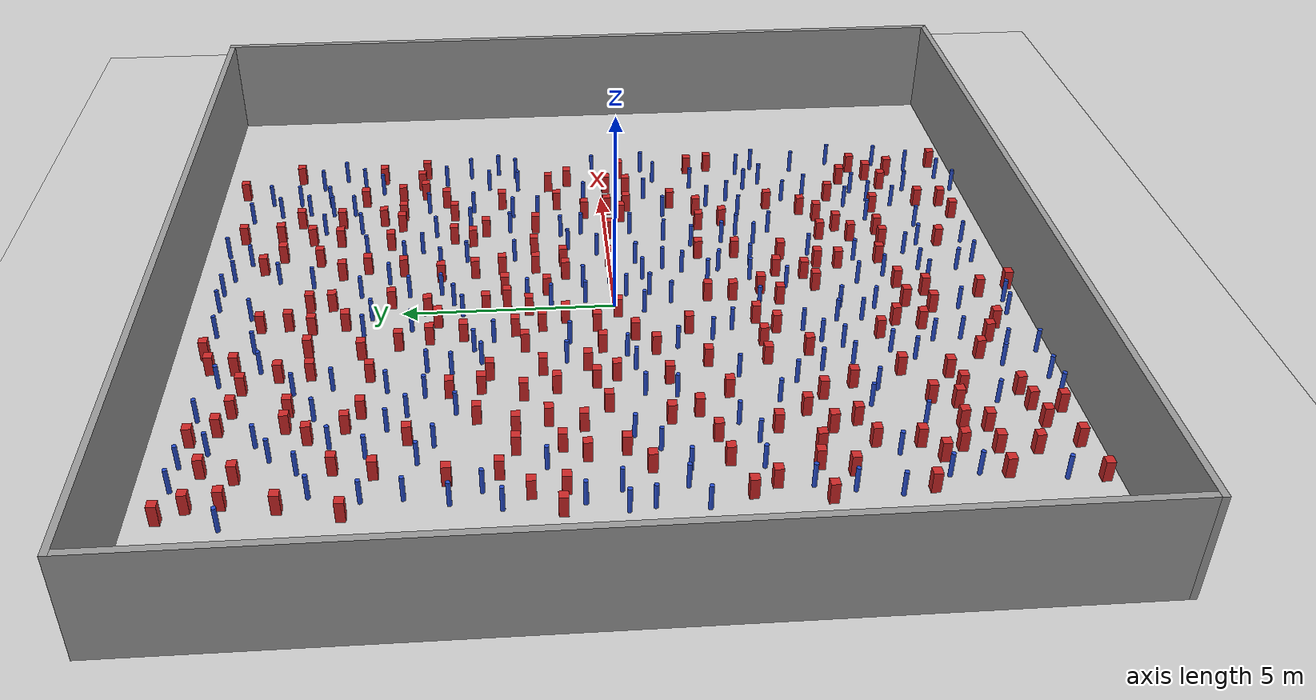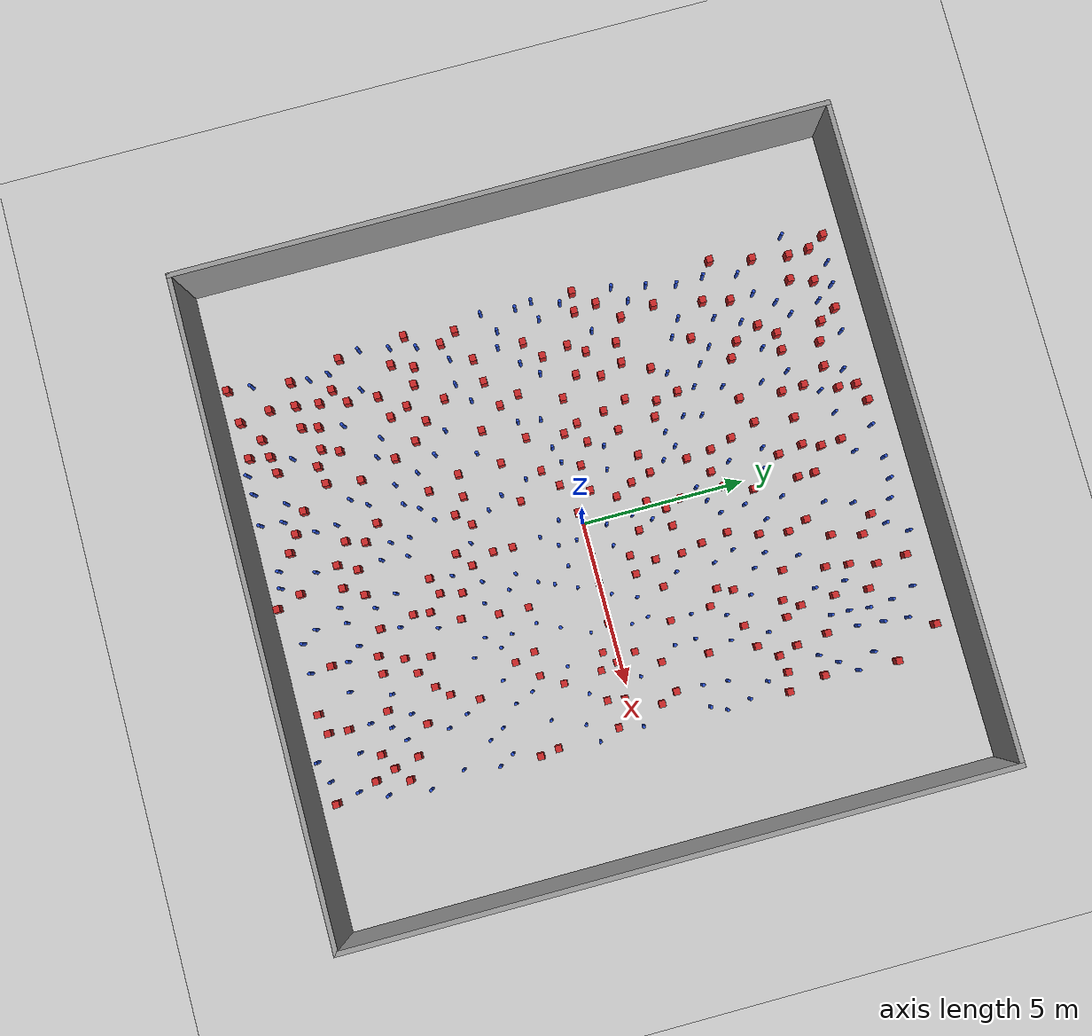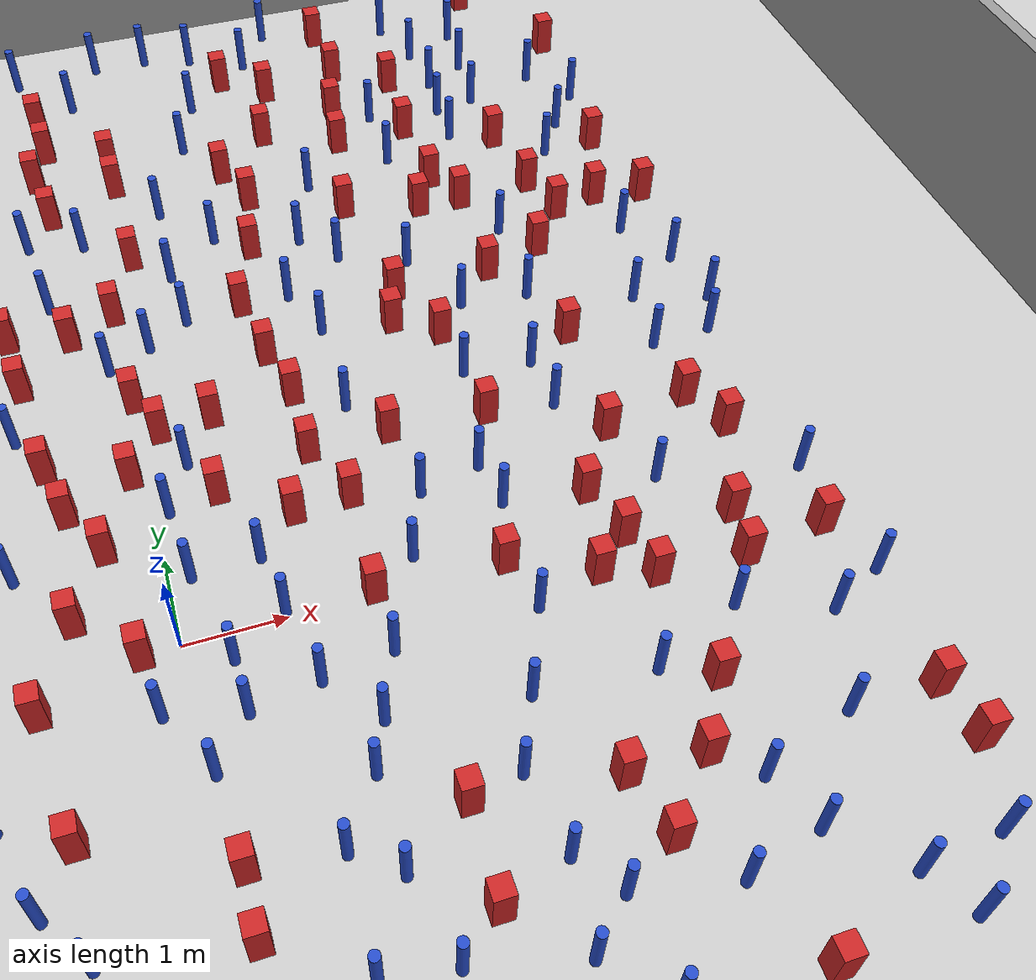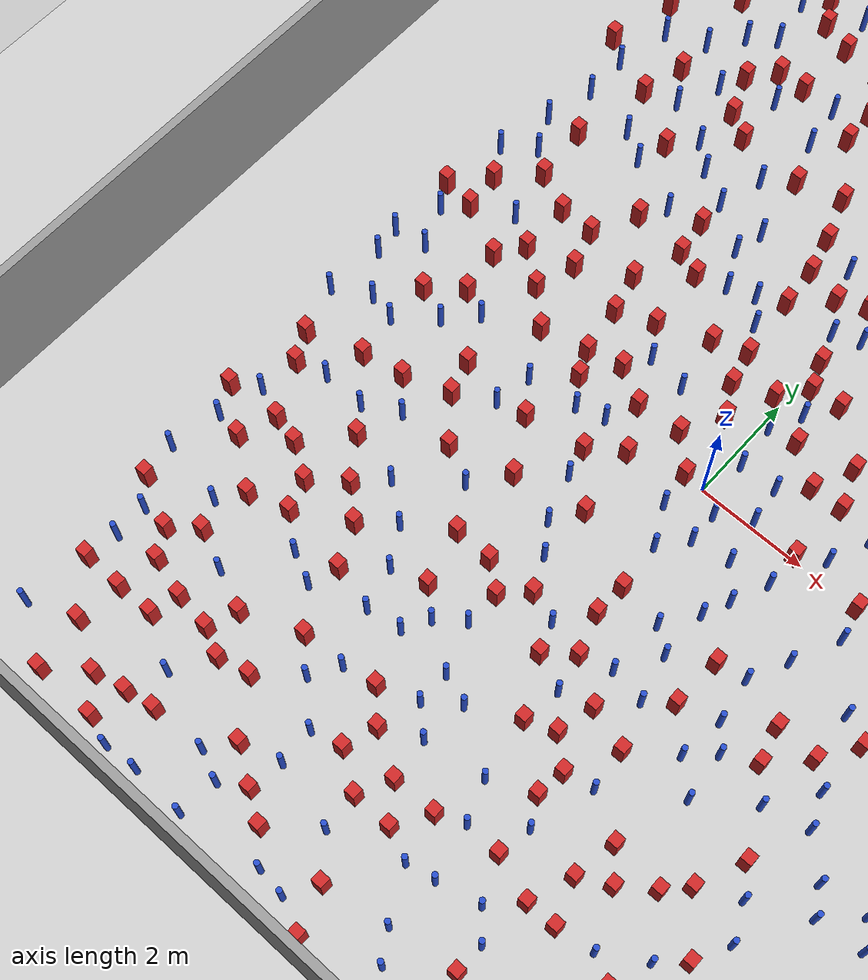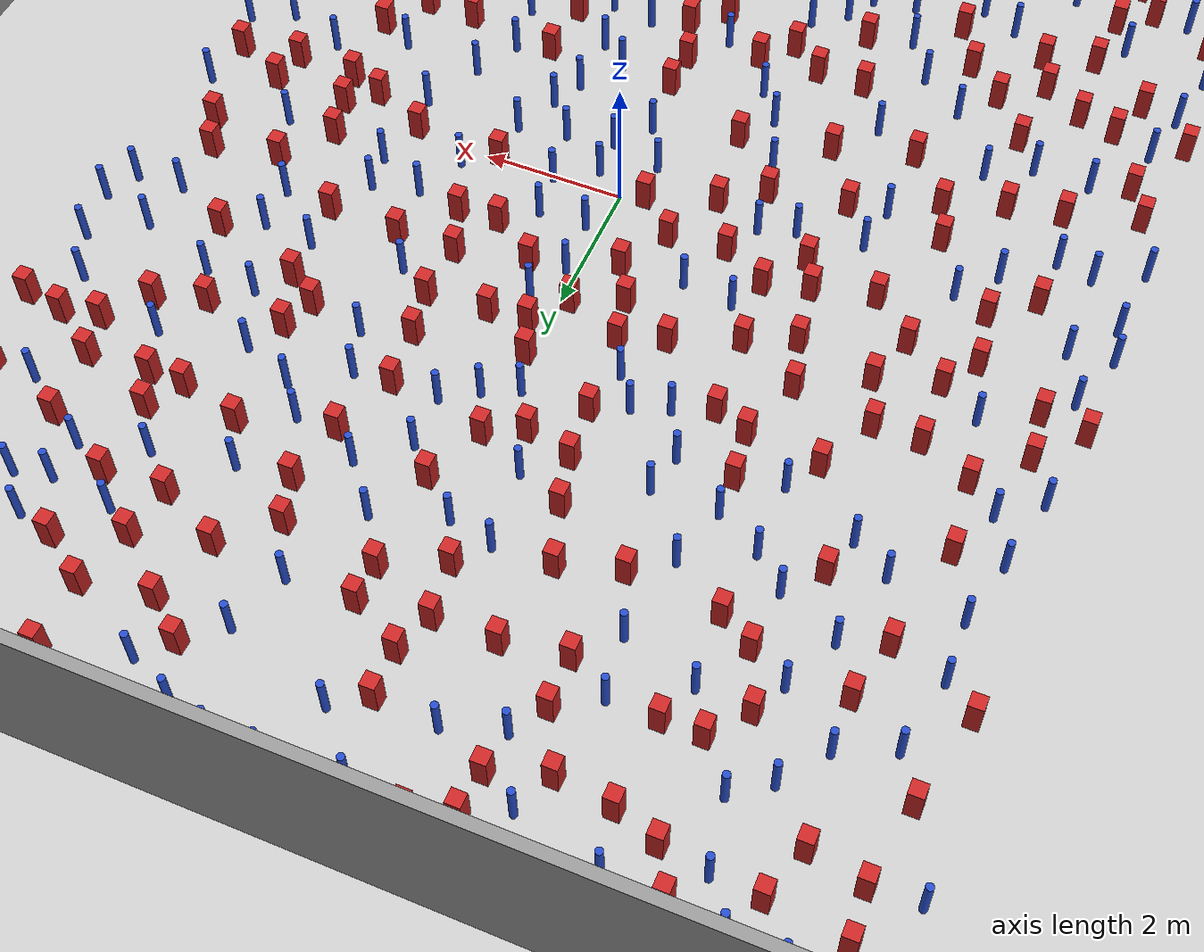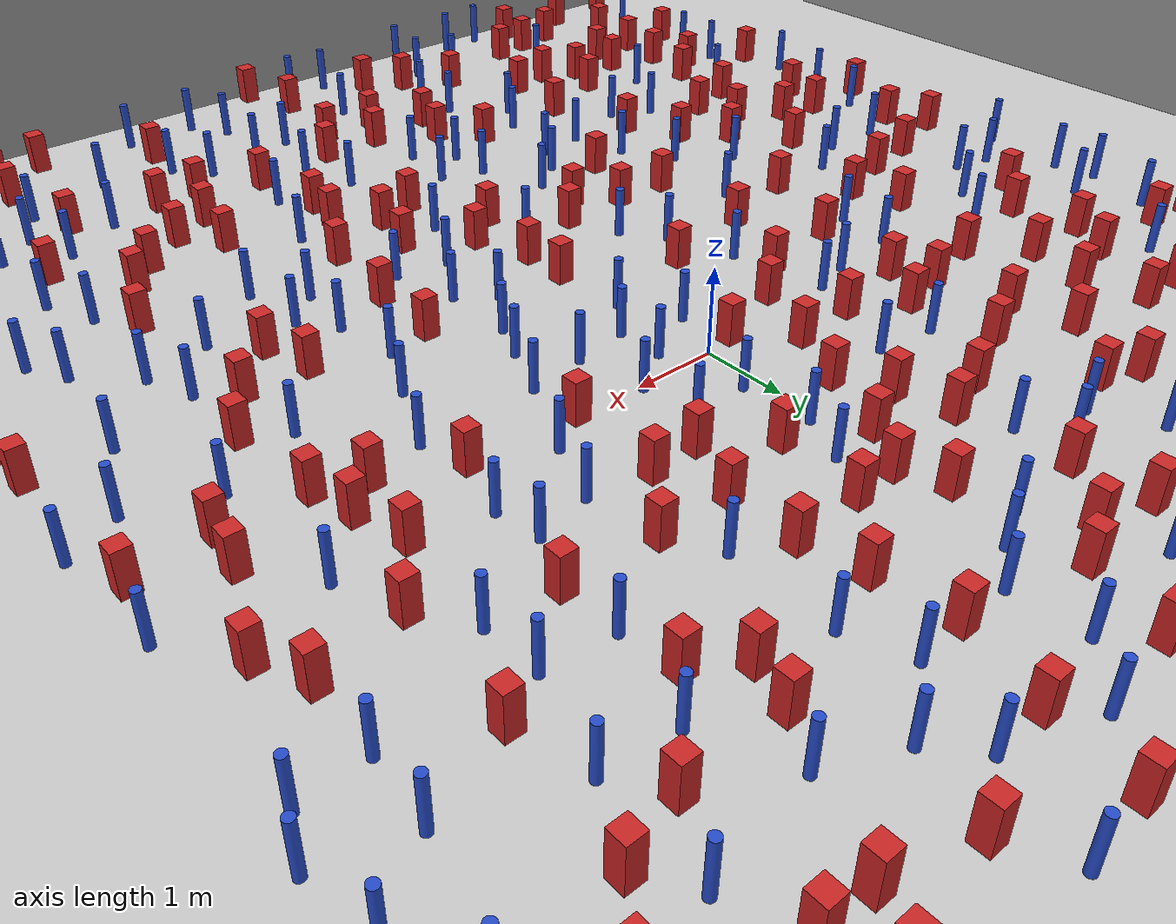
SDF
<sdf version="1.6">
 <world name="default">
  <light name="sun" type="directional">
   <pose>0 0 1000 0 -0 0</pose>
   <diffuse>0.8 0.8 0.8 1</diffuse>
   <specular>0.1 0.1 0.1 1</specular>
   <attenuation>
    <range>1000</range>
    <constant>0.9</constant>
    <linear>0.01</linear>
    <quadratic>0.001</quadratic>
   </attenuation>
   <direction>-0.5 0.5 -1</direction>
  </light>
  <model name="ground_plane">
   <static>1</static>
   <link name="link">
    <collision name="collision">
     <geometry><plane><normal>0 0 1</normal><size>100 100</size></plane></geometry>
     <surface><friction><ode><mu>100</mu><mu2>50</mu2></ode></friction></surface>
    </collision>
    <visual name="visual">
     <cast_shadows>0</cast_shadows>
     <geometry><plane><normal>0 0 1</normal><size>100 100</size></plane></geometry>
     <material>
      <ambient>1.0 1.0 1.0 1.0</ambient>
      <diffuse>0.8 0.8 0.8 1.0</diffuse>
      <specular>0.01 0.01 0.01 1.000000</specular>
     </material>
    </visual>
   </link>
  </model>
  <gravity>0 0 -9.8</gravity>
  <magnetic_field>6e-06 2.3e-05 -4.2e-05</magnetic_field>
  <atmosphere type="adiabatic"/>
  <physics name="default_physics" default="0" type="ode">
   <max_step_size>0.001</max_step_size>
   <real_time_factor>1</real_time_factor>
   <real_time_update_rate>1000</real_time_update_rate>
  </physics>
  <scene><ambient>0.4 0.4 0.4 1</ambient><background>0.7 0.7 0.7 1</background><shadows>1</shadows></scene>
  <spherical_coordinates>
   <surface_model>EARTH_WGS84</surface_model>
   <latitude_deg>0</latitude_deg>
   <longitude_deg>0</longitude_deg>
   <elevation>0</elevation>
   <heading_deg>0</heading_deg>
  </spherical_coordinates>
  <plugin name="gazebo_occupancy_map" filename="libgazebo_2Dmap_plugin.so">
   <map_resolution>0.05</map_resolution>
   <map_topic>generated_map</map_topic>
   <map_height>0.01</map_height>
   <map_size_x>50</map_size_x>
   <map_size_y>50</map_size_y>
  </plugin>
  <model name="NamedLocations">
   <static>true</static>
   <link name="DefaultStart"><pose>8.5 0 0 0 0 3.14</pose></link>
  </model>
  <model name="20x20_walls">
   <pose>0.044518 0.176112 0 0 -0 0</pose>
   <link name="Wall_1">
    <collision name="Wall_1_Collision">
     <geometry><box><size>20 0.15 2.5</size></box></geometry>
     <pose>0 0 1.25 0 -0 0</pose>
    </collision>
    <visual name="Wall_1_Visual">
     <pose>0 0 1.25 0 -0 0</pose>
     <geometry><box><size>20 0.15 2.5</size></box></geometry>
     <material>
      <script><uri>file://media/materials/scripts/gazebo.material</uri><name>Gazebo/Grey</name></script>
      <ambient>0.976471 0.992157 1 1</ambient>
     </material>
     <meta><layer>0</layer></meta>
    </visual>
    <pose>0 9.925 0 0 -0 0</pose>
   </link>
   <link name="Wall_3">
    <collision name="Wall_3_Collision">
     <geometry><box><size>20 0.15 2.5</size></box></geometry>
     <pose>0 0 1.25 0 -0 0</pose>
    </collision>
    <visual name="Wall_3_Visual">
     <pose>0 0 1.25 0 -0 0</pose>
     <geometry><box><size>20 0.15 2.5</size></box></geometry>
     <material>
      <script><uri>file://media/materials/scripts/gazebo.material</uri><name>Gazebo/Grey</name></script>
      <ambient>0.976471 0.992157 1 1</ambient>
     </material>
     <meta><layer>0</layer></meta>
    </visual>
    <pose>9.925 0 0 0 0 -1.5708</pose>
   </link>
   <link name="Wall_4">
    <collision name="Wall_4_Collision">
     <geometry><box><size>20 0.15 2.5</size></box></geometry>
     <pose>0 0 1.25 0 -0 0</pose>
    </collision>
    <visual name="Wall_4_Visual">
     <pose>0 0 1.25 0 -0 0</pose>
     <geometry><box><size>20 0.15 2.5</size></box></geometry>
     <material>
      <script><uri>file://media/materials/scripts/gazebo.material</uri><name>Gazebo/Grey</name></script>
      <ambient>0.976471 0.992157 1 1</ambient>
     </material>
     <meta><layer>0</layer></meta>
    </visual>
    <pose>0 -9.925 0 0 -0 3.14159</pose>
   </link>
   <link name="Wall_5">
    <collision name="Wall_5_Collision">
     <geometry><box><size>20 0.15 2.5</size></box></geometry>
     <pose>0 0 1.25 0 -0 0</pose>
    </collision>
    <visual name="Wall_5_Visual">
     <pose>0 0 1.25 0 -0 0</pose>
     <geometry><box><size>20 0.15 2.5</size></box></geometry>
     <material>
      <script><uri>file://media/materials/scripts/gazebo.material</uri><name>Gazebo/Grey</name></script>
      <ambient>0.976471 0.992157 1 1</ambient>
     </material>
     <meta><layer>0</layer></meta>
    </visual>
    <pose>-9.925 0 0 0 -0 1.5708</pose>
   </link>
   <static>1</static>
  </model>
  <model name="pole_obstacle0">
   <static>true</static>
   <pose>-5.60489354962 1.792876674 2.88873142074e-08 -9.90536689445e-09 4.60219948999e-07 -1.20965994956e-07</pose>
   <link name="link">
    <pose>0 0 0.3 0 -0 0</pose>
    <inertial>
     <mass>1</mass>
     <inertia><ixx>0.145833</ixx><ixy>0</ixy><ixz>0</ixz><iyy>0.145833</iyy><iyz>0</iyz><izz>0.125</izz></inertia>
    </inertial>
    <collision name="collision">
     <geometry><cylinder><radius>0.05</radius><length>.6</length></cylinder></geometry>
    </collision>
    <visual name="visual">
     <geometry><cylinder><radius>0.05</radius><length>.6</length></cylinder></geometry>
     <material>
      <script><name>Gazebo/Blue</name><uri>file://media/materials/scripts/gazebo.material</uri></script>
     </material>
    </visual>
   </link>
  </model>
  <model name="pole_obstacle1">
   <static>true</static>
   <pose>4.37582242248 9.04554621541 2.88873142074e-08 -9.9053668967e-09 4.60219948993e-07 -1.20965994957e-07</pose>
   <link name="link">
    <pose>0 0 0.3 0 -0 0</pose>
    <inertial>
     <mass>1</mass>
     <inertia><ixx>0.145833</ixx><ixy>0</ixy><ixz>0</ixz><iyy>0.145833</iyy><iyz>0</iyz><izz>0.125</izz></inertia>
    </inertial>
    <collision name="collision">
     <geometry><cylinder><radius>0.05</radius><length>.6</length></cylinder></geometry>
    </collision>
    <visual name="visual">
     <geometry><cylinder><radius>0.05</radius><length>.6</length></cylinder></geometry>
     <material>
      <script><name>Gazebo/Blue</name><uri>file://media/materials/scripts/gazebo.material</uri></script>
     </material>
    </visual>
   </link>
  </model>
  <model name="square_post_obstacle0">
   <static>true</static>
   <pose>3.33551158871 -2.38753182375 8.22691968438e-08 7.2212513382e-06 -7.54495500217e-07 2.29674213826e-05</pose>
   <link name="link">
    <pose>0 0 0.25 0 -0 0</pose>
    <inertial>
     <mass>100</mass>
     <inertia>
      <ixx>0.166667</ixx>
      <ixy>0</ixy>
      <ixz>0</ixz>
      <iyy>0.166667</iyy>
      <iyz>0</iyz>
      <izz>0.166667</izz>
     </inertia>
    </inertial>
    <collision name="collision"><geometry><box><size>.2 .2 .5</size></box></geometry></collision>
    <visual name="visual">
     <geometry><box><size>.2 .2 .5</size></box></geometry>
     <material>
      <script><name>Gazebo/Red</name><uri>file://media/materials/scripts/gazebo.material</uri></script>
     </material>
    </visual>
   </link>
  </model>
  <model name="square_post_obstacle1">
   <static>true</static>
   <pose>6.35539613358 -2.98623689507 8.22691968438e-08 7.2212513382e-06 -7.54495500217e-07 2.29674213826e-05</pose>
   <link name="link">
    <pose>0 0 0.25 0 -0 0</pose>
    <inertial>
     <mass>100</mass>
     <inertia>
      <ixx>0.166667</ixx>
      <ixy>0</ixy>
      <ixz>0</ixz>
      <iyy>0.166667</iyy>
      <iyz>0</iyz>
      <izz>0.166667</izz>
     </inertia>
    </inertial>
    <collision name="collision"><geometry><box><size>.2 .2 .5</size></box></geometry></collision>
    <visual name="visual">
     <geometry><box><size>.2 .2 .5</size></box></geometry>
     <material>
      <script><name>Gazebo/Red</name><uri>file://media/materials/scripts/gazebo.material</uri></script>
     </material>
    </visual>
   </link>
  </model>
  <model name="pole_obstacle2">
   <static>true</static>
   <pose>6.14830196329 -5.28207078286 2.88873142074e-08 -9.90536690842e-09 4.60219948965e-07 -1.20965994976e-07</pose>
   <link name="link">
    <pose>0 0 0.3 0 -0 0</pose>
    <inertial>
     <mass>1</mass>
     <inertia><ixx>0.145833</ixx><ixy>0</ixy><ixz>0</ixz><iyy>0.145833</iyy><iyz>0</iyz><izz>0.125</izz></inertia>
    </inertial>
    <collision name="collision">
     <geometry><cylinder><radius>0.05</radius><length>.6</length></cylinder></geometry>
    </collision>
    <visual name="visual">
     <geometry><cylinder><radius>0.05</radius><length>.6</length></cylinder></geometry>
     <material>
      <script><name>Gazebo/Blue</name><uri>file://media/materials/scripts/gazebo.material</uri></script>
     </material>
    </visual>
   </link>
  </model>
  <model name="pole_obstacle3">
   <static>true</static>
   <pose>-0.965626701555 -9.16200165954 2.88873142074e-08 -9.90536690773e-09 4.60219948967e-07 -1.20965994976e-07</pose>
   <link name="link">
    <pose>0 0 0.3 0 -0 0</pose>
    <inertial>
     <mass>1</mass>
     <inertia><ixx>0.145833</ixx><ixy>0</ixy><ixz>0</ixz><iyy>0.145833</iyy><iyz>0</iyz><izz>0.125</izz></inertia>
    </inertial>
    <collision name="collision">
     <geometry><cylinder><radius>0.05</radius><length>.6</length></cylinder></geometry>
    </collision>
    <visual name="visual">
     <geometry><cylinder><radius>0.05</radius><length>.6</length></cylinder></geometry>
     <material>
      <script><name>Gazebo/Blue</name><uri>file://media/materials/scripts/gazebo.material</uri></script>
     </material>
    </visual>
   </link>
  </model>
  <model name="pole_obstacle4">
   <static>true</static>
   <pose>-0.408652184443 -5.30799203485 2.88873142074e-08 -9.90536689683e-09 4.60219948993e-07 -1.20965994957e-07</pose>
   <link name="link">
    <pose>0 0 0.3 0 -0 0</pose>
    <inertial>
     <mass>1</mass>
     <inertia><ixx>0.145833</ixx><ixy>0</ixy><ixz>0</ixz><iyy>0.145833</iyy><iyz>0</iyz><izz>0.125</izz></inertia>
    </inertial>
    <collision name="collision">
     <geometry><cylinder><radius>0.05</radius><length>.6</length></cylinder></geometry>
    </collision>
    <visual name="visual">
     <geometry><cylinder><radius>0.05</radius><length>.6</length></cylinder></geometry>
     <material>
      <script><name>Gazebo/Blue</name><uri>file://media/materials/scripts/gazebo.material</uri></script>
     </material>
    </visual>
   </link>
  </model>
  <model name="pole_obstacle5">
   <static>true</static>
   <pose>-2.88354378176 -8.45582240815 2.88873142074e-08 -9.90536692318e-09 4.6021994893e-07 -1.20965994988e-07</pose>
   <link name="link">
    <pose>0 0 0.3 0 -0 0</pose>
    <inertial>
     <mass>1</mass>
     <inertia><ixx>0.145833</ixx><ixy>0</ixy><ixz>0</ixz><iyy>0.145833</iyy><iyz>0</iyz><izz>0.125</izz></inertia>
    </inertial>
    <collision name="collision">
     <geometry><cylinder><radius>0.05</radius><length>.6</length></cylinder></geometry>
    </collision>
    <visual name="visual">
     <geometry><cylinder><radius>0.05</radius><length>.6</length></cylinder></geometry>
     <material>
      <script><name>Gazebo/Blue</name><uri>file://media/materials/scripts/gazebo.material</uri></script>
     </material>
    </visual>
   </link>
  </model>
  <model name="pole_obstacle6">
   <static>true</static>
   <pose>0.951202149608 -2.32949687447 2.88873142074e-08 -9.90536689802e-09 4.6021994899e-07 -1.2096599496e-07</pose>
   <link name="link">
    <pose>0 0 0.3 0 -0 0</pose>
    <inertial>
     <mass>1</mass>
     <inertia><ixx>0.145833</ixx><ixy>0</ixy><ixz>0</ixz><iyy>0.145833</iyy><iyz>0</iyz><izz>0.125</izz></inertia>
    </inertial>
    <collision name="collision">
     <geometry><cylinder><radius>0.05</radius><length>.6</length></cylinder></geometry>
    </collision>
    <visual name="visual">
     <geometry><cylinder><radius>0.05</radius><length>.6</length></cylinder></geometry>
     <material>
      <script><name>Gazebo/Blue</name><uri>file://media/materials/scripts/gazebo.material</uri></script>
     </material>
    </visual>
   </link>
  </model>
  <model name="square_post_obstacle2">
   <static>true</static>
   <pose>0.2190282874 2.5391222892 8.22691968438e-08 7.2212513382e-06 -7.54495500217e-07 2.29674213826e-05</pose>
   <link name="link">
    <pose>0 0 0.25 0 -0 0</pose>
    <inertial>
     <mass>100</mass>
     <inertia>
      <ixx>0.166667</ixx>
      <ixy>0</ixy>
      <ixz>0</ixz>
      <iyy>0.166667</iyy>
      <iyz>0</iyz>
      <izz>0.166667</izz>
     </inertia>
    </inertial>
    <collision name="collision"><geometry><box><size>.2 .2 .5</size></box></geometry></collision>
    <visual name="visual">
     <geometry><box><size>.2 .2 .5</size></box></geometry>
     <material>
      <script><name>Gazebo/Red</name><uri>file://media/materials/scripts/gazebo.material</uri></script>
     </material>
    </visual>
   </link>
  </model>
  <model name="square_post_obstacle3">
   <static>true</static>
   <pose>0.921883301108 -4.67364424188 8.22691968438e-08 7.22125133819e-06 -7.54495500217e-07 2.29674213826e-05</pose>
   <link name="link">
    <pose>0 0 0.25 0 -0 0</pose>
    <inertial>
     <mass>100</mass>
     <inertia>
      <ixx>0.166667</ixx>
      <ixy>0</ixy>
      <ixz>0</ixz>
      <iyy>0.166667</iyy>
      <iyz>0</iyz>
      <izz>0.166667</izz>
     </inertia>
    </inertial>
    <collision name="collision"><geometry><box><size>.2 .2 .5</size></box></geometry></collision>
    <visual name="visual">
     <geometry><box><size>.2 .2 .5</size></box></geometry>
     <material>
      <script><name>Gazebo/Red</name><uri>file://media/materials/scripts/gazebo.material</uri></script>
     </material>
    </visual>
   </link>
  </model>
  <model name="square_post_obstacle4">
   <static>true</static>
   <pose>-0.353924351522 -0.0484012104252 8.22691968438e-08 7.2212513382e-06 -7.54495500217e-07 2.29674213826e-05</pose>
   <link name="link">
    <pose>0 0 0.25 0 -0 0</pose>
    <inertial>
     <mass>100</mass>
     <inertia>
      <ixx>0.166667</ixx>
      <ixy>0</ixy>
      <ixz>0</ixz>
      <iyy>0.166667</iyy>
      <iyz>0</iyz>
      <izz>0.166667</izz>
     </inertia>
    </inertial>
    <collision name="collision"><geometry><box><size>.2 .2 .5</size></box></geometry></collision>
    <visual name="visual">
     <geometry><box><size>.2 .2 .5</size></box></geometry>
     <material>
      <script><name>Gazebo/Red</name><uri>file://media/materials/scripts/gazebo.material</uri></script>
     </material>
    </visual>
   </link>
  </model>
  <model name="pole_obstacle7">
   <static>true</static>
   <pose>-5.84208865774 -1.11125612981 2.88873142074e-08 -9.90536689445e-09 4.60219948999e-07 -1.20965994956e-07</pose>
   <link name="link">
    <pose>0 0 0.3 0 -0 0</pose>
    <inertial>
     <mass>1</mass>
     <inertia><ixx>0.145833</ixx><ixy>0</ixy><ixz>0</ixz><iyy>0.145833</iyy><iyz>0</iyz><izz>0.125</izz></inertia>
    </inertial>
    <collision name="collision">
     <geometry><cylinder><radius>0.05</radius><length>.6</length></cylinder></geometry>
    </collision>
    <visual name="visual">
     <geometry><cylinder><radius>0.05</radius><length>.6</length></cylinder></geometry>
     <material>
      <script><name>Gazebo/Blue</name><uri>file://media/materials/scripts/gazebo.material</uri></script>
     </material>
    </visual>
   </link>
  </model>
  <model name="pole_obstacle8">
   <static>true</static>
   <pose>-6.21378915268 3.09624534109 2.88873142074e-08 -9.90536690245e-09 4.6021994898e-07 -1.20965994966e-07</pose>
   <link name="link">
    <pose>0 0 0.3 0 -0 0</pose>
    <inertial>
     <mass>1</mass>
     <inertia><ixx>0.145833</ixx><ixy>0</ixy><ixz>0</ixz><iyy>0.145833</iyy><iyz>0</iyz><izz>0.125</izz></inertia>
    </inertial>
    <collision name="collision">
     <geometry><cylinder><radius>0.05</radius><length>.6</length></cylinder></geometry>
    </collision>
    <visual name="visual">
     <geometry><cylinder><radius>0.05</radius><length>.6</length></cylinder></geometry>
     <material>
      <script><name>Gazebo/Blue</name><uri>file://media/materials/scripts/gazebo.material</uri></script>
     </material>
    </visual>
   </link>
  </model>
  <model name="square_post_obstacle5">
   <static>true</static>
   <pose>-3.48958603233 8.40357161322 8.22691968438e-08 7.22125133819e-06 -7.54495500217e-07 2.29674213826e-05</pose>
   <link name="link">
    <pose>0 0 0.25 0 -0 0</pose>
    <inertial>
     <mass>100</mass>
     <inertia>
      <ixx>0.166667</ixx>
      <ixy>0</ixy>
      <ixz>0</ixz>
      <iyy>0.166667</iyy>
      <iyz>0</iyz>
      <izz>0.166667</izz>
     </inertia>
    </inertial>
    <collision name="collision"><geometry><box><size>.2 .2 .5</size></box></geometry></collision>
    <visual name="visual">
     <geometry><box><size>.2 .2 .5</size></box></geometry>
     <material>
      <script><name>Gazebo/Red</name><uri>file://media/materials/scripts/gazebo.material</uri></script>
     </material>
    </visual>
   </link>
  </model>
  <model name="square_post_obstacle6">
   <static>true</static>
   <pose>-4.08551732455 8.60938443152 8.22691968438e-08 7.22125133819e-06 -7.54495500217e-07 2.29674213826e-05</pose>
   <link name="link">
    <pose>0 0 0.25 0 -0 0</pose>
    <inertial>
     <mass>100</mass>
     <inertia>
      <ixx>0.166667</ixx>
      <ixy>0</ixy>
      <ixz>0</ixz>
      <iyy>0.166667</iyy>
      <iyz>0</iyz>
      <izz>0.166667</izz>
     </inertia>
    </inertial>
    <collision name="collision"><geometry><box><size>.2 .2 .5</size></box></geometry></collision>
    <visual name="visual">
     <geometry><box><size>.2 .2 .5</size></box></geometry>
     <material>
      <script><name>Gazebo/Red</name><uri>file://media/materials/scripts/gazebo.material</uri></script>
     </material>
    </visual>
   </link>
  </model>
  <model name="square_post_obstacle7">
   <static>true</static>
   <pose>2.27140523398 7.10940884494 8.22691968438e-08 7.2212513382e-06 -7.54495500217e-07 2.29674213826e-05</pose>
   <link name="link">
    <pose>0 0 0.25 0 -0 0</pose>
    <inertial>
     <mass>100</mass>
     <inertia>
      <ixx>0.166667</ixx>
      <ixy>0</ixy>
      <ixz>0</ixz>
      <iyy>0.166667</iyy>
      <iyz>0</iyz>
      <izz>0.166667</izz>
     </inertia>
    </inertial>
    <collision name="collision"><geometry><box><size>.2 .2 .5</size></box></geometry></collision>
    <visual name="visual">
     <geometry><box><size>.2 .2 .5</size></box></geometry>
     <material>
      <script><name>Gazebo/Red</name><uri>file://media/materials/scripts/gazebo.material</uri></script>
     </material>
    </visual>
   </link>
  </model>
  <model name="pole_obstacle9">
   <static>true</static>
   <pose>1.67303859116 9.12570394465 2.88873142074e-08 -9.90536690474e-09 4.60219948974e-07 -1.2096599497e-07</pose>
   <link name="link">
    <pose>0 0 0.3 0 -0 0</pose>
    <inertial>
     <mass>1</mass>
     <inertia><ixx>0.145833</ixx><ixy>0</ixy><ixz>0</ixz><iyy>0.145833</iyy><iyz>0</iyz><izz>0.125</izz></inertia>
    </inertial>
    <collision name="collision">
     <geometry><cylinder><radius>0.05</radius><length>.6</length></cylinder></geometry>
    </collision>
    <visual name="visual">
     <geometry><cylinder><radius>0.05</radius><length>.6</length></cylinder></geometry>
     <material>
      <script><name>Gazebo/Blue</name><uri>file://media/materials/scripts/gazebo.material</uri></script>
     </material>
    </visual>
   </link>
  </model>
  <model name="pole_obstacle10">
   <static>true</static>
   <pose>-1.11642473633 -2.62495609921 2.88873142074e-08 -9.90536689791e-09 4.6021994899e-07 -1.20965994959e-07</pose>
   <link name="link">
    <pose>0 0 0.3 0 -0 0</pose>
    <inertial>
     <mass>1</mass>
     <inertia><ixx>0.145833</ixx><ixy>0</ixy><ixz>0</ixz><iyy>0.145833</iyy><iyz>0</iyz><izz>0.125</izz></inertia>
    </inertial>
    <collision name="collision">
     <geometry><cylinder><radius>0.05</radius><length>.6</length></cylinder></geometry>
    </collision>
    <visual name="visual">
     <geometry><cylinder><radius>0.05</radius><length>.6</length></cylinder></geometry>
     <material>
      <script><name>Gazebo/Blue</name><uri>file://media/materials/scripts/gazebo.material</uri></script>
     </material>
    </visual>
   </link>
  </model>
  <model name="pole_obstacle11">
   <static>true</static>
   <pose>-5.09082674828 9.23493699206 2.88873142074e-08 -9.9053668967e-09 4.60219948993e-07 -1.20965994957e-07</pose>
   <link name="link">
    <pose>0 0 0.3 0 -0 0</pose>
    <inertial>
     <mass>1</mass>
     <inertia><ixx>0.145833</ixx><ixy>0</ixy><ixz>0</ixz><iyy>0.145833</iyy><iyz>0</iyz><izz>0.125</izz></inertia>
    </inertial>
    <collision name="collision">
     <geometry><cylinder><radius>0.05</radius><length>.6</length></cylinder></geometry>
    </collision>
    <visual name="visual">
     <geometry><cylinder><radius>0.05</radius><length>.6</length></cylinder></geometry>
     <material>
      <script><name>Gazebo/Blue</name><uri>file://media/materials/scripts/gazebo.material</uri></script>
     </material>
    </visual>
   </link>
  </model>
  <model name="pole_obstacle12">
   <static>true</static>
   <pose>-6.74844758762 2.70002124592 2.88873142074e-08 -9.90536690245e-09 4.6021994898e-07 -1.20965994966e-07</pose>
   <link name="link">
    <pose>0 0 0.3 0 -0 0</pose>
    <inertial>
     <mass>1</mass>
     <inertia><ixx>0.145833</ixx><ixy>0</ixy><ixz>0</ixz><iyy>0.145833</iyy><iyz>0</iyz><izz>0.125</izz></inertia>
    </inertial>
    <collision name="collision">
     <geometry><cylinder><radius>0.05</radius><length>.6</length></cylinder></geometry>
    </collision>
    <visual name="visual">
     <geometry><cylinder><radius>0.05</radius><length>.6</length></cylinder></geometry>
     <material>
      <script><name>Gazebo/Blue</name><uri>file://media/materials/scripts/gazebo.material</uri></script>
     </material>
    </visual>
   </link>
  </model>
  <model name="square_post_obstacle8">
   <static>true</static>
   <pose>-5.93874351744 -3.71497561347 8.22691968438e-08 7.2212513382e-06 -7.54495500217e-07 2.29674213826e-05</pose>
   <link name="link">
    <pose>0 0 0.25 0 -0 0</pose>
    <inertial>
     <mass>100</mass>
     <inertia>
      <ixx>0.166667</ixx>
      <ixy>0</ixy>
      <ixz>0</ixz>
      <iyy>0.166667</iyy>
      <iyz>0</iyz>
      <izz>0.166667</izz>
     </inertia>
    </inertial>
    <collision name="collision"><geometry><box><size>.2 .2 .5</size></box></geometry></collision>
    <visual name="visual">
     <geometry><box><size>.2 .2 .5</size></box></geometry>
     <material>
      <script><name>Gazebo/Red</name><uri>file://media/materials/scripts/gazebo.material</uri></script>
     </material>
    </visual>
   </link>
  </model>
  <model name="square_post_obstacle9">
   <static>true</static>
   <pose>-3.12864663933 1.49392424948 8.22691968438e-08 7.2212513382e-06 -7.54495500217e-07 2.29674213826e-05</pose>
   <link name="link">
    <pose>0 0 0.25 0 -0 0</pose>
    <inertial>
     <mass>100</mass>
     <inertia>
      <ixx>0.166667</ixx>
      <ixy>0</ixy>
      <ixz>0</ixz>
      <iyy>0.166667</iyy>
      <iyz>0</iyz>
      <izz>0.166667</izz>
     </inertia>
    </inertial>
    <collision name="collision"><geometry><box><size>.2 .2 .5</size></box></geometry></collision>
    <visual name="visual">
     <geometry><box><size>.2 .2 .5</size></box></geometry>
     <material>
      <script><name>Gazebo/Red</name><uri>file://media/materials/scripts/gazebo.material</uri></script>
     </material>
    </visual>
   </link>
  </model>
  <model name="pole_obstacle13">
   <static>true</static>
   <pose>-4.68693473672 6.25540807904 2.88873142074e-08 -9.90536690842e-09 4.60219948965e-07 -1.20965994976e-07</pose>
   <link name="link">
    <pose>0 0 0.3 0 -0 0</pose>
    <inertial>
     <mass>1</mass>
     <inertia><ixx>0.145833</ixx><ixy>0</ixy><ixz>0</ixz><iyy>0.145833</iyy><iyz>0</iyz><izz>0.125</izz></inertia>
    </inertial>
    <collision name="collision">
     <geometry><cylinder><radius>0.05</radius><length>.6</length></cylinder></geometry>
    </collision>
    <visual name="visual">
     <geometry><cylinder><radius>0.05</radius><length>.6</length></cylinder></geometry>
     <material>
      <script><name>Gazebo/Blue</name><uri>file://media/materials/scripts/gazebo.material</uri></script>
     </material>
    </visual>
   </link>
  </model>
  <model name="square_post_obstacle10">
   <static>true</static>
   <pose>-0.963395042714 2.35977024159 8.22691968438e-08 7.2212513382e-06 -7.54495500217e-07 2.29674213826e-05</pose>
   <link name="link">
    <pose>0 0 0.25 0 -0 0</pose>
    <inertial>
     <mass>100</mass>
     <inertia>
      <ixx>0.166667</ixx>
      <ixy>0</ixy>
      <ixz>0</ixz>
      <iyy>0.166667</iyy>
      <iyz>0</iyz>
      <izz>0.166667</izz>
     </inertia>
    </inertial>
    <collision name="collision"><geometry><box><size>.2 .2 .5</size></box></geometry></collision>
    <visual name="visual">
     <geometry><box><size>.2 .2 .5</size></box></geometry>
     <material>
      <script><name>Gazebo/Red</name><uri>file://media/materials/scripts/gazebo.material</uri></script>
     </material>
    </visual>
   </link>
  </model>
  <model name="square_post_obstacle11">
   <static>true</static>
   <pose>5.87914294403 4.74547711981 8.22691968438e-08 7.2212513382e-06 -7.54495500217e-07 2.29674213826e-05</pose>
   <link name="link">
    <pose>0 0 0.25 0 -0 0</pose>
    <inertial>
     <mass>100</mass>
     <inertia>
      <ixx>0.166667</ixx>
      <ixy>0</ixy>
      <ixz>0</ixz>
      <iyy>0.166667</iyy>
      <iyz>0</iyz>
      <izz>0.166667</izz>
     </inertia>
    </inertial>
    <collision name="collision"><geometry><box><size>.2 .2 .5</size></box></geometry></collision>
    <visual name="visual">
     <geometry><box><size>.2 .2 .5</size></box></geometry>
     <material>
      <script><name>Gazebo/Red</name><uri>file://media/materials/scripts/gazebo.material</uri></script>
     </material>
    </visual>
   </link>
  </model>
  <model name="pole_obstacle14">
   <static>true</static>
   <pose>0.768665898864 6.00691216805 2.88873142074e-08 -9.90536689661e-09 4.60219948993e-07 -1.20965994957e-07</pose>
   <link name="link">
    <pose>0 0 0.3 0 -0 0</pose>
    <inertial>
     <mass>1</mass>
     <inertia><ixx>0.145833</ixx><ixy>0</ixy><ixz>0</ixz><iyy>0.145833</iyy><iyz>0</iyz><izz>0.125</izz></inertia>
    </inertial>
    <collision name="collision">
     <geometry><cylinder><radius>0.05</radius><length>.6</length></cylinder></geometry>
    </collision>
    <visual name="visual">
     <geometry><cylinder><radius>0.05</radius><length>.6</length></cylinder></geometry>
     <material>
      <script><name>Gazebo/Blue</name><uri>file://media/materials/scripts/gazebo.material</uri></script>
     </material>
    </visual>
   </link>
  </model>
  <model name="pole_obstacle15">
   <static>true</static>
   <pose>-6.33041977614 4.64889348198 2.88873142074e-08 -9.90536690842e-09 4.60219948965e-07 -1.20965994976e-07</pose>
   <link name="link">
    <pose>0 0 0.3 0 -0 0</pose>
    <inertial>
     <mass>1</mass>
     <inertia><ixx>0.145833</ixx><ixy>0</ixy><ixz>0</ixz><iyy>0.145833</iyy><iyz>0</iyz><izz>0.125</izz></inertia>
    </inertial>
    <collision name="collision">
     <geometry><cylinder><radius>0.05</radius><length>.6</length></cylinder></geometry>
    </collision>
    <visual name="visual">
     <geometry><cylinder><radius>0.05</radius><length>.6</length></cylinder></geometry>
     <material>
      <script><name>Gazebo/Blue</name><uri>file://media/materials/scripts/gazebo.material</uri></script>
     </material>
    </visual>
   </link>
  </model>
  <model name="square_post_obstacle12">
   <static>true</static>
   <pose>-2.46374674068 1.77407036471 8.22691968438e-08 7.2212513382e-06 -7.54495500217e-07 2.29674213826e-05</pose>
   <link name="link">
    <pose>0 0 0.25 0 -0 0</pose>
    <inertial>
     <mass>100</mass>
     <inertia>
      <ixx>0.166667</ixx>
      <ixy>0</ixy>
      <ixz>0</ixz>
      <iyy>0.166667</iyy>
      <iyz>0</iyz>
      <izz>0.166667</izz>
     </inertia>
    </inertial>
    <collision name="collision"><geometry><box><size>.2 .2 .5</size></box></geometry></collision>
    <visual name="visual">
     <geometry><box><size>.2 .2 .5</size></box></geometry>
     <material>
      <script><name>Gazebo/Red</name><uri>file://media/materials/scripts/gazebo.material</uri></script>
     </material>
    </visual>
   </link>
  </model>
  <model name="pole_obstacle16">
   <static>true</static>
   <pose>4.67616366562 -3.29924647182 2.88873142074e-08 -9.90536690245e-09 4.6021994898e-07 -1.20965994966e-07</pose>
   <link name="link">
    <pose>0 0 0.3 0 -0 0</pose>
    <inertial>
     <mass>1</mass>
     <inertia><ixx>0.145833</ixx><ixy>0</ixy><ixz>0</ixz><iyy>0.145833</iyy><iyz>0</iyz><izz>0.125</izz></inertia>
    </inertial>
    <collision name="collision">
     <geometry><cylinder><radius>0.05</radius><length>.6</length></cylinder></geometry>
    </collision>
    <visual name="visual">
     <geometry><cylinder><radius>0.05</radius><length>.6</length></cylinder></geometry>
     <material>
      <script><name>Gazebo/Blue</name><uri>file://media/materials/scripts/gazebo.material</uri></script>
     </material>
    </visual>
   </link>
  </model>
  <model name="pole_obstacle17">
   <static>true</static>
   <pose>0.307623092809 3.79545921827 2.88873142074e-08 -9.90536689663e-09 4.60219948993e-07 -1.20965994959e-07</pose>
   <link name="link">
    <pose>0 0 0.3 0 -0 0</pose>
    <inertial>
     <mass>1</mass>
     <inertia><ixx>0.145833</ixx><ixy>0</ixy><ixz>0</ixz><iyy>0.145833</iyy><iyz>0</iyz><izz>0.125</izz></inertia>
    </inertial>
    <collision name="collision">
     <geometry><cylinder><radius>0.05</radius><length>.6</length></cylinder></geometry>
    </collision>
    <visual name="visual">
     <geometry><cylinder><radius>0.05</radius><length>.6</length></cylinder></geometry>
     <material>
      <script><name>Gazebo/Blue</name><uri>file://media/materials/scripts/gazebo.material</uri></script>
     </material>
    </visual>
   </link>
  </model>
  <model name="square_post_obstacle13">
   <static>true</static>
   <pose>3.08221346266 -0.0451196564456 8.22691968438e-08 7.2212513382e-06 -7.54495500217e-07 2.29674213826e-05</pose>
   <link name="link">
    <pose>0 0 0.25 0 -0 0</pose>
    <inertial>
     <mass>100</mass>
     <inertia>
      <ixx>0.166667</ixx>
      <ixy>0</ixy>
      <ixz>0</ixz>
      <iyy>0.166667</iyy>
      <iyz>0</iyz>
      <izz>0.166667</izz>
     </inertia>
    </inertial>
    <collision name="collision"><geometry><box><size>.2 .2 .5</size></box></geometry></collision>
    <visual name="visual">
     <geometry><box><size>.2 .2 .5</size></box></geometry>
     <material>
      <script><name>Gazebo/Red</name><uri>file://media/materials/scripts/gazebo.material</uri></script>
     </material>
    </visual>
   </link>
  </model>
  <model name="pole_obstacle18">
   <static>true</static>
   <pose>-2.51192402279 -6.57364665541 2.88873142074e-08 -9.90536689859e-09 4.60219948989e-07 -1.20965994961e-07</pose>
   <link name="link">
    <pose>0 0 0.3 0 -0 0</pose>
    <inertial>
     <mass>1</mass>
     <inertia><ixx>0.145833</ixx><ixy>0</ixy><ixz>0</ixz><iyy>0.145833</iyy><iyz>0</iyz><izz>0.125</izz></inertia>
    </inertial>
    <collision name="collision">
     <geometry><cylinder><radius>0.05</radius><length>.6</length></cylinder></geometry>
    </collision>
    <visual name="visual">
     <geometry><cylinder><radius>0.05</radius><length>.6</length></cylinder></geometry>
     <material>
      <script><name>Gazebo/Blue</name><uri>file://media/materials/scripts/gazebo.material</uri></script>
     </material>
    </visual>
   </link>
  </model>
  <model name="square_post_obstacle14">
   <static>true</static>
   <pose>-4.07092338332 7.20835564433 8.22691968438e-08 7.2212513382e-06 -7.54495500217e-07 2.29674213826e-05</pose>
   <link name="link">
    <pose>0 0 0.25 0 -0 0</pose>
    <inertial>
     <mass>100</mass>
     <inertia>
      <ixx>0.166667</ixx>
      <ixy>0</ixy>
      <ixz>0</ixz>
      <iyy>0.166667</iyy>
      <iyz>0</iyz>
      <izz>0.166667</izz>
     </inertia>
    </inertial>
    <collision name="collision"><geometry><box><size>.2 .2 .5</size></box></geometry></collision>
    <visual name="visual">
     <geometry><box><size>.2 .2 .5</size></box></geometry>
     <material>
      <script><name>Gazebo/Red</name><uri>file://media/materials/scripts/gazebo.material</uri></script>
     </material>
    </visual>
   </link>
  </model>
  <model name="pole_obstacle19">
   <static>true</static>
   <pose>4.8620279379 -6.68694951496 2.88873142074e-08 -9.90536690842e-09 4.60219948965e-07 -1.20965994976e-07</pose>
   <link name="link">
    <pose>0 0 0.3 0 -0 0</pose>
    <inertial>
     <mass>1</mass>
     <inertia><ixx>0.145833</ixx><ixy>0</ixy><ixz>0</ixz><iyy>0.145833</iyy><iyz>0</iyz><izz>0.125</izz></inertia>
    </inertial>
    <collision name="collision">
     <geometry><cylinder><radius>0.05</radius><length>.6</length></cylinder></geometry>
    </collision>
    <visual name="visual">
     <geometry><cylinder><radius>0.05</radius><length>.6</length></cylinder></geometry>
     <material>
      <script><name>Gazebo/Blue</name><uri>file://media/materials/scripts/gazebo.material</uri></script>
     </material>
    </visual>
   </link>
  </model>
  <model name="square_post_obstacle15">
   <static>true</static>
   <pose>4.2999144124 5.15975397987 8.22691968438e-08 7.2212513382e-06 -7.54495500217e-07 2.29674213826e-05</pose>
   <link name="link">
    <pose>0 0 0.25 0 -0 0</pose>
    <inertial>
     <mass>100</mass>
     <inertia>
      <ixx>0.166667</ixx>
      <ixy>0</ixy>
      <ixz>0</ixz>
      <iyy>0.166667</iyy>
      <iyz>0</iyz>
      <izz>0.166667</izz>
     </inertia>
    </inertial>
    <collision name="collision"><geometry><box><size>.2 .2 .5</size></box></geometry></collision>
    <visual name="visual">
     <geometry><box><size>.2 .2 .5</size></box></geometry>
     <material>
      <script><name>Gazebo/Red</name><uri>file://media/materials/scripts/gazebo.material</uri></script>
     </material>
    </visual>
   </link>
  </model>
  <model name="square_post_obstacle16">
   <static>true</static>
   <pose>-1.29657354316 -0.37013746028 8.22691968438e-08 7.2212513382e-06 -7.54495500217e-07 2.29674213826e-05</pose>
   <link name="link">
    <pose>0 0 0.25 0 -0 0</pose>
    <inertial>
     <mass>100</mass>
     <inertia>
      <ixx>0.166667</ixx>
      <ixy>0</ixy>
      <ixz>0</ixz>
      <iyy>0.166667</iyy>
      <iyz>0</iyz>
      <izz>0.166667</izz>
     </inertia>
    </inertial>
    <collision name="collision"><geometry><box><size>.2 .2 .5</size></box></geometry></collision>
    <visual name="visual">
     <geometry><box><size>.2 .2 .5</size></box></geometry>
     <material>
      <script><name>Gazebo/Red</name><uri>file://media/materials/scripts/gazebo.material</uri></script>
     </material>
    </visual>
   </link>
  </model>
  <model name="square_post_obstacle17">
   <static>true</static>
   <pose>-3.71975612053 -4.23128856117 8.22691968438e-08 7.2212513382e-06 -7.54495500217e-07 2.29674213826e-05</pose>
   <link name="link">
    <pose>0 0 0.25 0 -0 0</pose>
    <inertial>
     <mass>100</mass>
     <inertia>
      <ixx>0.166667</ixx>
      <ixy>0</ixy>
      <ixz>0</ixz>
      <iyy>0.166667</iyy>
      <iyz>0</iyz>
      <izz>0.166667</izz>
     </inertia>
    </inertial>
    <collision name="collision"><geometry><box><size>.2 .2 .5</size></box></geometry></collision>
    <visual name="visual">
     <geometry><box><size>.2 .2 .5</size></box></geometry>
     <material>
      <script><name>Gazebo/Red</name><uri>file://media/materials/scripts/gazebo.material</uri></script>
     </material>
    </visual>
   </link>
  </model>
  <model name="pole_obstacle20">
   <static>true</static>
   <pose>3.45152919088 -6.79619398511 2.88873142074e-08 -9.90536689859e-09 4.60219948989e-07 -1.20965994961e-07</pose>
   <link name="link">
    <pose>0 0 0.3 0 -0 0</pose>
    <inertial>
     <mass>1</mass>
     <inertia><ixx>0.145833</ixx><ixy>0</ixy><ixz>0</ixz><iyy>0.145833</iyy><iyz>0</iyz><izz>0.125</izz></inertia>
    </inertial>
    <collision name="collision">
     <geometry><cylinder><radius>0.05</radius><length>.6</length></cylinder></geometry>
    </collision>
    <visual name="visual">
     <geometry><cylinder><radius>0.05</radius><length>.6</length></cylinder></geometry>
     <material>
      <script><name>Gazebo/Blue</name><uri>file://media/materials/scripts/gazebo.material</uri></script>
     </material>
    </visual>
   </link>
  </model>
  <model name="pole_obstacle21">
   <static>true</static>
   <pose>-2.35833018893 3.78975664295 2.88873142074e-08 -9.90536690232e-09 4.6021994898e-07 -1.20965994968e-07</pose>
   <link name="link">
    <pose>0 0 0.3 0 -0 0</pose>
    <inertial>
     <mass>1</mass>
     <inertia><ixx>0.145833</ixx><ixy>0</ixy><ixz>0</ixz><iyy>0.145833</iyy><iyz>0</iyz><izz>0.125</izz></inertia>
    </inertial>
    <collision name="collision">
     <geometry><cylinder><radius>0.05</radius><length>.6</length></cylinder></geometry>
    </collision>
    <visual name="visual">
     <geometry><cylinder><radius>0.05</radius><length>.6</length></cylinder></geometry>
     <material>
      <script><name>Gazebo/Blue</name><uri>file://media/materials/scripts/gazebo.material</uri></script>
     </material>
    </visual>
   </link>
  </model>
  <model name="pole_obstacle22">
   <static>true</static>
   <pose>3.21399484026 1.15496642094 2.88873142074e-08 -9.90536689395e-09 4.60219949e-07 -1.20965994953e-07</pose>
   <link name="link">
    <pose>0 0 0.3 0 -0 0</pose>
    <inertial>
     <mass>1</mass>
     <inertia><ixx>0.145833</ixx><ixy>0</ixy><ixz>0</ixz><iyy>0.145833</iyy><iyz>0</iyz><izz>0.125</izz></inertia>
    </inertial>
    <collision name="collision">
     <geometry><cylinder><radius>0.05</radius><length>.6</length></cylinder></geometry>
    </collision>
    <visual name="visual">
     <geometry><cylinder><radius>0.05</radius><length>.6</length></cylinder></geometry>
     <material>
      <script><name>Gazebo/Blue</name><uri>file://media/materials/scripts/gazebo.material</uri></script>
     </material>
    </visual>
   </link>
  </model>
  <model name="pole_obstacle23">
   <static>true</static>
   <pose>5.58787238519 2.20377139661 2.88873142074e-08 -9.90536690245e-09 4.6021994898e-07 -1.20965994966e-07</pose>
   <link name="link">
    <pose>0 0 0.3 0 -0 0</pose>
    <inertial>
     <mass>1</mass>
     <inertia><ixx>0.145833</ixx><ixy>0</ixy><ixz>0</ixz><iyy>0.145833</iyy><iyz>0</iyz><izz>0.125</izz></inertia>
    </inertial>
    <collision name="collision">
     <geometry><cylinder><radius>0.05</radius><length>.6</length></cylinder></geometry>
    </collision>
    <visual name="visual">
     <geometry><cylinder><radius>0.05</radius><length>.6</length></cylinder></geometry>
     <material>
      <script><name>Gazebo/Blue</name><uri>file://media/materials/scripts/gazebo.material</uri></script>
     </material>
    </visual>
   </link>
  </model>
  <model name="square_post_obstacle18">
   <static>true</static>
   <pose>-3.82786273622 0.410739086908 8.22691968438e-08 7.2212513382e-06 -7.54495500217e-07 2.29674213826e-05</pose>
   <link name="link">
    <pose>0 0 0.25 0 -0 0</pose>
    <inertial>
     <mass>100</mass>
     <inertia>
      <ixx>0.166667</ixx>
      <ixy>0</ixy>
      <ixz>0</ixz>
      <iyy>0.166667</iyy>
      <iyz>0</iyz>
      <izz>0.166667</izz>
     </inertia>
    </inertial>
    <collision name="collision"><geometry><box><size>.2 .2 .5</size></box></geometry></collision>
    <visual name="visual">
     <geometry><box><size>.2 .2 .5</size></box></geometry>
     <material>
      <script><name>Gazebo/Red</name><uri>file://media/materials/scripts/gazebo.material</uri></script>
     </material>
    </visual>
   </link>
  </model>
  <model name="pole_obstacle24">
   <static>true</static>
   <pose>1.06063492291 -7.56927164042 2.88873142074e-08 -9.90536689852e-09 4.60219948989e-07 -1.2096599496e-07</pose>
   <link name="link">
    <pose>0 0 0.3 0 -0 0</pose>
    <inertial>
     <mass>1</mass>
     <inertia><ixx>0.145833</ixx><ixy>0</ixy><ixz>0</ixz><iyy>0.145833</iyy><iyz>0</iyz><izz>0.125</izz></inertia>
    </inertial>
    <collision name="collision">
     <geometry><cylinder><radius>0.05</radius><length>.6</length></cylinder></geometry>
    </collision>
    <visual name="visual">
     <geometry><cylinder><radius>0.05</radius><length>.6</length></cylinder></geometry>
     <material>
      <script><name>Gazebo/Blue</name><uri>file://media/materials/scripts/gazebo.material</uri></script>
     </material>
    </visual>
   </link>
  </model>
  <model name="pole_obstacle25">
   <static>true</static>
   <pose>2.26771503602 5.04621927539 2.88873142074e-08 -9.90536689859e-09 4.60219948989e-07 -1.20965994961e-07</pose>
   <link name="link">
    <pose>0 0 0.3 0 -0 0</pose>
    <inertial>
     <mass>1</mass>
     <inertia><ixx>0.145833</ixx><ixy>0</ixy><ixz>0</ixz><iyy>0.145833</iyy><iyz>0</iyz><izz>0.125</izz></inertia>
    </inertial>
    <collision name="collision">
     <geometry><cylinder><radius>0.05</radius><length>.6</length></cylinder></geometry>
    </collision>
    <visual name="visual">
     <geometry><cylinder><radius>0.05</radius><length>.6</length></cylinder></geometry>
     <material>
      <script><name>Gazebo/Blue</name><uri>file://media/materials/scripts/gazebo.material</uri></script>
     </material>
    </visual>
   </link>
  </model>
  <model name="pole_obstacle26">
   <static>true</static>
   <pose>6.29894646236 0.176545857892 2.88873142074e-08 -9.90536689378e-09 4.60219949e-07 -1.20965994955e-07</pose>
   <link name="link">
    <pose>0 0 0.3 0 -0 0</pose>
    <inertial>
     <mass>1</mass>
     <inertia><ixx>0.145833</ixx><ixy>0</ixy><ixz>0</ixz><iyy>0.145833</iyy><iyz>0</iyz><izz>0.125</izz></inertia>
    </inertial>
    <collision name="collision">
     <geometry><cylinder><radius>0.05</radius><length>.6</length></cylinder></geometry>
    </collision>
    <visual name="visual">
     <geometry><cylinder><radius>0.05</radius><length>.6</length></cylinder></geometry>
     <material>
      <script><name>Gazebo/Blue</name><uri>file://media/materials/scripts/gazebo.material</uri></script>
     </material>
    </visual>
   </link>
  </model>
  <model name="pole_obstacle27">
   <static>true</static>
   <pose>5.97920845979 4.0949173007 2.88873142074e-08 -9.90536690842e-09 4.60219948965e-07 -1.20965994976e-07</pose>
   <link name="link">
    <pose>0 0 0.3 0 -0 0</pose>
    <inertial>
     <mass>1</mass>
     <inertia><ixx>0.145833</ixx><ixy>0</ixy><ixz>0</ixz><iyy>0.145833</iyy><iyz>0</iyz><izz>0.125</izz></inertia>
    </inertial>
    <collision name="collision">
     <geometry><cylinder><radius>0.05</radius><length>.6</length></cylinder></geometry>
    </collision>
    <visual name="visual">
     <geometry><cylinder><radius>0.05</radius><length>.6</length></cylinder></geometry>
     <material>
      <script><name>Gazebo/Blue</name><uri>file://media/materials/scripts/gazebo.material</uri></script>
     </material>
    </visual>
   </link>
  </model>
  <model name="pole_obstacle28">
   <static>true</static>
   <pose>-0.670658839487 4.74331735556 2.88873142074e-08 -9.90536689661e-09 4.60219948993e-07 -1.20965994957e-07</pose>
   <link name="link">
    <pose>0 0 0.3 0 -0 0</pose>
    <inertial>
     <mass>1</mass>
     <inertia><ixx>0.145833</ixx><ixy>0</ixy><ixz>0</ixz><iyy>0.145833</iyy><iyz>0</iyz><izz>0.125</izz></inertia>
    </inertial>
    <collision name="collision">
     <geometry><cylinder><radius>0.05</radius><length>.6</length></cylinder></geometry>
    </collision>
    <visual name="visual">
     <geometry><cylinder><radius>0.05</radius><length>.6</length></cylinder></geometry>
     <material>
      <script><name>Gazebo/Blue</name><uri>file://media/materials/scripts/gazebo.material</uri></script>
     </material>
    </visual>
   </link>
  </model>
  <model name="square_post_obstacle19">
   <static>true</static>
   <pose>-5.41778534808 -5.92555688387 8.22691968438e-08 7.2212513382e-06 -7.54495500217e-07 2.29674213826e-05</pose>
   <link name="link">
    <pose>0 0 0.25 0 -0 0</pose>
    <inertial>
     <mass>100</mass>
     <inertia>
      <ixx>0.166667</ixx>
      <ixy>0</ixy>
      <ixz>0</ixz>
      <iyy>0.166667</iyy>
      <iyz>0</iyz>
      <izz>0.166667</izz>
     </inertia>
    </inertial>
    <collision name="collision"><geometry><box><size>.2 .2 .5</size></box></geometry></collision>
    <visual name="visual">
     <geometry><box><size>.2 .2 .5</size></box></geometry>
     <material>
      <script><name>Gazebo/Red</name><uri>file://media/materials/scripts/gazebo.material</uri></script>
     </material>
    </visual>
   </link>
  </model>
  <model name="square_post_obstacle20">
   <static>true</static>
   <pose>-6.42483003444 -2.76336271991 8.22691968438e-08 7.2212513382e-06 -7.54495500217e-07 2.29674213826e-05</pose>
   <link name="link">
    <pose>0 0 0.25 0 -0 0</pose>
    <inertial>
     <mass>100</mass>
     <inertia>
      <ixx>0.166667</ixx>
      <ixy>0</ixy>
      <ixz>0</ixz>
      <iyy>0.166667</iyy>
      <iyz>0</iyz>
      <izz>0.166667</izz>
     </inertia>
    </inertial>
    <collision name="collision"><geometry><box><size>.2 .2 .5</size></box></geometry></collision>
    <visual name="visual">
     <geometry><box><size>.2 .2 .5</size></box></geometry>
     <material>
      <script><name>Gazebo/Red</name><uri>file://media/materials/scripts/gazebo.material</uri></script>
     </material>
    </visual>
   </link>
  </model>
  <model name="pole_obstacle29">
   <static>true</static>
   <pose>5.16840113811 7.90871207947 2.88873142074e-08 -9.90536690842e-09 4.60219948965e-07 -1.20965994976e-07</pose>
   <link name="link">
    <pose>0 0 0.3 0 -0 0</pose>
    <inertial>
     <mass>1</mass>
     <inertia><ixx>0.145833</ixx><ixy>0</ixy><ixz>0</ixz><iyy>0.145833</iyy><iyz>0</iyz><izz>0.125</izz></inertia>
    </inertial>
    <collision name="collision">
     <geometry><cylinder><radius>0.05</radius><length>.6</length></cylinder></geometry>
    </collision>
    <visual name="visual">
     <geometry><cylinder><radius>0.05</radius><length>.6</length></cylinder></geometry>
     <material>
      <script><name>Gazebo/Blue</name><uri>file://media/materials/scripts/gazebo.material</uri></script>
     </material>
    </visual>
   </link>
  </model>
  <model name="square_post_obstacle21">
   <static>true</static>
   <pose>4.13120323358 -8.29425294146 8.22691968438e-08 7.22125133819e-06 -7.54495500217e-07 2.29674213826e-05</pose>
   <link name="link">
    <pose>0 0 0.25 0 -0 0</pose>
    <inertial>
     <mass>100</mass>
     <inertia>
      <ixx>0.166667</ixx>
      <ixy>0</ixy>
      <ixz>0</ixz>
      <iyy>0.166667</iyy>
      <iyz>0</iyz>
      <izz>0.166667</izz>
     </inertia>
    </inertial>
    <collision name="collision"><geometry><box><size>.2 .2 .5</size></box></geometry></collision>
    <visual name="visual">
     <geometry><box><size>.2 .2 .5</size></box></geometry>
     <material>
      <script><name>Gazebo/Red</name><uri>file://media/materials/scripts/gazebo.material</uri></script>
     </material>
    </visual>
   </link>
  </model>
  <model name="pole_obstacle30">
   <static>true</static>
   <pose>2.635143867 4.61982971929 2.88873142074e-08 -9.90536689859e-09 4.60219948989e-07 -1.20965994961e-07</pose>
   <link name="link">
    <pose>0 0 0.3 0 -0 0</pose>
    <inertial>
     <mass>1</mass>
     <inertia><ixx>0.145833</ixx><ixy>0</ixy><ixz>0</ixz><iyy>0.145833</iyy><iyz>0</iyz><izz>0.125</izz></inertia>
    </inertial>
    <collision name="collision">
     <geometry><cylinder><radius>0.05</radius><length>.6</length></cylinder></geometry>
    </collision>
    <visual name="visual">
     <geometry><cylinder><radius>0.05</radius><length>.6</length></cylinder></geometry>
     <material>
      <script><name>Gazebo/Blue</name><uri>file://media/materials/scripts/gazebo.material</uri></script>
     </material>
    </visual>
   </link>
  </model>
  <model name="square_post_obstacle22">
   <static>true</static>
   <pose>-4.96510467496 -8.71704605584 8.22691968438e-08 7.22125133819e-06 -7.54495500217e-07 2.29674213826e-05</pose>
   <link name="link">
    <pose>0 0 0.25 0 -0 0</pose>
    <inertial>
     <mass>100</mass>
     <inertia>
      <ixx>0.166667</ixx>
      <ixy>0</ixy>
      <ixz>0</ixz>
      <iyy>0.166667</iyy>
      <iyz>0</iyz>
      <izz>0.166667</izz>
     </inertia>
    </inertial>
    <collision name="collision"><geometry><box><size>.2 .2 .5</size></box></geometry></collision>
    <visual name="visual">
     <geometry><box><size>.2 .2 .5</size></box></geometry>
     <material>
      <script><name>Gazebo/Red</name><uri>file://media/materials/scripts/gazebo.material</uri></script>
     </material>
    </visual>
   </link>
  </model>
  <model name="square_post_obstacle23">
   <static>true</static>
   <pose>-6.40385683036 2.13041604049 8.22691968438e-08 7.2212513382e-06 -7.54495500217e-07 2.29674213826e-05</pose>
   <link name="link">
    <pose>0 0 0.25 0 -0 0</pose>
    <inertial>
     <mass>100</mass>
     <inertia>
      <ixx>0.166667</ixx>
      <ixy>0</ixy>
      <ixz>0</ixz>
      <iyy>0.166667</iyy>
      <iyz>0</iyz>
      <izz>0.166667</izz>
     </inertia>
    </inertial>
    <collision name="collision"><geometry><box><size>.2 .2 .5</size></box></geometry></collision>
    <visual name="visual">
     <geometry><box><size>.2 .2 .5</size></box></geometry>
     <material>
      <script><name>Gazebo/Red</name><uri>file://media/materials/scripts/gazebo.material</uri></script>
     </material>
    </visual>
   </link>
  </model>
  <model name="pole_obstacle31">
   <static>true</static>
   <pose>1.55537287279 -3.45770355366 2.88873142074e-08 -9.90536689791e-09 4.6021994899e-07 -1.20965994959e-07</pose>
   <link name="link">
    <pose>0 0 0.3 0 -0 0</pose>
    <inertial>
     <mass>1</mass>
     <inertia><ixx>0.145833</ixx><ixy>0</ixy><ixz>0</ixz><iyy>0.145833</iyy><iyz>0</iyz><izz>0.125</izz></inertia>
    </inertial>
    <collision name="collision">
     <geometry><cylinder><radius>0.05</radius><length>.6</length></cylinder></geometry>
    </collision>
    <visual name="visual">
     <geometry><cylinder><radius>0.05</radius><length>.6</length></cylinder></geometry>
     <material>
      <script><name>Gazebo/Blue</name><uri>file://media/materials/scripts/gazebo.material</uri></script>
     </material>
    </visual>
   </link>
  </model>
  <model name="square_post_obstacle24">
   <static>true</static>
   <pose>-6.77901674657 5.8233734673 8.22691968438e-08 7.2212513382e-06 -7.54495500217e-07 2.29674213826e-05</pose>
   <link name="link">
    <pose>0 0 0.25 0 -0 0</pose>
    <inertial>
     <mass>100</mass>
     <inertia>
      <ixx>0.166667</ixx>
      <ixy>0</ixy>
      <ixz>0</ixz>
      <iyy>0.166667</iyy>
      <iyz>0</iyz>
      <izz>0.166667</izz>
     </inertia>
    </inertial>
    <collision name="collision"><geometry><box><size>.2 .2 .5</size></box></geometry></collision>
    <visual name="visual">
     <geometry><box><size>.2 .2 .5</size></box></geometry>
     <material>
      <script><name>Gazebo/Red</name><uri>file://media/materials/scripts/gazebo.material</uri></script>
     </material>
    </visual>
   </link>
  </model>
  <model name="square_post_obstacle25">
   <static>true</static>
   <pose>3.04130959436 -5.89216657844 8.22691968438e-08 7.2212513382e-06 -7.54495500217e-07 2.29674213826e-05</pose>
   <link name="link">
    <pose>0 0 0.25 0 -0 0</pose>
    <inertial>
     <mass>100</mass>
     <inertia>
      <ixx>0.166667</ixx>
      <ixy>0</ixy>
      <ixz>0</ixz>
      <iyy>0.166667</iyy>
      <iyz>0</iyz>
      <izz>0.166667</izz>
     </inertia>
    </inertial>
    <collision name="collision"><geometry><box><size>.2 .2 .5</size></box></geometry></collision>
    <visual name="visual">
     <geometry><box><size>.2 .2 .5</size></box></geometry>
     <material>
      <script><name>Gazebo/Red</name><uri>file://media/materials/scripts/gazebo.material</uri></script>
     </material>
    </visual>
   </link>
  </model>
  <model name="square_post_obstacle26">
   <static>true</static>
   <pose>-4.82726771873 -4.22227298662 8.22691968438e-08 7.2212513382e-06 -7.54495500217e-07 2.29674213826e-05</pose>
   <link name="link">
    <pose>0 0 0.25 0 -0 0</pose>
    <inertial>
     <mass>100</mass>
     <inertia>
      <ixx>0.166667</ixx>
      <ixy>0</ixy>
      <ixz>0</ixz>
      <iyy>0.166667</iyy>
      <iyz>0</iyz>
      <izz>0.166667</izz>
     </inertia>
    </inertial>
    <collision name="collision"><geometry><box><size>.2 .2 .5</size></box></geometry></collision>
    <visual name="visual">
     <geometry><box><size>.2 .2 .5</size></box></geometry>
     <material>
      <script><name>Gazebo/Red</name><uri>file://media/materials/scripts/gazebo.material</uri></script>
     </material>
    </visual>
   </link>
  </model>
  <model name="pole_obstacle32">
   <static>true</static>
   <pose>6.33286366104 -4.20859407425 2.88873142074e-08 -9.90536690842e-09 4.60219948965e-07 -1.20965994976e-07</pose>
   <link name="link">
    <pose>0 0 0.3 0 -0 0</pose>
    <inertial>
     <mass>1</mass>
     <inertia><ixx>0.145833</ixx><ixy>0</ixy><ixz>0</ixz><iyy>0.145833</iyy><iyz>0</iyz><izz>0.125</izz></inertia>
    </inertial>
    <collision name="collision">
     <geometry><cylinder><radius>0.05</radius><length>.6</length></cylinder></geometry>
    </collision>
    <visual name="visual">
     <geometry><cylinder><radius>0.05</radius><length>.6</length></cylinder></geometry>
     <material>
      <script><name>Gazebo/Blue</name><uri>file://media/materials/scripts/gazebo.material</uri></script>
     </material>
    </visual>
   </link>
  </model>
  <model name="square_post_obstacle27">
   <static>true</static>
   <pose>-5.62643061316 5.28432594228 8.22691968438e-08 7.2212513382e-06 -7.54495500217e-07 2.29674213826e-05</pose>
   <link name="link">
    <pose>0 0 0.25 0 -0 0</pose>
    <inertial>
     <mass>100</mass>
     <inertia>
      <ixx>0.166667</ixx>
      <ixy>0</ixy>
      <ixz>0</ixz>
      <iyy>0.166667</iyy>
      <iyz>0</iyz>
      <izz>0.166667</izz>
     </inertia>
    </inertial>
    <collision name="collision"><geometry><box><size>.2 .2 .5</size></box></geometry></collision>
    <visual name="visual">
     <geometry><box><size>.2 .2 .5</size></box></geometry>
     <material>
      <script><name>Gazebo/Red</name><uri>file://media/materials/scripts/gazebo.material</uri></script>
     </material>
    </visual>
   </link>
  </model>
  <model name="square_post_obstacle28">
   <static>true</static>
   <pose>5.64758579217 9.39362033565 8.22691968438e-08 7.22125133819e-06 -7.54495500217e-07 2.29674213826e-05</pose>
   <link name="link">
    <pose>0 0 0.25 0 -0 0</pose>
    <inertial>
     <mass>100</mass>
     <inertia>
      <ixx>0.166667</ixx>
      <ixy>0</ixy>
      <ixz>0</ixz>
      <iyy>0.166667</iyy>
      <iyz>0</iyz>
      <izz>0.166667</izz>
     </inertia>
    </inertial>
    <collision name="collision"><geometry><box><size>.2 .2 .5</size></box></geometry></collision>
    <visual name="visual">
     <geometry><box><size>.2 .2 .5</size></box></geometry>
     <material>
      <script><name>Gazebo/Red</name><uri>file://media/materials/scripts/gazebo.material</uri></script>
     </material>
    </visual>
   </link>
  </model>
  <model name="pole_obstacle33">
   <static>true</static>
   <pose>-2.21516781809 -6.08439157944 2.88873142074e-08 -9.90536689859e-09 4.60219948989e-07 -1.20965994961e-07</pose>
   <link name="link">
    <pose>0 0 0.3 0 -0 0</pose>
    <inertial>
     <mass>1</mass>
     <inertia><ixx>0.145833</ixx><ixy>0</ixy><ixz>0</ixz><iyy>0.145833</iyy><iyz>0</iyz><izz>0.125</izz></inertia>
    </inertial>
    <collision name="collision">
     <geometry><cylinder><radius>0.05</radius><length>.6</length></cylinder></geometry>
    </collision>
    <visual name="visual">
     <geometry><cylinder><radius>0.05</radius><length>.6</length></cylinder></geometry>
     <material>
      <script><name>Gazebo/Blue</name><uri>file://media/materials/scripts/gazebo.material</uri></script>
     </material>
    </visual>
   </link>
  </model>
  <model name="pole_obstacle34">
   <static>true</static>
   <pose>2.52904070204 -2.10784419586 2.88873142074e-08 -9.90536690232e-09 4.6021994898e-07 -1.20965994968e-07</pose>
   <link name="link">
    <pose>0 0 0.3 0 -0 0</pose>
    <inertial>
     <mass>1</mass>
     <inertia><ixx>0.145833</ixx><ixy>0</ixy><ixz>0</ixz><iyy>0.145833</iyy><iyz>0</iyz><izz>0.125</izz></inertia>
    </inertial>
    <collision name="collision">
     <geometry><cylinder><radius>0.05</radius><length>.6</length></cylinder></geometry>
    </collision>
    <visual name="visual">
     <geometry><cylinder><radius>0.05</radius><length>.6</length></cylinder></geometry>
     <material>
      <script><name>Gazebo/Blue</name><uri>file://media/materials/scripts/gazebo.material</uri></script>
     </material>
    </visual>
   </link>
  </model>
  <model name="square_post_obstacle29">
   <static>true</static>
   <pose>4.11304902808 0.503068344709 8.22691968438e-08 7.2212513382e-06 -7.54495500217e-07 2.29674213826e-05</pose>
   <link name="link">
    <pose>0 0 0.25 0 -0 0</pose>
    <inertial>
     <mass>100</mass>
     <inertia>
      <ixx>0.166667</ixx>
      <ixy>0</ixy>
      <ixz>0</ixz>
      <iyy>0.166667</iyy>
      <iyz>0</iyz>
      <izz>0.166667</izz>
     </inertia>
    </inertial>
    <collision name="collision"><geometry><box><size>.2 .2 .5</size></box></geometry></collision>
    <visual name="visual">
     <geometry><box><size>.2 .2 .5</size></box></geometry>
     <material>
      <script><name>Gazebo/Red</name><uri>file://media/materials/scripts/gazebo.material</uri></script>
     </material>
    </visual>
   </link>
  </model>
  <model name="pole_obstacle35">
   <static>true</static>
   <pose>6.47769904895 2.71118495779 2.88873142074e-08 -9.90536690245e-09 4.6021994898e-07 -1.20965994966e-07</pose>
   <link name="link">
    <pose>0 0 0.3 0 -0 0</pose>
    <inertial>
     <mass>1</mass>
     <inertia><ixx>0.145833</ixx><ixy>0</ixy><ixz>0</ixz><iyy>0.145833</iyy><iyz>0</iyz><izz>0.125</izz></inertia>
    </inertial>
    <collision name="collision">
     <geometry><cylinder><radius>0.05</radius><length>.6</length></cylinder></geometry>
    </collision>
    <visual name="visual">
     <geometry><cylinder><radius>0.05</radius><length>.6</length></cylinder></geometry>
     <material>
      <script><name>Gazebo/Blue</name><uri>file://media/materials/scripts/gazebo.material</uri></script>
     </material>
    </visual>
   </link>
  </model>
  <model name="square_post_obstacle30">
   <static>true</static>
   <pose>-1.44345480913 7.01463682363 8.22691968438e-08 7.2212513382e-06 -7.54495500217e-07 2.29674213826e-05</pose>
   <link name="link">
    <pose>0 0 0.25 0 -0 0</pose>
    <inertial>
     <mass>100</mass>
     <inertia>
      <ixx>0.166667</ixx>
      <ixy>0</ixy>
      <ixz>0</ixz>
      <iyy>0.166667</iyy>
      <iyz>0</iyz>
      <izz>0.166667</izz>
     </inertia>
    </inertial>
    <collision name="collision"><geometry><box><size>.2 .2 .5</size></box></geometry></collision>
    <visual name="visual">
     <geometry><box><size>.2 .2 .5</size></box></geometry>
     <material>
      <script><name>Gazebo/Red</name><uri>file://media/materials/scripts/gazebo.material</uri></script>
     </material>
    </visual>
   </link>
  </model>
  <model name="pole_obstacle36">
   <static>true</static>
   <pose>2.14085963307 2.33548667248 2.88873142074e-08 -9.90536690232e-09 4.6021994898e-07 -1.20965994968e-07</pose>
   <link name="link">
    <pose>0 0 0.3 0 -0 0</pose>
    <inertial>
     <mass>1</mass>
     <inertia><ixx>0.145833</ixx><ixy>0</ixy><ixz>0</ixz><iyy>0.145833</iyy><iyz>0</iyz><izz>0.125</izz></inertia>
    </inertial>
    <collision name="collision">
     <geometry><cylinder><radius>0.05</radius><length>.6</length></cylinder></geometry>
    </collision>
    <visual name="visual">
     <geometry><cylinder><radius>0.05</radius><length>.6</length></cylinder></geometry>
     <material>
      <script><name>Gazebo/Blue</name><uri>file://media/materials/scripts/gazebo.material</uri></script>
     </material>
    </visual>
   </link>
  </model>
  <model name="pole_obstacle37">
   <static>true</static>
   <pose>4.01068466594 -1.53768718347 2.88873142074e-08 -9.90536692145e-09 4.60219948935e-07 -1.20965994986e-07</pose>
   <link name="link">
    <pose>0 0 0.3 0 -0 0</pose>
    <inertial>
     <mass>1</mass>
     <inertia><ixx>0.145833</ixx><ixy>0</ixy><ixz>0</ixz><iyy>0.145833</iyy><iyz>0</iyz><izz>0.125</izz></inertia>
    </inertial>
    <collision name="collision">
     <geometry><cylinder><radius>0.05</radius><length>.6</length></cylinder></geometry>
    </collision>
    <visual name="visual">
     <geometry><cylinder><radius>0.05</radius><length>.6</length></cylinder></geometry>
     <material>
      <script><name>Gazebo/Blue</name><uri>file://media/materials/scripts/gazebo.material</uri></script>
     </material>
    </visual>
   </link>
  </model>
  <model name="pole_obstacle38">
   <static>true</static>
   <pose>4.86386477425 -5.39168850401 2.88873142074e-08 -9.90536690842e-09 4.60219948965e-07 -1.20965994976e-07</pose>
   <link name="link">
    <pose>0 0 0.3 0 -0 0</pose>
    <inertial>
     <mass>1</mass>
     <inertia><ixx>0.145833</ixx><ixy>0</ixy><ixz>0</ixz><iyy>0.145833</iyy><iyz>0</iyz><izz>0.125</izz></inertia>
    </inertial>
    <collision name="collision">
     <geometry><cylinder><radius>0.05</radius><length>.6</length></cylinder></geometry>
    </collision>
    <visual name="visual">
     <geometry><cylinder><radius>0.05</radius><length>.6</length></cylinder></geometry>
     <material>
      <script><name>Gazebo/Blue</name><uri>file://media/materials/scripts/gazebo.material</uri></script>
     </material>
    </visual>
   </link>
  </model>
  <model name="pole_obstacle39">
   <static>true</static>
   <pose>-2.8675026571 7.19557147953 2.88873142074e-08 -9.90536689859e-09 4.60219948989e-07 -1.20965994961e-07</pose>
   <link name="link">
    <pose>0 0 0.3 0 -0 0</pose>
    <inertial>
     <mass>1</mass>
     <inertia><ixx>0.145833</ixx><ixy>0</ixy><ixz>0</ixz><iyy>0.145833</iyy><iyz>0</iyz><izz>0.125</izz></inertia>
    </inertial>
    <collision name="collision">
     <geometry><cylinder><radius>0.05</radius><length>.6</length></cylinder></geometry>
    </collision>
    <visual name="visual">
     <geometry><cylinder><radius>0.05</radius><length>.6</length></cylinder></geometry>
     <material>
      <script><name>Gazebo/Blue</name><uri>file://media/materials/scripts/gazebo.material</uri></script>
     </material>
    </visual>
   </link>
  </model>
  <model name="pole_obstacle40">
   <static>true</static>
   <pose>-0.937470885243 -5.71173665974 2.88873142074e-08 -9.90536689661e-09 4.60219948993e-07 -1.20965994957e-07</pose>
   <link name="link">
    <pose>0 0 0.3 0 -0 0</pose>
    <inertial>
     <mass>1</mass>
     <inertia><ixx>0.145833</ixx><ixy>0</ixy><ixz>0</ixz><iyy>0.145833</iyy><iyz>0</iyz><izz>0.125</izz></inertia>
    </inertial>
    <collision name="collision">
     <geometry><cylinder><radius>0.05</radius><length>.6</length></cylinder></geometry>
    </collision>
    <visual name="visual">
     <geometry><cylinder><radius>0.05</radius><length>.6</length></cylinder></geometry>
     <material>
      <script><name>Gazebo/Blue</name><uri>file://media/materials/scripts/gazebo.material</uri></script>
     </material>
    </visual>
   </link>
  </model>
  <model name="pole_obstacle41">
   <static>true</static>
   <pose>-6.62295553632 -8.6149199981 2.88873142074e-08 -9.9053668967e-09 4.60219948993e-07 -1.20965994957e-07</pose>
   <link name="link">
    <pose>0 0 0.3 0 -0 0</pose>
    <inertial>
     <mass>1</mass>
     <inertia><ixx>0.145833</ixx><ixy>0</ixy><ixz>0</ixz><iyy>0.145833</iyy><iyz>0</iyz><izz>0.125</izz></inertia>
    </inertial>
    <collision name="collision">
     <geometry><cylinder><radius>0.05</radius><length>.6</length></cylinder></geometry>
    </collision>
    <visual name="visual">
     <geometry><cylinder><radius>0.05</radius><length>.6</length></cylinder></geometry>
     <material>
      <script><name>Gazebo/Blue</name><uri>file://media/materials/scripts/gazebo.material</uri></script>
     </material>
    </visual>
   </link>
  </model>
  <model name="pole_obstacle42">
   <static>true</static>
   <pose>4.45460761565 -2.74152419079 2.88873142074e-08 -9.90536690245e-09 4.6021994898e-07 -1.20965994966e-07</pose>
   <link name="link">
    <pose>0 0 0.3 0 -0 0</pose>
    <inertial>
     <mass>1</mass>
     <inertia><ixx>0.145833</ixx><ixy>0</ixy><ixz>0</ixz><iyy>0.145833</iyy><iyz>0</iyz><izz>0.125</izz></inertia>
    </inertial>
    <collision name="collision">
     <geometry><cylinder><radius>0.05</radius><length>.6</length></cylinder></geometry>
    </collision>
    <visual name="visual">
     <geometry><cylinder><radius>0.05</radius><length>.6</length></cylinder></geometry>
     <material>
      <script><name>Gazebo/Blue</name><uri>file://media/materials/scripts/gazebo.material</uri></script>
     </material>
    </visual>
   </link>
  </model>
  <model name="square_post_obstacle31">
   <static>true</static>
   <pose>-4.61185334437 4.64977888289 8.22691968438e-08 7.2212513382e-06 -7.54495500217e-07 2.29674213826e-05</pose>
   <link name="link">
    <pose>0 0 0.25 0 -0 0</pose>
    <inertial>
     <mass>100</mass>
     <inertia>
      <ixx>0.166667</ixx>
      <ixy>0</ixy>
      <ixz>0</ixz>
      <iyy>0.166667</iyy>
      <iyz>0</iyz>
      <izz>0.166667</izz>
     </inertia>
    </inertial>
    <collision name="collision"><geometry><box><size>.2 .2 .5</size></box></geometry></collision>
    <visual name="visual">
     <geometry><box><size>.2 .2 .5</size></box></geometry>
     <material>
      <script><name>Gazebo/Red</name><uri>file://media/materials/scripts/gazebo.material</uri></script>
     </material>
    </visual>
   </link>
  </model>
  <model name="square_post_obstacle32">
   <static>true</static>
   <pose>-4.42955065136 2.40559686794 8.22691968438e-08 7.2212513382e-06 -7.54495500217e-07 2.29674213826e-05</pose>
   <link name="link">
    <pose>0 0 0.25 0 -0 0</pose>
    <inertial>
     <mass>100</mass>
     <inertia>
      <ixx>0.166667</ixx>
      <ixy>0</ixy>
      <ixz>0</ixz>
      <iyy>0.166667</iyy>
      <iyz>0</iyz>
      <izz>0.166667</izz>
     </inertia>
    </inertial>
    <collision name="collision"><geometry><box><size>.2 .2 .5</size></box></geometry></collision>
    <visual name="visual">
     <geometry><box><size>.2 .2 .5</size></box></geometry>
     <material>
      <script><name>Gazebo/Red</name><uri>file://media/materials/scripts/gazebo.material</uri></script>
     </material>
    </visual>
   </link>
  </model>
  <model name="square_post_obstacle33">
   <static>true</static>
   <pose>3.50157909778 1.78142558885 8.22691968438e-08 7.2212513382e-06 -7.54495500217e-07 2.29674213826e-05</pose>
   <link name="link">
    <pose>0 0 0.25 0 -0 0</pose>
    <inertial>
     <mass>100</mass>
     <inertia>
      <ixx>0.166667</ixx>
      <ixy>0</ixy>
      <ixz>0</ixz>
      <iyy>0.166667</iyy>
      <iyz>0</iyz>
      <izz>0.166667</izz>
     </inertia>
    </inertial>
    <collision name="collision"><geometry><box><size>.2 .2 .5</size></box></geometry></collision>
    <visual name="visual">
     <geometry><box><size>.2 .2 .5</size></box></geometry>
     <material>
      <script><name>Gazebo/Red</name><uri>file://media/materials/scripts/gazebo.material</uri></script>
     </material>
    </visual>
   </link>
  </model>
  <model name="square_post_obstacle34">
   <static>true</static>
   <pose>-5.59237641582 -6.75938222875 8.22691968438e-08 7.2212513382e-06 -7.54495500217e-07 2.29674213826e-05</pose>
   <link name="link">
    <pose>0 0 0.25 0 -0 0</pose>
    <inertial>
     <mass>100</mass>
     <inertia>
      <ixx>0.166667</ixx>
      <ixy>0</ixy>
      <ixz>0</ixz>
      <iyy>0.166667</iyy>
      <iyz>0</iyz>
      <izz>0.166667</izz>
     </inertia>
    </inertial>
    <collision name="collision"><geometry><box><size>.2 .2 .5</size></box></geometry></collision>
    <visual name="visual">
     <geometry><box><size>.2 .2 .5</size></box></geometry>
     <material>
      <script><name>Gazebo/Red</name><uri>file://media/materials/scripts/gazebo.material</uri></script>
     </material>
    </visual>
   </link>
  </model>
  <model name="pole_obstacle43">
   <static>true</static>
   <pose>0.763622266469 4.09649743446 2.88873142074e-08 -9.90536689661e-09 4.60219948993e-07 -1.20965994957e-07</pose>
   <link name="link">
    <pose>0 0 0.3 0 -0 0</pose>
    <inertial>
     <mass>1</mass>
     <inertia><ixx>0.145833</ixx><ixy>0</ixy><ixz>0</ixz><iyy>0.145833</iyy><iyz>0</iyz><izz>0.125</izz></inertia>
    </inertial>
    <collision name="collision">
     <geometry><cylinder><radius>0.05</radius><length>.6</length></cylinder></geometry>
    </collision>
    <visual name="visual">
     <geometry><cylinder><radius>0.05</radius><length>.6</length></cylinder></geometry>
     <material>
      <script><name>Gazebo/Blue</name><uri>file://media/materials/scripts/gazebo.material</uri></script>
     </material>
    </visual>
   </link>
  </model>
  <model name="pole_obstacle44">
   <static>true</static>
   <pose>5.63922672842 5.77628355958 2.88873142074e-08 -9.90536690842e-09 4.60219948965e-07 -1.20965994976e-07</pose>
   <link name="link">
    <pose>0 0 0.3 0 -0 0</pose>
    <inertial>
     <mass>1</mass>
     <inertia><ixx>0.145833</ixx><ixy>0</ixy><ixz>0</ixz><iyy>0.145833</iyy><iyz>0</iyz><izz>0.125</izz></inertia>
    </inertial>
    <collision name="collision">
     <geometry><cylinder><radius>0.05</radius><length>.6</length></cylinder></geometry>
    </collision>
    <visual name="visual">
     <geometry><cylinder><radius>0.05</radius><length>.6</length></cylinder></geometry>
     <material>
      <script><name>Gazebo/Blue</name><uri>file://media/materials/scripts/gazebo.material</uri></script>
     </material>
    </visual>
   </link>
  </model>
  <model name="pole_obstacle45">
   <static>true</static>
   <pose>-2.77632483349 -4.4089246093 2.88873142074e-08 -9.90536689859e-09 4.60219948989e-07 -1.20965994961e-07</pose>
   <link name="link">
    <pose>0 0 0.3 0 -0 0</pose>
    <inertial>
     <mass>1</mass>
     <inertia><ixx>0.145833</ixx><ixy>0</ixy><ixz>0</ixz><iyy>0.145833</iyy><iyz>0</iyz><izz>0.125</izz></inertia>
    </inertial>
    <collision name="collision">
     <geometry><cylinder><radius>0.05</radius><length>.6</length></cylinder></geometry>
    </collision>
    <visual name="visual">
     <geometry><cylinder><radius>0.05</radius><length>.6</length></cylinder></geometry>
     <material>
      <script><name>Gazebo/Blue</name><uri>file://media/materials/scripts/gazebo.material</uri></script>
     </material>
    </visual>
   </link>
  </model>
  <model name="square_post_obstacle35">
   <static>true</static>
   <pose>0.364758175103 -3.52384070344 8.22691968438e-08 7.2212513382e-06 -7.54495500217e-07 2.29674213826e-05</pose>
   <link name="link">
    <pose>0 0 0.25 0 -0 0</pose>
    <inertial>
     <mass>100</mass>
     <inertia>
      <ixx>0.166667</ixx>
      <ixy>0</ixy>
      <ixz>0</ixz>
      <iyy>0.166667</iyy>
      <iyz>0</iyz>
      <izz>0.166667</izz>
     </inertia>
    </inertial>
    <collision name="collision"><geometry><box><size>.2 .2 .5</size></box></geometry></collision>
    <visual name="visual">
     <geometry><box><size>.2 .2 .5</size></box></geometry>
     <material>
      <script><name>Gazebo/Red</name><uri>file://media/materials/scripts/gazebo.material</uri></script>
     </material>
    </visual>
   </link>
  </model>
  <model name="pole_obstacle46">
   <static>true</static>
   <pose>4.66113152641 7.61625654122 2.88873142074e-08 -9.90536690842e-09 4.60219948965e-07 -1.20965994976e-07</pose>
   <link name="link">
    <pose>0 0 0.3 0 -0 0</pose>
    <inertial>
     <mass>1</mass>
     <inertia><ixx>0.145833</ixx><ixy>0</ixy><ixz>0</ixz><iyy>0.145833</iyy><iyz>0</iyz><izz>0.125</izz></inertia>
    </inertial>
    <collision name="collision">
     <geometry><cylinder><radius>0.05</radius><length>.6</length></cylinder></geometry>
    </collision>
    <visual name="visual">
     <geometry><cylinder><radius>0.05</radius><length>.6</length></cylinder></geometry>
     <material>
      <script><name>Gazebo/Blue</name><uri>file://media/materials/scripts/gazebo.material</uri></script>
     </material>
    </visual>
   </link>
  </model>
  <model name="pole_obstacle47">
   <static>true</static>
   <pose>3.29350040887 0.637676185694 2.88873142074e-08 -9.90536689285e-09 4.60219949002e-07 -1.20965994953e-07</pose>
   <link name="link">
    <pose>0 0 0.3 0 -0 0</pose>
    <inertial>
     <mass>1</mass>
     <inertia><ixx>0.145833</ixx><ixy>0</ixy><ixz>0</ixz><iyy>0.145833</iyy><iyz>0</iyz><izz>0.125</izz></inertia>
    </inertial>
    <collision name="collision">
     <geometry><cylinder><radius>0.05</radius><length>.6</length></cylinder></geometry>
    </collision>
    <visual name="visual">
     <geometry><cylinder><radius>0.05</radius><length>.6</length></cylinder></geometry>
     <material>
      <script><name>Gazebo/Blue</name><uri>file://media/materials/scripts/gazebo.material</uri></script>
     </material>
    </visual>
   </link>
  </model>
  <model name="square_post_obstacle36">
   <static>true</static>
   <pose>6.15191301375 -0.540406269946 8.22691968438e-08 7.2212513382e-06 -7.54495500217e-07 2.29674213826e-05</pose>
   <link name="link">
    <pose>0 0 0.25 0 -0 0</pose>
    <inertial>
     <mass>100</mass>
     <inertia>
      <ixx>0.166667</ixx>
      <ixy>0</ixy>
      <ixz>0</ixz>
      <iyy>0.166667</iyy>
      <iyz>0</iyz>
      <izz>0.166667</izz>
     </inertia>
    </inertial>
    <collision name="collision"><geometry><box><size>.2 .2 .5</size></box></geometry></collision>
    <visual name="visual">
     <geometry><box><size>.2 .2 .5</size></box></geometry>
     <material>
      <script><name>Gazebo/Red</name><uri>file://media/materials/scripts/gazebo.material</uri></script>
     </material>
    </visual>
   </link>
  </model>
  <model name="square_post_obstacle37">
   <static>true</static>
   <pose>-1.94773936929 9.11768140269 8.22691968438e-08 7.22125133819e-06 -7.54495500217e-07 2.29674213826e-05</pose>
   <link name="link">
    <pose>0 0 0.25 0 -0 0</pose>
    <inertial>
     <mass>100</mass>
     <inertia>
      <ixx>0.166667</ixx>
      <ixy>0</ixy>
      <ixz>0</ixz>
      <iyy>0.166667</iyy>
      <iyz>0</iyz>
      <izz>0.166667</izz>
     </inertia>
    </inertial>
    <collision name="collision"><geometry><box><size>.2 .2 .5</size></box></geometry></collision>
    <visual name="visual">
     <geometry><box><size>.2 .2 .5</size></box></geometry>
     <material>
      <script><name>Gazebo/Red</name><uri>file://media/materials/scripts/gazebo.material</uri></script>
     </material>
    </visual>
   </link>
  </model>
  <model name="pole_obstacle48">
   <static>true</static>
   <pose>6.30036852548 -7.6127516848 2.88873142074e-08 -9.90536690842e-09 4.60219948965e-07 -1.20965994976e-07</pose>
   <link name="link">
    <pose>0 0 0.3 0 -0 0</pose>
    <inertial>
     <mass>1</mass>
     <inertia><ixx>0.145833</ixx><ixy>0</ixy><ixz>0</ixz><iyy>0.145833</iyy><iyz>0</iyz><izz>0.125</izz></inertia>
    </inertial>
    <collision name="collision">
     <geometry><cylinder><radius>0.05</radius><length>.6</length></cylinder></geometry>
    </collision>
    <visual name="visual">
     <geometry><cylinder><radius>0.05</radius><length>.6</length></cylinder></geometry>
     <material>
      <script><name>Gazebo/Blue</name><uri>file://media/materials/scripts/gazebo.material</uri></script>
     </material>
    </visual>
   </link>
  </model>
  <model name="square_post_obstacle38">
   <static>true</static>
   <pose>-2.40083203165 -1.90359763674 8.22691968438e-08 7.22125133819e-06 -7.54495500217e-07 2.29674213826e-05</pose>
   <link name="link">
    <pose>0 0 0.25 0 -0 0</pose>
    <inertial>
     <mass>100</mass>
     <inertia>
      <ixx>0.166667</ixx>
      <ixy>0</ixy>
      <ixz>0</ixz>
      <iyy>0.166667</iyy>
      <iyz>0</iyz>
      <izz>0.166667</izz>
     </inertia>
    </inertial>
    <collision name="collision"><geometry><box><size>.2 .2 .5</size></box></geometry></collision>
    <visual name="visual">
     <geometry><box><size>.2 .2 .5</size></box></geometry>
     <material>
      <script><name>Gazebo/Red</name><uri>file://media/materials/scripts/gazebo.material</uri></script>
     </material>
    </visual>
   </link>
  </model>
  <model name="square_post_obstacle39">
   <static>true</static>
   <pose>-5.07668923891 2.41236537664 8.22691968438e-08 7.2212513382e-06 -7.54495500217e-07 2.29674213826e-05</pose>
   <link name="link">
    <pose>0 0 0.25 0 -0 0</pose>
    <inertial>
     <mass>100</mass>
     <inertia>
      <ixx>0.166667</ixx>
      <ixy>0</ixy>
      <ixz>0</ixz>
      <iyy>0.166667</iyy>
      <iyz>0</iyz>
      <izz>0.166667</izz>
     </inertia>
    </inertial>
    <collision name="collision"><geometry><box><size>.2 .2 .5</size></box></geometry></collision>
    <visual name="visual">
     <geometry><box><size>.2 .2 .5</size></box></geometry>
     <material>
      <script><name>Gazebo/Red</name><uri>file://media/materials/scripts/gazebo.material</uri></script>
     </material>
    </visual>
   </link>
  </model>
  <model name="pole_obstacle49">
   <static>true</static>
   <pose>4.16082054586 -6.36403205399 2.88873142074e-08 -9.90536690842e-09 4.60219948965e-07 -1.20965994976e-07</pose>
   <link name="link">
    <pose>0 0 0.3 0 -0 0</pose>
    <inertial>
     <mass>1</mass>
     <inertia><ixx>0.145833</ixx><ixy>0</ixy><ixz>0</ixz><iyy>0.145833</iyy><iyz>0</iyz><izz>0.125</izz></inertia>
    </inertial>
    <collision name="collision">
     <geometry><cylinder><radius>0.05</radius><length>.6</length></cylinder></geometry>
    </collision>
    <visual name="visual">
     <geometry><cylinder><radius>0.05</radius><length>.6</length></cylinder></geometry>
     <material>
      <script><name>Gazebo/Blue</name><uri>file://media/materials/scripts/gazebo.material</uri></script>
     </material>
    </visual>
   </link>
  </model>
  <model name="pole_obstacle50">
   <static>true</static>
   <pose>2.22852226633 -8.97316546732 2.88873142074e-08 -9.90536692318e-09 4.6021994893e-07 -1.20965994988e-07</pose>
   <link name="link">
    <pose>0 0 0.3 0 -0 0</pose>
    <inertial>
     <mass>1</mass>
     <inertia><ixx>0.145833</ixx><ixy>0</ixy><ixz>0</ixz><iyy>0.145833</iyy><iyz>0</iyz><izz>0.125</izz></inertia>
    </inertial>
    <collision name="collision">
     <geometry><cylinder><radius>0.05</radius><length>.6</length></cylinder></geometry>
    </collision>
    <visual name="visual">
     <geometry><cylinder><radius>0.05</radius><length>.6</length></cylinder></geometry>
     <material>
      <script><name>Gazebo/Blue</name><uri>file://media/materials/scripts/gazebo.material</uri></script>
     </material>
    </visual>
   </link>
  </model>
  <model name="pole_obstacle51">
   <static>true</static>
   <pose>4.58739852245 -4.77712400438 2.88873142074e-08 -9.90536690842e-09 4.60219948965e-07 -1.20965994976e-07</pose>
   <link name="link">
    <pose>0 0 0.3 0 -0 0</pose>
    <inertial>
     <mass>1</mass>
     <inertia><ixx>0.145833</ixx><ixy>0</ixy><ixz>0</ixz><iyy>0.145833</iyy><iyz>0</iyz><izz>0.125</izz></inertia>
    </inertial>
    <collision name="collision">
     <geometry><cylinder><radius>0.05</radius><length>.6</length></cylinder></geometry>
    </collision>
    <visual name="visual">
     <geometry><cylinder><radius>0.05</radius><length>.6</length></cylinder></geometry>
     <material>
      <script><name>Gazebo/Blue</name><uri>file://media/materials/scripts/gazebo.material</uri></script>
     </material>
    </visual>
   </link>
  </model>
  <model name="pole_obstacle52">
   <static>true</static>
   <pose>5.52119731258 -4.29696011085 2.88873142074e-08 -9.90536690842e-09 4.60219948965e-07 -1.20965994976e-07</pose>
   <link name="link">
    <pose>0 0 0.3 0 -0 0</pose>
    <inertial>
     <mass>1</mass>
     <inertia><ixx>0.145833</ixx><ixy>0</ixy><ixz>0</ixz><iyy>0.145833</iyy><iyz>0</iyz><izz>0.125</izz></inertia>
    </inertial>
    <collision name="collision">
     <geometry><cylinder><radius>0.05</radius><length>.6</length></cylinder></geometry>
    </collision>
    <visual name="visual">
     <geometry><cylinder><radius>0.05</radius><length>.6</length></cylinder></geometry>
     <material>
      <script><name>Gazebo/Blue</name><uri>file://media/materials/scripts/gazebo.material</uri></script>
     </material>
    </visual>
   </link>
  </model>
  <model name="pole_obstacle53">
   <static>true</static>
   <pose>1.12741963895 -0.750275368796 2.88873142074e-08 -9.90536689692e-09 4.60219948993e-07 -1.20965994958e-07</pose>
   <link name="link">
    <pose>0 0 0.3 0 -0 0</pose>
    <inertial>
     <mass>1</mass>
     <inertia><ixx>0.145833</ixx><ixy>0</ixy><ixz>0</ixz><iyy>0.145833</iyy><iyz>0</iyz><izz>0.125</izz></inertia>
    </inertial>
    <collision name="collision">
     <geometry><cylinder><radius>0.05</radius><length>.6</length></cylinder></geometry>
    </collision>
    <visual name="visual">
     <geometry><cylinder><radius>0.05</radius><length>.6</length></cylinder></geometry>
     <material>
      <script><name>Gazebo/Blue</name><uri>file://media/materials/scripts/gazebo.material</uri></script>
     </material>
    </visual>
   </link>
  </model>
  <model name="square_post_obstacle40">
   <static>true</static>
   <pose>5.56325435731 1.38980676724 8.22691968438e-08 7.2212513382e-06 -7.54495500217e-07 2.29674213826e-05</pose>
   <link name="link">
    <pose>0 0 0.25 0 -0 0</pose>
    <inertial>
     <mass>100</mass>
     <inertia>
      <ixx>0.166667</ixx>
      <ixy>0</ixy>
      <ixz>0</ixz>
      <iyy>0.166667</iyy>
      <iyz>0</iyz>
      <izz>0.166667</izz>
     </inertia>
    </inertial>
    <collision name="collision"><geometry><box><size>.2 .2 .5</size></box></geometry></collision>
    <visual name="visual">
     <geometry><box><size>.2 .2 .5</size></box></geometry>
     <material>
      <script><name>Gazebo/Red</name><uri>file://media/materials/scripts/gazebo.material</uri></script>
     </material>
    </visual>
   </link>
  </model>
  <model name="pole_obstacle54">
   <static>true</static>
   <pose>-3.74867551729 3.66465191475 2.88873142074e-08 -9.90536689597e-09 4.60219948995e-07 -1.20965994957e-07</pose>
   <link name="link">
    <pose>0 0 0.3 0 -0 0</pose>
    <inertial>
     <mass>1</mass>
     <inertia><ixx>0.145833</ixx><ixy>0</ixy><ixz>0</ixz><iyy>0.145833</iyy><iyz>0</iyz><izz>0.125</izz></inertia>
    </inertial>
    <collision name="collision">
     <geometry><cylinder><radius>0.05</radius><length>.6</length></cylinder></geometry>
    </collision>
    <visual name="visual">
     <geometry><cylinder><radius>0.05</radius><length>.6</length></cylinder></geometry>
     <material>
      <script><name>Gazebo/Blue</name><uri>file://media/materials/scripts/gazebo.material</uri></script>
     </material>
    </visual>
   </link>
  </model>
  <model name="square_post_obstacle41">
   <static>true</static>
   <pose>-4.15422995047 5.9598400429 8.22691968438e-08 7.22125133819e-06 -7.54495500217e-07 2.29674213826e-05</pose>
   <link name="link">
    <pose>0 0 0.25 0 -0 0</pose>
    <inertial>
     <mass>100</mass>
     <inertia>
      <ixx>0.166667</ixx>
      <ixy>0</ixy>
      <ixz>0</ixz>
      <iyy>0.166667</iyy>
      <iyz>0</iyz>
      <izz>0.166667</izz>
     </inertia>
    </inertial>
    <collision name="collision"><geometry><box><size>.2 .2 .5</size></box></geometry></collision>
    <visual name="visual">
     <geometry><box><size>.2 .2 .5</size></box></geometry>
     <material>
      <script><name>Gazebo/Red</name><uri>file://media/materials/scripts/gazebo.material</uri></script>
     </material>
    </visual>
   </link>
  </model>
  <model name="pole_obstacle55">
   <static>true</static>
   <pose>-5.29426649365 4.42433504899 2.88873142074e-08 -9.90536690842e-09 4.60219948965e-07 -1.20965994976e-07</pose>
   <link name="link">
    <pose>0 0 0.3 0 -0 0</pose>
    <inertial>
     <mass>1</mass>
     <inertia><ixx>0.145833</ixx><ixy>0</ixy><ixz>0</ixz><iyy>0.145833</iyy><iyz>0</iyz><izz>0.125</izz></inertia>
    </inertial>
    <collision name="collision">
     <geometry><cylinder><radius>0.05</radius><length>.6</length></cylinder></geometry>
    </collision>
    <visual name="visual">
     <geometry><cylinder><radius>0.05</radius><length>.6</length></cylinder></geometry>
     <material>
      <script><name>Gazebo/Blue</name><uri>file://media/materials/scripts/gazebo.material</uri></script>
     </material>
    </visual>
   </link>
  </model>
  <model name="square_post_obstacle42">
   <static>true</static>
   <pose>-2.40776329076 -3.24105631658 8.22691968438e-08 7.2212513382e-06 -7.54495500217e-07 2.29674213826e-05</pose>
   <link name="link">
    <pose>0 0 0.25 0 -0 0</pose>
    <inertial>
     <mass>100</mass>
     <inertia>
      <ixx>0.166667</ixx>
      <ixy>0</ixy>
      <ixz>0</ixz>
      <iyy>0.166667</iyy>
      <iyz>0</iyz>
      <izz>0.166667</izz>
     </inertia>
    </inertial>
    <collision name="collision"><geometry><box><size>.2 .2 .5</size></box></geometry></collision>
    <visual name="visual">
     <geometry><box><size>.2 .2 .5</size></box></geometry>
     <material>
      <script><name>Gazebo/Red</name><uri>file://media/materials/scripts/gazebo.material</uri></script>
     </material>
    </visual>
   </link>
  </model>
  <model name="square_post_obstacle43">
   <static>true</static>
   <pose>1.82633397177 -4.25006976093 8.22691968438e-08 7.2212513382e-06 -7.54495500217e-07 2.29674213826e-05</pose>
   <link name="link">
    <pose>0 0 0.25 0 -0 0</pose>
    <inertial>
     <mass>100</mass>
     <inertia>
      <ixx>0.166667</ixx>
      <ixy>0</ixy>
      <ixz>0</ixz>
      <iyy>0.166667</iyy>
      <iyz>0</iyz>
      <izz>0.166667</izz>
     </inertia>
    </inertial>
    <collision name="collision"><geometry><box><size>.2 .2 .5</size></box></geometry></collision>
    <visual name="visual">
     <geometry><box><size>.2 .2 .5</size></box></geometry>
     <material>
      <script><name>Gazebo/Red</name><uri>file://media/materials/scripts/gazebo.material</uri></script>
     </material>
    </visual>
   </link>
  </model>
  <model name="pole_obstacle56">
   <static>true</static>
   <pose>5.42401776654 -2.41287357267 2.88873142074e-08 -9.90536690245e-09 4.6021994898e-07 -1.20965994966e-07</pose>
   <link name="link">
    <pose>0 0 0.3 0 -0 0</pose>
    <inertial>
     <mass>1</mass>
     <inertia><ixx>0.145833</ixx><ixy>0</ixy><ixz>0</ixz><iyy>0.145833</iyy><iyz>0</iyz><izz>0.125</izz></inertia>
    </inertial>
    <collision name="collision">
     <geometry><cylinder><radius>0.05</radius><length>.6</length></cylinder></geometry>
    </collision>
    <visual name="visual">
     <geometry><cylinder><radius>0.05</radius><length>.6</length></cylinder></geometry>
     <material>
      <script><name>Gazebo/Blue</name><uri>file://media/materials/scripts/gazebo.material</uri></script>
     </material>
    </visual>
   </link>
  </model>
  <model name="pole_obstacle57">
   <static>true</static>
   <pose>4.58916156447 7.01213017 2.88873142074e-08 -9.90536690842e-09 4.60219948965e-07 -1.20965994976e-07</pose>
   <link name="link">
    <pose>0 0 0.3 0 -0 0</pose>
    <inertial>
     <mass>1</mass>
     <inertia><ixx>0.145833</ixx><ixy>0</ixy><ixz>0</ixz><iyy>0.145833</iyy><iyz>0</iyz><izz>0.125</izz></inertia>
    </inertial>
    <collision name="collision">
     <geometry><cylinder><radius>0.05</radius><length>.6</length></cylinder></geometry>
    </collision>
    <visual name="visual">
     <geometry><cylinder><radius>0.05</radius><length>.6</length></cylinder></geometry>
     <material>
      <script><name>Gazebo/Blue</name><uri>file://media/materials/scripts/gazebo.material</uri></script>
     </material>
    </visual>
   </link>
  </model>
  <model name="pole_obstacle58">
   <static>true</static>
   <pose>4.39896044574 -7.03645893247 2.88873142074e-08 -9.90536690842e-09 4.60219948965e-07 -1.20965994976e-07</pose>
   <link name="link">
    <pose>0 0 0.3 0 -0 0</pose>
    <inertial>
     <mass>1</mass>
     <inertia><ixx>0.145833</ixx><ixy>0</ixy><ixz>0</ixz><iyy>0.145833</iyy><iyz>0</iyz><izz>0.125</izz></inertia>
    </inertial>
    <collision name="collision">
     <geometry><cylinder><radius>0.05</radius><length>.6</length></cylinder></geometry>
    </collision>
    <visual name="visual">
     <geometry><cylinder><radius>0.05</radius><length>.6</length></cylinder></geometry>
     <material>
      <script><name>Gazebo/Blue</name><uri>file://media/materials/scripts/gazebo.material</uri></script>
     </material>
    </visual>
   </link>
  </model>
  <model name="square_post_obstacle44">
   <static>true</static>
   <pose>-1.14608774891 -6.44288942106 8.22691968438e-08 7.2212513382e-06 -7.54495500217e-07 2.29674213826e-05</pose>
   <link name="link">
    <pose>0 0 0.25 0 -0 0</pose>
    <inertial>
     <mass>100</mass>
     <inertia>
      <ixx>0.166667</ixx>
      <ixy>0</ixy>
      <ixz>0</ixz>
      <iyy>0.166667</iyy>
      <iyz>0</iyz>
      <izz>0.166667</izz>
     </inertia>
    </inertial>
    <collision name="collision"><geometry><box><size>.2 .2 .5</size></box></geometry></collision>
    <visual name="visual">
     <geometry><box><size>.2 .2 .5</size></box></geometry>
     <material>
      <script><name>Gazebo/Red</name><uri>file://media/materials/scripts/gazebo.material</uri></script>
     </material>
    </visual>
   </link>
  </model>
  <model name="pole_obstacle59">
   <static>true</static>
   <pose>3.22169595752 -0.608673517969 2.88873142074e-08 -9.90536689285e-09 4.60219949002e-07 -1.20965994953e-07</pose>
   <link name="link">
    <pose>0 0 0.3 0 -0 0</pose>
    <inertial>
     <mass>1</mass>
     <inertia><ixx>0.145833</ixx><ixy>0</ixy><ixz>0</ixz><iyy>0.145833</iyy><iyz>0</iyz><izz>0.125</izz></inertia>
    </inertial>
    <collision name="collision">
     <geometry><cylinder><radius>0.05</radius><length>.6</length></cylinder></geometry>
    </collision>
    <visual name="visual">
     <geometry><cylinder><radius>0.05</radius><length>.6</length></cylinder></geometry>
     <material>
      <script><name>Gazebo/Blue</name><uri>file://media/materials/scripts/gazebo.material</uri></script>
     </material>
    </visual>
   </link>
  </model>
  <model name="square_post_obstacle45">
   <static>true</static>
   <pose>-5.04418810294 1.4522428474 8.22691968438e-08 7.2212513382e-06 -7.54495500217e-07 2.29674213826e-05</pose>
   <link name="link">
    <pose>0 0 0.25 0 -0 0</pose>
    <inertial>
     <mass>100</mass>
     <inertia>
      <ixx>0.166667</ixx>
      <ixy>0</ixy>
      <ixz>0</ixz>
      <iyy>0.166667</iyy>
      <iyz>0</iyz>
      <izz>0.166667</izz>
     </inertia>
    </inertial>
    <collision name="collision"><geometry><box><size>.2 .2 .5</size></box></geometry></collision>
    <visual name="visual">
     <geometry><box><size>.2 .2 .5</size></box></geometry>
     <material>
      <script><name>Gazebo/Red</name><uri>file://media/materials/scripts/gazebo.material</uri></script>
     </material>
    </visual>
   </link>
  </model>
  <model name="pole_obstacle60">
   <static>true</static>
   <pose>5.97434079189 -8.43649098681 2.88873142074e-08 -9.9053668967e-09 4.60219948993e-07 -1.20965994957e-07</pose>
   <link name="link">
    <pose>0 0 0.3 0 -0 0</pose>
    <inertial>
     <mass>1</mass>
     <inertia><ixx>0.145833</ixx><ixy>0</ixy><ixz>0</ixz><iyy>0.145833</iyy><iyz>0</iyz><izz>0.125</izz></inertia>
    </inertial>
    <collision name="collision">
     <geometry><cylinder><radius>0.05</radius><length>.6</length></cylinder></geometry>
    </collision>
    <visual name="visual">
     <geometry><cylinder><radius>0.05</radius><length>.6</length></cylinder></geometry>
     <material>
      <script><name>Gazebo/Blue</name><uri>file://media/materials/scripts/gazebo.material</uri></script>
     </material>
    </visual>
   </link>
  </model>
  <model name="square_post_obstacle46">
   <static>true</static>
   <pose>-6.93474929839 -3.78646989536 8.22691968438e-08 7.2212513382e-06 -7.54495500217e-07 2.29674213826e-05</pose>
   <link name="link">
    <pose>0 0 0.25 0 -0 0</pose>
    <inertial>
     <mass>100</mass>
     <inertia>
      <ixx>0.166667</ixx>
      <ixy>0</ixy>
      <ixz>0</ixz>
      <iyy>0.166667</iyy>
      <iyz>0</iyz>
      <izz>0.166667</izz>
     </inertia>
    </inertial>
    <collision name="collision"><geometry><box><size>.2 .2 .5</size></box></geometry></collision>
    <visual name="visual">
     <geometry><box><size>.2 .2 .5</size></box></geometry>
     <material>
      <script><name>Gazebo/Red</name><uri>file://media/materials/scripts/gazebo.material</uri></script>
     </material>
    </visual>
   </link>
  </model>
  <model name="pole_obstacle61">
   <static>true</static>
   <pose>-0.27595674886 -0.673782790288 2.88873142074e-08 -9.90536690065e-09 4.60219948984e-07 -1.20965994964e-07</pose>
   <link name="link">
    <pose>0 0 0.3 0 -0 0</pose>
    <inertial>
     <mass>1</mass>
     <inertia><ixx>0.145833</ixx><ixy>0</ixy><ixz>0</ixz><iyy>0.145833</iyy><iyz>0</iyz><izz>0.125</izz></inertia>
    </inertial>
    <collision name="collision">
     <geometry><cylinder><radius>0.05</radius><length>.6</length></cylinder></geometry>
    </collision>
    <visual name="visual">
     <geometry><cylinder><radius>0.05</radius><length>.6</length></cylinder></geometry>
     <material>
      <script><name>Gazebo/Blue</name><uri>file://media/materials/scripts/gazebo.material</uri></script>
     </material>
    </visual>
   </link>
  </model>
  <model name="square_post_obstacle47">
   <static>true</static>
   <pose>-2.77287363336 0.161301545881 8.22691968438e-08 7.2212513382e-06 -7.54495500217e-07 2.29674213826e-05</pose>
   <link name="link">
    <pose>0 0 0.25 0 -0 0</pose>
    <inertial>
     <mass>100</mass>
     <inertia>
      <ixx>0.166667</ixx>
      <ixy>0</ixy>
      <ixz>0</ixz>
      <iyy>0.166667</iyy>
      <iyz>0</iyz>
      <izz>0.166667</izz>
     </inertia>
    </inertial>
    <collision name="collision"><geometry><box><size>.2 .2 .5</size></box></geometry></collision>
    <visual name="visual">
     <geometry><box><size>.2 .2 .5</size></box></geometry>
     <material>
      <script><name>Gazebo/Red</name><uri>file://media/materials/scripts/gazebo.material</uri></script>
     </material>
    </visual>
   </link>
  </model>
  <model name="pole_obstacle62">
   <static>true</static>
   <pose>-2.91675326387 5.17751795956 2.88873142074e-08 -9.90536689859e-09 4.60219948989e-07 -1.20965994961e-07</pose>
   <link name="link">
    <pose>0 0 0.3 0 -0 0</pose>
    <inertial>
     <mass>1</mass>
     <inertia><ixx>0.145833</ixx><ixy>0</ixy><ixz>0</ixz><iyy>0.145833</iyy><iyz>0</iyz><izz>0.125</izz></inertia>
    </inertial>
    <collision name="collision">
     <geometry><cylinder><radius>0.05</radius><length>.6</length></cylinder></geometry>
    </collision>
    <visual name="visual">
     <geometry><cylinder><radius>0.05</radius><length>.6</length></cylinder></geometry>
     <material>
      <script><name>Gazebo/Blue</name><uri>file://media/materials/scripts/gazebo.material</uri></script>
     </material>
    </visual>
   </link>
  </model>
  <model name="square_post_obstacle48">
   <static>true</static>
   <pose>-2.98353195174 0.617059585384 8.22691968438e-08 7.2212513382e-06 -7.54495500217e-07 2.29674213826e-05</pose>
   <link name="link">
    <pose>0 0 0.25 0 -0 0</pose>
    <inertial>
     <mass>100</mass>
     <inertia>
      <ixx>0.166667</ixx>
      <ixy>0</ixy>
      <ixz>0</ixz>
      <iyy>0.166667</iyy>
      <iyz>0</iyz>
      <izz>0.166667</izz>
     </inertia>
    </inertial>
    <collision name="collision"><geometry><box><size>.2 .2 .5</size></box></geometry></collision>
    <visual name="visual">
     <geometry><box><size>.2 .2 .5</size></box></geometry>
     <material>
      <script><name>Gazebo/Red</name><uri>file://media/materials/scripts/gazebo.material</uri></script>
     </material>
    </visual>
   </link>
  </model>
  <model name="square_post_obstacle49">
   <static>true</static>
   <pose>2.46596672662 1.84122549622 8.22691968438e-08 7.2212513382e-06 -7.54495500217e-07 2.29674213826e-05</pose>
   <link name="link">
    <pose>0 0 0.25 0 -0 0</pose>
    <inertial>
     <mass>100</mass>
     <inertia>
      <ixx>0.166667</ixx>
      <ixy>0</ixy>
      <ixz>0</ixz>
      <iyy>0.166667</iyy>
      <iyz>0</iyz>
      <izz>0.166667</izz>
     </inertia>
    </inertial>
    <collision name="collision"><geometry><box><size>.2 .2 .5</size></box></geometry></collision>
    <visual name="visual">
     <geometry><box><size>.2 .2 .5</size></box></geometry>
     <material>
      <script><name>Gazebo/Red</name><uri>file://media/materials/scripts/gazebo.material</uri></script>
     </material>
    </visual>
   </link>
  </model>
  <model name="pole_obstacle63">
   <static>true</static>
   <pose>0.216250071508 0.688848022435 2.88873142074e-08 -9.90536690021e-09 4.60219948985e-07 -1.20965994963e-07</pose>
   <link name="link">
    <pose>0 0 0.3 0 -0 0</pose>
    <inertial>
     <mass>1</mass>
     <inertia><ixx>0.145833</ixx><ixy>0</ixy><ixz>0</ixz><iyy>0.145833</iyy><iyz>0</iyz><izz>0.125</izz></inertia>
    </inertial>
    <collision name="collision">
     <geometry><cylinder><radius>0.05</radius><length>.6</length></cylinder></geometry>
    </collision>
    <visual name="visual">
     <geometry><cylinder><radius>0.05</radius><length>.6</length></cylinder></geometry>
     <material>
      <script><name>Gazebo/Blue</name><uri>file://media/materials/scripts/gazebo.material</uri></script>
     </material>
    </visual>
   </link>
  </model>
  <model name="pole_obstacle64">
   <static>true</static>
   <pose>-3.16671147256 -3.76745378342 2.88873142074e-08 -9.90536690232e-09 4.6021994898e-07 -1.20965994968e-07</pose>
   <link name="link">
    <pose>0 0 0.3 0 -0 0</pose>
    <inertial>
     <mass>1</mass>
     <inertia><ixx>0.145833</ixx><ixy>0</ixy><ixz>0</ixz><iyy>0.145833</iyy><iyz>0</iyz><izz>0.125</izz></inertia>
    </inertial>
    <collision name="collision">
     <geometry><cylinder><radius>0.05</radius><length>.6</length></cylinder></geometry>
    </collision>
    <visual name="visual">
     <geometry><cylinder><radius>0.05</radius><length>.6</length></cylinder></geometry>
     <material>
      <script><name>Gazebo/Blue</name><uri>file://media/materials/scripts/gazebo.material</uri></script>
     </material>
    </visual>
   </link>
  </model>
  <model name="pole_obstacle65">
   <static>true</static>
   <pose>5.2620840132 -3.84931192331 2.88873142074e-08 -9.90536690245e-09 4.6021994898e-07 -1.20965994966e-07</pose>
   <link name="link">
    <pose>0 0 0.3 0 -0 0</pose>
    <inertial>
     <mass>1</mass>
     <inertia><ixx>0.145833</ixx><ixy>0</ixy><ixz>0</ixz><iyy>0.145833</iyy><iyz>0</iyz><izz>0.125</izz></inertia>
    </inertial>
    <collision name="collision">
     <geometry><cylinder><radius>0.05</radius><length>.6</length></cylinder></geometry>
    </collision>
    <visual name="visual">
     <geometry><cylinder><radius>0.05</radius><length>.6</length></cylinder></geometry>
     <material>
      <script><name>Gazebo/Blue</name><uri>file://media/materials/scripts/gazebo.material</uri></script>
     </material>
    </visual>
   </link>
  </model>
  <model name="pole_obstacle66">
   <static>true</static>
   <pose>1.08104737306 9.29453402607 2.88873142074e-08 -9.90536690474e-09 4.60219948974e-07 -1.2096599497e-07</pose>
   <link name="link">
    <pose>0 0 0.3 0 -0 0</pose>
    <inertial>
     <mass>1</mass>
     <inertia><ixx>0.145833</ixx><ixy>0</ixy><ixz>0</ixz><iyy>0.145833</iyy><iyz>0</iyz><izz>0.125</izz></inertia>
    </inertial>
    <collision name="collision">
     <geometry><cylinder><radius>0.05</radius><length>.6</length></cylinder></geometry>
    </collision>
    <visual name="visual">
     <geometry><cylinder><radius>0.05</radius><length>.6</length></cylinder></geometry>
     <material>
      <script><name>Gazebo/Blue</name><uri>file://media/materials/scripts/gazebo.material</uri></script>
     </material>
    </visual>
   </link>
  </model>
  <model name="square_post_obstacle50">
   <static>true</static>
   <pose>0.771809701009 2.58434858836 8.22691968438e-08 7.2212513382e-06 -7.54495500217e-07 2.29674213826e-05</pose>
   <link name="link">
    <pose>0 0 0.25 0 -0 0</pose>
    <inertial>
     <mass>100</mass>
     <inertia>
      <ixx>0.166667</ixx>
      <ixy>0</ixy>
      <ixz>0</ixz>
      <iyy>0.166667</iyy>
      <iyz>0</iyz>
      <izz>0.166667</izz>
     </inertia>
    </inertial>
    <collision name="collision"><geometry><box><size>.2 .2 .5</size></box></geometry></collision>
    <visual name="visual">
     <geometry><box><size>.2 .2 .5</size></box></geometry>
     <material>
      <script><name>Gazebo/Red</name><uri>file://media/materials/scripts/gazebo.material</uri></script>
     </material>
    </visual>
   </link>
  </model>
  <model name="pole_obstacle67">
   <static>true</static>
   <pose>1.58931098141 -6.06284011307 2.88873142074e-08 -9.90536689852e-09 4.60219948989e-07 -1.2096599496e-07</pose>
   <link name="link">
    <pose>0 0 0.3 0 -0 0</pose>
    <inertial>
     <mass>1</mass>
     <inertia><ixx>0.145833</ixx><ixy>0</ixy><ixz>0</ixz><iyy>0.145833</iyy><iyz>0</iyz><izz>0.125</izz></inertia>
    </inertial>
    <collision name="collision">
     <geometry><cylinder><radius>0.05</radius><length>.6</length></cylinder></geometry>
    </collision>
    <visual name="visual">
     <geometry><cylinder><radius>0.05</radius><length>.6</length></cylinder></geometry>
     <material>
      <script><name>Gazebo/Blue</name><uri>file://media/materials/scripts/gazebo.material</uri></script>
     </material>
    </visual>
   </link>
  </model>
  <model name="pole_obstacle68">
   <static>true</static>
   <pose>-0.451042957827 -9.23060543579 2.88873142074e-08 -9.90536690305e-09 4.60219948978e-07 -1.20965994968e-07</pose>
   <link name="link">
    <pose>0 0 0.3 0 -0 0</pose>
    <inertial>
     <mass>1</mass>
     <inertia><ixx>0.145833</ixx><ixy>0</ixy><ixz>0</ixz><iyy>0.145833</iyy><iyz>0</iyz><izz>0.125</izz></inertia>
    </inertial>
    <collision name="collision">
     <geometry><cylinder><radius>0.05</radius><length>.6</length></cylinder></geometry>
    </collision>
    <visual name="visual">
     <geometry><cylinder><radius>0.05</radius><length>.6</length></cylinder></geometry>
     <material>
      <script><name>Gazebo/Blue</name><uri>file://media/materials/scripts/gazebo.material</uri></script>
     </material>
    </visual>
   </link>
  </model>
  <model name="square_post_obstacle51">
   <static>true</static>
   <pose>-6.35994311782 8.86889216328 8.22691968438e-08 7.22125133819e-06 -7.54495500217e-07 2.29674213826e-05</pose>
   <link name="link">
    <pose>0 0 0.25 0 -0 0</pose>
    <inertial>
     <mass>100</mass>
     <inertia>
      <ixx>0.166667</ixx>
      <ixy>0</ixy>
      <ixz>0</ixz>
      <iyy>0.166667</iyy>
      <iyz>0</iyz>
      <izz>0.166667</izz>
     </inertia>
    </inertial>
    <collision name="collision"><geometry><box><size>.2 .2 .5</size></box></geometry></collision>
    <visual name="visual">
     <geometry><box><size>.2 .2 .5</size></box></geometry>
     <material>
      <script><name>Gazebo/Red</name><uri>file://media/materials/scripts/gazebo.material</uri></script>
     </material>
    </visual>
   </link>
  </model>
  <model name="square_post_obstacle52">
   <static>true</static>
   <pose>-1.98690926055 8.56141048474 8.22691968438e-08 7.22125133819e-06 -7.54495500217e-07 2.29674213826e-05</pose>
   <link name="link">
    <pose>0 0 0.25 0 -0 0</pose>
    <inertial>
     <mass>100</mass>
     <inertia>
      <ixx>0.166667</ixx>
      <ixy>0</ixy>
      <ixz>0</ixz>
      <iyy>0.166667</iyy>
      <iyz>0</iyz>
      <izz>0.166667</izz>
     </inertia>
    </inertial>
    <collision name="collision"><geometry><box><size>.2 .2 .5</size></box></geometry></collision>
    <visual name="visual">
     <geometry><box><size>.2 .2 .5</size></box></geometry>
     <material>
      <script><name>Gazebo/Red</name><uri>file://media/materials/scripts/gazebo.material</uri></script>
     </material>
    </visual>
   </link>
  </model>
  <model name="square_post_obstacle53">
   <static>true</static>
   <pose>3.88517803268 -0.424306347655 8.22691968438e-08 7.2212513382e-06 -7.54495500217e-07 2.29674213826e-05</pose>
   <link name="link">
    <pose>0 0 0.25 0 -0 0</pose>
    <inertial>
     <mass>100</mass>
     <inertia>
      <ixx>0.166667</ixx>
      <ixy>0</ixy>
      <ixz>0</ixz>
      <iyy>0.166667</iyy>
      <iyz>0</iyz>
      <izz>0.166667</izz>
     </inertia>
    </inertial>
    <collision name="collision"><geometry><box><size>.2 .2 .5</size></box></geometry></collision>
    <visual name="visual">
     <geometry><box><size>.2 .2 .5</size></box></geometry>
     <material>
      <script><name>Gazebo/Red</name><uri>file://media/materials/scripts/gazebo.material</uri></script>
     </material>
    </visual>
   </link>
  </model>
  <model name="square_post_obstacle54">
   <static>true</static>
   <pose>1.48673899308 -6.65389181109 8.22691968438e-08 7.2212513382e-06 -7.54495500217e-07 2.29674213826e-05</pose>
   <link name="link">
    <pose>0 0 0.25 0 -0 0</pose>
    <inertial>
     <mass>100</mass>
     <inertia>
      <ixx>0.166667</ixx>
      <ixy>0</ixy>
      <ixz>0</ixz>
      <iyy>0.166667</iyy>
      <iyz>0</iyz>
      <izz>0.166667</izz>
     </inertia>
    </inertial>
    <collision name="collision"><geometry><box><size>.2 .2 .5</size></box></geometry></collision>
    <visual name="visual">
     <geometry><box><size>.2 .2 .5</size></box></geometry>
     <material>
      <script><name>Gazebo/Red</name><uri>file://media/materials/scripts/gazebo.material</uri></script>
     </material>
    </visual>
   </link>
  </model>
  <model name="square_post_obstacle55">
   <static>true</static>
   <pose>-0.900520533999 0.477779287235 8.22691968438e-08 7.22125133819e-06 -7.54495500217e-07 2.29674213826e-05</pose>
   <link name="link">
    <pose>0 0 0.25 0 -0 0</pose>
    <inertial>
     <mass>100</mass>
     <inertia>
      <ixx>0.166667</ixx>
      <ixy>0</ixy>
      <ixz>0</ixz>
      <iyy>0.166667</iyy>
      <iyz>0</iyz>
      <izz>0.166667</izz>
     </inertia>
    </inertial>
    <collision name="collision"><geometry><box><size>.2 .2 .5</size></box></geometry></collision>
    <visual name="visual">
     <geometry><box><size>.2 .2 .5</size></box></geometry>
     <material>
      <script><name>Gazebo/Red</name><uri>file://media/materials/scripts/gazebo.material</uri></script>
     </material>
    </visual>
   </link>
  </model>
  <model name="square_post_obstacle56">
   <static>true</static>
   <pose>0.643373749082 1.58382273885 8.22691968438e-08 7.2212513382e-06 -7.54495500217e-07 2.29674213826e-05</pose>
   <link name="link">
    <pose>0 0 0.25 0 -0 0</pose>
    <inertial>
     <mass>100</mass>
     <inertia>
      <ixx>0.166667</ixx>
      <ixy>0</ixy>
      <ixz>0</ixz>
      <iyy>0.166667</iyy>
      <iyz>0</iyz>
      <izz>0.166667</izz>
     </inertia>
    </inertial>
    <collision name="collision"><geometry><box><size>.2 .2 .5</size></box></geometry></collision>
    <visual name="visual">
     <geometry><box><size>.2 .2 .5</size></box></geometry>
     <material>
      <script><name>Gazebo/Red</name><uri>file://media/materials/scripts/gazebo.material</uri></script>
     </material>
    </visual>
   </link>
  </model>
  <model name="square_post_obstacle57">
   <static>true</static>
   <pose>-1.32304335306 -7.02066667712 8.22691968438e-08 7.2212513382e-06 -7.54495500217e-07 2.29674213826e-05</pose>
   <link name="link">
    <pose>0 0 0.25 0 -0 0</pose>
    <inertial>
     <mass>100</mass>
     <inertia>
      <ixx>0.166667</ixx>
      <ixy>0</ixy>
      <ixz>0</ixz>
      <iyy>0.166667</iyy>
      <iyz>0</iyz>
      <izz>0.166667</izz>
     </inertia>
    </inertial>
    <collision name="collision"><geometry><box><size>.2 .2 .5</size></box></geometry></collision>
    <visual name="visual">
     <geometry><box><size>.2 .2 .5</size></box></geometry>
     <material>
      <script><name>Gazebo/Red</name><uri>file://media/materials/scripts/gazebo.material</uri></script>
     </material>
    </visual>
   </link>
  </model>
  <model name="square_post_obstacle58">
   <static>true</static>
   <pose>-5.40928146201 -3.85195314109 8.22691968438e-08 7.2212513382e-06 -7.54495500217e-07 2.29674213826e-05</pose>
   <link name="link">
    <pose>0 0 0.25 0 -0 0</pose>
    <inertial>
     <mass>100</mass>
     <inertia>
      <ixx>0.166667</ixx>
      <ixy>0</ixy>
      <ixz>0</ixz>
      <iyy>0.166667</iyy>
      <iyz>0</iyz>
      <izz>0.166667</izz>
     </inertia>
    </inertial>
    <collision name="collision"><geometry><box><size>.2 .2 .5</size></box></geometry></collision>
    <visual name="visual">
     <geometry><box><size>.2 .2 .5</size></box></geometry>
     <material>
      <script><name>Gazebo/Red</name><uri>file://media/materials/scripts/gazebo.material</uri></script>
     </material>
    </visual>
   </link>
  </model>
  <model name="pole_obstacle69">
   <static>true</static>
   <pose>0.717750274644 4.85608475178 2.88873142074e-08 -9.90536689661e-09 4.60219948993e-07 -1.20965994957e-07</pose>
   <link name="link">
    <pose>0 0 0.3 0 -0 0</pose>
    <inertial>
     <mass>1</mass>
     <inertia><ixx>0.145833</ixx><ixy>0</ixy><ixz>0</ixz><iyy>0.145833</iyy><iyz>0</iyz><izz>0.125</izz></inertia>
    </inertial>
    <collision name="collision">
     <geometry><cylinder><radius>0.05</radius><length>.6</length></cylinder></geometry>
    </collision>
    <visual name="visual">
     <geometry><cylinder><radius>0.05</radius><length>.6</length></cylinder></geometry>
     <material>
      <script><name>Gazebo/Blue</name><uri>file://media/materials/scripts/gazebo.material</uri></script>
     </material>
    </visual>
   </link>
  </model>
  <model name="pole_obstacle70">
   <static>true</static>
   <pose>1.30969358087 5.36534693575 2.88873142074e-08 -9.90536689852e-09 4.60219948989e-07 -1.2096599496e-07</pose>
   <link name="link">
    <pose>0 0 0.3 0 -0 0</pose>
    <inertial>
     <mass>1</mass>
     <inertia><ixx>0.145833</ixx><ixy>0</ixy><ixz>0</ixz><iyy>0.145833</iyy><iyz>0</iyz><izz>0.125</izz></inertia>
    </inertial>
    <collision name="collision">
     <geometry><cylinder><radius>0.05</radius><length>.6</length></cylinder></geometry>
    </collision>
    <visual name="visual">
     <geometry><cylinder><radius>0.05</radius><length>.6</length></cylinder></geometry>
     <material>
      <script><name>Gazebo/Blue</name><uri>file://media/materials/scripts/gazebo.material</uri></script>
     </material>
    </visual>
   </link>
  </model>
  <model name="square_post_obstacle59">
   <static>true</static>
   <pose>-0.594910067035 7.01780344619 8.22691968438e-08 7.2212513382e-06 -7.54495500217e-07 2.29674213826e-05</pose>
   <link name="link">
    <pose>0 0 0.25 0 -0 0</pose>
    <inertial>
     <mass>100</mass>
     <inertia>
      <ixx>0.166667</ixx>
      <ixy>0</ixy>
      <ixz>0</ixz>
      <iyy>0.166667</iyy>
      <iyz>0</iyz>
      <izz>0.166667</izz>
     </inertia>
    </inertial>
    <collision name="collision"><geometry><box><size>.2 .2 .5</size></box></geometry></collision>
    <visual name="visual">
     <geometry><box><size>.2 .2 .5</size></box></geometry>
     <material>
      <script><name>Gazebo/Red</name><uri>file://media/materials/scripts/gazebo.material</uri></script>
     </material>
    </visual>
   </link>
  </model>
  <model name="square_post_obstacle60">
   <static>true</static>
   <pose>2.66152526372 -5.40451966669 8.22691968438e-08 7.2212513382e-06 -7.54495500217e-07 2.29674213826e-05</pose>
   <link name="link">
    <pose>0 0 0.25 0 -0 0</pose>
    <inertial>
     <mass>100</mass>
     <inertia>
      <ixx>0.166667</ixx>
      <ixy>0</ixy>
      <ixz>0</ixz>
      <iyy>0.166667</iyy>
      <iyz>0</iyz>
      <izz>0.166667</izz>
     </inertia>
    </inertial>
    <collision name="collision"><geometry><box><size>.2 .2 .5</size></box></geometry></collision>
    <visual name="visual">
     <geometry><box><size>.2 .2 .5</size></box></geometry>
     <material>
      <script><name>Gazebo/Red</name><uri>file://media/materials/scripts/gazebo.material</uri></script>
     </material>
    </visual>
   </link>
  </model>
  <model name="square_post_obstacle61">
   <static>true</static>
   <pose>-3.00025700721 -6.10662085031 8.22691968438e-08 7.2212513382e-06 -7.54495500217e-07 2.29674213826e-05</pose>
   <link name="link">
    <pose>0 0 0.25 0 -0 0</pose>
    <inertial>
     <mass>100</mass>
     <inertia>
      <ixx>0.166667</ixx>
      <ixy>0</ixy>
      <ixz>0</ixz>
      <iyy>0.166667</iyy>
      <iyz>0</iyz>
      <izz>0.166667</izz>
     </inertia>
    </inertial>
    <collision name="collision"><geometry><box><size>.2 .2 .5</size></box></geometry></collision>
    <visual name="visual">
     <geometry><box><size>.2 .2 .5</size></box></geometry>
     <material>
      <script><name>Gazebo/Red</name><uri>file://media/materials/scripts/gazebo.material</uri></script>
     </material>
    </visual>
   </link>
  </model>
  <model name="pole_obstacle71">
   <static>true</static>
   <pose>-4.15609176133 -7.94550281358 2.88873142074e-08 -9.90536690842e-09 4.60219948965e-07 -1.20965994976e-07</pose>
   <link name="link">
    <pose>0 0 0.3 0 -0 0</pose>
    <inertial>
     <mass>1</mass>
     <inertia><ixx>0.145833</ixx><ixy>0</ixy><ixz>0</ixz><iyy>0.145833</iyy><iyz>0</iyz><izz>0.125</izz></inertia>
    </inertial>
    <collision name="collision">
     <geometry><cylinder><radius>0.05</radius><length>.6</length></cylinder></geometry>
    </collision>
    <visual name="visual">
     <geometry><cylinder><radius>0.05</radius><length>.6</length></cylinder></geometry>
     <material>
      <script><name>Gazebo/Blue</name><uri>file://media/materials/scripts/gazebo.material</uri></script>
     </material>
    </visual>
   </link>
  </model>
  <model name="pole_obstacle72">
   <static>true</static>
   <pose>2.35088043466 8.80271986083 2.88873142074e-08 -9.90536692318e-09 4.6021994893e-07 -1.20965994988e-07</pose>
   <link name="link">
    <pose>0 0 0.3 0 -0 0</pose>
    <inertial>
     <mass>1</mass>
     <inertia><ixx>0.145833</ixx><ixy>0</ixy><ixz>0</ixz><iyy>0.145833</iyy><iyz>0</iyz><izz>0.125</izz></inertia>
    </inertial>
    <collision name="collision">
     <geometry><cylinder><radius>0.05</radius><length>.6</length></cylinder></geometry>
    </collision>
    <visual name="visual">
     <geometry><cylinder><radius>0.05</radius><length>.6</length></cylinder></geometry>
     <material>
      <script><name>Gazebo/Blue</name><uri>file://media/materials/scripts/gazebo.material</uri></script>
     </material>
    </visual>
   </link>
  </model>
  <model name="square_post_obstacle62">
   <static>true</static>
   <pose>-0.480976053581 6.25958434463 8.22691968438e-08 7.22125133819e-06 -7.54495500217e-07 2.29674213826e-05</pose>
   <link name="link">
    <pose>0 0 0.25 0 -0 0</pose>
    <inertial>
     <mass>100</mass>
     <inertia>
      <ixx>0.166667</ixx>
      <ixy>0</ixy>
      <ixz>0</ixz>
      <iyy>0.166667</iyy>
      <iyz>0</iyz>
      <izz>0.166667</izz>
     </inertia>
    </inertial>
    <collision name="collision"><geometry><box><size>.2 .2 .5</size></box></geometry></collision>
    <visual name="visual">
     <geometry><box><size>.2 .2 .5</size></box></geometry>
     <material>
      <script><name>Gazebo/Red</name><uri>file://media/materials/scripts/gazebo.material</uri></script>
     </material>
    </visual>
   </link>
  </model>
  <model name="square_post_obstacle63">
   <static>true</static>
   <pose>4.03221038618 6.71513659627 8.22691968438e-08 7.2212513382e-06 -7.54495500217e-07 2.29674213826e-05</pose>
   <link name="link">
    <pose>0 0 0.25 0 -0 0</pose>
    <inertial>
     <mass>100</mass>
     <inertia>
      <ixx>0.166667</ixx>
      <ixy>0</ixy>
      <ixz>0</ixz>
      <iyy>0.166667</iyy>
      <iyz>0</iyz>
      <izz>0.166667</izz>
     </inertia>
    </inertial>
    <collision name="collision"><geometry><box><size>.2 .2 .5</size></box></geometry></collision>
    <visual name="visual">
     <geometry><box><size>.2 .2 .5</size></box></geometry>
     <material>
      <script><name>Gazebo/Red</name><uri>file://media/materials/scripts/gazebo.material</uri></script>
     </material>
    </visual>
   </link>
  </model>
  <model name="pole_obstacle73">
   <static>true</static>
   <pose>0.0142444976926 8.50183415991 2.88873142074e-08 -9.90536690632e-09 4.6021994897e-07 -1.20965994973e-07</pose>
   <link name="link">
    <pose>0 0 0.3 0 -0 0</pose>
    <inertial>
     <mass>1</mass>
     <inertia><ixx>0.145833</ixx><ixy>0</ixy><ixz>0</ixz><iyy>0.145833</iyy><iyz>0</iyz><izz>0.125</izz></inertia>
    </inertial>
    <collision name="collision">
     <geometry><cylinder><radius>0.05</radius><length>.6</length></cylinder></geometry>
    </collision>
    <visual name="visual">
     <geometry><cylinder><radius>0.05</radius><length>.6</length></cylinder></geometry>
     <material>
      <script><name>Gazebo/Blue</name><uri>file://media/materials/scripts/gazebo.material</uri></script>
     </material>
    </visual>
   </link>
  </model>
  <model name="pole_obstacle74">
   <static>true</static>
   <pose>-1.38763711119 1.13230665274 2.88873142074e-08 -9.90536689672e-09 4.60219948993e-07 -1.20965994959e-07</pose>
   <link name="link">
    <pose>0 0 0.3 0 -0 0</pose>
    <inertial>
     <mass>1</mass>
     <inertia><ixx>0.145833</ixx><ixy>0</ixy><ixz>0</ixz><iyy>0.145833</iyy><iyz>0</iyz><izz>0.125</izz></inertia>
    </inertial>
    <collision name="collision">
     <geometry><cylinder><radius>0.05</radius><length>.6</length></cylinder></geometry>
    </collision>
    <visual name="visual">
     <geometry><cylinder><radius>0.05</radius><length>.6</length></cylinder></geometry>
     <material>
      <script><name>Gazebo/Blue</name><uri>file://media/materials/scripts/gazebo.material</uri></script>
     </material>
    </visual>
   </link>
  </model>
  <model name="square_post_obstacle64">
   <static>true</static>
   <pose>-5.57543614679 8.04385644985 8.22691968438e-08 7.22125133819e-06 -7.54495500217e-07 2.29674213826e-05</pose>
   <link name="link">
    <pose>0 0 0.25 0 -0 0</pose>
    <inertial>
     <mass>100</mass>
     <inertia>
      <ixx>0.166667</ixx>
      <ixy>0</ixy>
      <ixz>0</ixz>
      <iyy>0.166667</iyy>
      <iyz>0</iyz>
      <izz>0.166667</izz>
     </inertia>
    </inertial>
    <collision name="collision"><geometry><box><size>.2 .2 .5</size></box></geometry></collision>
    <visual name="visual">
     <geometry><box><size>.2 .2 .5</size></box></geometry>
     <material>
      <script><name>Gazebo/Red</name><uri>file://media/materials/scripts/gazebo.material</uri></script>
     </material>
    </visual>
   </link>
  </model>
  <model name="pole_obstacle75">
   <static>true</static>
   <pose>-2.86983667224 -2.53253403333 2.88873142074e-08 -9.90536690232e-09 4.6021994898e-07 -1.20965994968e-07</pose>
   <link name="link">
    <pose>0 0 0.3 0 -0 0</pose>
    <inertial>
     <mass>1</mass>
     <inertia><ixx>0.145833</ixx><ixy>0</ixy><ixz>0</ixz><iyy>0.145833</iyy><iyz>0</iyz><izz>0.125</izz></inertia>
    </inertial>
    <collision name="collision">
     <geometry><cylinder><radius>0.05</radius><length>.6</length></cylinder></geometry>
    </collision>
    <visual name="visual">
     <geometry><cylinder><radius>0.05</radius><length>.6</length></cylinder></geometry>
     <material>
      <script><name>Gazebo/Blue</name><uri>file://media/materials/scripts/gazebo.material</uri></script>
     </material>
    </visual>
   </link>
  </model>
  <model name="pole_obstacle76">
   <static>true</static>
   <pose>2.16894916394 3.50908128852 2.88873142074e-08 -9.90536690232e-09 4.6021994898e-07 -1.20965994968e-07</pose>
   <link name="link">
    <pose>0 0 0.3 0 -0 0</pose>
    <inertial>
     <mass>1</mass>
     <inertia><ixx>0.145833</ixx><ixy>0</ixy><ixz>0</ixz><iyy>0.145833</iyy><iyz>0</iyz><izz>0.125</izz></inertia>
    </inertial>
    <collision name="collision">
     <geometry><cylinder><radius>0.05</radius><length>.6</length></cylinder></geometry>
    </collision>
    <visual name="visual">
     <geometry><cylinder><radius>0.05</radius><length>.6</length></cylinder></geometry>
     <material>
      <script><name>Gazebo/Blue</name><uri>file://media/materials/scripts/gazebo.material</uri></script>
     </material>
    </visual>
   </link>
  </model>
  <model name="square_post_obstacle65">
   <static>true</static>
   <pose>-3.86481248736 -8.49782387297 8.22691968438e-08 7.22125133819e-06 -7.54495500217e-07 2.29674213826e-05</pose>
   <link name="link">
    <pose>0 0 0.25 0 -0 0</pose>
    <inertial>
     <mass>100</mass>
     <inertia>
      <ixx>0.166667</ixx>
      <ixy>0</ixy>
      <ixz>0</ixz>
      <iyy>0.166667</iyy>
      <iyz>0</iyz>
      <izz>0.166667</izz>
     </inertia>
    </inertial>
    <collision name="collision"><geometry><box><size>.2 .2 .5</size></box></geometry></collision>
    <visual name="visual">
     <geometry><box><size>.2 .2 .5</size></box></geometry>
     <material>
      <script><name>Gazebo/Red</name><uri>file://media/materials/scripts/gazebo.material</uri></script>
     </material>
    </visual>
   </link>
  </model>
  <model name="pole_obstacle77">
   <static>true</static>
   <pose>-5.44151560831 6.83613945842 2.88873142074e-08 -9.90536690842e-09 4.60219948965e-07 -1.20965994976e-07</pose>
   <link name="link">
    <pose>0 0 0.3 0 -0 0</pose>
    <inertial>
     <mass>1</mass>
     <inertia><ixx>0.145833</ixx><ixy>0</ixy><ixz>0</ixz><iyy>0.145833</iyy><iyz>0</iyz><izz>0.125</izz></inertia>
    </inertial>
    <collision name="collision">
     <geometry><cylinder><radius>0.05</radius><length>.6</length></cylinder></geometry>
    </collision>
    <visual name="visual">
     <geometry><cylinder><radius>0.05</radius><length>.6</length></cylinder></geometry>
     <material>
      <script><name>Gazebo/Blue</name><uri>file://media/materials/scripts/gazebo.material</uri></script>
     </material>
    </visual>
   </link>
  </model>
  <model name="square_post_obstacle66">
   <static>true</static>
   <pose>-2.3560046566 0.77754234964 8.22691968438e-08 7.2212513382e-06 -7.54495500217e-07 2.29674213826e-05</pose>
   <link name="link">
    <pose>0 0 0.25 0 -0 0</pose>
    <inertial>
     <mass>100</mass>
     <inertia>
      <ixx>0.166667</ixx>
      <ixy>0</ixy>
      <ixz>0</ixz>
      <iyy>0.166667</iyy>
      <iyz>0</iyz>
      <izz>0.166667</izz>
     </inertia>
    </inertial>
    <collision name="collision"><geometry><box><size>.2 .2 .5</size></box></geometry></collision>
    <visual name="visual">
     <geometry><box><size>.2 .2 .5</size></box></geometry>
     <material>
      <script><name>Gazebo/Red</name><uri>file://media/materials/scripts/gazebo.material</uri></script>
     </material>
    </visual>
   </link>
  </model>
  <model name="pole_obstacle78">
   <static>true</static>
   <pose>-2.03321036028 8.00697901637 2.88873142074e-08 -9.90536692037e-09 4.60219948937e-07 -1.20965994984e-07</pose>
   <link name="link">
    <pose>0 0 0.3 0 -0 0</pose>
    <inertial>
     <mass>1</mass>
     <inertia><ixx>0.145833</ixx><ixy>0</ixy><ixz>0</ixz><iyy>0.145833</iyy><iyz>0</iyz><izz>0.125</izz></inertia>
    </inertial>
    <collision name="collision">
     <geometry><cylinder><radius>0.05</radius><length>.6</length></cylinder></geometry>
    </collision>
    <visual name="visual">
     <geometry><cylinder><radius>0.05</radius><length>.6</length></cylinder></geometry>
     <material>
      <script><name>Gazebo/Blue</name><uri>file://media/materials/scripts/gazebo.material</uri></script>
     </material>
    </visual>
   </link>
  </model>
  <model name="pole_obstacle79">
   <static>true</static>
   <pose>-0.157778980008 3.58019601915 2.88873142074e-08 -9.9053669244e-09 4.60219948928e-07 -1.20965994988e-07</pose>
   <link name="link">
    <pose>0 0 0.3 0 -0 0</pose>
    <inertial>
     <mass>1</mass>
     <inertia><ixx>0.145833</ixx><ixy>0</ixy><ixz>0</ixz><iyy>0.145833</iyy><iyz>0</iyz><izz>0.125</izz></inertia>
    </inertial>
    <collision name="collision">
     <geometry><cylinder><radius>0.05</radius><length>.6</length></cylinder></geometry>
    </collision>
    <visual name="visual">
     <geometry><cylinder><radius>0.05</radius><length>.6</length></cylinder></geometry>
     <material>
      <script><name>Gazebo/Blue</name><uri>file://media/materials/scripts/gazebo.material</uri></script>
     </material>
    </visual>
   </link>
  </model>
  <model name="square_post_obstacle67">
   <static>true</static>
   <pose>-3.73595466417 -7.27402258267 8.22691968438e-08 7.2212513382e-06 -7.54495500217e-07 2.29674213826e-05</pose>
   <link name="link">
    <pose>0 0 0.25 0 -0 0</pose>
    <inertial>
     <mass>100</mass>
     <inertia>
      <ixx>0.166667</ixx>
      <ixy>0</ixy>
      <ixz>0</ixz>
      <iyy>0.166667</iyy>
      <iyz>0</iyz>
      <izz>0.166667</izz>
     </inertia>
    </inertial>
    <collision name="collision"><geometry><box><size>.2 .2 .5</size></box></geometry></collision>
    <visual name="visual">
     <geometry><box><size>.2 .2 .5</size></box></geometry>
     <material>
      <script><name>Gazebo/Red</name><uri>file://media/materials/scripts/gazebo.material</uri></script>
     </material>
    </visual>
   </link>
  </model>
  <model name="square_post_obstacle68">
   <static>true</static>
   <pose>-5.33740428314 -5.00084969941 8.22691968438e-08 7.22125133819e-06 -7.54495500217e-07 2.29674213826e-05</pose>
   <link name="link">
    <pose>0 0 0.25 0 -0 0</pose>
    <inertial>
     <mass>100</mass>
     <inertia>
      <ixx>0.166667</ixx>
      <ixy>0</ixy>
      <ixz>0</ixz>
      <iyy>0.166667</iyy>
      <iyz>0</iyz>
      <izz>0.166667</izz>
     </inertia>
    </inertial>
    <collision name="collision"><geometry><box><size>.2 .2 .5</size></box></geometry></collision>
    <visual name="visual">
     <geometry><box><size>.2 .2 .5</size></box></geometry>
     <material>
      <script><name>Gazebo/Red</name><uri>file://media/materials/scripts/gazebo.material</uri></script>
     </material>
    </visual>
   </link>
  </model>
  <model name="pole_obstacle80">
   <static>true</static>
   <pose>-6.9645458156 0.231076082944 2.88873142074e-08 -9.90536689438e-09 4.60219948999e-07 -1.20965994956e-07</pose>
   <link name="link">
    <pose>0 0 0.3 0 -0 0</pose>
    <inertial>
     <mass>1</mass>
     <inertia><ixx>0.145833</ixx><ixy>0</ixy><ixz>0</ixz><iyy>0.145833</iyy><iyz>0</iyz><izz>0.125</izz></inertia>
    </inertial>
    <collision name="collision">
     <geometry><cylinder><radius>0.05</radius><length>.6</length></cylinder></geometry>
    </collision>
    <visual name="visual">
     <geometry><cylinder><radius>0.05</radius><length>.6</length></cylinder></geometry>
     <material>
      <script><name>Gazebo/Blue</name><uri>file://media/materials/scripts/gazebo.material</uri></script>
     </material>
    </visual>
   </link>
  </model>
  <model name="square_post_obstacle69">
   <static>true</static>
   <pose>4.11690083242 7.75738037576 8.22691968438e-08 7.2212513382e-06 -7.54495500217e-07 2.29674213826e-05</pose>
   <link name="link">
    <pose>0 0 0.25 0 -0 0</pose>
    <inertial>
     <mass>100</mass>
     <inertia>
      <ixx>0.166667</ixx>
      <ixy>0</ixy>
      <ixz>0</ixz>
      <iyy>0.166667</iyy>
      <iyz>0</iyz>
      <izz>0.166667</izz>
     </inertia>
    </inertial>
    <collision name="collision"><geometry><box><size>.2 .2 .5</size></box></geometry></collision>
    <visual name="visual">
     <geometry><box><size>.2 .2 .5</size></box></geometry>
     <material>
      <script><name>Gazebo/Red</name><uri>file://media/materials/scripts/gazebo.material</uri></script>
     </material>
    </visual>
   </link>
  </model>
  <model name="pole_obstacle81">
   <static>true</static>
   <pose>-6.87006115355 -5.21171896015 2.88873142074e-08 -9.90536690842e-09 4.60219948965e-07 -1.20965994976e-07</pose>
   <link name="link">
    <pose>0 0 0.3 0 -0 0</pose>
    <inertial>
     <mass>1</mass>
     <inertia><ixx>0.145833</ixx><ixy>0</ixy><ixz>0</ixz><iyy>0.145833</iyy><iyz>0</iyz><izz>0.125</izz></inertia>
    </inertial>
    <collision name="collision">
     <geometry><cylinder><radius>0.05</radius><length>.6</length></cylinder></geometry>
    </collision>
    <visual name="visual">
     <geometry><cylinder><radius>0.05</radius><length>.6</length></cylinder></geometry>
     <material>
      <script><name>Gazebo/Blue</name><uri>file://media/materials/scripts/gazebo.material</uri></script>
     </material>
    </visual>
   </link>
  </model>
  <model name="square_post_obstacle70">
   <static>true</static>
   <pose>3.45581572469 8.20162774787 8.22691968438e-08 7.22125133819e-06 -7.54495500217e-07 2.29674213826e-05</pose>
   <link name="link">
    <pose>0 0 0.25 0 -0 0</pose>
    <inertial>
     <mass>100</mass>
     <inertia>
      <ixx>0.166667</ixx>
      <ixy>0</ixy>
      <ixz>0</ixz>
      <iyy>0.166667</iyy>
      <iyz>0</iyz>
      <izz>0.166667</izz>
     </inertia>
    </inertial>
    <collision name="collision"><geometry><box><size>.2 .2 .5</size></box></geometry></collision>
    <visual name="visual">
     <geometry><box><size>.2 .2 .5</size></box></geometry>
     <material>
      <script><name>Gazebo/Red</name><uri>file://media/materials/scripts/gazebo.material</uri></script>
     </material>
    </visual>
   </link>
  </model>
  <model name="pole_obstacle82">
   <static>true</static>
   <pose>5.82028205875 -1.45010926206 2.88873142074e-08 -9.90536689445e-09 4.60219948999e-07 -1.20965994956e-07</pose>
   <link name="link">
    <pose>0 0 0.3 0 -0 0</pose>
    <inertial>
     <mass>1</mass>
     <inertia><ixx>0.145833</ixx><ixy>0</ixy><ixz>0</ixz><iyy>0.145833</iyy><iyz>0</iyz><izz>0.125</izz></inertia>
    </inertial>
    <collision name="collision">
     <geometry><cylinder><radius>0.05</radius><length>.6</length></cylinder></geometry>
    </collision>
    <visual name="visual">
     <geometry><cylinder><radius>0.05</radius><length>.6</length></cylinder></geometry>
     <material>
      <script><name>Gazebo/Blue</name><uri>file://media/materials/scripts/gazebo.material</uri></script>
     </material>
    </visual>
   </link>
  </model>
  <model name="square_post_obstacle71">
   <static>true</static>
   <pose>0.128931436518 -2.81735122574 8.22691968438e-08 7.2212513382e-06 -7.54495500217e-07 2.29674213826e-05</pose>
   <link name="link">
    <pose>0 0 0.25 0 -0 0</pose>
    <inertial>
     <mass>100</mass>
     <inertia>
      <ixx>0.166667</ixx>
      <ixy>0</ixy>
      <ixz>0</ixz>
      <iyy>0.166667</iyy>
      <iyz>0</iyz>
      <izz>0.166667</izz>
     </inertia>
    </inertial>
    <collision name="collision"><geometry><box><size>.2 .2 .5</size></box></geometry></collision>
    <visual name="visual">
     <geometry><box><size>.2 .2 .5</size></box></geometry>
     <material>
      <script><name>Gazebo/Red</name><uri>file://media/materials/scripts/gazebo.material</uri></script>
     </material>
    </visual>
   </link>
  </model>
  <model name="square_post_obstacle72">
   <static>true</static>
   <pose>1.07809451744 -4.01339061702 8.22691968438e-08 7.2212513382e-06 -7.54495500217e-07 2.29674213826e-05</pose>
   <link name="link">
    <pose>0 0 0.25 0 -0 0</pose>
    <inertial>
     <mass>100</mass>
     <inertia>
      <ixx>0.166667</ixx>
      <ixy>0</ixy>
      <ixz>0</ixz>
      <iyy>0.166667</iyy>
      <iyz>0</iyz>
      <izz>0.166667</izz>
     </inertia>
    </inertial>
    <collision name="collision"><geometry><box><size>.2 .2 .5</size></box></geometry></collision>
    <visual name="visual">
     <geometry><box><size>.2 .2 .5</size></box></geometry>
     <material>
      <script><name>Gazebo/Red</name><uri>file://media/materials/scripts/gazebo.material</uri></script>
     </material>
    </visual>
   </link>
  </model>
  <model name="pole_obstacle83">
   <static>true</static>
   <pose>5.24245482395 8.6506746769 2.88873142074e-08 -9.9053668967e-09 4.60219948993e-07 -1.20965994957e-07</pose>
   <link name="link">
    <pose>0 0 0.3 0 -0 0</pose>
    <inertial>
     <mass>1</mass>
     <inertia><ixx>0.145833</ixx><ixy>0</ixy><ixz>0</ixz><iyy>0.145833</iyy><iyz>0</iyz><izz>0.125</izz></inertia>
    </inertial>
    <collision name="collision">
     <geometry><cylinder><radius>0.05</radius><length>.6</length></cylinder></geometry>
    </collision>
    <visual name="visual">
     <geometry><cylinder><radius>0.05</radius><length>.6</length></cylinder></geometry>
     <material>
      <script><name>Gazebo/Blue</name><uri>file://media/materials/scripts/gazebo.material</uri></script>
     </material>
    </visual>
   </link>
  </model>
  <model name="pole_obstacle84">
   <static>true</static>
   <pose>-1.83529402159 -7.80433847484 2.88873142074e-08 -9.90536689852e-09 4.60219948989e-07 -1.2096599496e-07</pose>
   <link name="link">
    <pose>0 0 0.3 0 -0 0</pose>
    <inertial>
     <mass>1</mass>
     <inertia><ixx>0.145833</ixx><ixy>0</ixy><ixz>0</ixz><iyy>0.145833</iyy><iyz>0</iyz><izz>0.125</izz></inertia>
    </inertial>
    <collision name="collision">
     <geometry><cylinder><radius>0.05</radius><length>.6</length></cylinder></geometry>
    </collision>
    <visual name="visual">
     <geometry><cylinder><radius>0.05</radius><length>.6</length></cylinder></geometry>
     <material>
      <script><name>Gazebo/Blue</name><uri>file://media/materials/scripts/gazebo.material</uri></script>
     </material>
    </visual>
   </link>
  </model>
  <model name="pole_obstacle85">
   <static>true</static>
   <pose>-1.45981812008 -2.13649856728 2.88873142074e-08 -9.90536689791e-09 4.6021994899e-07 -1.20965994959e-07</pose>
   <link name="link">
    <pose>0 0 0.3 0 -0 0</pose>
    <inertial>
     <mass>1</mass>
     <inertia><ixx>0.145833</ixx><ixy>0</ixy><ixz>0</ixz><iyy>0.145833</iyy><iyz>0</iyz><izz>0.125</izz></inertia>
    </inertial>
    <collision name="collision">
     <geometry><cylinder><radius>0.05</radius><length>.6</length></cylinder></geometry>
    </collision>
    <visual name="visual">
     <geometry><cylinder><radius>0.05</radius><length>.6</length></cylinder></geometry>
     <material>
      <script><name>Gazebo/Blue</name><uri>file://media/materials/scripts/gazebo.material</uri></script>
     </material>
    </visual>
   </link>
  </model>
  <model name="square_post_obstacle73">
   <static>true</static>
   <pose>-0.519013909457 1.19269131074 8.22691968438e-08 7.2212513382e-06 -7.54495500217e-07 2.29674213826e-05</pose>
   <link name="link">
    <pose>0 0 0.25 0 -0 0</pose>
    <inertial>
     <mass>100</mass>
     <inertia>
      <ixx>0.166667</ixx>
      <ixy>0</ixy>
      <ixz>0</ixz>
      <iyy>0.166667</iyy>
      <iyz>0</iyz>
      <izz>0.166667</izz>
     </inertia>
    </inertial>
    <collision name="collision"><geometry><box><size>.2 .2 .5</size></box></geometry></collision>
    <visual name="visual">
     <geometry><box><size>.2 .2 .5</size></box></geometry>
     <material>
      <script><name>Gazebo/Red</name><uri>file://media/materials/scripts/gazebo.material</uri></script>
     </material>
    </visual>
   </link>
  </model>
  <model name="pole_obstacle86">
   <static>true</static>
   <pose>-2.7413694635 6.35795802027 2.88873142074e-08 -9.90536689859e-09 4.60219948989e-07 -1.20965994961e-07</pose>
   <link name="link">
    <pose>0 0 0.3 0 -0 0</pose>
    <inertial>
     <mass>1</mass>
     <inertia><ixx>0.145833</ixx><ixy>0</ixy><ixz>0</ixz><iyy>0.145833</iyy><iyz>0</iyz><izz>0.125</izz></inertia>
    </inertial>
    <collision name="collision">
     <geometry><cylinder><radius>0.05</radius><length>.6</length></cylinder></geometry>
    </collision>
    <visual name="visual">
     <geometry><cylinder><radius>0.05</radius><length>.6</length></cylinder></geometry>
     <material>
      <script><name>Gazebo/Blue</name><uri>file://media/materials/scripts/gazebo.material</uri></script>
     </material>
    </visual>
   </link>
  </model>
  <model name="square_post_obstacle74">
   <static>true</static>
   <pose>-2.30420722318 6.87072591787 8.22691968438e-08 7.2212513382e-06 -7.54495500217e-07 2.29674213826e-05</pose>
   <link name="link">
    <pose>0 0 0.25 0 -0 0</pose>
    <inertial>
     <mass>100</mass>
     <inertia>
      <ixx>0.166667</ixx>
      <ixy>0</ixy>
      <ixz>0</ixz>
      <iyy>0.166667</iyy>
      <iyz>0</iyz>
      <izz>0.166667</izz>
     </inertia>
    </inertial>
    <collision name="collision"><geometry><box><size>.2 .2 .5</size></box></geometry></collision>
    <visual name="visual">
     <geometry><box><size>.2 .2 .5</size></box></geometry>
     <material>
      <script><name>Gazebo/Red</name><uri>file://media/materials/scripts/gazebo.material</uri></script>
     </material>
    </visual>
   </link>
  </model>
  <model name="pole_obstacle87">
   <static>true</static>
   <pose>5.96179167529 7.38092515661 2.88873142074e-08 -9.90536690842e-09 4.60219948965e-07 -1.20965994976e-07</pose>
   <link name="link">
    <pose>0 0 0.3 0 -0 0</pose>
    <inertial>
     <mass>1</mass>
     <inertia><ixx>0.145833</ixx><ixy>0</ixy><ixz>0</ixz><iyy>0.145833</iyy><iyz>0</iyz><izz>0.125</izz></inertia>
    </inertial>
    <collision name="collision">
     <geometry><cylinder><radius>0.05</radius><length>.6</length></cylinder></geometry>
    </collision>
    <visual name="visual">
     <geometry><cylinder><radius>0.05</radius><length>.6</length></cylinder></geometry>
     <material>
      <script><name>Gazebo/Blue</name><uri>file://media/materials/scripts/gazebo.material</uri></script>
     </material>
    </visual>
   </link>
  </model>
  <model name="pole_obstacle88">
   <static>true</static>
   <pose>-0.615408757548 9.20340946975 2.88873142074e-08 -9.90536690779e-09 4.60219948967e-07 -1.20965994975e-07</pose>
   <link name="link">
    <pose>0 0 0.3 0 -0 0</pose>
    <inertial>
     <mass>1</mass>
     <inertia><ixx>0.145833</ixx><ixy>0</ixy><ixz>0</ixz><iyy>0.145833</iyy><iyz>0</iyz><izz>0.125</izz></inertia>
    </inertial>
    <collision name="collision">
     <geometry><cylinder><radius>0.05</radius><length>.6</length></cylinder></geometry>
    </collision>
    <visual name="visual">
     <geometry><cylinder><radius>0.05</radius><length>.6</length></cylinder></geometry>
     <material>
      <script><name>Gazebo/Blue</name><uri>file://media/materials/scripts/gazebo.material</uri></script>
     </material>
    </visual>
   </link>
  </model>
  <model name="square_post_obstacle75">
   <static>true</static>
   <pose>0.0272648362497 3.03281981452 8.22691968438e-08 7.2212513382e-06 -7.54495500217e-07 2.29674213826e-05</pose>
   <link name="link">
    <pose>0 0 0.25 0 -0 0</pose>
    <inertial>
     <mass>100</mass>
     <inertia>
      <ixx>0.166667</ixx>
      <ixy>0</ixy>
      <ixz>0</ixz>
      <iyy>0.166667</iyy>
      <iyz>0</iyz>
      <izz>0.166667</izz>
     </inertia>
    </inertial>
    <collision name="collision"><geometry><box><size>.2 .2 .5</size></box></geometry></collision>
    <visual name="visual">
     <geometry><box><size>.2 .2 .5</size></box></geometry>
     <material>
      <script><name>Gazebo/Red</name><uri>file://media/materials/scripts/gazebo.material</uri></script>
     </material>
    </visual>
   </link>
  </model>
  <model name="square_post_obstacle76">
   <static>true</static>
   <pose>4.72191383876 2.62196088454 8.22691968438e-08 7.2212513382e-06 -7.54495500217e-07 2.29674213826e-05</pose>
   <link name="link">
    <pose>0 0 0.25 0 -0 0</pose>
    <inertial>
     <mass>100</mass>
     <inertia>
      <ixx>0.166667</ixx>
      <ixy>0</ixy>
      <ixz>0</ixz>
      <iyy>0.166667</iyy>
      <iyz>0</iyz>
      <izz>0.166667</izz>
     </inertia>
    </inertial>
    <collision name="collision"><geometry><box><size>.2 .2 .5</size></box></geometry></collision>
    <visual name="visual">
     <geometry><box><size>.2 .2 .5</size></box></geometry>
     <material>
      <script><name>Gazebo/Red</name><uri>file://media/materials/scripts/gazebo.material</uri></script>
     </material>
    </visual>
   </link>
  </model>
  <model name="square_post_obstacle77">
   <static>true</static>
   <pose>3.49440345341 -3.00782578064 8.22691968438e-08 7.2212513382e-06 -7.54495500217e-07 2.29674213826e-05</pose>
   <link name="link">
    <pose>0 0 0.25 0 -0 0</pose>
    <inertial>
     <mass>100</mass>
     <inertia>
      <ixx>0.166667</ixx>
      <ixy>0</ixy>
      <ixz>0</ixz>
      <iyy>0.166667</iyy>
      <iyz>0</iyz>
      <izz>0.166667</izz>
     </inertia>
    </inertial>
    <collision name="collision"><geometry><box><size>.2 .2 .5</size></box></geometry></collision>
    <visual name="visual">
     <geometry><box><size>.2 .2 .5</size></box></geometry>
     <material>
      <script><name>Gazebo/Red</name><uri>file://media/materials/scripts/gazebo.material</uri></script>
     </material>
    </visual>
   </link>
  </model>
  <model name="square_post_obstacle78">
   <static>true</static>
   <pose>-4.02028770937 -6.52273641959 8.22691968438e-08 7.2212513382e-06 -7.54495500217e-07 2.29674213826e-05</pose>
   <link name="link">
    <pose>0 0 0.25 0 -0 0</pose>
    <inertial>
     <mass>100</mass>
     <inertia>
      <ixx>0.166667</ixx>
      <ixy>0</ixy>
      <ixz>0</ixz>
      <iyy>0.166667</iyy>
      <iyz>0</iyz>
      <izz>0.166667</izz>
     </inertia>
    </inertial>
    <collision name="collision"><geometry><box><size>.2 .2 .5</size></box></geometry></collision>
    <visual name="visual">
     <geometry><box><size>.2 .2 .5</size></box></geometry>
     <material>
      <script><name>Gazebo/Red</name><uri>file://media/materials/scripts/gazebo.material</uri></script>
     </material>
    </visual>
   </link>
  </model>
  <model name="pole_obstacle89">
   <static>true</static>
   <pose>2.27295141347 0.289868012988 2.88873142074e-08 -9.90536689488e-09 4.60219948997e-07 -1.20965994956e-07</pose>
   <link name="link">
    <pose>0 0 0.3 0 -0 0</pose>
    <inertial>
     <mass>1</mass>
     <inertia><ixx>0.145833</ixx><ixy>0</ixy><ixz>0</ixz><iyy>0.145833</iyy><iyz>0</iyz><izz>0.125</izz></inertia>
    </inertial>
    <collision name="collision">
     <geometry><cylinder><radius>0.05</radius><length>.6</length></cylinder></geometry>
    </collision>
    <visual name="visual">
     <geometry><cylinder><radius>0.05</radius><length>.6</length></cylinder></geometry>
     <material>
      <script><name>Gazebo/Blue</name><uri>file://media/materials/scripts/gazebo.material</uri></script>
     </material>
    </visual>
   </link>
  </model>
  <model name="square_post_obstacle79">
   <static>true</static>
   <pose>1.84416893084 5.9108338816 8.22691968438e-08 7.2212513382e-06 -7.54495500217e-07 2.29674213826e-05</pose>
   <link name="link">
    <pose>0 0 0.25 0 -0 0</pose>
    <inertial>
     <mass>100</mass>
     <inertia>
      <ixx>0.166667</ixx>
      <ixy>0</ixy>
      <ixz>0</ixz>
      <iyy>0.166667</iyy>
      <iyz>0</iyz>
      <izz>0.166667</izz>
     </inertia>
    </inertial>
    <collision name="collision"><geometry><box><size>.2 .2 .5</size></box></geometry></collision>
    <visual name="visual">
     <geometry><box><size>.2 .2 .5</size></box></geometry>
     <material>
      <script><name>Gazebo/Red</name><uri>file://media/materials/scripts/gazebo.material</uri></script>
     </material>
    </visual>
   </link>
  </model>
  <model name="square_post_obstacle80">
   <static>true</static>
   <pose>-6.76681559509 -5.86296117769 8.22691968438e-08 7.22125133819e-06 -7.54495500217e-07 2.29674213826e-05</pose>
   <link name="link">
    <pose>0 0 0.25 0 -0 0</pose>
    <inertial>
     <mass>100</mass>
     <inertia>
      <ixx>0.166667</ixx>
      <ixy>0</ixy>
      <ixz>0</ixz>
      <iyy>0.166667</iyy>
      <iyz>0</iyz>
      <izz>0.166667</izz>
     </inertia>
    </inertial>
    <collision name="collision"><geometry><box><size>.2 .2 .5</size></box></geometry></collision>
    <visual name="visual">
     <geometry><box><size>.2 .2 .5</size></box></geometry>
     <material>
      <script><name>Gazebo/Red</name><uri>file://media/materials/scripts/gazebo.material</uri></script>
     </material>
    </visual>
   </link>
  </model>
  <model name="square_post_obstacle81">
   <static>true</static>
   <pose>-1.33251409364 5.00017900672 8.22691968438e-08 7.2212513382e-06 -7.54495500217e-07 2.29674213826e-05</pose>
   <link name="link">
    <pose>0 0 0.25 0 -0 0</pose>
    <inertial>
     <mass>100</mass>
     <inertia>
      <ixx>0.166667</ixx>
      <ixy>0</ixy>
      <ixz>0</ixz>
      <iyy>0.166667</iyy>
      <iyz>0</iyz>
      <izz>0.166667</izz>
     </inertia>
    </inertial>
    <collision name="collision"><geometry><box><size>.2 .2 .5</size></box></geometry></collision>
    <visual name="visual">
     <geometry><box><size>.2 .2 .5</size></box></geometry>
     <material>
      <script><name>Gazebo/Red</name><uri>file://media/materials/scripts/gazebo.material</uri></script>
     </material>
    </visual>
   </link>
  </model>
  <model name="pole_obstacle90">
   <static>true</static>
   <pose>-1.25688502942 -4.26383190639 2.88873142074e-08 -9.90536689852e-09 4.60219948989e-07 -1.2096599496e-07</pose>
   <link name="link">
    <pose>0 0 0.3 0 -0 0</pose>
    <inertial>
     <mass>1</mass>
     <inertia><ixx>0.145833</ixx><ixy>0</ixy><ixz>0</ixz><iyy>0.145833</iyy><iyz>0</iyz><izz>0.125</izz></inertia>
    </inertial>
    <collision name="collision">
     <geometry><cylinder><radius>0.05</radius><length>.6</length></cylinder></geometry>
    </collision>
    <visual name="visual">
     <geometry><cylinder><radius>0.05</radius><length>.6</length></cylinder></geometry>
     <material>
      <script><name>Gazebo/Blue</name><uri>file://media/materials/scripts/gazebo.material</uri></script>
     </material>
    </visual>
   </link>
  </model>
  <model name="square_post_obstacle82">
   <static>true</static>
   <pose>-1.12843798627 -1.62352066586 8.22691968438e-08 7.2212513382e-06 -7.54495500217e-07 2.29674213826e-05</pose>
   <link name="link">
    <pose>0 0 0.25 0 -0 0</pose>
    <inertial>
     <mass>100</mass>
     <inertia>
      <ixx>0.166667</ixx>
      <ixy>0</ixy>
      <ixz>0</ixz>
      <iyy>0.166667</iyy>
      <iyz>0</iyz>
      <izz>0.166667</izz>
     </inertia>
    </inertial>
    <collision name="collision"><geometry><box><size>.2 .2 .5</size></box></geometry></collision>
    <visual name="visual">
     <geometry><box><size>.2 .2 .5</size></box></geometry>
     <material>
      <script><name>Gazebo/Red</name><uri>file://media/materials/scripts/gazebo.material</uri></script>
     </material>
    </visual>
   </link>
  </model>
  <model name="square_post_obstacle83">
   <static>true</static>
   <pose>-0.103212736584 -3.91004335331 8.22691968438e-08 7.22125133819e-06 -7.54495500217e-07 2.29674213826e-05</pose>
   <link name="link">
    <pose>0 0 0.25 0 -0 0</pose>
    <inertial>
     <mass>100</mass>
     <inertia>
      <ixx>0.166667</ixx>
      <ixy>0</ixy>
      <ixz>0</ixz>
      <iyy>0.166667</iyy>
      <iyz>0</iyz>
      <izz>0.166667</izz>
     </inertia>
    </inertial>
    <collision name="collision"><geometry><box><size>.2 .2 .5</size></box></geometry></collision>
    <visual name="visual">
     <geometry><box><size>.2 .2 .5</size></box></geometry>
     <material>
      <script><name>Gazebo/Red</name><uri>file://media/materials/scripts/gazebo.material</uri></script>
     </material>
    </visual>
   </link>
  </model>
  <model name="square_post_obstacle84">
   <static>true</static>
   <pose>-2.72650473414 8.31195862834 8.22691968438e-08 7.22125133819e-06 -7.54495500217e-07 2.29674213826e-05</pose>
   <link name="link">
    <pose>0 0 0.25 0 -0 0</pose>
    <inertial>
     <mass>100</mass>
     <inertia>
      <ixx>0.166667</ixx>
      <ixy>0</ixy>
      <ixz>0</ixz>
      <iyy>0.166667</iyy>
      <iyz>0</iyz>
      <izz>0.166667</izz>
     </inertia>
    </inertial>
    <collision name="collision"><geometry><box><size>.2 .2 .5</size></box></geometry></collision>
    <visual name="visual">
     <geometry><box><size>.2 .2 .5</size></box></geometry>
     <material>
      <script><name>Gazebo/Red</name><uri>file://media/materials/scripts/gazebo.material</uri></script>
     </material>
    </visual>
   </link>
  </model>
  <model name="pole_obstacle91">
   <static>true</static>
   <pose>1.9350457874 4.14826656379 2.88873142074e-08 -9.90536689852e-09 4.60219948989e-07 -1.2096599496e-07</pose>
   <link name="link">
    <pose>0 0 0.3 0 -0 0</pose>
    <inertial>
     <mass>1</mass>
     <inertia><ixx>0.145833</ixx><ixy>0</ixy><ixz>0</ixz><iyy>0.145833</iyy><iyz>0</iyz><izz>0.125</izz></inertia>
    </inertial>
    <collision name="collision">
     <geometry><cylinder><radius>0.05</radius><length>.6</length></cylinder></geometry>
    </collision>
    <visual name="visual">
     <geometry><cylinder><radius>0.05</radius><length>.6</length></cylinder></geometry>
     <material>
      <script><name>Gazebo/Blue</name><uri>file://media/materials/scripts/gazebo.material</uri></script>
     </material>
    </visual>
   </link>
  </model>
  <model name="square_post_obstacle85">
   <static>true</static>
   <pose>-2.55890255575 2.94618447127 8.22691968438e-08 7.2212513382e-06 -7.54495500217e-07 2.29674213826e-05</pose>
   <link name="link">
    <pose>0 0 0.25 0 -0 0</pose>
    <inertial>
     <mass>100</mass>
     <inertia>
      <ixx>0.166667</ixx>
      <ixy>0</ixy>
      <ixz>0</ixz>
      <iyy>0.166667</iyy>
      <iyz>0</iyz>
      <izz>0.166667</izz>
     </inertia>
    </inertial>
    <collision name="collision"><geometry><box><size>.2 .2 .5</size></box></geometry></collision>
    <visual name="visual">
     <geometry><box><size>.2 .2 .5</size></box></geometry>
     <material>
      <script><name>Gazebo/Red</name><uri>file://media/materials/scripts/gazebo.material</uri></script>
     </material>
    </visual>
   </link>
  </model>
  <model name="pole_obstacle92">
   <static>true</static>
   <pose>3.06447727545 -7.98257437895 2.88873142074e-08 -9.90536692129e-09 4.60219948935e-07 -1.20965994985e-07</pose>
   <link name="link">
    <pose>0 0 0.3 0 -0 0</pose>
    <inertial>
     <mass>1</mass>
     <inertia><ixx>0.145833</ixx><ixy>0</ixy><ixz>0</ixz><iyy>0.145833</iyy><iyz>0</iyz><izz>0.125</izz></inertia>
    </inertial>
    <collision name="collision">
     <geometry><cylinder><radius>0.05</radius><length>.6</length></cylinder></geometry>
    </collision>
    <visual name="visual">
     <geometry><cylinder><radius>0.05</radius><length>.6</length></cylinder></geometry>
     <material>
      <script><name>Gazebo/Blue</name><uri>file://media/materials/scripts/gazebo.material</uri></script>
     </material>
    </visual>
   </link>
  </model>
  <model name="pole_obstacle93">
   <static>true</static>
   <pose>1.00525685277 -8.50765018578 2.88873142074e-08 -9.90536690572e-09 4.60219948972e-07 -1.20965994971e-07</pose>
   <link name="link">
    <pose>0 0 0.3 0 -0 0</pose>
    <inertial>
     <mass>1</mass>
     <inertia><ixx>0.145833</ixx><ixy>0</ixy><ixz>0</ixz><iyy>0.145833</iyy><iyz>0</iyz><izz>0.125</izz></inertia>
    </inertial>
    <collision name="collision">
     <geometry><cylinder><radius>0.05</radius><length>.6</length></cylinder></geometry>
    </collision>
    <visual name="visual">
     <geometry><cylinder><radius>0.05</radius><length>.6</length></cylinder></geometry>
     <material>
      <script><name>Gazebo/Blue</name><uri>file://media/materials/scripts/gazebo.material</uri></script>
     </material>
    </visual>
   </link>
  </model>
  <model name="square_post_obstacle86">
   <static>true</static>
   <pose>5.34822178189 4.6316248602 8.22691968438e-08 7.2212513382e-06 -7.54495500217e-07 2.29674213826e-05</pose>
   <link name="link">
    <pose>0 0 0.25 0 -0 0</pose>
    <inertial>
     <mass>100</mass>
     <inertia>
      <ixx>0.166667</ixx>
      <ixy>0</ixy>
      <ixz>0</ixz>
      <iyy>0.166667</iyy>
      <iyz>0</iyz>
      <izz>0.166667</izz>
     </inertia>
    </inertial>
    <collision name="collision"><geometry><box><size>.2 .2 .5</size></box></geometry></collision>
    <visual name="visual">
     <geometry><box><size>.2 .2 .5</size></box></geometry>
     <material>
      <script><name>Gazebo/Red</name><uri>file://media/materials/scripts/gazebo.material</uri></script>
     </material>
    </visual>
   </link>
  </model>
  <model name="pole_obstacle94">
   <static>true</static>
   <pose>2.60577310049 5.98732288114 2.88873142074e-08 -9.90536689859e-09 4.60219948989e-07 -1.20965994961e-07</pose>
   <link name="link">
    <pose>0 0 0.3 0 -0 0</pose>
    <inertial>
     <mass>1</mass>
     <inertia><ixx>0.145833</ixx><ixy>0</ixy><ixz>0</ixz><iyy>0.145833</iyy><iyz>0</iyz><izz>0.125</izz></inertia>
    </inertial>
    <collision name="collision">
     <geometry><cylinder><radius>0.05</radius><length>.6</length></cylinder></geometry>
    </collision>
    <visual name="visual">
     <geometry><cylinder><radius>0.05</radius><length>.6</length></cylinder></geometry>
     <material>
      <script><name>Gazebo/Blue</name><uri>file://media/materials/scripts/gazebo.material</uri></script>
     </material>
    </visual>
   </link>
  </model>
  <model name="square_post_obstacle87">
   <static>true</static>
   <pose>4.90389879643 4.07535572147 8.22691968438e-08 7.22125133819e-06 -7.54495500217e-07 2.29674213826e-05</pose>
   <link name="link">
    <pose>0 0 0.25 0 -0 0</pose>
    <inertial>
     <mass>100</mass>
     <inertia>
      <ixx>0.166667</ixx>
      <ixy>0</ixy>
      <ixz>0</ixz>
      <iyy>0.166667</iyy>
      <iyz>0</iyz>
      <izz>0.166667</izz>
     </inertia>
    </inertial>
    <collision name="collision"><geometry><box><size>.2 .2 .5</size></box></geometry></collision>
    <visual name="visual">
     <geometry><box><size>.2 .2 .5</size></box></geometry>
     <material>
      <script><name>Gazebo/Red</name><uri>file://media/materials/scripts/gazebo.material</uri></script>
     </material>
    </visual>
   </link>
  </model>
  <model name="pole_obstacle95">
   <static>true</static>
   <pose>0.981422135399 0.0537355260717 2.88873142074e-08 -9.90536690032e-09 4.60219948985e-07 -1.20965994964e-07</pose>
   <link name="link">
    <pose>0 0 0.3 0 -0 0</pose>
    <inertial>
     <mass>1</mass>
     <inertia><ixx>0.145833</ixx><ixy>0</ixy><ixz>0</ixz><iyy>0.145833</iyy><iyz>0</iyz><izz>0.125</izz></inertia>
    </inertial>
    <collision name="collision">
     <geometry><cylinder><radius>0.05</radius><length>.6</length></cylinder></geometry>
    </collision>
    <visual name="visual">
     <geometry><cylinder><radius>0.05</radius><length>.6</length></cylinder></geometry>
     <material>
      <script><name>Gazebo/Blue</name><uri>file://media/materials/scripts/gazebo.material</uri></script>
     </material>
    </visual>
   </link>
  </model>
  <model name="square_post_obstacle88">
   <static>true</static>
   <pose>-5.63252345962 -9.21817625712 8.22691968438e-08 7.22125133819e-06 -7.54495500217e-07 2.29674213826e-05</pose>
   <link name="link">
    <pose>0 0 0.25 0 -0 0</pose>
    <inertial>
     <mass>100</mass>
     <inertia>
      <ixx>0.166667</ixx>
      <ixy>0</ixy>
      <ixz>0</ixz>
      <iyy>0.166667</iyy>
      <iyz>0</iyz>
      <izz>0.166667</izz>
     </inertia>
    </inertial>
    <collision name="collision"><geometry><box><size>.2 .2 .5</size></box></geometry></collision>
    <visual name="visual">
     <geometry><box><size>.2 .2 .5</size></box></geometry>
     <material>
      <script><name>Gazebo/Red</name><uri>file://media/materials/scripts/gazebo.material</uri></script>
     </material>
    </visual>
   </link>
  </model>
  <model name="pole_obstacle96">
   <static>true</static>
   <pose>1.90405769673 -4.97104754531 2.88873142074e-08 -9.90536689852e-09 4.60219948989e-07 -1.2096599496e-07</pose>
   <link name="link">
    <pose>0 0 0.3 0 -0 0</pose>
    <inertial>
     <mass>1</mass>
     <inertia><ixx>0.145833</ixx><ixy>0</ixy><ixz>0</ixz><iyy>0.145833</iyy><iyz>0</iyz><izz>0.125</izz></inertia>
    </inertial>
    <collision name="collision">
     <geometry><cylinder><radius>0.05</radius><length>.6</length></cylinder></geometry>
    </collision>
    <visual name="visual">
     <geometry><cylinder><radius>0.05</radius><length>.6</length></cylinder></geometry>
     <material>
      <script><name>Gazebo/Blue</name><uri>file://media/materials/scripts/gazebo.material</uri></script>
     </material>
    </visual>
   </link>
  </model>
  <model name="pole_obstacle97">
   <static>true</static>
   <pose>3.38027347681 4.29982518309 2.88873142074e-08 -9.90536689859e-09 4.60219948989e-07 -1.20965994961e-07</pose>
   <link name="link">
    <pose>0 0 0.3 0 -0 0</pose>
    <inertial>
     <mass>1</mass>
     <inertia><ixx>0.145833</ixx><ixy>0</ixy><ixz>0</ixz><iyy>0.145833</iyy><iyz>0</iyz><izz>0.125</izz></inertia>
    </inertial>
    <collision name="collision">
     <geometry><cylinder><radius>0.05</radius><length>.6</length></cylinder></geometry>
    </collision>
    <visual name="visual">
     <geometry><cylinder><radius>0.05</radius><length>.6</length></cylinder></geometry>
     <material>
      <script><name>Gazebo/Blue</name><uri>file://media/materials/scripts/gazebo.material</uri></script>
     </material>
    </visual>
   </link>
  </model>
  <model name="square_post_obstacle89">
   <static>true</static>
   <pose>-1.23962064549 -3.63579727725 8.22691968438e-08 7.2212513382e-06 -7.54495500217e-07 2.29674213826e-05</pose>
   <link name="link">
    <pose>0 0 0.25 0 -0 0</pose>
    <inertial>
     <mass>100</mass>
     <inertia>
      <ixx>0.166667</ixx>
      <ixy>0</ixy>
      <ixz>0</ixz>
      <iyy>0.166667</iyy>
      <iyz>0</iyz>
      <izz>0.166667</izz>
     </inertia>
    </inertial>
    <collision name="collision"><geometry><box><size>.2 .2 .5</size></box></geometry></collision>
    <visual name="visual">
     <geometry><box><size>.2 .2 .5</size></box></geometry>
     <material>
      <script><name>Gazebo/Red</name><uri>file://media/materials/scripts/gazebo.material</uri></script>
     </material>
    </visual>
   </link>
  </model>
  <model name="pole_obstacle98">
   <static>true</static>
   <pose>-0.802486876066 5.83782973331 2.88873142074e-08 -9.90536689661e-09 4.60219948993e-07 -1.20965994957e-07</pose>
   <link name="link">
    <pose>0 0 0.3 0 -0 0</pose>
    <inertial>
     <mass>1</mass>
     <inertia><ixx>0.145833</ixx><ixy>0</ixy><ixz>0</ixz><iyy>0.145833</iyy><iyz>0</iyz><izz>0.125</izz></inertia>
    </inertial>
    <collision name="collision">
     <geometry><cylinder><radius>0.05</radius><length>.6</length></cylinder></geometry>
    </collision>
    <visual name="visual">
     <geometry><cylinder><radius>0.05</radius><length>.6</length></cylinder></geometry>
     <material>
      <script><name>Gazebo/Blue</name><uri>file://media/materials/scripts/gazebo.material</uri></script>
     </material>
    </visual>
   </link>
  </model>
  <model name="pole_obstacle99">
   <static>true</static>
   <pose>-4.20545925739 5.10405504691 2.88873142074e-08 -9.90536690842e-09 4.60219948965e-07 -1.20965994976e-07</pose>
   <link name="link">
    <pose>0 0 0.3 0 -0 0</pose>
    <inertial>
     <mass>1</mass>
     <inertia><ixx>0.145833</ixx><ixy>0</ixy><ixz>0</ixz><iyy>0.145833</iyy><iyz>0</iyz><izz>0.125</izz></inertia>
    </inertial>
    <collision name="collision">
     <geometry><cylinder><radius>0.05</radius><length>.6</length></cylinder></geometry>
    </collision>
    <visual name="visual">
     <geometry><cylinder><radius>0.05</radius><length>.6</length></cylinder></geometry>
     <material>
      <script><name>Gazebo/Blue</name><uri>file://media/materials/scripts/gazebo.material</uri></script>
     </material>
    </visual>
   </link>
  </model>
  <model name="square_post_obstacle90">
   <static>true</static>
   <pose>5.38146638574 -0.140066428474 8.22691968438e-08 7.2212513382e-06 -7.54495500217e-07 2.29674213826e-05</pose>
   <link name="link">
    <pose>0 0 0.25 0 -0 0</pose>
    <inertial>
     <mass>100</mass>
     <inertia>
      <ixx>0.166667</ixx>
      <ixy>0</ixy>
      <ixz>0</ixz>
      <iyy>0.166667</iyy>
      <iyz>0</iyz>
      <izz>0.166667</izz>
     </inertia>
    </inertial>
    <collision name="collision"><geometry><box><size>.2 .2 .5</size></box></geometry></collision>
    <visual name="visual">
     <geometry><box><size>.2 .2 .5</size></box></geometry>
     <material>
      <script><name>Gazebo/Red</name><uri>file://media/materials/scripts/gazebo.material</uri></script>
     </material>
    </visual>
   </link>
  </model>
  <model name="square_post_obstacle91">
   <static>true</static>
   <pose>0.379425409082 -6.84290227758 8.22691968438e-08 7.22125133819e-06 -7.54495500217e-07 2.29674213826e-05</pose>
   <link name="link">
    <pose>0 0 0.25 0 -0 0</pose>
    <inertial>
     <mass>100</mass>
     <inertia>
      <ixx>0.166667</ixx>
      <ixy>0</ixy>
      <ixz>0</ixz>
      <iyy>0.166667</iyy>
      <iyz>0</iyz>
      <izz>0.166667</izz>
     </inertia>
    </inertial>
    <collision name="collision"><geometry><box><size>.2 .2 .5</size></box></geometry></collision>
    <visual name="visual">
     <geometry><box><size>.2 .2 .5</size></box></geometry>
     <material>
      <script><name>Gazebo/Red</name><uri>file://media/materials/scripts/gazebo.material</uri></script>
     </material>
    </visual>
   </link>
  </model>
  <model name="pole_obstacle100">
   <static>true</static>
   <pose>4.87629713632 -8.128599076 2.88873142074e-08 -9.9053668967e-09 4.60219948993e-07 -1.20965994957e-07</pose>
   <link name="link">
    <pose>0 0 0.3 0 -0 0</pose>
    <inertial>
     <mass>1</mass>
     <inertia><ixx>0.145833</ixx><ixy>0</ixy><ixz>0</ixz><iyy>0.145833</iyy><iyz>0</iyz><izz>0.125</izz></inertia>
    </inertial>
    <collision name="collision">
     <geometry><cylinder><radius>0.05</radius><length>.6</length></cylinder></geometry>
    </collision>
    <visual name="visual">
     <geometry><cylinder><radius>0.05</radius><length>.6</length></cylinder></geometry>
     <material>
      <script><name>Gazebo/Blue</name><uri>file://media/materials/scripts/gazebo.material</uri></script>
     </material>
    </visual>
   </link>
  </model>
  <model name="square_post_obstacle92">
   <static>true</static>
   <pose>2.79375519177 -6.90324306982 8.22691968438e-08 7.22125133819e-06 -7.54495500217e-07 2.29674213826e-05</pose>
   <link name="link">
    <pose>0 0 0.25 0 -0 0</pose>
    <inertial>
     <mass>100</mass>
     <inertia>
      <ixx>0.166667</ixx>
      <ixy>0</ixy>
      <ixz>0</ixz>
      <iyy>0.166667</iyy>
      <iyz>0</iyz>
      <izz>0.166667</izz>
     </inertia>
    </inertial>
    <collision name="collision"><geometry><box><size>.2 .2 .5</size></box></geometry></collision>
    <visual name="visual">
     <geometry><box><size>.2 .2 .5</size></box></geometry>
     <material>
      <script><name>Gazebo/Red</name><uri>file://media/materials/scripts/gazebo.material</uri></script>
     </material>
    </visual>
   </link>
  </model>
  <model name="pole_obstacle101">
   <static>true</static>
   <pose>1.35417675171 -2.64316327853 2.88873142074e-08 -9.90536689791e-09 4.6021994899e-07 -1.20965994959e-07</pose>
   <link name="link">
    <pose>0 0 0.3 0 -0 0</pose>
    <inertial>
     <mass>1</mass>
     <inertia><ixx>0.145833</ixx><ixy>0</ixy><ixz>0</ixz><iyy>0.145833</iyy><iyz>0</iyz><izz>0.125</izz></inertia>
    </inertial>
    <collision name="collision">
     <geometry><cylinder><radius>0.05</radius><length>.6</length></cylinder></geometry>
    </collision>
    <visual name="visual">
     <geometry><cylinder><radius>0.05</radius><length>.6</length></cylinder></geometry>
     <material>
      <script><name>Gazebo/Blue</name><uri>file://media/materials/scripts/gazebo.material</uri></script>
     </material>
    </visual>
   </link>
  </model>
  <model name="square_post_obstacle93">
   <static>true</static>
   <pose>5.09053748616 -7.53369930563 8.22691968438e-08 7.2212513382e-06 -7.54495500217e-07 2.29674213826e-05</pose>
   <link name="link">
    <pose>0 0 0.25 0 -0 0</pose>
    <inertial>
     <mass>100</mass>
     <inertia>
      <ixx>0.166667</ixx>
      <ixy>0</ixy>
      <ixz>0</ixz>
      <iyy>0.166667</iyy>
      <iyz>0</iyz>
      <izz>0.166667</izz>
     </inertia>
    </inertial>
    <collision name="collision"><geometry><box><size>.2 .2 .5</size></box></geometry></collision>
    <visual name="visual">
     <geometry><box><size>.2 .2 .5</size></box></geometry>
     <material>
      <script><name>Gazebo/Red</name><uri>file://media/materials/scripts/gazebo.material</uri></script>
     </material>
    </visual>
   </link>
  </model>
  <model name="square_post_obstacle94">
   <static>true</static>
   <pose>3.46291798454 -9.05596250605 8.22691968438e-08 7.22125133819e-06 -7.54495500217e-07 2.29674213826e-05</pose>
   <link name="link">
    <pose>0 0 0.25 0 -0 0</pose>
    <inertial>
     <mass>100</mass>
     <inertia>
      <ixx>0.166667</ixx>
      <ixy>0</ixy>
      <ixz>0</ixz>
      <iyy>0.166667</iyy>
      <iyz>0</iyz>
      <izz>0.166667</izz>
     </inertia>
    </inertial>
    <collision name="collision"><geometry><box><size>.2 .2 .5</size></box></geometry></collision>
    <visual name="visual">
     <geometry><box><size>.2 .2 .5</size></box></geometry>
     <material>
      <script><name>Gazebo/Red</name><uri>file://media/materials/scripts/gazebo.material</uri></script>
     </material>
    </visual>
   </link>
  </model>
  <model name="square_post_obstacle95">
   <static>true</static>
   <pose>0.122400278115 -9.47579251404 8.22691968438e-08 7.22125133819e-06 -7.54495500217e-07 2.29674213826e-05</pose>
   <link name="link">
    <pose>0 0 0.25 0 -0 0</pose>
    <inertial>
     <mass>100</mass>
     <inertia>
      <ixx>0.166667</ixx>
      <ixy>0</ixy>
      <ixz>0</ixz>
      <iyy>0.166667</iyy>
      <iyz>0</iyz>
      <izz>0.166667</izz>
     </inertia>
    </inertial>
    <collision name="collision"><geometry><box><size>.2 .2 .5</size></box></geometry></collision>
    <visual name="visual">
     <geometry><box><size>.2 .2 .5</size></box></geometry>
     <material>
      <script><name>Gazebo/Red</name><uri>file://media/materials/scripts/gazebo.material</uri></script>
     </material>
    </visual>
   </link>
  </model>
  <model name="square_post_obstacle96">
   <static>true</static>
   <pose>0.324583927395 7.1554686003 8.22691968438e-08 7.22125133819e-06 -7.54495500217e-07 2.29674213826e-05</pose>
   <link name="link">
    <pose>0 0 0.25 0 -0 0</pose>
    <inertial>
     <mass>100</mass>
     <inertia>
      <ixx>0.166667</ixx>
      <ixy>0</ixy>
      <ixz>0</ixz>
      <iyy>0.166667</iyy>
      <iyz>0</iyz>
      <izz>0.166667</izz>
     </inertia>
    </inertial>
    <collision name="collision"><geometry><box><size>.2 .2 .5</size></box></geometry></collision>
    <visual name="visual">
     <geometry><box><size>.2 .2 .5</size></box></geometry>
     <material>
      <script><name>Gazebo/Red</name><uri>file://media/materials/scripts/gazebo.material</uri></script>
     </material>
    </visual>
   </link>
  </model>
  <model name="square_post_obstacle97">
   <static>true</static>
   <pose>-1.61572175753 -5.97066870792 8.22691968438e-08 7.2212513382e-06 -7.54495500217e-07 2.29674213826e-05</pose>
   <link name="link">
    <pose>0 0 0.25 0 -0 0</pose>
    <inertial>
     <mass>100</mass>
     <inertia>
      <ixx>0.166667</ixx>
      <ixy>0</ixy>
      <ixz>0</ixz>
      <iyy>0.166667</iyy>
      <iyz>0</iyz>
      <izz>0.166667</izz>
     </inertia>
    </inertial>
    <collision name="collision"><geometry><box><size>.2 .2 .5</size></box></geometry></collision>
    <visual name="visual">
     <geometry><box><size>.2 .2 .5</size></box></geometry>
     <material>
      <script><name>Gazebo/Red</name><uri>file://media/materials/scripts/gazebo.material</uri></script>
     </material>
    </visual>
   </link>
  </model>
  <model name="pole_obstacle102">
   <static>true</static>
   <pose>-2.36640591791 -8.67666173458 2.88873142074e-08 -9.90536692318e-09 4.6021994893e-07 -1.20965994988e-07</pose>
   <link name="link">
    <pose>0 0 0.3 0 -0 0</pose>
    <inertial>
     <mass>1</mass>
     <inertia><ixx>0.145833</ixx><ixy>0</ixy><ixz>0</ixz><iyy>0.145833</iyy><iyz>0</iyz><izz>0.125</izz></inertia>
    </inertial>
    <collision name="collision">
     <geometry><cylinder><radius>0.05</radius><length>.6</length></cylinder></geometry>
    </collision>
    <visual name="visual">
     <geometry><cylinder><radius>0.05</radius><length>.6</length></cylinder></geometry>
     <material>
      <script><name>Gazebo/Blue</name><uri>file://media/materials/scripts/gazebo.material</uri></script>
     </material>
    </visual>
   </link>
  </model>
  <model name="pole_obstacle103">
   <static>true</static>
   <pose>3.76972896377 3.43940672014 2.88873142074e-08 -9.90536690232e-09 4.6021994898e-07 -1.20965994968e-07</pose>
   <link name="link">
    <pose>0 0 0.3 0 -0 0</pose>
    <inertial>
     <mass>1</mass>
     <inertia><ixx>0.145833</ixx><ixy>0</ixy><ixz>0</ixz><iyy>0.145833</iyy><iyz>0</iyz><izz>0.125</izz></inertia>
    </inertial>
    <collision name="collision">
     <geometry><cylinder><radius>0.05</radius><length>.6</length></cylinder></geometry>
    </collision>
    <visual name="visual">
     <geometry><cylinder><radius>0.05</radius><length>.6</length></cylinder></geometry>
     <material>
      <script><name>Gazebo/Blue</name><uri>file://media/materials/scripts/gazebo.material</uri></script>
     </material>
    </visual>
   </link>
  </model>
  <model name="square_post_obstacle98">
   <static>true</static>
   <pose>3.09831291459 3.83531556448 8.22691968438e-08 7.2212513382e-06 -7.54495500217e-07 2.29674213826e-05</pose>
   <link name="link">
    <pose>0 0 0.25 0 -0 0</pose>
    <inertial>
     <mass>100</mass>
     <inertia>
      <ixx>0.166667</ixx>
      <ixy>0</ixy>
      <ixz>0</ixz>
      <iyy>0.166667</iyy>
      <iyz>0</iyz>
      <izz>0.166667</izz>
     </inertia>
    </inertial>
    <collision name="collision"><geometry><box><size>.2 .2 .5</size></box></geometry></collision>
    <visual name="visual">
     <geometry><box><size>.2 .2 .5</size></box></geometry>
     <material>
      <script><name>Gazebo/Red</name><uri>file://media/materials/scripts/gazebo.material</uri></script>
     </material>
    </visual>
   </link>
  </model>
  <model name="square_post_obstacle99">
   <static>true</static>
   <pose>1.62995833025 6.5139701768 8.22691968438e-08 7.2212513382e-06 -7.54495500217e-07 2.29674213826e-05</pose>
   <link name="link">
    <pose>0 0 0.25 0 -0 0</pose>
    <inertial>
     <mass>100</mass>
     <inertia>
      <ixx>0.166667</ixx>
      <ixy>0</ixy>
      <ixz>0</ixz>
      <iyy>0.166667</iyy>
      <iyz>0</iyz>
      <izz>0.166667</izz>
     </inertia>
    </inertial>
    <collision name="collision"><geometry><box><size>.2 .2 .5</size></box></geometry></collision>
    <visual name="visual">
     <geometry><box><size>.2 .2 .5</size></box></geometry>
     <material>
      <script><name>Gazebo/Red</name><uri>file://media/materials/scripts/gazebo.material</uri></script>
     </material>
    </visual>
   </link>
  </model>
  <model name="pole_obstacle104">
   <static>true</static>
   <pose>-1.53660623125 3.30327488801 2.88873142074e-08 -9.90536689791e-09 4.6021994899e-07 -1.20965994959e-07</pose>
   <link name="link">
    <pose>0 0 0.3 0 -0 0</pose>
    <inertial>
     <mass>1</mass>
     <inertia><ixx>0.145833</ixx><ixy>0</ixy><ixz>0</ixz><iyy>0.145833</iyy><iyz>0</iyz><izz>0.125</izz></inertia>
    </inertial>
    <collision name="collision">
     <geometry><cylinder><radius>0.05</radius><length>.6</length></cylinder></geometry>
    </collision>
    <visual name="visual">
     <geometry><cylinder><radius>0.05</radius><length>.6</length></cylinder></geometry>
     <material>
      <script><name>Gazebo/Blue</name><uri>file://media/materials/scripts/gazebo.material</uri></script>
     </material>
    </visual>
   </link>
  </model>
  <model name="pole_obstacle105">
   <static>true</static>
   <pose>-1.95211503798 -0.137079951747 2.88873142074e-08 -9.90536689886e-09 4.60219948988e-07 -1.20965994961e-07</pose>
   <link name="link">
    <pose>0 0 0.3 0 -0 0</pose>
    <inertial>
     <mass>1</mass>
     <inertia><ixx>0.145833</ixx><ixy>0</ixy><ixz>0</ixz><iyy>0.145833</iyy><iyz>0</iyz><izz>0.125</izz></inertia>
    </inertial>
    <collision name="collision">
     <geometry><cylinder><radius>0.05</radius><length>.6</length></cylinder></geometry>
    </collision>
    <visual name="visual">
     <geometry><cylinder><radius>0.05</radius><length>.6</length></cylinder></geometry>
     <material>
      <script><name>Gazebo/Blue</name><uri>file://media/materials/scripts/gazebo.material</uri></script>
     </material>
    </visual>
   </link>
  </model>
  <model name="square_post_obstacle100">
   <static>true</static>
   <pose>-5.88965173324 -6.29419513606 8.22691968438e-08 7.22125133819e-06 -7.54495500217e-07 2.29674213826e-05</pose>
   <link name="link">
    <pose>0 0 0.25 0 -0 0</pose>
    <inertial>
     <mass>100</mass>
     <inertia>
      <ixx>0.166667</ixx>
      <ixy>0</ixy>
      <ixz>0</ixz>
      <iyy>0.166667</iyy>
      <iyz>0</iyz>
      <izz>0.166667</izz>
     </inertia>
    </inertial>
    <collision name="collision"><geometry><box><size>.2 .2 .5</size></box></geometry></collision>
    <visual name="visual">
     <geometry><box><size>.2 .2 .5</size></box></geometry>
     <material>
      <script><name>Gazebo/Red</name><uri>file://media/materials/scripts/gazebo.material</uri></script>
     </material>
    </visual>
   </link>
  </model>
  <model name="pole_obstacle106">
   <static>true</static>
   <pose>1.82605685001 -0.641971774942 2.88873142074e-08 -9.90536689692e-09 4.60219948993e-07 -1.20965994958e-07</pose>
   <link name="link">
    <pose>0 0 0.3 0 -0 0</pose>
    <inertial>
     <mass>1</mass>
     <inertia><ixx>0.145833</ixx><ixy>0</ixy><ixz>0</ixz><iyy>0.145833</iyy><iyz>0</iyz><izz>0.125</izz></inertia>
    </inertial>
    <collision name="collision">
     <geometry><cylinder><radius>0.05</radius><length>.6</length></cylinder></geometry>
    </collision>
    <visual name="visual">
     <geometry><cylinder><radius>0.05</radius><length>.6</length></cylinder></geometry>
     <material>
      <script><name>Gazebo/Blue</name><uri>file://media/materials/scripts/gazebo.material</uri></script>
     </material>
    </visual>
   </link>
  </model>
  <model name="square_post_obstacle101">
   <static>true</static>
   <pose>6.14324402518 -9.16347679035 8.22691968438e-08 7.22125133819e-06 -7.54495500217e-07 2.29674213826e-05</pose>
   <link name="link">
    <pose>0 0 0.25 0 -0 0</pose>
    <inertial>
     <mass>100</mass>
     <inertia>
      <ixx>0.166667</ixx>
      <ixy>0</ixy>
      <ixz>0</ixz>
      <iyy>0.166667</iyy>
      <iyz>0</iyz>
      <izz>0.166667</izz>
     </inertia>
    </inertial>
    <collision name="collision"><geometry><box><size>.2 .2 .5</size></box></geometry></collision>
    <visual name="visual">
     <geometry><box><size>.2 .2 .5</size></box></geometry>
     <material>
      <script><name>Gazebo/Red</name><uri>file://media/materials/scripts/gazebo.material</uri></script>
     </material>
    </visual>
   </link>
  </model>
  <model name="square_post_obstacle102">
   <static>true</static>
   <pose>-0.407405698826 7.56582412898 8.22691968438e-08 7.22125133819e-06 -7.54495500217e-07 2.29674213826e-05</pose>
   <link name="link">
    <pose>0 0 0.25 0 -0 0</pose>
    <inertial>
     <mass>100</mass>
     <inertia>
      <ixx>0.166667</ixx>
      <ixy>0</ixy>
      <ixz>0</ixz>
      <iyy>0.166667</iyy>
      <iyz>0</iyz>
      <izz>0.166667</izz>
     </inertia>
    </inertial>
    <collision name="collision"><geometry><box><size>.2 .2 .5</size></box></geometry></collision>
    <visual name="visual">
     <geometry><box><size>.2 .2 .5</size></box></geometry>
     <material>
      <script><name>Gazebo/Red</name><uri>file://media/materials/scripts/gazebo.material</uri></script>
     </material>
    </visual>
   </link>
  </model>
  <model name="pole_obstacle107">
   <static>true</static>
   <pose>-6.15099243144 6.53047039463 2.88873142074e-08 -9.90536690842e-09 4.60219948965e-07 -1.20965994976e-07</pose>
   <link name="link">
    <pose>0 0 0.3 0 -0 0</pose>
    <inertial>
     <mass>1</mass>
     <inertia><ixx>0.145833</ixx><ixy>0</ixy><ixz>0</ixz><iyy>0.145833</iyy><iyz>0</iyz><izz>0.125</izz></inertia>
    </inertial>
    <collision name="collision">
     <geometry><cylinder><radius>0.05</radius><length>.6</length></cylinder></geometry>
    </collision>
    <visual name="visual">
     <geometry><cylinder><radius>0.05</radius><length>.6</length></cylinder></geometry>
     <material>
      <script><name>Gazebo/Blue</name><uri>file://media/materials/scripts/gazebo.material</uri></script>
     </material>
    </visual>
   </link>
  </model>
  <model name="pole_obstacle108">
   <static>true</static>
   <pose>-0.943126899999 -5.12053732588 2.88873142074e-08 -9.90536689661e-09 4.60219948993e-07 -1.20965994957e-07</pose>
   <link name="link">
    <pose>0 0 0.3 0 -0 0</pose>
    <inertial>
     <mass>1</mass>
     <inertia><ixx>0.145833</ixx><ixy>0</ixy><ixz>0</ixz><iyy>0.145833</iyy><iyz>0</iyz><izz>0.125</izz></inertia>
    </inertial>
    <collision name="collision">
     <geometry><cylinder><radius>0.05</radius><length>.6</length></cylinder></geometry>
    </collision>
    <visual name="visual">
     <geometry><cylinder><radius>0.05</radius><length>.6</length></cylinder></geometry>
     <material>
      <script><name>Gazebo/Blue</name><uri>file://media/materials/scripts/gazebo.material</uri></script>
     </material>
    </visual>
   </link>
  </model>
  <model name="pole_obstacle109">
   <static>true</static>
   <pose>-2.48380129841 8.85496696658 2.88873142074e-08 -9.90536692318e-09 4.6021994893e-07 -1.20965994988e-07</pose>
   <link name="link">
    <pose>0 0 0.3 0 -0 0</pose>
    <inertial>
     <mass>1</mass>
     <inertia><ixx>0.145833</ixx><ixy>0</ixy><ixz>0</ixz><iyy>0.145833</iyy><iyz>0</iyz><izz>0.125</izz></inertia>
    </inertial>
    <collision name="collision">
     <geometry><cylinder><radius>0.05</radius><length>.6</length></cylinder></geometry>
    </collision>
    <visual name="visual">
     <geometry><cylinder><radius>0.05</radius><length>.6</length></cylinder></geometry>
     <material>
      <script><name>Gazebo/Blue</name><uri>file://media/materials/scripts/gazebo.material</uri></script>
     </material>
    </visual>
   </link>
  </model>
  <model name="pole_obstacle110">
   <static>true</static>
   <pose>-5.6698132056 -5.43679059394 2.88873142074e-08 -9.90536690842e-09 4.60219948965e-07 -1.20965994976e-07</pose>
   <link name="link">
    <pose>0 0 0.3 0 -0 0</pose>
    <inertial>
     <mass>1</mass>
     <inertia><ixx>0.145833</ixx><ixy>0</ixy><ixz>0</ixz><iyy>0.145833</iyy><iyz>0</iyz><izz>0.125</izz></inertia>
    </inertial>
    <collision name="collision">
     <geometry><cylinder><radius>0.05</radius><length>.6</length></cylinder></geometry>
    </collision>
    <visual name="visual">
     <geometry><cylinder><radius>0.05</radius><length>.6</length></cylinder></geometry>
     <material>
      <script><name>Gazebo/Blue</name><uri>file://media/materials/scripts/gazebo.material</uri></script>
     </material>
    </visual>
   </link>
  </model>
  <model name="square_post_obstacle103">
   <static>true</static>
   <pose>4.56479990707 -5.98583418884 8.22691968438e-08 7.2212513382e-06 -7.54495500217e-07 2.29674213826e-05</pose>
   <link name="link">
    <pose>0 0 0.25 0 -0 0</pose>
    <inertial>
     <mass>100</mass>
     <inertia>
      <ixx>0.166667</ixx>
      <ixy>0</ixy>
      <ixz>0</ixz>
      <iyy>0.166667</iyy>
      <iyz>0</iyz>
      <izz>0.166667</izz>
     </inertia>
    </inertial>
    <collision name="collision"><geometry><box><size>.2 .2 .5</size></box></geometry></collision>
    <visual name="visual">
     <geometry><box><size>.2 .2 .5</size></box></geometry>
     <material>
      <script><name>Gazebo/Red</name><uri>file://media/materials/scripts/gazebo.material</uri></script>
     </material>
    </visual>
   </link>
  </model>
  <model name="square_post_obstacle104">
   <static>true</static>
   <pose>6.25138122054 5.77633043374 8.22691968438e-08 7.2212513382e-06 -7.54495500217e-07 2.29674213826e-05</pose>
   <link name="link">
    <pose>0 0 0.25 0 -0 0</pose>
    <inertial>
     <mass>100</mass>
     <inertia>
      <ixx>0.166667</ixx>
      <ixy>0</ixy>
      <ixz>0</ixz>
      <iyy>0.166667</iyy>
      <iyz>0</iyz>
      <izz>0.166667</izz>
     </inertia>
    </inertial>
    <collision name="collision"><geometry><box><size>.2 .2 .5</size></box></geometry></collision>
    <visual name="visual">
     <geometry><box><size>.2 .2 .5</size></box></geometry>
     <material>
      <script><name>Gazebo/Red</name><uri>file://media/materials/scripts/gazebo.material</uri></script>
     </material>
    </visual>
   </link>
  </model>
  <model name="square_post_obstacle105">
   <static>true</static>
   <pose>-0.137528142259 -8.70899687216 8.22691968438e-08 7.22125133819e-06 -7.54495500217e-07 2.29674213826e-05</pose>
   <link name="link">
    <pose>0 0 0.25 0 -0 0</pose>
    <inertial>
     <mass>100</mass>
     <inertia>
      <ixx>0.166667</ixx>
      <ixy>0</ixy>
      <ixz>0</ixz>
      <iyy>0.166667</iyy>
      <iyz>0</iyz>
      <izz>0.166667</izz>
     </inertia>
    </inertial>
    <collision name="collision"><geometry><box><size>.2 .2 .5</size></box></geometry></collision>
    <visual name="visual">
     <geometry><box><size>.2 .2 .5</size></box></geometry>
     <material>
      <script><name>Gazebo/Red</name><uri>file://media/materials/scripts/gazebo.material</uri></script>
     </material>
    </visual>
   </link>
  </model>
  <model name="pole_obstacle111">
   <static>true</static>
   <pose>3.47104968568 2.42869223765 2.88873142074e-08 -9.90536690232e-09 4.6021994898e-07 -1.20965994968e-07</pose>
   <link name="link">
    <pose>0 0 0.3 0 -0 0</pose>
    <inertial>
     <mass>1</mass>
     <inertia><ixx>0.145833</ixx><ixy>0</ixy><ixz>0</ixz><iyy>0.145833</iyy><iyz>0</iyz><izz>0.125</izz></inertia>
    </inertial>
    <collision name="collision">
     <geometry><cylinder><radius>0.05</radius><length>.6</length></cylinder></geometry>
    </collision>
    <visual name="visual">
     <geometry><cylinder><radius>0.05</radius><length>.6</length></cylinder></geometry>
     <material>
      <script><name>Gazebo/Blue</name><uri>file://media/materials/scripts/gazebo.material</uri></script>
     </material>
    </visual>
   </link>
  </model>
  <model name="square_post_obstacle106">
   <static>true</static>
   <pose>1.8173069041 0.00669972680373 8.22691968438e-08 7.2212513382e-06 -7.54495500217e-07 2.29674213826e-05</pose>
   <link name="link">
    <pose>0 0 0.25 0 -0 0</pose>
    <inertial>
     <mass>100</mass>
     <inertia>
      <ixx>0.166667</ixx>
      <ixy>0</ixy>
      <ixz>0</ixz>
      <iyy>0.166667</iyy>
      <iyz>0</iyz>
      <izz>0.166667</izz>
     </inertia>
    </inertial>
    <collision name="collision"><geometry><box><size>.2 .2 .5</size></box></geometry></collision>
    <visual name="visual">
     <geometry><box><size>.2 .2 .5</size></box></geometry>
     <material>
      <script><name>Gazebo/Red</name><uri>file://media/materials/scripts/gazebo.material</uri></script>
     </material>
    </visual>
   </link>
  </model>
  <model name="square_post_obstacle107">
   <static>true</static>
   <pose>1.62032424829 1.83051970885 8.22691968438e-08 7.2212513382e-06 -7.54495500217e-07 2.29674213826e-05</pose>
   <link name="link">
    <pose>0 0 0.25 0 -0 0</pose>
    <inertial>
     <mass>100</mass>
     <inertia>
      <ixx>0.166667</ixx>
      <ixy>0</ixy>
      <ixz>0</ixz>
      <iyy>0.166667</iyy>
      <iyz>0</iyz>
      <izz>0.166667</izz>
     </inertia>
    </inertial>
    <collision name="collision"><geometry><box><size>.2 .2 .5</size></box></geometry></collision>
    <visual name="visual">
     <geometry><box><size>.2 .2 .5</size></box></geometry>
     <material>
      <script><name>Gazebo/Red</name><uri>file://media/materials/scripts/gazebo.material</uri></script>
     </material>
    </visual>
   </link>
  </model>
  <model name="square_post_obstacle108">
   <static>true</static>
   <pose>-4.42427465037 0.974187072032 8.22691968438e-08 7.2212513382e-06 -7.54495500217e-07 2.29674213826e-05</pose>
   <link name="link">
    <pose>0 0 0.25 0 -0 0</pose>
    <inertial>
     <mass>100</mass>
     <inertia>
      <ixx>0.166667</ixx>
      <ixy>0</ixy>
      <ixz>0</ixz>
      <iyy>0.166667</iyy>
      <iyz>0</iyz>
      <izz>0.166667</izz>
     </inertia>
    </inertial>
    <collision name="collision"><geometry><box><size>.2 .2 .5</size></box></geometry></collision>
    <visual name="visual">
     <geometry><box><size>.2 .2 .5</size></box></geometry>
     <material>
      <script><name>Gazebo/Red</name><uri>file://media/materials/scripts/gazebo.material</uri></script>
     </material>
    </visual>
   </link>
  </model>
  <model name="pole_obstacle112">
   <static>true</static>
   <pose>1.25528943194 7.18623036111 2.88873142074e-08 -9.90536689852e-09 4.60219948989e-07 -1.2096599496e-07</pose>
   <link name="link">
    <pose>0 0 0.3 0 -0 0</pose>
    <inertial>
     <mass>1</mass>
     <inertia><ixx>0.145833</ixx><ixy>0</ixy><ixz>0</ixz><iyy>0.145833</iyy><iyz>0</iyz><izz>0.125</izz></inertia>
    </inertial>
    <collision name="collision">
     <geometry><cylinder><radius>0.05</radius><length>.6</length></cylinder></geometry>
    </collision>
    <visual name="visual">
     <geometry><cylinder><radius>0.05</radius><length>.6</length></cylinder></geometry>
     <material>
      <script><name>Gazebo/Blue</name><uri>file://media/materials/scripts/gazebo.material</uri></script>
     </material>
    </visual>
   </link>
  </model>
  <model name="square_post_obstacle109">
   <static>true</static>
   <pose>-2.52892331687 -8.00804473502 8.22691968438e-08 7.22125133819e-06 -7.54495500217e-07 2.29674213826e-05</pose>
   <link name="link">
    <pose>0 0 0.25 0 -0 0</pose>
    <inertial>
     <mass>100</mass>
     <inertia>
      <ixx>0.166667</ixx>
      <ixy>0</ixy>
      <ixz>0</ixz>
      <iyy>0.166667</iyy>
      <iyz>0</iyz>
      <izz>0.166667</izz>
     </inertia>
    </inertial>
    <collision name="collision"><geometry><box><size>.2 .2 .5</size></box></geometry></collision>
    <visual name="visual">
     <geometry><box><size>.2 .2 .5</size></box></geometry>
     <material>
      <script><name>Gazebo/Red</name><uri>file://media/materials/scripts/gazebo.material</uri></script>
     </material>
    </visual>
   </link>
  </model>
  <model name="square_post_obstacle110">
   <static>true</static>
   <pose>1.49745537469 3.29779844383 8.22691968438e-08 7.2212513382e-06 -7.54495500217e-07 2.29674213826e-05</pose>
   <link name="link">
    <pose>0 0 0.25 0 -0 0</pose>
    <inertial>
     <mass>100</mass>
     <inertia>
      <ixx>0.166667</ixx>
      <ixy>0</ixy>
      <ixz>0</ixz>
      <iyy>0.166667</iyy>
      <iyz>0</iyz>
      <izz>0.166667</izz>
     </inertia>
    </inertial>
    <collision name="collision"><geometry><box><size>.2 .2 .5</size></box></geometry></collision>
    <visual name="visual">
     <geometry><box><size>.2 .2 .5</size></box></geometry>
     <material>
      <script><name>Gazebo/Red</name><uri>file://media/materials/scripts/gazebo.material</uri></script>
     </material>
    </visual>
   </link>
  </model>
  <model name="pole_obstacle113">
   <static>true</static>
   <pose>-3.79943890474 -3.28116938728 2.88873142074e-08 -9.90536690232e-09 4.6021994898e-07 -1.20965994968e-07</pose>
   <link name="link">
    <pose>0 0 0.3 0 -0 0</pose>
    <inertial>
     <mass>1</mass>
     <inertia><ixx>0.145833</ixx><ixy>0</ixy><ixz>0</ixz><iyy>0.145833</iyy><iyz>0</iyz><izz>0.125</izz></inertia>
    </inertial>
    <collision name="collision">
     <geometry><cylinder><radius>0.05</radius><length>.6</length></cylinder></geometry>
    </collision>
    <visual name="visual">
     <geometry><cylinder><radius>0.05</radius><length>.6</length></cylinder></geometry>
     <material>
      <script><name>Gazebo/Blue</name><uri>file://media/materials/scripts/gazebo.material</uri></script>
     </material>
    </visual>
   </link>
  </model>
  <model name="pole_obstacle114">
   <static>true</static>
   <pose>-3.40481085732 -9.3426123937 2.88873142074e-08 -9.9053668994e-09 4.60219948987e-07 -1.20965994963e-07</pose>
   <link name="link">
    <pose>0 0 0.3 0 -0 0</pose>
    <inertial>
     <mass>1</mass>
     <inertia><ixx>0.145833</ixx><ixy>0</ixy><ixz>0</ixz><iyy>0.145833</iyy><iyz>0</iyz><izz>0.125</izz></inertia>
    </inertial>
    <collision name="collision">
     <geometry><cylinder><radius>0.05</radius><length>.6</length></cylinder></geometry>
    </collision>
    <visual name="visual">
     <geometry><cylinder><radius>0.05</radius><length>.6</length></cylinder></geometry>
     <material>
      <script><name>Gazebo/Blue</name><uri>file://media/materials/scripts/gazebo.material</uri></script>
     </material>
    </visual>
   </link>
  </model>
  <model name="square_post_obstacle111">
   <static>true</static>
   <pose>-2.95153687948 -0.981113258995 8.22691968438e-08 7.2212513382e-06 -7.54495500217e-07 2.29674213826e-05</pose>
   <link name="link">
    <pose>0 0 0.25 0 -0 0</pose>
    <inertial>
     <mass>100</mass>
     <inertia>
      <ixx>0.166667</ixx>
      <ixy>0</ixy>
      <ixz>0</ixz>
      <iyy>0.166667</iyy>
      <iyz>0</iyz>
      <izz>0.166667</izz>
     </inertia>
    </inertial>
    <collision name="collision"><geometry><box><size>.2 .2 .5</size></box></geometry></collision>
    <visual name="visual">
     <geometry><box><size>.2 .2 .5</size></box></geometry>
     <material>
      <script><name>Gazebo/Red</name><uri>file://media/materials/scripts/gazebo.material</uri></script>
     </material>
    </visual>
   </link>
  </model>
  <model name="pole_obstacle115">
   <static>true</static>
   <pose>-4.07789981805 -5.2160023213 2.88873142074e-08 -9.90536690842e-09 4.60219948965e-07 -1.20965994976e-07</pose>
   <link name="link">
    <pose>0 0 0.3 0 -0 0</pose>
    <inertial>
     <mass>1</mass>
     <inertia><ixx>0.145833</ixx><ixy>0</ixy><ixz>0</ixz><iyy>0.145833</iyy><iyz>0</iyz><izz>0.125</izz></inertia>
    </inertial>
    <collision name="collision">
     <geometry><cylinder><radius>0.05</radius><length>.6</length></cylinder></geometry>
    </collision>
    <visual name="visual">
     <geometry><cylinder><radius>0.05</radius><length>.6</length></cylinder></geometry>
     <material>
      <script><name>Gazebo/Blue</name><uri>file://media/materials/scripts/gazebo.material</uri></script>
     </material>
    </visual>
   </link>
  </model>
  <model name="square_post_obstacle112">
   <static>true</static>
   <pose>-5.90844666778 3.80968562257 8.22691968438e-08 7.2212513382e-06 -7.54495500217e-07 2.29674213826e-05</pose>
   <link name="link">
    <pose>0 0 0.25 0 -0 0</pose>
    <inertial>
     <mass>100</mass>
     <inertia>
      <ixx>0.166667</ixx>
      <ixy>0</ixy>
      <ixz>0</ixz>
      <iyy>0.166667</iyy>
      <iyz>0</iyz>
      <izz>0.166667</izz>
     </inertia>
    </inertial>
    <collision name="collision"><geometry><box><size>.2 .2 .5</size></box></geometry></collision>
    <visual name="visual">
     <geometry><box><size>.2 .2 .5</size></box></geometry>
     <material>
      <script><name>Gazebo/Red</name><uri>file://media/materials/scripts/gazebo.material</uri></script>
     </material>
    </visual>
   </link>
  </model>
  <model name="square_post_obstacle113">
   <static>true</static>
   <pose>1.30559700078 1.1143601646 8.22691968438e-08 7.2212513382e-06 -7.54495500217e-07 2.29674213826e-05</pose>
   <link name="link">
    <pose>0 0 0.25 0 -0 0</pose>
    <inertial>
     <mass>100</mass>
     <inertia>
      <ixx>0.166667</ixx>
      <ixy>0</ixy>
      <ixz>0</ixz>
      <iyy>0.166667</iyy>
      <iyz>0</iyz>
      <izz>0.166667</izz>
     </inertia>
    </inertial>
    <collision name="collision"><geometry><box><size>.2 .2 .5</size></box></geometry></collision>
    <visual name="visual">
     <geometry><box><size>.2 .2 .5</size></box></geometry>
     <material>
      <script><name>Gazebo/Red</name><uri>file://media/materials/scripts/gazebo.material</uri></script>
     </material>
    </visual>
   </link>
  </model>
  <model name="square_post_obstacle114">
   <static>true</static>
   <pose>2.50467271272 8.03018523158 8.22691968438e-08 7.22125133819e-06 -7.54495500217e-07 2.29674213826e-05</pose>
   <link name="link">
    <pose>0 0 0.25 0 -0 0</pose>
    <inertial>
     <mass>100</mass>
     <inertia>
      <ixx>0.166667</ixx>
      <ixy>0</ixy>
      <ixz>0</ixz>
      <iyy>0.166667</iyy>
      <iyz>0</iyz>
      <izz>0.166667</izz>
     </inertia>
    </inertial>
    <collision name="collision"><geometry><box><size>.2 .2 .5</size></box></geometry></collision>
    <visual name="visual">
     <geometry><box><size>.2 .2 .5</size></box></geometry>
     <material>
      <script><name>Gazebo/Red</name><uri>file://media/materials/scripts/gazebo.material</uri></script>
     </material>
    </visual>
   </link>
  </model>
  <model name="square_post_obstacle115">
   <static>true</static>
   <pose>-6.49184933392 7.0906498854 8.22691968438e-08 7.22125133819e-06 -7.54495500217e-07 2.29674213826e-05</pose>
   <link name="link">
    <pose>0 0 0.25 0 -0 0</pose>
    <inertial>
     <mass>100</mass>
     <inertia>
      <ixx>0.166667</ixx>
      <ixy>0</ixy>
      <ixz>0</ixz>
      <iyy>0.166667</iyy>
      <iyz>0</iyz>
      <izz>0.166667</izz>
     </inertia>
    </inertial>
    <collision name="collision"><geometry><box><size>.2 .2 .5</size></box></geometry></collision>
    <visual name="visual">
     <geometry><box><size>.2 .2 .5</size></box></geometry>
     <material>
      <script><name>Gazebo/Red</name><uri>file://media/materials/scripts/gazebo.material</uri></script>
     </material>
    </visual>
   </link>
  </model>
  <model name="pole_obstacle116">
   <static>true</static>
   <pose>6.40770342062 -1.16925925599 2.88873142074e-08 -9.90536689445e-09 4.60219948999e-07 -1.20965994956e-07</pose>
   <link name="link">
    <pose>0 0 0.3 0 -0 0</pose>
    <inertial>
     <mass>1</mass>
     <inertia><ixx>0.145833</ixx><ixy>0</ixy><ixz>0</ixz><iyy>0.145833</iyy><iyz>0</iyz><izz>0.125</izz></inertia>
    </inertial>
    <collision name="collision">
     <geometry><cylinder><radius>0.05</radius><length>.6</length></cylinder></geometry>
    </collision>
    <visual name="visual">
     <geometry><cylinder><radius>0.05</radius><length>.6</length></cylinder></geometry>
     <material>
      <script><name>Gazebo/Blue</name><uri>file://media/materials/scripts/gazebo.material</uri></script>
     </material>
    </visual>
   </link>
  </model>
  <model name="pole_obstacle117">
   <static>true</static>
   <pose>2.54522418877 -3.6971798644 2.88873142074e-08 -9.90536690232e-09 4.6021994898e-07 -1.20965994968e-07</pose>
   <link name="link">
    <pose>0 0 0.3 0 -0 0</pose>
    <inertial>
     <mass>1</mass>
     <inertia><ixx>0.145833</ixx><ixy>0</ixy><ixz>0</ixz><iyy>0.145833</iyy><iyz>0</iyz><izz>0.125</izz></inertia>
    </inertial>
    <collision name="collision">
     <geometry><cylinder><radius>0.05</radius><length>.6</length></cylinder></geometry>
    </collision>
    <visual name="visual">
     <geometry><cylinder><radius>0.05</radius><length>.6</length></cylinder></geometry>
     <material>
      <script><name>Gazebo/Blue</name><uri>file://media/materials/scripts/gazebo.material</uri></script>
     </material>
    </visual>
   </link>
  </model>
  <model name="square_post_obstacle116">
   <static>true</static>
   <pose>3.42162015402 9.11547860166 8.22691968438e-08 7.22125133819e-06 -7.54495500217e-07 2.29674213826e-05</pose>
   <link name="link">
    <pose>0 0 0.25 0 -0 0</pose>
    <inertial>
     <mass>100</mass>
     <inertia>
      <ixx>0.166667</ixx>
      <ixy>0</ixy>
      <ixz>0</ixz>
      <iyy>0.166667</iyy>
      <iyz>0</iyz>
      <izz>0.166667</izz>
     </inertia>
    </inertial>
    <collision name="collision"><geometry><box><size>.2 .2 .5</size></box></geometry></collision>
    <visual name="visual">
     <geometry><box><size>.2 .2 .5</size></box></geometry>
     <material>
      <script><name>Gazebo/Red</name><uri>file://media/materials/scripts/gazebo.material</uri></script>
     </material>
    </visual>
   </link>
  </model>
  <model name="square_post_obstacle117">
   <static>true</static>
   <pose>-0.831896689434 -3.21982725169 8.22691968438e-08 7.2212513382e-06 -7.54495500217e-07 2.29674213826e-05</pose>
   <link name="link">
    <pose>0 0 0.25 0 -0 0</pose>
    <inertial>
     <mass>100</mass>
     <inertia>
      <ixx>0.166667</ixx>
      <ixy>0</ixy>
      <ixz>0</ixz>
      <iyy>0.166667</iyy>
      <iyz>0</iyz>
      <izz>0.166667</izz>
     </inertia>
    </inertial>
    <collision name="collision"><geometry><box><size>.2 .2 .5</size></box></geometry></collision>
    <visual name="visual">
     <geometry><box><size>.2 .2 .5</size></box></geometry>
     <material>
      <script><name>Gazebo/Red</name><uri>file://media/materials/scripts/gazebo.material</uri></script>
     </material>
    </visual>
   </link>
  </model>
  <model name="square_post_obstacle118">
   <static>true</static>
   <pose>4.21424643116 3.85490608512 8.22691968438e-08 7.2212513382e-06 -7.54495500217e-07 2.29674213826e-05</pose>
   <link name="link">
    <pose>0 0 0.25 0 -0 0</pose>
    <inertial>
     <mass>100</mass>
     <inertia>
      <ixx>0.166667</ixx>
      <ixy>0</ixy>
      <ixz>0</ixz>
      <iyy>0.166667</iyy>
      <iyz>0</iyz>
      <izz>0.166667</izz>
     </inertia>
    </inertial>
    <collision name="collision"><geometry><box><size>.2 .2 .5</size></box></geometry></collision>
    <visual name="visual">
     <geometry><box><size>.2 .2 .5</size></box></geometry>
     <material>
      <script><name>Gazebo/Red</name><uri>file://media/materials/scripts/gazebo.material</uri></script>
     </material>
    </visual>
   </link>
  </model>
  <model name="pole_obstacle118">
   <static>true</static>
   <pose>5.97306005886 6.27981291725 2.88873142074e-08 -9.90536690842e-09 4.60219948965e-07 -1.20965994976e-07</pose>
   <link name="link">
    <pose>0 0 0.3 0 -0 0</pose>
    <inertial>
     <mass>1</mass>
     <inertia><ixx>0.145833</ixx><ixy>0</ixy><ixz>0</ixz><iyy>0.145833</iyy><iyz>0</iyz><izz>0.125</izz></inertia>
    </inertial>
    <collision name="collision">
     <geometry><cylinder><radius>0.05</radius><length>.6</length></cylinder></geometry>
    </collision>
    <visual name="visual">
     <geometry><cylinder><radius>0.05</radius><length>.6</length></cylinder></geometry>
     <material>
      <script><name>Gazebo/Blue</name><uri>file://media/materials/scripts/gazebo.material</uri></script>
     </material>
    </visual>
   </link>
  </model>
  <model name="square_post_obstacle119">
   <static>true</static>
   <pose>5.18188155356 5.22355692115 8.22691968438e-08 7.2212513382e-06 -7.54495500217e-07 2.29674213826e-05</pose>
   <link name="link">
    <pose>0 0 0.25 0 -0 0</pose>
    <inertial>
     <mass>100</mass>
     <inertia>
      <ixx>0.166667</ixx>
      <ixy>0</ixy>
      <ixz>0</ixz>
      <iyy>0.166667</iyy>
      <iyz>0</iyz>
      <izz>0.166667</izz>
     </inertia>
    </inertial>
    <collision name="collision"><geometry><box><size>.2 .2 .5</size></box></geometry></collision>
    <visual name="visual">
     <geometry><box><size>.2 .2 .5</size></box></geometry>
     <material>
      <script><name>Gazebo/Red</name><uri>file://media/materials/scripts/gazebo.material</uri></script>
     </material>
    </visual>
   </link>
  </model>
  <model name="square_post_obstacle120">
   <static>true</static>
   <pose>-3.02503774349 3.12774283715 8.22691968438e-08 7.2212513382e-06 -7.54495500217e-07 2.29674213826e-05</pose>
   <link name="link">
    <pose>0 0 0.25 0 -0 0</pose>
    <inertial>
     <mass>100</mass>
     <inertia>
      <ixx>0.166667</ixx>
      <ixy>0</ixy>
      <ixz>0</ixz>
      <iyy>0.166667</iyy>
      <iyz>0</iyz>
      <izz>0.166667</izz>
     </inertia>
    </inertial>
    <collision name="collision"><geometry><box><size>.2 .2 .5</size></box></geometry></collision>
    <visual name="visual">
     <geometry><box><size>.2 .2 .5</size></box></geometry>
     <material>
      <script><name>Gazebo/Red</name><uri>file://media/materials/scripts/gazebo.material</uri></script>
     </material>
    </visual>
   </link>
  </model>
  <model name="pole_obstacle119">
   <static>true</static>
   <pose>-6.68403330491 1.06894650893 2.88873142074e-08 -9.90536689445e-09 4.60219948999e-07 -1.20965994956e-07</pose>
   <link name="link">
    <pose>0 0 0.3 0 -0 0</pose>
    <inertial>
     <mass>1</mass>
     <inertia><ixx>0.145833</ixx><ixy>0</ixy><ixz>0</ixz><iyy>0.145833</iyy><iyz>0</iyz><izz>0.125</izz></inertia>
    </inertial>
    <collision name="collision">
     <geometry><cylinder><radius>0.05</radius><length>.6</length></cylinder></geometry>
    </collision>
    <visual name="visual">
     <geometry><cylinder><radius>0.05</radius><length>.6</length></cylinder></geometry>
     <material>
      <script><name>Gazebo/Blue</name><uri>file://media/materials/scripts/gazebo.material</uri></script>
     </material>
    </visual>
   </link>
  </model>
  <model name="pole_obstacle120">
   <static>true</static>
   <pose>6.34349754965 3.44615063653 2.88873142074e-08 -9.90536690245e-09 4.6021994898e-07 -1.20965994966e-07</pose>
   <link name="link">
    <pose>0 0 0.3 0 -0 0</pose>
    <inertial>
     <mass>1</mass>
     <inertia><ixx>0.145833</ixx><ixy>0</ixy><ixz>0</ixz><iyy>0.145833</iyy><iyz>0</iyz><izz>0.125</izz></inertia>
    </inertial>
    <collision name="collision">
     <geometry><cylinder><radius>0.05</radius><length>.6</length></cylinder></geometry>
    </collision>
    <visual name="visual">
     <geometry><cylinder><radius>0.05</radius><length>.6</length></cylinder></geometry>
     <material>
      <script><name>Gazebo/Blue</name><uri>file://media/materials/scripts/gazebo.material</uri></script>
     </material>
    </visual>
   </link>
  </model>
  <model name="pole_obstacle121">
   <static>true</static>
   <pose>0.888506602412 0.709978778493 2.88873142074e-08 -9.90536689967e-09 4.60219948986e-07 -1.20965994963e-07</pose>
   <link name="link">
    <pose>0 0 0.3 0 -0 0</pose>
    <inertial>
     <mass>1</mass>
     <inertia><ixx>0.145833</ixx><ixy>0</ixy><ixz>0</ixz><iyy>0.145833</iyy><iyz>0</iyz><izz>0.125</izz></inertia>
    </inertial>
    <collision name="collision">
     <geometry><cylinder><radius>0.05</radius><length>.6</length></cylinder></geometry>
    </collision>
    <visual name="visual">
     <geometry><cylinder><radius>0.05</radius><length>.6</length></cylinder></geometry>
     <material>
      <script><name>Gazebo/Blue</name><uri>file://media/materials/scripts/gazebo.material</uri></script>
     </material>
    </visual>
   </link>
  </model>
  <model name="square_post_obstacle121">
   <static>true</static>
   <pose>0.0058337687307 4.39274328257 8.22691968438e-08 7.2212513382e-06 -7.54495500217e-07 2.29674213826e-05</pose>
   <link name="link">
    <pose>0 0 0.25 0 -0 0</pose>
    <inertial>
     <mass>100</mass>
     <inertia>
      <ixx>0.166667</ixx>
      <ixy>0</ixy>
      <ixz>0</ixz>
      <iyy>0.166667</iyy>
      <iyz>0</iyz>
      <izz>0.166667</izz>
     </inertia>
    </inertial>
    <collision name="collision"><geometry><box><size>.2 .2 .5</size></box></geometry></collision>
    <visual name="visual">
     <geometry><box><size>.2 .2 .5</size></box></geometry>
     <material>
      <script><name>Gazebo/Red</name><uri>file://media/materials/scripts/gazebo.material</uri></script>
     </material>
    </visual>
   </link>
  </model>
  <model name="pole_obstacle122">
   <static>true</static>
   <pose>-4.74356454582 -6.22354233545 2.88873142074e-08 -9.90536690842e-09 4.60219948965e-07 -1.20965994976e-07</pose>
   <link name="link">
    <pose>0 0 0.3 0 -0 0</pose>
    <inertial>
     <mass>1</mass>
     <inertia><ixx>0.145833</ixx><ixy>0</ixy><ixz>0</ixz><iyy>0.145833</iyy><iyz>0</iyz><izz>0.125</izz></inertia>
    </inertial>
    <collision name="collision">
     <geometry><cylinder><radius>0.05</radius><length>.6</length></cylinder></geometry>
    </collision>
    <visual name="visual">
     <geometry><cylinder><radius>0.05</radius><length>.6</length></cylinder></geometry>
     <material>
      <script><name>Gazebo/Blue</name><uri>file://media/materials/scripts/gazebo.material</uri></script>
     </material>
    </visual>
   </link>
  </model>
  <model name="pole_obstacle123">
   <static>true</static>
   <pose>-2.58510941309 -5.15001893828 2.88873142074e-08 -9.90536689859e-09 4.60219948989e-07 -1.20965994961e-07</pose>
   <link name="link">
    <pose>0 0 0.3 0 -0 0</pose>
    <inertial>
     <mass>1</mass>
     <inertia><ixx>0.145833</ixx><ixy>0</ixy><ixz>0</ixz><iyy>0.145833</iyy><iyz>0</iyz><izz>0.125</izz></inertia>
    </inertial>
    <collision name="collision">
     <geometry><cylinder><radius>0.05</radius><length>.6</length></cylinder></geometry>
    </collision>
    <visual name="visual">
     <geometry><cylinder><radius>0.05</radius><length>.6</length></cylinder></geometry>
     <material>
      <script><name>Gazebo/Blue</name><uri>file://media/materials/scripts/gazebo.material</uri></script>
     </material>
    </visual>
   </link>
  </model>
  <model name="pole_obstacle124">
   <static>true</static>
   <pose>-4.53928699389 7.77988462084 2.88873142074e-08 -9.90536690842e-09 4.60219948965e-07 -1.20965994976e-07</pose>
   <link name="link">
    <pose>0 0 0.3 0 -0 0</pose>
    <inertial>
     <mass>1</mass>
     <inertia><ixx>0.145833</ixx><ixy>0</ixy><ixz>0</ixz><iyy>0.145833</iyy><iyz>0</iyz><izz>0.125</izz></inertia>
    </inertial>
    <collision name="collision">
     <geometry><cylinder><radius>0.05</radius><length>.6</length></cylinder></geometry>
    </collision>
    <visual name="visual">
     <geometry><cylinder><radius>0.05</radius><length>.6</length></cylinder></geometry>
     <material>
      <script><name>Gazebo/Blue</name><uri>file://media/materials/scripts/gazebo.material</uri></script>
     </material>
    </visual>
   </link>
  </model>
  <model name="pole_obstacle125">
   <static>true</static>
   <pose>0.508688991058 -4.17752783334 2.88873142074e-08 -9.90536689714e-09 4.60219948992e-07 -1.20965994957e-07</pose>
   <link name="link">
    <pose>0 0 0.3 0 -0 0</pose>
    <inertial>
     <mass>1</mass>
     <inertia><ixx>0.145833</ixx><ixy>0</ixy><ixz>0</ixz><iyy>0.145833</iyy><iyz>0</iyz><izz>0.125</izz></inertia>
    </inertial>
    <collision name="collision">
     <geometry><cylinder><radius>0.05</radius><length>.6</length></cylinder></geometry>
    </collision>
    <visual name="visual">
     <geometry><cylinder><radius>0.05</radius><length>.6</length></cylinder></geometry>
     <material>
      <script><name>Gazebo/Blue</name><uri>file://media/materials/scripts/gazebo.material</uri></script>
     </material>
    </visual>
   </link>
  </model>
  <model name="pole_obstacle126">
   <static>true</static>
   <pose>3.6830967525 6.21019851171 2.88873142074e-08 -9.90536689859e-09 4.60219948989e-07 -1.20965994961e-07</pose>
   <link name="link">
    <pose>0 0 0.3 0 -0 0</pose>
    <inertial>
     <mass>1</mass>
     <inertia><ixx>0.145833</ixx><ixy>0</ixy><ixz>0</ixz><iyy>0.145833</iyy><iyz>0</iyz><izz>0.125</izz></inertia>
    </inertial>
    <collision name="collision">
     <geometry><cylinder><radius>0.05</radius><length>.6</length></cylinder></geometry>
    </collision>
    <visual name="visual">
     <geometry><cylinder><radius>0.05</radius><length>.6</length></cylinder></geometry>
     <material>
      <script><name>Gazebo/Blue</name><uri>file://media/materials/scripts/gazebo.material</uri></script>
     </material>
    </visual>
   </link>
  </model>
  <model name="square_post_obstacle122">
   <static>true</static>
   <pose>4.06737726352 -2.40886687249 8.22691968438e-08 7.2212513382e-06 -7.54495500217e-07 2.29674213826e-05</pose>
   <link name="link">
    <pose>0 0 0.25 0 -0 0</pose>
    <inertial>
     <mass>100</mass>
     <inertia>
      <ixx>0.166667</ixx>
      <ixy>0</ixy>
      <ixz>0</ixz>
      <iyy>0.166667</iyy>
      <iyz>0</iyz>
      <izz>0.166667</izz>
     </inertia>
    </inertial>
    <collision name="collision"><geometry><box><size>.2 .2 .5</size></box></geometry></collision>
    <visual name="visual">
     <geometry><box><size>.2 .2 .5</size></box></geometry>
     <material>
      <script><name>Gazebo/Red</name><uri>file://media/materials/scripts/gazebo.material</uri></script>
     </material>
    </visual>
   </link>
  </model>
  <model name="pole_obstacle127">
   <static>true</static>
   <pose>-6.98928567473 -1.35368398232 2.88873142074e-08 -9.90536689445e-09 4.60219948999e-07 -1.20965994956e-07</pose>
   <link name="link">
    <pose>0 0 0.3 0 -0 0</pose>
    <inertial>
     <mass>1</mass>
     <inertia><ixx>0.145833</ixx><ixy>0</ixy><ixz>0</ixz><iyy>0.145833</iyy><iyz>0</iyz><izz>0.125</izz></inertia>
    </inertial>
    <collision name="collision">
     <geometry><cylinder><radius>0.05</radius><length>.6</length></cylinder></geometry>
    </collision>
    <visual name="visual">
     <geometry><cylinder><radius>0.05</radius><length>.6</length></cylinder></geometry>
     <material>
      <script><name>Gazebo/Blue</name><uri>file://media/materials/scripts/gazebo.material</uri></script>
     </material>
    </visual>
   </link>
  </model>
  <model name="square_post_obstacle123">
   <static>true</static>
   <pose>-5.01092454346 -7.46160327965 8.22691968438e-08 7.22125133819e-06 -7.54495500217e-07 2.29674213826e-05</pose>
   <link name="link">
    <pose>0 0 0.25 0 -0 0</pose>
    <inertial>
     <mass>100</mass>
     <inertia>
      <ixx>0.166667</ixx>
      <ixy>0</ixy>
      <ixz>0</ixz>
      <iyy>0.166667</iyy>
      <iyz>0</iyz>
      <izz>0.166667</izz>
     </inertia>
    </inertial>
    <collision name="collision"><geometry><box><size>.2 .2 .5</size></box></geometry></collision>
    <visual name="visual">
     <geometry><box><size>.2 .2 .5</size></box></geometry>
     <material>
      <script><name>Gazebo/Red</name><uri>file://media/materials/scripts/gazebo.material</uri></script>
     </material>
    </visual>
   </link>
  </model>
  <model name="pole_obstacle128">
   <static>true</static>
   <pose>2.64864085894 -2.89749312352 2.88873142074e-08 -9.90536690232e-09 4.6021994898e-07 -1.20965994968e-07</pose>
   <link name="link">
    <pose>0 0 0.3 0 -0 0</pose>
    <inertial>
     <mass>1</mass>
     <inertia><ixx>0.145833</ixx><ixy>0</ixy><ixz>0</ixz><iyy>0.145833</iyy><iyz>0</iyz><izz>0.125</izz></inertia>
    </inertial>
    <collision name="collision">
     <geometry><cylinder><radius>0.05</radius><length>.6</length></cylinder></geometry>
    </collision>
    <visual name="visual">
     <geometry><cylinder><radius>0.05</radius><length>.6</length></cylinder></geometry>
     <material>
      <script><name>Gazebo/Blue</name><uri>file://media/materials/scripts/gazebo.material</uri></script>
     </material>
    </visual>
   </link>
  </model>
  <model name="square_post_obstacle124">
   <static>true</static>
   <pose>3.25554763245 7.38763198585 8.22691968438e-08 7.2212513382e-06 -7.54495500217e-07 2.29674213826e-05</pose>
   <link name="link">
    <pose>0 0 0.25 0 -0 0</pose>
    <inertial>
     <mass>100</mass>
     <inertia>
      <ixx>0.166667</ixx>
      <ixy>0</ixy>
      <ixz>0</ixz>
      <iyy>0.166667</iyy>
      <iyz>0</iyz>
      <izz>0.166667</izz>
     </inertia>
    </inertial>
    <collision name="collision"><geometry><box><size>.2 .2 .5</size></box></geometry></collision>
    <visual name="visual">
     <geometry><box><size>.2 .2 .5</size></box></geometry>
     <material>
      <script><name>Gazebo/Red</name><uri>file://media/materials/scripts/gazebo.material</uri></script>
     </material>
    </visual>
   </link>
  </model>
  <model name="pole_obstacle129">
   <static>true</static>
   <pose>4.20835709271 2.3515070209 2.88873142074e-08 -9.90536690245e-09 4.6021994898e-07 -1.20965994966e-07</pose>
   <link name="link">
    <pose>0 0 0.3 0 -0 0</pose>
    <inertial>
     <mass>1</mass>
     <inertia><ixx>0.145833</ixx><ixy>0</ixy><ixz>0</ixz><iyy>0.145833</iyy><iyz>0</iyz><izz>0.125</izz></inertia>
    </inertial>
    <collision name="collision">
     <geometry><cylinder><radius>0.05</radius><length>.6</length></cylinder></geometry>
    </collision>
    <visual name="visual">
     <geometry><cylinder><radius>0.05</radius><length>.6</length></cylinder></geometry>
     <material>
      <script><name>Gazebo/Blue</name><uri>file://media/materials/scripts/gazebo.material</uri></script>
     </material>
    </visual>
   </link>
  </model>
  <model name="square_post_obstacle125">
   <static>true</static>
   <pose>-6.3211867806 1.42510420292 8.22691968438e-08 7.2212513382e-06 -7.54495500217e-07 2.29674213826e-05</pose>
   <link name="link">
    <pose>0 0 0.25 0 -0 0</pose>
    <inertial>
     <mass>100</mass>
     <inertia>
      <ixx>0.166667</ixx>
      <ixy>0</ixy>
      <ixz>0</ixz>
      <iyy>0.166667</iyy>
      <iyz>0</iyz>
      <izz>0.166667</izz>
     </inertia>
    </inertial>
    <collision name="collision"><geometry><box><size>.2 .2 .5</size></box></geometry></collision>
    <visual name="visual">
     <geometry><box><size>.2 .2 .5</size></box></geometry>
     <material>
      <script><name>Gazebo/Red</name><uri>file://media/materials/scripts/gazebo.material</uri></script>
     </material>
    </visual>
   </link>
  </model>
  <model name="pole_obstacle130">
   <static>true</static>
   <pose>-3.13848923542 4.34505618959 2.88873142074e-08 -9.90536692062e-09 4.60219948937e-07 -1.20965994985e-07</pose>
   <link name="link">
    <pose>0 0 0.3 0 -0 0</pose>
    <inertial>
     <mass>1</mass>
     <inertia><ixx>0.145833</ixx><ixy>0</ixy><ixz>0</ixz><iyy>0.145833</iyy><iyz>0</iyz><izz>0.125</izz></inertia>
    </inertial>
    <collision name="collision">
     <geometry><cylinder><radius>0.05</radius><length>.6</length></cylinder></geometry>
    </collision>
    <visual name="visual">
     <geometry><cylinder><radius>0.05</radius><length>.6</length></cylinder></geometry>
     <material>
      <script><name>Gazebo/Blue</name><uri>file://media/materials/scripts/gazebo.material</uri></script>
     </material>
    </visual>
   </link>
  </model>
  <model name="pole_obstacle131">
   <static>true</static>
   <pose>-3.7499757938 6.66551716072 2.88873142074e-08 -9.90536692062e-09 4.60219948937e-07 -1.20965994985e-07</pose>
   <link name="link">
    <pose>0 0 0.3 0 -0 0</pose>
    <inertial>
     <mass>1</mass>
     <inertia><ixx>0.145833</ixx><ixy>0</ixy><ixz>0</ixz><iyy>0.145833</iyy><iyz>0</iyz><izz>0.125</izz></inertia>
    </inertial>
    <collision name="collision">
     <geometry><cylinder><radius>0.05</radius><length>.6</length></cylinder></geometry>
    </collision>
    <visual name="visual">
     <geometry><cylinder><radius>0.05</radius><length>.6</length></cylinder></geometry>
     <material>
      <script><name>Gazebo/Blue</name><uri>file://media/materials/scripts/gazebo.material</uri></script>
     </material>
    </visual>
   </link>
  </model>
  <model name="square_post_obstacle126">
   <static>true</static>
   <pose>-1.71155157956 -3.26330077604 8.22691968438e-08 7.2212513382e-06 -7.54495500217e-07 2.29674213826e-05</pose>
   <link name="link">
    <pose>0 0 0.25 0 -0 0</pose>
    <inertial>
     <mass>100</mass>
     <inertia>
      <ixx>0.166667</ixx>
      <ixy>0</ixy>
      <ixz>0</ixz>
      <iyy>0.166667</iyy>
      <iyz>0</iyz>
      <izz>0.166667</izz>
     </inertia>
    </inertial>
    <collision name="collision"><geometry><box><size>.2 .2 .5</size></box></geometry></collision>
    <visual name="visual">
     <geometry><box><size>.2 .2 .5</size></box></geometry>
     <material>
      <script><name>Gazebo/Red</name><uri>file://media/materials/scripts/gazebo.material</uri></script>
     </material>
    </visual>
   </link>
  </model>
  <model name="square_post_obstacle127">
   <static>true</static>
   <pose>1.97132980168 -3.12334967399 8.22691968438e-08 7.2212513382e-06 -7.54495500217e-07 2.29674213826e-05</pose>
   <link name="link">
    <pose>0 0 0.25 0 -0 0</pose>
    <inertial>
     <mass>100</mass>
     <inertia>
      <ixx>0.166667</ixx>
      <ixy>0</ixy>
      <ixz>0</ixz>
      <iyy>0.166667</iyy>
      <iyz>0</iyz>
      <izz>0.166667</izz>
     </inertia>
    </inertial>
    <collision name="collision"><geometry><box><size>.2 .2 .5</size></box></geometry></collision>
    <visual name="visual">
     <geometry><box><size>.2 .2 .5</size></box></geometry>
     <material>
      <script><name>Gazebo/Red</name><uri>file://media/materials/scripts/gazebo.material</uri></script>
     </material>
    </visual>
   </link>
  </model>
  <model name="square_post_obstacle128">
   <static>true</static>
   <pose>-1.15658483708 4.31016241691 8.22691968438e-08 7.2212513382e-06 -7.54495500217e-07 2.29674213826e-05</pose>
   <link name="link">
    <pose>0 0 0.25 0 -0 0</pose>
    <inertial>
     <mass>100</mass>
     <inertia>
      <ixx>0.166667</ixx>
      <ixy>0</ixy>
      <ixz>0</ixz>
      <iyy>0.166667</iyy>
      <iyz>0</iyz>
      <izz>0.166667</izz>
     </inertia>
    </inertial>
    <collision name="collision"><geometry><box><size>.2 .2 .5</size></box></geometry></collision>
    <visual name="visual">
     <geometry><box><size>.2 .2 .5</size></box></geometry>
     <material>
      <script><name>Gazebo/Red</name><uri>file://media/materials/scripts/gazebo.material</uri></script>
     </material>
    </visual>
   </link>
  </model>
  <model name="pole_obstacle132">
   <static>true</static>
   <pose>-6.50206991924 -3.49347418676 2.88873142074e-08 -9.90536690245e-09 4.6021994898e-07 -1.20965994966e-07</pose>
   <link name="link">
    <pose>0 0 0.3 0 -0 0</pose>
    <inertial>
     <mass>1</mass>
     <inertia><ixx>0.145833</ixx><ixy>0</ixy><ixz>0</ixz><iyy>0.145833</iyy><iyz>0</iyz><izz>0.125</izz></inertia>
    </inertial>
    <collision name="collision">
     <geometry><cylinder><radius>0.05</radius><length>.6</length></cylinder></geometry>
    </collision>
    <visual name="visual">
     <geometry><cylinder><radius>0.05</radius><length>.6</length></cylinder></geometry>
     <material>
      <script><name>Gazebo/Blue</name><uri>file://media/materials/scripts/gazebo.material</uri></script>
     </material>
    </visual>
   </link>
  </model>
  <model name="square_post_obstacle129">
   <static>true</static>
   <pose>-1.41240426313 -8.71609251033 8.22691968438e-08 7.22125133819e-06 -7.54495500217e-07 2.29674213826e-05</pose>
   <link name="link">
    <pose>0 0 0.25 0 -0 0</pose>
    <inertial>
     <mass>100</mass>
     <inertia>
      <ixx>0.166667</ixx>
      <ixy>0</ixy>
      <ixz>0</ixz>
      <iyy>0.166667</iyy>
      <iyz>0</iyz>
      <izz>0.166667</izz>
     </inertia>
    </inertial>
    <collision name="collision"><geometry><box><size>.2 .2 .5</size></box></geometry></collision>
    <visual name="visual">
     <geometry><box><size>.2 .2 .5</size></box></geometry>
     <material>
      <script><name>Gazebo/Red</name><uri>file://media/materials/scripts/gazebo.material</uri></script>
     </material>
    </visual>
   </link>
  </model>
  <model name="square_post_obstacle130">
   <static>true</static>
   <pose>-0.144939360073 2.02659496928 8.22691968438e-08 7.2212513382e-06 -7.54495500217e-07 2.29674213826e-05</pose>
   <link name="link">
    <pose>0 0 0.25 0 -0 0</pose>
    <inertial>
     <mass>100</mass>
     <inertia>
      <ixx>0.166667</ixx>
      <ixy>0</ixy>
      <ixz>0</ixz>
      <iyy>0.166667</iyy>
      <iyz>0</iyz>
      <izz>0.166667</izz>
     </inertia>
    </inertial>
    <collision name="collision"><geometry><box><size>.2 .2 .5</size></box></geometry></collision>
    <visual name="visual">
     <geometry><box><size>.2 .2 .5</size></box></geometry>
     <material>
      <script><name>Gazebo/Red</name><uri>file://media/materials/scripts/gazebo.material</uri></script>
     </material>
    </visual>
   </link>
  </model>
  <model name="square_post_obstacle131">
   <static>true</static>
   <pose>-1.56836750986 2.15038411632 8.22691968438e-08 7.2212513382e-06 -7.54495500217e-07 2.29674213826e-05</pose>
   <link name="link">
    <pose>0 0 0.25 0 -0 0</pose>
    <inertial>
     <mass>100</mass>
     <inertia>
      <ixx>0.166667</ixx>
      <ixy>0</ixy>
      <ixz>0</ixz>
      <iyy>0.166667</iyy>
      <iyz>0</iyz>
      <izz>0.166667</izz>
     </inertia>
    </inertial>
    <collision name="collision"><geometry><box><size>.2 .2 .5</size></box></geometry></collision>
    <visual name="visual">
     <geometry><box><size>.2 .2 .5</size></box></geometry>
     <material>
      <script><name>Gazebo/Red</name><uri>file://media/materials/scripts/gazebo.material</uri></script>
     </material>
    </visual>
   </link>
  </model>
  <model name="square_post_obstacle132">
   <static>true</static>
   <pose>-5.37058958059 0.956360415068 8.22691968438e-08 7.22125133819e-06 -7.54495500217e-07 2.29674213826e-05</pose>
   <link name="link">
    <pose>0 0 0.25 0 -0 0</pose>
    <inertial>
     <mass>100</mass>
     <inertia>
      <ixx>0.166667</ixx>
      <ixy>0</ixy>
      <ixz>0</ixz>
      <iyy>0.166667</iyy>
      <iyz>0</iyz>
      <izz>0.166667</izz>
     </inertia>
    </inertial>
    <collision name="collision"><geometry><box><size>.2 .2 .5</size></box></geometry></collision>
    <visual name="visual">
     <geometry><box><size>.2 .2 .5</size></box></geometry>
     <material>
      <script><name>Gazebo/Red</name><uri>file://media/materials/scripts/gazebo.material</uri></script>
     </material>
    </visual>
   </link>
  </model>
  <model name="pole_obstacle133">
   <static>true</static>
   <pose>0.0712494403127 -1.34078040524 2.88873142074e-08 -9.9053668989e-09 4.60219948988e-07 -1.20965994962e-07</pose>
   <link name="link">
    <pose>0 0 0.3 0 -0 0</pose>
    <inertial>
     <mass>1</mass>
     <inertia><ixx>0.145833</ixx><ixy>0</ixy><ixz>0</ixz><iyy>0.145833</iyy><iyz>0</iyz><izz>0.125</izz></inertia>
    </inertial>
    <collision name="collision">
     <geometry><cylinder><radius>0.05</radius><length>.6</length></cylinder></geometry>
    </collision>
    <visual name="visual">
     <geometry><cylinder><radius>0.05</radius><length>.6</length></cylinder></geometry>
     <material>
      <script><name>Gazebo/Blue</name><uri>file://media/materials/scripts/gazebo.material</uri></script>
     </material>
    </visual>
   </link>
  </model>
  <model name="pole_obstacle134">
   <static>true</static>
   <pose>-4.77715220601 4.09955190887 2.88873142074e-08 -9.90536690842e-09 4.60219948965e-07 -1.20965994976e-07</pose>
   <link name="link">
    <pose>0 0 0.3 0 -0 0</pose>
    <inertial>
     <mass>1</mass>
     <inertia><ixx>0.145833</ixx><ixy>0</ixy><ixz>0</ixz><iyy>0.145833</iyy><iyz>0</iyz><izz>0.125</izz></inertia>
    </inertial>
    <collision name="collision">
     <geometry><cylinder><radius>0.05</radius><length>.6</length></cylinder></geometry>
    </collision>
    <visual name="visual">
     <geometry><cylinder><radius>0.05</radius><length>.6</length></cylinder></geometry>
     <material>
      <script><name>Gazebo/Blue</name><uri>file://media/materials/scripts/gazebo.material</uri></script>
     </material>
    </visual>
   </link>
  </model>
  <model name="pole_obstacle135">
   <static>true</static>
   <pose>-3.47546707701 -1.09512702284 2.88873142074e-08 -9.90536689395e-09 4.60219949e-07 -1.20965994953e-07</pose>
   <link name="link">
    <pose>0 0 0.3 0 -0 0</pose>
    <inertial>
     <mass>1</mass>
     <inertia><ixx>0.145833</ixx><ixy>0</ixy><ixz>0</ixz><iyy>0.145833</iyy><iyz>0</iyz><izz>0.125</izz></inertia>
    </inertial>
    <collision name="collision">
     <geometry><cylinder><radius>0.05</radius><length>.6</length></cylinder></geometry>
    </collision>
    <visual name="visual">
     <geometry><cylinder><radius>0.05</radius><length>.6</length></cylinder></geometry>
     <material>
      <script><name>Gazebo/Blue</name><uri>file://media/materials/scripts/gazebo.material</uri></script>
     </material>
    </visual>
   </link>
  </model>
  <model name="pole_obstacle136">
   <static>true</static>
   <pose>2.96323227645 -3.30467426033 2.88873142074e-08 -9.90536690232e-09 4.6021994898e-07 -1.20965994968e-07</pose>
   <link name="link">
    <pose>0 0 0.3 0 -0 0</pose>
    <inertial>
     <mass>1</mass>
     <inertia><ixx>0.145833</ixx><ixy>0</ixy><ixz>0</ixz><iyy>0.145833</iyy><iyz>0</iyz><izz>0.125</izz></inertia>
    </inertial>
    <collision name="collision">
     <geometry><cylinder><radius>0.05</radius><length>.6</length></cylinder></geometry>
    </collision>
    <visual name="visual">
     <geometry><cylinder><radius>0.05</radius><length>.6</length></cylinder></geometry>
     <material>
      <script><name>Gazebo/Blue</name><uri>file://media/materials/scripts/gazebo.material</uri></script>
     </material>
    </visual>
   </link>
  </model>
  <model name="square_post_obstacle133">
   <static>true</static>
   <pose>-1.38283858162 9.31894245445 8.22691968438e-08 7.22125133819e-06 -7.54495500217e-07 2.29674213826e-05</pose>
   <link name="link">
    <pose>0 0 0.25 0 -0 0</pose>
    <inertial>
     <mass>100</mass>
     <inertia>
      <ixx>0.166667</ixx>
      <ixy>0</ixy>
      <ixz>0</ixz>
      <iyy>0.166667</iyy>
      <iyz>0</iyz>
      <izz>0.166667</izz>
     </inertia>
    </inertial>
    <collision name="collision"><geometry><box><size>.2 .2 .5</size></box></geometry></collision>
    <visual name="visual">
     <geometry><box><size>.2 .2 .5</size></box></geometry>
     <material>
      <script><name>Gazebo/Red</name><uri>file://media/materials/scripts/gazebo.material</uri></script>
     </material>
    </visual>
   </link>
  </model>
  <model name="pole_obstacle137">
   <static>true</static>
   <pose>6.45954651292 -6.34398706352 2.88873142074e-08 -9.90536690842e-09 4.60219948965e-07 -1.20965994976e-07</pose>
   <link name="link">
    <pose>0 0 0.3 0 -0 0</pose>
    <inertial>
     <mass>1</mass>
     <inertia><ixx>0.145833</ixx><ixy>0</ixy><ixz>0</ixz><iyy>0.145833</iyy><iyz>0</iyz><izz>0.125</izz></inertia>
    </inertial>
    <collision name="collision">
     <geometry><cylinder><radius>0.05</radius><length>.6</length></cylinder></geometry>
    </collision>
    <visual name="visual">
     <geometry><cylinder><radius>0.05</radius><length>.6</length></cylinder></geometry>
     <material>
      <script><name>Gazebo/Blue</name><uri>file://media/materials/scripts/gazebo.material</uri></script>
     </material>
    </visual>
   </link>
  </model>
  <model name="pole_obstacle138">
   <static>true</static>
   <pose>-1.73772776098 -1.30413992142 2.88873142074e-08 -9.90536689672e-09 4.60219948993e-07 -1.20965994959e-07</pose>
   <link name="link">
    <pose>0 0 0.3 0 -0 0</pose>
    <inertial>
     <mass>1</mass>
     <inertia><ixx>0.145833</ixx><ixy>0</ixy><ixz>0</ixz><iyy>0.145833</iyy><iyz>0</iyz><izz>0.125</izz></inertia>
    </inertial>
    <collision name="collision">
     <geometry><cylinder><radius>0.05</radius><length>.6</length></cylinder></geometry>
    </collision>
    <visual name="visual">
     <geometry><cylinder><radius>0.05</radius><length>.6</length></cylinder></geometry>
     <material>
      <script><name>Gazebo/Blue</name><uri>file://media/materials/scripts/gazebo.material</uri></script>
     </material>
    </visual>
   </link>
  </model>
  <model name="square_post_obstacle134">
   <static>true</static>
   <pose>-2.43392460132 5.56724763189 8.22691968438e-08 7.2212513382e-06 -7.54495500217e-07 2.29674213826e-05</pose>
   <link name="link">
    <pose>0 0 0.25 0 -0 0</pose>
    <inertial>
     <mass>100</mass>
     <inertia>
      <ixx>0.166667</ixx>
      <ixy>0</ixy>
      <ixz>0</ixz>
      <iyy>0.166667</iyy>
      <iyz>0</iyz>
      <izz>0.166667</izz>
     </inertia>
    </inertial>
    <collision name="collision"><geometry><box><size>.2 .2 .5</size></box></geometry></collision>
    <visual name="visual">
     <geometry><box><size>.2 .2 .5</size></box></geometry>
     <material>
      <script><name>Gazebo/Red</name><uri>file://media/materials/scripts/gazebo.material</uri></script>
     </material>
    </visual>
   </link>
  </model>
  <model name="pole_obstacle139">
   <static>true</static>
   <pose>2.56201605528 1.00024877111 2.88873142074e-08 -9.90536692432e-09 4.60219948928e-07 -1.2096599499e-07</pose>
   <link name="link">
    <pose>0 0 0.3 0 -0 0</pose>
    <inertial>
     <mass>1</mass>
     <inertia><ixx>0.145833</ixx><ixy>0</ixy><ixz>0</ixz><iyy>0.145833</iyy><iyz>0</iyz><izz>0.125</izz></inertia>
    </inertial>
    <collision name="collision">
     <geometry><cylinder><radius>0.05</radius><length>.6</length></cylinder></geometry>
    </collision>
    <visual name="visual">
     <geometry><cylinder><radius>0.05</radius><length>.6</length></cylinder></geometry>
     <material>
      <script><name>Gazebo/Blue</name><uri>file://media/materials/scripts/gazebo.material</uri></script>
     </material>
    </visual>
   </link>
  </model>
  <model name="pole_obstacle140">
   <static>true</static>
   <pose>-1.95646056124 -5.0523113677 2.88873142074e-08 -9.90536689721e-09 4.60219948992e-07 -1.20965994958e-07</pose>
   <link name="link">
    <pose>0 0 0.3 0 -0 0</pose>
    <inertial>
     <mass>1</mass>
     <inertia><ixx>0.145833</ixx><ixy>0</ixy><ixz>0</ixz><iyy>0.145833</iyy><iyz>0</iyz><izz>0.125</izz></inertia>
    </inertial>
    <collision name="collision">
     <geometry><cylinder><radius>0.05</radius><length>.6</length></cylinder></geometry>
    </collision>
    <visual name="visual">
     <geometry><cylinder><radius>0.05</radius><length>.6</length></cylinder></geometry>
     <material>
      <script><name>Gazebo/Blue</name><uri>file://media/materials/scripts/gazebo.material</uri></script>
     </material>
    </visual>
   </link>
  </model>
  <model name="square_post_obstacle135">
   <static>true</static>
   <pose>2.01313591042 -2.2147331612 8.22691968438e-08 7.2212513382e-06 -7.54495500217e-07 2.29674213826e-05</pose>
   <link name="link">
    <pose>0 0 0.25 0 -0 0</pose>
    <inertial>
     <mass>100</mass>
     <inertia>
      <ixx>0.166667</ixx>
      <ixy>0</ixy>
      <ixz>0</ixz>
      <iyy>0.166667</iyy>
      <iyz>0</iyz>
      <izz>0.166667</izz>
     </inertia>
    </inertial>
    <collision name="collision"><geometry><box><size>.2 .2 .5</size></box></geometry></collision>
    <visual name="visual">
     <geometry><box><size>.2 .2 .5</size></box></geometry>
     <material>
      <script><name>Gazebo/Red</name><uri>file://media/materials/scripts/gazebo.material</uri></script>
     </material>
    </visual>
   </link>
  </model>
  <model name="square_post_obstacle136">
   <static>true</static>
   <pose>1.32869666535 -5.60045859697 8.22691968438e-08 7.2212513382e-06 -7.54495500217e-07 2.29674213826e-05</pose>
   <link name="link">
    <pose>0 0 0.25 0 -0 0</pose>
    <inertial>
     <mass>100</mass>
     <inertia>
      <ixx>0.166667</ixx>
      <ixy>0</ixy>
      <ixz>0</ixz>
      <iyy>0.166667</iyy>
      <iyz>0</iyz>
      <izz>0.166667</izz>
     </inertia>
    </inertial>
    <collision name="collision"><geometry><box><size>.2 .2 .5</size></box></geometry></collision>
    <visual name="visual">
     <geometry><box><size>.2 .2 .5</size></box></geometry>
     <material>
      <script><name>Gazebo/Red</name><uri>file://media/materials/scripts/gazebo.material</uri></script>
     </material>
    </visual>
   </link>
  </model>
  <model name="square_post_obstacle137">
   <static>true</static>
   <pose>-4.75141277433 -3.06998402391 8.22691968438e-08 7.2212513382e-06 -7.54495500217e-07 2.29674213826e-05</pose>
   <link name="link">
    <pose>0 0 0.25 0 -0 0</pose>
    <inertial>
     <mass>100</mass>
     <inertia>
      <ixx>0.166667</ixx>
      <ixy>0</ixy>
      <ixz>0</ixz>
      <iyy>0.166667</iyy>
      <iyz>0</iyz>
      <izz>0.166667</izz>
     </inertia>
    </inertial>
    <collision name="collision"><geometry><box><size>.2 .2 .5</size></box></geometry></collision>
    <visual name="visual">
     <geometry><box><size>.2 .2 .5</size></box></geometry>
     <material>
      <script><name>Gazebo/Red</name><uri>file://media/materials/scripts/gazebo.material</uri></script>
     </material>
    </visual>
   </link>
  </model>
  <model name="pole_obstacle141">
   <static>true</static>
   <pose>4.82238303071 -9.42578638148 2.88873142074e-08 -9.9053668967e-09 4.60219948993e-07 -1.20965994957e-07</pose>
   <link name="link">
    <pose>0 0 0.3 0 -0 0</pose>
    <inertial>
     <mass>1</mass>
     <inertia><ixx>0.145833</ixx><ixy>0</ixy><ixz>0</ixz><iyy>0.145833</iyy><iyz>0</iyz><izz>0.125</izz></inertia>
    </inertial>
    <collision name="collision">
     <geometry><cylinder><radius>0.05</radius><length>.6</length></cylinder></geometry>
    </collision>
    <visual name="visual">
     <geometry><cylinder><radius>0.05</radius><length>.6</length></cylinder></geometry>
     <material>
      <script><name>Gazebo/Blue</name><uri>file://media/materials/scripts/gazebo.material</uri></script>
     </material>
    </visual>
   </link>
  </model>
  <model name="square_post_obstacle138">
   <static>true</static>
   <pose>1.9809593903 8.44339157926 8.22691968438e-08 7.22125133819e-06 -7.54495500217e-07 2.29674213826e-05</pose>
   <link name="link">
    <pose>0 0 0.25 0 -0 0</pose>
    <inertial>
     <mass>100</mass>
     <inertia>
      <ixx>0.166667</ixx>
      <ixy>0</ixy>
      <ixz>0</ixz>
      <iyy>0.166667</iyy>
      <iyz>0</iyz>
      <izz>0.166667</izz>
     </inertia>
    </inertial>
    <collision name="collision"><geometry><box><size>.2 .2 .5</size></box></geometry></collision>
    <visual name="visual">
     <geometry><box><size>.2 .2 .5</size></box></geometry>
     <material>
      <script><name>Gazebo/Red</name><uri>file://media/materials/scripts/gazebo.material</uri></script>
     </material>
    </visual>
   </link>
  </model>
  <model name="pole_obstacle142">
   <static>true</static>
   <pose>-6.34135345299 -1.00313162944 2.88873142074e-08 -9.90536689582e-09 4.60219948995e-07 -1.20965994957e-07</pose>
   <link name="link">
    <pose>0 0 0.3 0 -0 0</pose>
    <inertial>
     <mass>1</mass>
     <inertia><ixx>0.145833</ixx><ixy>0</ixy><ixz>0</ixz><iyy>0.145833</iyy><iyz>0</iyz><izz>0.125</izz></inertia>
    </inertial>
    <collision name="collision">
     <geometry><cylinder><radius>0.05</radius><length>.6</length></cylinder></geometry>
    </collision>
    <visual name="visual">
     <geometry><cylinder><radius>0.05</radius><length>.6</length></cylinder></geometry>
     <material>
      <script><name>Gazebo/Blue</name><uri>file://media/materials/scripts/gazebo.material</uri></script>
     </material>
    </visual>
   </link>
  </model>
  <model name="square_post_obstacle139">
   <static>true</static>
   <pose>4.47462440837 -1.76931225363 8.22691968438e-08 7.2212513382e-06 -7.54495500217e-07 2.29674213826e-05</pose>
   <link name="link">
    <pose>0 0 0.25 0 -0 0</pose>
    <inertial>
     <mass>100</mass>
     <inertia>
      <ixx>0.166667</ixx>
      <ixy>0</ixy>
      <ixz>0</ixz>
      <iyy>0.166667</iyy>
      <iyz>0</iyz>
      <izz>0.166667</izz>
     </inertia>
    </inertial>
    <collision name="collision"><geometry><box><size>.2 .2 .5</size></box></geometry></collision>
    <visual name="visual">
     <geometry><box><size>.2 .2 .5</size></box></geometry>
     <material>
      <script><name>Gazebo/Red</name><uri>file://media/materials/scripts/gazebo.material</uri></script>
     </material>
    </visual>
   </link>
  </model>
  <model name="pole_obstacle143">
   <static>true</static>
   <pose>-6.36720929073 0.326840538518 2.88873142074e-08 -9.90536689981e-09 4.60219948986e-07 -1.20965994962e-07</pose>
   <link name="link">
    <pose>0 0 0.3 0 -0 0</pose>
    <inertial>
     <mass>1</mass>
     <inertia><ixx>0.145833</ixx><ixy>0</ixy><ixz>0</ixz><iyy>0.145833</iyy><iyz>0</iyz><izz>0.125</izz></inertia>
    </inertial>
    <collision name="collision">
     <geometry><cylinder><radius>0.05</radius><length>.6</length></cylinder></geometry>
    </collision>
    <visual name="visual">
     <geometry><cylinder><radius>0.05</radius><length>.6</length></cylinder></geometry>
     <material>
      <script><name>Gazebo/Blue</name><uri>file://media/materials/scripts/gazebo.material</uri></script>
     </material>
    </visual>
   </link>
  </model>
  <model name="pole_obstacle144">
   <static>true</static>
   <pose>-2.23688212649 4.33697302398 2.88873142074e-08 -9.90536689859e-09 4.60219948989e-07 -1.20965994961e-07</pose>
   <link name="link">
    <pose>0 0 0.3 0 -0 0</pose>
    <inertial>
     <mass>1</mass>
     <inertia><ixx>0.145833</ixx><ixy>0</ixy><ixz>0</ixz><iyy>0.145833</iyy><iyz>0</iyz><izz>0.125</izz></inertia>
    </inertial>
    <collision name="collision">
     <geometry><cylinder><radius>0.05</radius><length>.6</length></cylinder></geometry>
    </collision>
    <visual name="visual">
     <geometry><cylinder><radius>0.05</radius><length>.6</length></cylinder></geometry>
     <material>
      <script><name>Gazebo/Blue</name><uri>file://media/materials/scripts/gazebo.material</uri></script>
     </material>
    </visual>
   </link>
  </model>
  <model name="pole_obstacle145">
   <static>true</static>
   <pose>4.23535641297 1.7058380939 2.88873142074e-08 -9.90536689445e-09 4.60219948999e-07 -1.20965994956e-07</pose>
   <link name="link">
    <pose>0 0 0.3 0 -0 0</pose>
    <inertial>
     <mass>1</mass>
     <inertia><ixx>0.145833</ixx><ixy>0</ixy><ixz>0</ixz><iyy>0.145833</iyy><iyz>0</iyz><izz>0.125</izz></inertia>
    </inertial>
    <collision name="collision">
     <geometry><cylinder><radius>0.05</radius><length>.6</length></cylinder></geometry>
    </collision>
    <visual name="visual">
     <geometry><cylinder><radius>0.05</radius><length>.6</length></cylinder></geometry>
     <material>
      <script><name>Gazebo/Blue</name><uri>file://media/materials/scripts/gazebo.material</uri></script>
     </material>
    </visual>
   </link>
  </model>
  <model name="square_post_obstacle140">
   <static>true</static>
   <pose>-4.4633992392 6.71468448355 8.22691968438e-08 7.22125133819e-06 -7.54495500217e-07 2.29674213826e-05</pose>
   <link name="link">
    <pose>0 0 0.25 0 -0 0</pose>
    <inertial>
     <mass>100</mass>
     <inertia>
      <ixx>0.166667</ixx>
      <ixy>0</ixy>
      <ixz>0</ixz>
      <iyy>0.166667</iyy>
      <iyz>0</iyz>
      <izz>0.166667</izz>
     </inertia>
    </inertial>
    <collision name="collision"><geometry><box><size>.2 .2 .5</size></box></geometry></collision>
    <visual name="visual">
     <geometry><box><size>.2 .2 .5</size></box></geometry>
     <material>
      <script><name>Gazebo/Red</name><uri>file://media/materials/scripts/gazebo.material</uri></script>
     </material>
    </visual>
   </link>
  </model>
  <model name="pole_obstacle146">
   <static>true</static>
   <pose>4.52870947607 3.36757696967 2.88873142074e-08 -9.90536690245e-09 4.6021994898e-07 -1.20965994966e-07</pose>
   <link name="link">
    <pose>0 0 0.3 0 -0 0</pose>
    <inertial>
     <mass>1</mass>
     <inertia><ixx>0.145833</ixx><ixy>0</ixy><ixz>0</ixz><iyy>0.145833</iyy><iyz>0</iyz><izz>0.125</izz></inertia>
    </inertial>
    <collision name="collision">
     <geometry><cylinder><radius>0.05</radius><length>.6</length></cylinder></geometry>
    </collision>
    <visual name="visual">
     <geometry><cylinder><radius>0.05</radius><length>.6</length></cylinder></geometry>
     <material>
      <script><name>Gazebo/Blue</name><uri>file://media/materials/scripts/gazebo.material</uri></script>
     </material>
    </visual>
   </link>
  </model>
  <model name="pole_obstacle147">
   <static>true</static>
   <pose>0.557652956789 -7.66743373532 2.88873142074e-08 -9.90536689661e-09 4.60219948993e-07 -1.20965994957e-07</pose>
   <link name="link">
    <pose>0 0 0.3 0 -0 0</pose>
    <inertial>
     <mass>1</mass>
     <inertia><ixx>0.145833</ixx><ixy>0</ixy><ixz>0</ixz><iyy>0.145833</iyy><iyz>0</iyz><izz>0.125</izz></inertia>
    </inertial>
    <collision name="collision">
     <geometry><cylinder><radius>0.05</radius><length>.6</length></cylinder></geometry>
    </collision>
    <visual name="visual">
     <geometry><cylinder><radius>0.05</radius><length>.6</length></cylinder></geometry>
     <material>
      <script><name>Gazebo/Blue</name><uri>file://media/materials/scripts/gazebo.material</uri></script>
     </material>
    </visual>
   </link>
  </model>
  <model name="square_post_obstacle141">
   <static>true</static>
   <pose>4.26276089913 -4.30339742278 8.22691968438e-08 7.2212513382e-06 -7.54495500217e-07 2.29674213826e-05</pose>
   <link name="link">
    <pose>0 0 0.25 0 -0 0</pose>
    <inertial>
     <mass>100</mass>
     <inertia>
      <ixx>0.166667</ixx>
      <ixy>0</ixy>
      <ixz>0</ixz>
      <iyy>0.166667</iyy>
      <iyz>0</iyz>
      <izz>0.166667</izz>
     </inertia>
    </inertial>
    <collision name="collision"><geometry><box><size>.2 .2 .5</size></box></geometry></collision>
    <visual name="visual">
     <geometry><box><size>.2 .2 .5</size></box></geometry>
     <material>
      <script><name>Gazebo/Red</name><uri>file://media/materials/scripts/gazebo.material</uri></script>
     </material>
    </visual>
   </link>
  </model>
  <model name="pole_obstacle148">
   <static>true</static>
   <pose>-2.10301368535 1.2326385624 2.88873142074e-08 -9.90536689395e-09 4.60219949e-07 -1.20965994953e-07</pose>
   <link name="link">
    <pose>0 0 0.3 0 -0 0</pose>
    <inertial>
     <mass>1</mass>
     <inertia><ixx>0.145833</ixx><ixy>0</ixy><ixz>0</ixz><iyy>0.145833</iyy><iyz>0</iyz><izz>0.125</izz></inertia>
    </inertial>
    <collision name="collision">
     <geometry><cylinder><radius>0.05</radius><length>.6</length></cylinder></geometry>
    </collision>
    <visual name="visual">
     <geometry><cylinder><radius>0.05</radius><length>.6</length></cylinder></geometry>
     <material>
      <script><name>Gazebo/Blue</name><uri>file://media/materials/scripts/gazebo.material</uri></script>
     </material>
    </visual>
   </link>
  </model>
  <model name="pole_obstacle149">
   <static>true</static>
   <pose>3.04760911954 -4.15277896738 2.88873142074e-08 -9.90536689859e-09 4.60219948989e-07 -1.20965994961e-07</pose>
   <link name="link">
    <pose>0 0 0.3 0 -0 0</pose>
    <inertial>
     <mass>1</mass>
     <inertia><ixx>0.145833</ixx><ixy>0</ixy><ixz>0</ixz><iyy>0.145833</iyy><iyz>0</iyz><izz>0.125</izz></inertia>
    </inertial>
    <collision name="collision">
     <geometry><cylinder><radius>0.05</radius><length>.6</length></cylinder></geometry>
    </collision>
    <visual name="visual">
     <geometry><cylinder><radius>0.05</radius><length>.6</length></cylinder></geometry>
     <material>
      <script><name>Gazebo/Blue</name><uri>file://media/materials/scripts/gazebo.material</uri></script>
     </material>
    </visual>
   </link>
  </model>
  <model name="square_post_obstacle142">
   <static>true</static>
   <pose>-6.64358545846 9.38733550339 8.22691968438e-08 7.22125133819e-06 -7.54495500217e-07 2.29674213826e-05</pose>
   <link name="link">
    <pose>0 0 0.25 0 -0 0</pose>
    <inertial>
     <mass>100</mass>
     <inertia>
      <ixx>0.166667</ixx>
      <ixy>0</ixy>
      <ixz>0</ixz>
      <iyy>0.166667</iyy>
      <iyz>0</iyz>
      <izz>0.166667</izz>
     </inertia>
    </inertial>
    <collision name="collision"><geometry><box><size>.2 .2 .5</size></box></geometry></collision>
    <visual name="visual">
     <geometry><box><size>.2 .2 .5</size></box></geometry>
     <material>
      <script><name>Gazebo/Red</name><uri>file://media/materials/scripts/gazebo.material</uri></script>
     </material>
    </visual>
   </link>
  </model>
  <model name="square_post_obstacle143">
   <static>true</static>
   <pose>-5.69874122217 -1.92316323455 8.22691968438e-08 7.2212513382e-06 -7.54495500217e-07 2.29674213826e-05</pose>
   <link name="link">
    <pose>0 0 0.25 0 -0 0</pose>
    <inertial>
     <mass>100</mass>
     <inertia>
      <ixx>0.166667</ixx>
      <ixy>0</ixy>
      <ixz>0</ixz>
      <iyy>0.166667</iyy>
      <iyz>0</iyz>
      <izz>0.166667</izz>
     </inertia>
    </inertial>
    <collision name="collision"><geometry><box><size>.2 .2 .5</size></box></geometry></collision>
    <visual name="visual">
     <geometry><box><size>.2 .2 .5</size></box></geometry>
     <material>
      <script><name>Gazebo/Red</name><uri>file://media/materials/scripts/gazebo.material</uri></script>
     </material>
    </visual>
   </link>
  </model>
  <model name="square_post_obstacle144">
   <static>true</static>
   <pose>0.146088181113 -2.21856603797 8.22691968438e-08 7.2212513382e-06 -7.54495500217e-07 2.29674213826e-05</pose>
   <link name="link">
    <pose>0 0 0.25 0 -0 0</pose>
    <inertial>
     <mass>100</mass>
     <inertia>
      <ixx>0.166667</ixx>
      <ixy>0</ixy>
      <ixz>0</ixz>
      <iyy>0.166667</iyy>
      <iyz>0</iyz>
      <izz>0.166667</izz>
     </inertia>
    </inertial>
    <collision name="collision"><geometry><box><size>.2 .2 .5</size></box></geometry></collision>
    <visual name="visual">
     <geometry><box><size>.2 .2 .5</size></box></geometry>
     <material>
      <script><name>Gazebo/Red</name><uri>file://media/materials/scripts/gazebo.material</uri></script>
     </material>
    </visual>
   </link>
  </model>
  <model name="pole_obstacle150">
   <static>true</static>
   <pose>0.418255800796 2.05549087887 2.88873142074e-08 -9.90536689663e-09 4.60219948993e-07 -1.20965994959e-07</pose>
   <link name="link">
    <pose>0 0 0.3 0 -0 0</pose>
    <inertial>
     <mass>1</mass>
     <inertia><ixx>0.145833</ixx><ixy>0</ixy><ixz>0</ixz><iyy>0.145833</iyy><iyz>0</iyz><izz>0.125</izz></inertia>
    </inertial>
    <collision name="collision">
     <geometry><cylinder><radius>0.05</radius><length>.6</length></cylinder></geometry>
    </collision>
    <visual name="visual">
     <geometry><cylinder><radius>0.05</radius><length>.6</length></cylinder></geometry>
     <material>
      <script><name>Gazebo/Blue</name><uri>file://media/materials/scripts/gazebo.material</uri></script>
     </material>
    </visual>
   </link>
  </model>
  <model name="pole_obstacle151">
   <static>true</static>
   <pose>-3.37104035298 -0.410701907593 2.88873142074e-08 -9.90536689307e-09 4.60219949002e-07 -1.20965994954e-07</pose>
   <link name="link">
    <pose>0 0 0.3 0 -0 0</pose>
    <inertial>
     <mass>1</mass>
     <inertia><ixx>0.145833</ixx><ixy>0</ixy><ixz>0</ixz><iyy>0.145833</iyy><iyz>0</iyz><izz>0.125</izz></inertia>
    </inertial>
    <collision name="collision">
     <geometry><cylinder><radius>0.05</radius><length>.6</length></cylinder></geometry>
    </collision>
    <visual name="visual">
     <geometry><cylinder><radius>0.05</radius><length>.6</length></cylinder></geometry>
     <material>
      <script><name>Gazebo/Blue</name><uri>file://media/materials/scripts/gazebo.material</uri></script>
     </material>
    </visual>
   </link>
  </model>
  <model name="pole_obstacle152">
   <static>true</static>
   <pose>2.84691647143 -1.4424339297 2.88873142074e-08 -9.90536689395e-09 4.60219949e-07 -1.20965994953e-07</pose>
   <link name="link">
    <pose>0 0 0.3 0 -0 0</pose>
    <inertial>
     <mass>1</mass>
     <inertia><ixx>0.145833</ixx><ixy>0</ixy><ixz>0</ixz><iyy>0.145833</iyy><iyz>0</iyz><izz>0.125</izz></inertia>
    </inertial>
    <collision name="collision">
     <geometry><cylinder><radius>0.05</radius><length>.6</length></cylinder></geometry>
    </collision>
    <visual name="visual">
     <geometry><cylinder><radius>0.05</radius><length>.6</length></cylinder></geometry>
     <material>
      <script><name>Gazebo/Blue</name><uri>file://media/materials/scripts/gazebo.material</uri></script>
     </material>
    </visual>
   </link>
  </model>
  <model name="square_post_obstacle145">
   <static>true</static>
   <pose>3.1549941436 6.68277958156 8.22691968438e-08 7.2212513382e-06 -7.54495500217e-07 2.29674213826e-05</pose>
   <link name="link">
    <pose>0 0 0.25 0 -0 0</pose>
    <inertial>
     <mass>100</mass>
     <inertia>
      <ixx>0.166667</ixx>
      <ixy>0</ixy>
      <ixz>0</ixz>
      <iyy>0.166667</iyy>
      <iyz>0</iyz>
      <izz>0.166667</izz>
     </inertia>
    </inertial>
    <collision name="collision"><geometry><box><size>.2 .2 .5</size></box></geometry></collision>
    <visual name="visual">
     <geometry><box><size>.2 .2 .5</size></box></geometry>
     <material>
      <script><name>Gazebo/Red</name><uri>file://media/materials/scripts/gazebo.material</uri></script>
     </material>
    </visual>
   </link>
  </model>
  <model name="square_post_obstacle146">
   <static>true</static>
   <pose>6.41152935157 8.00347819397 8.22691968438e-08 7.22125133819e-06 -7.54495500217e-07 2.29674213826e-05</pose>
   <link name="link">
    <pose>0 0 0.25 0 -0 0</pose>
    <inertial>
     <mass>100</mass>
     <inertia>
      <ixx>0.166667</ixx>
      <ixy>0</ixy>
      <ixz>0</ixz>
      <iyy>0.166667</iyy>
      <iyz>0</iyz>
      <izz>0.166667</izz>
     </inertia>
    </inertial>
    <collision name="collision"><geometry><box><size>.2 .2 .5</size></box></geometry></collision>
    <visual name="visual">
     <geometry><box><size>.2 .2 .5</size></box></geometry>
     <material>
      <script><name>Gazebo/Red</name><uri>file://media/materials/scripts/gazebo.material</uri></script>
     </material>
    </visual>
   </link>
  </model>
  <model name="square_post_obstacle147">
   <static>true</static>
   <pose>-6.6856312761 -9.36461699108 8.22691968438e-08 7.22125133819e-06 -7.54495500217e-07 2.29674213826e-05</pose>
   <link name="link">
    <pose>0 0 0.25 0 -0 0</pose>
    <inertial>
     <mass>100</mass>
     <inertia>
      <ixx>0.166667</ixx>
      <ixy>0</ixy>
      <ixz>0</ixz>
      <iyy>0.166667</iyy>
      <iyz>0</iyz>
      <izz>0.166667</izz>
     </inertia>
    </inertial>
    <collision name="collision"><geometry><box><size>.2 .2 .5</size></box></geometry></collision>
    <visual name="visual">
     <geometry><box><size>.2 .2 .5</size></box></geometry>
     <material>
      <script><name>Gazebo/Red</name><uri>file://media/materials/scripts/gazebo.material</uri></script>
     </material>
    </visual>
   </link>
  </model>
  <model name="square_post_obstacle148">
   <static>true</static>
   <pose>-1.61638506615 5.81053993769 8.22691968438e-08 7.2212513382e-06 -7.54495500217e-07 2.29674213826e-05</pose>
   <link name="link">
    <pose>0 0 0.25 0 -0 0</pose>
    <inertial>
     <mass>100</mass>
     <inertia>
      <ixx>0.166667</ixx>
      <ixy>0</ixy>
      <ixz>0</ixz>
      <iyy>0.166667</iyy>
      <iyz>0</iyz>
      <izz>0.166667</izz>
     </inertia>
    </inertial>
    <collision name="collision"><geometry><box><size>.2 .2 .5</size></box></geometry></collision>
    <visual name="visual">
     <geometry><box><size>.2 .2 .5</size></box></geometry>
     <material>
      <script><name>Gazebo/Red</name><uri>file://media/materials/scripts/gazebo.material</uri></script>
     </material>
    </visual>
   </link>
  </model>
  <model name="square_post_obstacle149">
   <static>true</static>
   <pose>-4.93916399528 -1.78258566083 8.22691968438e-08 7.2212513382e-06 -7.54495500217e-07 2.29674213826e-05</pose>
   <link name="link">
    <pose>0 0 0.25 0 -0 0</pose>
    <inertial>
     <mass>100</mass>
     <inertia>
      <ixx>0.166667</ixx>
      <ixy>0</ixy>
      <ixz>0</ixz>
      <iyy>0.166667</iyy>
      <iyz>0</iyz>
      <izz>0.166667</izz>
     </inertia>
    </inertial>
    <collision name="collision"><geometry><box><size>.2 .2 .5</size></box></geometry></collision>
    <visual name="visual">
     <geometry><box><size>.2 .2 .5</size></box></geometry>
     <material>
      <script><name>Gazebo/Red</name><uri>file://media/materials/scripts/gazebo.material</uri></script>
     </material>
    </visual>
   </link>
  </model>
  <model name="square_post_obstacle150">
   <static>true</static>
   <pose>-4.88892502139 -6.9607769238 8.22691968438e-08 7.22125133819e-06 -7.54495500217e-07 2.29674213826e-05</pose>
   <link name="link">
    <pose>0 0 0.25 0 -0 0</pose>
    <inertial>
     <mass>100</mass>
     <inertia>
      <ixx>0.166667</ixx>
      <ixy>0</ixy>
      <ixz>0</ixz>
      <iyy>0.166667</iyy>
      <iyz>0</iyz>
      <izz>0.166667</izz>
     </inertia>
    </inertial>
    <collision name="collision"><geometry><box><size>.2 .2 .5</size></box></geometry></collision>
    <visual name="visual">
     <geometry><box><size>.2 .2 .5</size></box></geometry>
     <material>
      <script><name>Gazebo/Red</name><uri>file://media/materials/scripts/gazebo.material</uri></script>
     </material>
    </visual>
   </link>
  </model>
  <model name="pole_obstacle153">
   <static>true</static>
   <pose>4.86592372651 0.483757706199 2.88873142074e-08 -9.90536689483e-09 4.60219948998e-07 -1.20965994956e-07</pose>
   <link name="link">
    <pose>0 0 0.3 0 -0 0</pose>
    <inertial>
     <mass>1</mass>
     <inertia><ixx>0.145833</ixx><ixy>0</ixy><ixz>0</ixz><iyy>0.145833</iyy><iyz>0</iyz><izz>0.125</izz></inertia>
    </inertial>
    <collision name="collision">
     <geometry><cylinder><radius>0.05</radius><length>.6</length></cylinder></geometry>
    </collision>
    <visual name="visual">
     <geometry><cylinder><radius>0.05</radius><length>.6</length></cylinder></geometry>
     <material>
      <script><name>Gazebo/Blue</name><uri>file://media/materials/scripts/gazebo.material</uri></script>
     </material>
    </visual>
   </link>
  </model>
  <model name="pole_obstacle154">
   <static>true</static>
   <pose>-1.27531163139 8.24846074448 2.88873142074e-08 -9.90536690474e-09 4.60219948974e-07 -1.2096599497e-07</pose>
   <link name="link">
    <pose>0 0 0.3 0 -0 0</pose>
    <inertial>
     <mass>1</mass>
     <inertia><ixx>0.145833</ixx><ixy>0</ixy><ixz>0</ixz><iyy>0.145833</iyy><iyz>0</iyz><izz>0.125</izz></inertia>
    </inertial>
    <collision name="collision">
     <geometry><cylinder><radius>0.05</radius><length>.6</length></cylinder></geometry>
    </collision>
    <visual name="visual">
     <geometry><cylinder><radius>0.05</radius><length>.6</length></cylinder></geometry>
     <material>
      <script><name>Gazebo/Blue</name><uri>file://media/materials/scripts/gazebo.material</uri></script>
     </material>
    </visual>
   </link>
  </model>
  <model name="square_post_obstacle151">
   <static>true</static>
   <pose>6.45404718 4.63761222654 8.22691968438e-08 7.2212513382e-06 -7.54495500217e-07 2.29674213826e-05</pose>
   <link name="link">
    <pose>0 0 0.25 0 -0 0</pose>
    <inertial>
     <mass>100</mass>
     <inertia>
      <ixx>0.166667</ixx>
      <ixy>0</ixy>
      <ixz>0</ixz>
      <iyy>0.166667</iyy>
      <iyz>0</iyz>
      <izz>0.166667</izz>
     </inertia>
    </inertial>
    <collision name="collision"><geometry><box><size>.2 .2 .5</size></box></geometry></collision>
    <visual name="visual">
     <geometry><box><size>.2 .2 .5</size></box></geometry>
     <material>
      <script><name>Gazebo/Red</name><uri>file://media/materials/scripts/gazebo.material</uri></script>
     </material>
    </visual>
   </link>
  </model>
  <model name="pole_obstacle155">
   <static>true</static>
   <pose>0.420980444803 9.30146546964 2.88873142074e-08 -9.90536691079e-09 4.6021994896e-07 -1.2096599498e-07</pose>
   <link name="link">
    <pose>0 0 0.3 0 -0 0</pose>
    <inertial>
     <mass>1</mass>
     <inertia><ixx>0.145833</ixx><ixy>0</ixy><ixz>0</ixz><iyy>0.145833</iyy><iyz>0</iyz><izz>0.125</izz></inertia>
    </inertial>
    <collision name="collision">
     <geometry><cylinder><radius>0.05</radius><length>.6</length></cylinder></geometry>
    </collision>
    <visual name="visual">
     <geometry><cylinder><radius>0.05</radius><length>.6</length></cylinder></geometry>
     <material>
      <script><name>Gazebo/Blue</name><uri>file://media/materials/scripts/gazebo.material</uri></script>
     </material>
    </visual>
   </link>
  </model>
  <model name="pole_obstacle156">
   <static>true</static>
   <pose>-0.500551738726 -6.11213688582 2.88873142074e-08 -9.90536689526e-09 4.60219948997e-07 -1.20965994955e-07</pose>
   <link name="link">
    <pose>0 0 0.3 0 -0 0</pose>
    <inertial>
     <mass>1</mass>
     <inertia><ixx>0.145833</ixx><ixy>0</ixy><ixz>0</ixz><iyy>0.145833</iyy><iyz>0</iyz><izz>0.125</izz></inertia>
    </inertial>
    <collision name="collision">
     <geometry><cylinder><radius>0.05</radius><length>.6</length></cylinder></geometry>
    </collision>
    <visual name="visual">
     <geometry><cylinder><radius>0.05</radius><length>.6</length></cylinder></geometry>
     <material>
      <script><name>Gazebo/Blue</name><uri>file://media/materials/scripts/gazebo.material</uri></script>
     </material>
    </visual>
   </link>
  </model>
  <model name="square_post_obstacle152">
   <static>true</static>
   <pose>-3.13187728901 3.81449629504 8.22691968438e-08 7.2212513382e-06 -7.54495500217e-07 2.29674213826e-05</pose>
   <link name="link">
    <pose>0 0 0.25 0 -0 0</pose>
    <inertial>
     <mass>100</mass>
     <inertia>
      <ixx>0.166667</ixx>
      <ixy>0</ixy>
      <ixz>0</ixz>
      <iyy>0.166667</iyy>
      <iyz>0</iyz>
      <izz>0.166667</izz>
     </inertia>
    </inertial>
    <collision name="collision"><geometry><box><size>.2 .2 .5</size></box></geometry></collision>
    <visual name="visual">
     <geometry><box><size>.2 .2 .5</size></box></geometry>
     <material>
      <script><name>Gazebo/Red</name><uri>file://media/materials/scripts/gazebo.material</uri></script>
     </material>
    </visual>
   </link>
  </model>
  <model name="pole_obstacle157">
   <static>true</static>
   <pose>-1.21621449976 2.85590921403 2.88873142074e-08 -9.90536689791e-09 4.6021994899e-07 -1.20965994959e-07</pose>
   <link name="link">
    <pose>0 0 0.3 0 -0 0</pose>
    <inertial>
     <mass>1</mass>
     <inertia><ixx>0.145833</ixx><ixy>0</ixy><ixz>0</ixz><iyy>0.145833</iyy><iyz>0</iyz><izz>0.125</izz></inertia>
    </inertial>
    <collision name="collision">
     <geometry><cylinder><radius>0.05</radius><length>.6</length></cylinder></geometry>
    </collision>
    <visual name="visual">
     <geometry><cylinder><radius>0.05</radius><length>.6</length></cylinder></geometry>
     <material>
      <script><name>Gazebo/Blue</name><uri>file://media/materials/scripts/gazebo.material</uri></script>
     </material>
    </visual>
   </link>
  </model>
  <model name="pole_obstacle158">
   <static>true</static>
   <pose>0.584466056857 -5.94308688479 2.88873142074e-08 -9.90536689661e-09 4.60219948993e-07 -1.20965994957e-07</pose>
   <link name="link">
    <pose>0 0 0.3 0 -0 0</pose>
    <inertial>
     <mass>1</mass>
     <inertia><ixx>0.145833</ixx><ixy>0</ixy><ixz>0</ixz><iyy>0.145833</iyy><iyz>0</iyz><izz>0.125</izz></inertia>
    </inertial>
    <collision name="collision">
     <geometry><cylinder><radius>0.05</radius><length>.6</length></cylinder></geometry>
    </collision>
    <visual name="visual">
     <geometry><cylinder><radius>0.05</radius><length>.6</length></cylinder></geometry>
     <material>
      <script><name>Gazebo/Blue</name><uri>file://media/materials/scripts/gazebo.material</uri></script>
     </material>
    </visual>
   </link>
  </model>
  <model name="square_post_obstacle153">
   <static>true</static>
   <pose>-0.406260199674 -6.86575234371 8.22691968438e-08 7.22125133819e-06 -7.54495500217e-07 2.29674213826e-05</pose>
   <link name="link">
    <pose>0 0 0.25 0 -0 0</pose>
    <inertial>
     <mass>100</mass>
     <inertia>
      <ixx>0.166667</ixx>
      <ixy>0</ixy>
      <ixz>0</ixz>
      <iyy>0.166667</iyy>
      <iyz>0</iyz>
      <izz>0.166667</izz>
     </inertia>
    </inertial>
    <collision name="collision"><geometry><box><size>.2 .2 .5</size></box></geometry></collision>
    <visual name="visual">
     <geometry><box><size>.2 .2 .5</size></box></geometry>
     <material>
      <script><name>Gazebo/Red</name><uri>file://media/materials/scripts/gazebo.material</uri></script>
     </material>
    </visual>
   </link>
  </model>
  <model name="pole_obstacle159">
   <static>true</static>
   <pose>-6.68935825552 -4.29834983327 2.88873142074e-08 -9.90536690842e-09 4.60219948965e-07 -1.20965994976e-07</pose>
   <link name="link">
    <pose>0 0 0.3 0 -0 0</pose>
    <inertial>
     <mass>1</mass>
     <inertia><ixx>0.145833</ixx><ixy>0</ixy><ixz>0</ixz><iyy>0.145833</iyy><iyz>0</iyz><izz>0.125</izz></inertia>
    </inertial>
    <collision name="collision">
     <geometry><cylinder><radius>0.05</radius><length>.6</length></cylinder></geometry>
    </collision>
    <visual name="visual">
     <geometry><cylinder><radius>0.05</radius><length>.6</length></cylinder></geometry>
     <material>
      <script><name>Gazebo/Blue</name><uri>file://media/materials/scripts/gazebo.material</uri></script>
     </material>
    </visual>
   </link>
  </model>
  <model name="pole_obstacle160">
   <static>true</static>
   <pose>-4.00389501829 -9.38567045383 2.88873142074e-08 -9.90536689695e-09 4.60219948993e-07 -1.20965994957e-07</pose>
   <link name="link">
    <pose>0 0 0.3 0 -0 0</pose>
    <inertial>
     <mass>1</mass>
     <inertia><ixx>0.145833</ixx><ixy>0</ixy><ixz>0</ixz><iyy>0.145833</iyy><iyz>0</iyz><izz>0.125</izz></inertia>
    </inertial>
    <collision name="collision">
     <geometry><cylinder><radius>0.05</radius><length>.6</length></cylinder></geometry>
    </collision>
    <visual name="visual">
     <geometry><cylinder><radius>0.05</radius><length>.6</length></cylinder></geometry>
     <material>
      <script><name>Gazebo/Blue</name><uri>file://media/materials/scripts/gazebo.material</uri></script>
     </material>
    </visual>
   </link>
  </model>
  <model name="pole_obstacle161">
   <static>true</static>
   <pose>5.08740626654 7.1222589432 2.88873142074e-08 -9.90536690842e-09 4.60219948965e-07 -1.20965994976e-07</pose>
   <link name="link">
    <pose>0 0 0.3 0 -0 0</pose>
    <inertial>
     <mass>1</mass>
     <inertia><ixx>0.145833</ixx><ixy>0</ixy><ixz>0</ixz><iyy>0.145833</iyy><iyz>0</iyz><izz>0.125</izz></inertia>
    </inertial>
    <collision name="collision">
     <geometry><cylinder><radius>0.05</radius><length>.6</length></cylinder></geometry>
    </collision>
    <visual name="visual">
     <geometry><cylinder><radius>0.05</radius><length>.6</length></cylinder></geometry>
     <material>
      <script><name>Gazebo/Blue</name><uri>file://media/materials/scripts/gazebo.material</uri></script>
     </material>
    </visual>
   </link>
  </model>
  <model name="pole_obstacle162">
   <static>true</static>
   <pose>0.846315736213 -6.63569459688 2.88873142074e-08 -9.90536689661e-09 4.60219948993e-07 -1.20965994957e-07</pose>
   <link name="link">
    <pose>0 0 0.3 0 -0 0</pose>
    <inertial>
     <mass>1</mass>
     <inertia><ixx>0.145833</ixx><ixy>0</ixy><ixz>0</ixz><iyy>0.145833</iyy><iyz>0</iyz><izz>0.125</izz></inertia>
    </inertial>
    <collision name="collision">
     <geometry><cylinder><radius>0.05</radius><length>.6</length></cylinder></geometry>
    </collision>
    <visual name="visual">
     <geometry><cylinder><radius>0.05</radius><length>.6</length></cylinder></geometry>
     <material>
      <script><name>Gazebo/Blue</name><uri>file://media/materials/scripts/gazebo.material</uri></script>
     </material>
    </visual>
   </link>
  </model>
  <model name="pole_obstacle163">
   <static>true</static>
   <pose>-5.03063553406 5.48973346884 2.88873142074e-08 -9.90536690842e-09 4.60219948965e-07 -1.20965994976e-07</pose>
   <link name="link">
    <pose>0 0 0.3 0 -0 0</pose>
    <inertial>
     <mass>1</mass>
     <inertia><ixx>0.145833</ixx><ixy>0</ixy><ixz>0</ixz><iyy>0.145833</iyy><iyz>0</iyz><izz>0.125</izz></inertia>
    </inertial>
    <collision name="collision">
     <geometry><cylinder><radius>0.05</radius><length>.6</length></cylinder></geometry>
    </collision>
    <visual name="visual">
     <geometry><cylinder><radius>0.05</radius><length>.6</length></cylinder></geometry>
     <material>
      <script><name>Gazebo/Blue</name><uri>file://media/materials/scripts/gazebo.material</uri></script>
     </material>
    </visual>
   </link>
  </model>
  <model name="square_post_obstacle154">
   <static>true</static>
   <pose>-4.2377571288 -3.76745200168 8.22691968438e-08 7.2212513382e-06 -7.54495500217e-07 2.29674213826e-05</pose>
   <link name="link">
    <pose>0 0 0.25 0 -0 0</pose>
    <inertial>
     <mass>100</mass>
     <inertia>
      <ixx>0.166667</ixx>
      <ixy>0</ixy>
      <ixz>0</ixz>
      <iyy>0.166667</iyy>
      <iyz>0</iyz>
      <izz>0.166667</izz>
     </inertia>
    </inertial>
    <collision name="collision"><geometry><box><size>.2 .2 .5</size></box></geometry></collision>
    <visual name="visual">
     <geometry><box><size>.2 .2 .5</size></box></geometry>
     <material>
      <script><name>Gazebo/Red</name><uri>file://media/materials/scripts/gazebo.material</uri></script>
     </material>
    </visual>
   </link>
  </model>
  <model name="pole_obstacle164">
   <static>true</static>
   <pose>-1.87210229394 -7.1513217449 2.88873142074e-08 -9.90536689852e-09 4.60219948989e-07 -1.2096599496e-07</pose>
   <link name="link">
    <pose>0 0 0.3 0 -0 0</pose>
    <inertial>
     <mass>1</mass>
     <inertia><ixx>0.145833</ixx><ixy>0</ixy><ixz>0</ixz><iyy>0.145833</iyy><iyz>0</iyz><izz>0.125</izz></inertia>
    </inertial>
    <collision name="collision">
     <geometry><cylinder><radius>0.05</radius><length>.6</length></cylinder></geometry>
    </collision>
    <visual name="visual">
     <geometry><cylinder><radius>0.05</radius><length>.6</length></cylinder></geometry>
     <material>
      <script><name>Gazebo/Blue</name><uri>file://media/materials/scripts/gazebo.material</uri></script>
     </material>
    </visual>
   </link>
  </model>
  <model name="square_post_obstacle155">
   <static>true</static>
   <pose>1.88683964864 1.14535329216 8.22691968438e-08 7.2212513382e-06 -7.54495500217e-07 2.29674213826e-05</pose>
   <link name="link">
    <pose>0 0 0.25 0 -0 0</pose>
    <inertial>
     <mass>100</mass>
     <inertia>
      <ixx>0.166667</ixx>
      <ixy>0</ixy>
      <ixz>0</ixz>
      <iyy>0.166667</iyy>
      <iyz>0</iyz>
      <izz>0.166667</izz>
     </inertia>
    </inertial>
    <collision name="collision"><geometry><box><size>.2 .2 .5</size></box></geometry></collision>
    <visual name="visual">
     <geometry><box><size>.2 .2 .5</size></box></geometry>
     <material>
      <script><name>Gazebo/Red</name><uri>file://media/materials/scripts/gazebo.material</uri></script>
     </material>
    </visual>
   </link>
  </model>
  <model name="square_post_obstacle156">
   <static>true</static>
   <pose>-4.20197435618 1.70629069803 8.22691968438e-08 7.2212513382e-06 -7.54495500217e-07 2.29674213826e-05</pose>
   <link name="link">
    <pose>0 0 0.25 0 -0 0</pose>
    <inertial>
     <mass>100</mass>
     <inertia>
      <ixx>0.166667</ixx>
      <ixy>0</ixy>
      <ixz>0</ixz>
      <iyy>0.166667</iyy>
      <iyz>0</iyz>
      <izz>0.166667</izz>
     </inertia>
    </inertial>
    <collision name="collision"><geometry><box><size>.2 .2 .5</size></box></geometry></collision>
    <visual name="visual">
     <geometry><box><size>.2 .2 .5</size></box></geometry>
     <material>
      <script><name>Gazebo/Red</name><uri>file://media/materials/scripts/gazebo.material</uri></script>
     </material>
    </visual>
   </link>
  </model>
  <model name="square_post_obstacle157">
   <static>true</static>
   <pose>-1.86503671847 -0.797672922226 8.22691968438e-08 7.2212513382e-06 -7.54495500217e-07 2.29674213826e-05</pose>
   <link name="link">
    <pose>0 0 0.25 0 -0 0</pose>
    <inertial>
     <mass>100</mass>
     <inertia>
      <ixx>0.166667</ixx>
      <ixy>0</ixy>
      <ixz>0</ixz>
      <iyy>0.166667</iyy>
      <iyz>0</iyz>
      <izz>0.166667</izz>
     </inertia>
    </inertial>
    <collision name="collision"><geometry><box><size>.2 .2 .5</size></box></geometry></collision>
    <visual name="visual">
     <geometry><box><size>.2 .2 .5</size></box></geometry>
     <material>
      <script><name>Gazebo/Red</name><uri>file://media/materials/scripts/gazebo.material</uri></script>
     </material>
    </visual>
   </link>
  </model>
  <model name="square_post_obstacle158">
   <static>true</static>
   <pose>-0.690835184851 -7.43622681012 8.22691968438e-08 7.2212513382e-06 -7.54495500217e-07 2.29674213826e-05</pose>
   <link name="link">
    <pose>0 0 0.25 0 -0 0</pose>
    <inertial>
     <mass>100</mass>
     <inertia>
      <ixx>0.166667</ixx>
      <ixy>0</ixy>
      <ixz>0</ixz>
      <iyy>0.166667</iyy>
      <iyz>0</iyz>
      <izz>0.166667</izz>
     </inertia>
    </inertial>
    <collision name="collision"><geometry><box><size>.2 .2 .5</size></box></geometry></collision>
    <visual name="visual">
     <geometry><box><size>.2 .2 .5</size></box></geometry>
     <material>
      <script><name>Gazebo/Red</name><uri>file://media/materials/scripts/gazebo.material</uri></script>
     </material>
    </visual>
   </link>
  </model>
  <model name="pole_obstacle165">
   <static>true</static>
   <pose>1.35550838555 -1.74064083381 2.88873142074e-08 -9.90536689672e-09 4.60219948993e-07 -1.20965994959e-07</pose>
   <link name="link">
    <pose>0 0 0.3 0 -0 0</pose>
    <inertial>
     <mass>1</mass>
     <inertia><ixx>0.145833</ixx><ixy>0</ixy><ixz>0</ixz><iyy>0.145833</iyy><iyz>0</iyz><izz>0.125</izz></inertia>
    </inertial>
    <collision name="collision">
     <geometry><cylinder><radius>0.05</radius><length>.6</length></cylinder></geometry>
    </collision>
    <visual name="visual">
     <geometry><cylinder><radius>0.05</radius><length>.6</length></cylinder></geometry>
     <material>
      <script><name>Gazebo/Blue</name><uri>file://media/materials/scripts/gazebo.material</uri></script>
     </material>
    </visual>
   </link>
  </model>
  <model name="square_post_obstacle159">
   <static>true</static>
   <pose>-3.37071268865 -4.95535061826 8.22691968438e-08 7.2212513382e-06 -7.54495500217e-07 2.29674213826e-05</pose>
   <link name="link">
    <pose>0 0 0.25 0 -0 0</pose>
    <inertial>
     <mass>100</mass>
     <inertia>
      <ixx>0.166667</ixx>
      <ixy>0</ixy>
      <ixz>0</ixz>
      <iyy>0.166667</iyy>
      <iyz>0</iyz>
      <izz>0.166667</izz>
     </inertia>
    </inertial>
    <collision name="collision"><geometry><box><size>.2 .2 .5</size></box></geometry></collision>
    <visual name="visual">
     <geometry><box><size>.2 .2 .5</size></box></geometry>
     <material>
      <script><name>Gazebo/Red</name><uri>file://media/materials/scripts/gazebo.material</uri></script>
     </material>
    </visual>
   </link>
  </model>
  <model name="square_post_obstacle160">
   <static>true</static>
   <pose>5.42141837015 -6.48421255824 8.22691968438e-08 7.2212513382e-06 -7.54495500217e-07 2.29674213826e-05</pose>
   <link name="link">
    <pose>0 0 0.25 0 -0 0</pose>
    <inertial>
     <mass>100</mass>
     <inertia>
      <ixx>0.166667</ixx>
      <ixy>0</ixy>
      <ixz>0</ixz>
      <iyy>0.166667</iyy>
      <iyz>0</iyz>
      <izz>0.166667</izz>
     </inertia>
    </inertial>
    <collision name="collision"><geometry><box><size>.2 .2 .5</size></box></geometry></collision>
    <visual name="visual">
     <geometry><box><size>.2 .2 .5</size></box></geometry>
     <material>
      <script><name>Gazebo/Red</name><uri>file://media/materials/scripts/gazebo.material</uri></script>
     </material>
    </visual>
   </link>
  </model>
  <model name="square_post_obstacle161">
   <static>true</static>
   <pose>-5.77499294939 -8.27367194797 8.22691968438e-08 7.22125133819e-06 -7.54495500217e-07 2.29674213826e-05</pose>
   <link name="link">
    <pose>0 0 0.25 0 -0 0</pose>
    <inertial>
     <mass>100</mass>
     <inertia>
      <ixx>0.166667</ixx>
      <ixy>0</ixy>
      <ixz>0</ixz>
      <iyy>0.166667</iyy>
      <iyz>0</iyz>
      <izz>0.166667</izz>
     </inertia>
    </inertial>
    <collision name="collision"><geometry><box><size>.2 .2 .5</size></box></geometry></collision>
    <visual name="visual">
     <geometry><box><size>.2 .2 .5</size></box></geometry>
     <material>
      <script><name>Gazebo/Red</name><uri>file://media/materials/scripts/gazebo.material</uri></script>
     </material>
    </visual>
   </link>
  </model>
  <model name="square_post_obstacle162">
   <static>true</static>
   <pose>-2.33000509343 7.56220448131 8.22691968438e-08 7.2212513382e-06 -7.54495500217e-07 2.29674213826e-05</pose>
   <link name="link">
    <pose>0 0 0.25 0 -0 0</pose>
    <inertial>
     <mass>100</mass>
     <inertia>
      <ixx>0.166667</ixx>
      <ixy>0</ixy>
      <ixz>0</ixz>
      <iyy>0.166667</iyy>
      <iyz>0</iyz>
      <izz>0.166667</izz>
     </inertia>
    </inertial>
    <collision name="collision"><geometry><box><size>.2 .2 .5</size></box></geometry></collision>
    <visual name="visual">
     <geometry><box><size>.2 .2 .5</size></box></geometry>
     <material>
      <script><name>Gazebo/Red</name><uri>file://media/materials/scripts/gazebo.material</uri></script>
     </material>
    </visual>
   </link>
  </model>
  <model name="square_post_obstacle163">
   <static>true</static>
   <pose>-5.70256808956 -7.47647086546 8.22691968438e-08 7.2212513382e-06 -7.54495500217e-07 2.29674213826e-05</pose>
   <link name="link">
    <pose>0 0 0.25 0 -0 0</pose>
    <inertial>
     <mass>100</mass>
     <inertia>
      <ixx>0.166667</ixx>
      <ixy>0</ixy>
      <ixz>0</ixz>
      <iyy>0.166667</iyy>
      <iyz>0</iyz>
      <izz>0.166667</izz>
     </inertia>
    </inertial>
    <collision name="collision"><geometry><box><size>.2 .2 .5</size></box></geometry></collision>
    <visual name="visual">
     <geometry><box><size>.2 .2 .5</size></box></geometry>
     <material>
      <script><name>Gazebo/Red</name><uri>file://media/materials/scripts/gazebo.material</uri></script>
     </material>
    </visual>
   </link>
  </model>
  <model name="pole_obstacle166">
   <static>true</static>
   <pose>1.31442611946 -8.98761419985 2.88873142074e-08 -9.90536690474e-09 4.60219948974e-07 -1.2096599497e-07</pose>
   <link name="link">
    <pose>0 0 0.3 0 -0 0</pose>
    <inertial>
     <mass>1</mass>
     <inertia><ixx>0.145833</ixx><ixy>0</ixy><ixz>0</ixz><iyy>0.145833</iyy><iyz>0</iyz><izz>0.125</izz></inertia>
    </inertial>
    <collision name="collision">
     <geometry><cylinder><radius>0.05</radius><length>.6</length></cylinder></geometry>
    </collision>
    <visual name="visual">
     <geometry><cylinder><radius>0.05</radius><length>.6</length></cylinder></geometry>
     <material>
      <script><name>Gazebo/Blue</name><uri>file://media/materials/scripts/gazebo.material</uri></script>
     </material>
    </visual>
   </link>
  </model>
  <model name="square_post_obstacle164">
   <static>true</static>
   <pose>6.03215886958 -6.88731266389 8.22691968438e-08 7.2212513382e-06 -7.54495500217e-07 2.29674213826e-05</pose>
   <link name="link">
    <pose>0 0 0.25 0 -0 0</pose>
    <inertial>
     <mass>100</mass>
     <inertia>
      <ixx>0.166667</ixx>
      <ixy>0</ixy>
      <ixz>0</ixz>
      <iyy>0.166667</iyy>
      <iyz>0</iyz>
      <izz>0.166667</izz>
     </inertia>
    </inertial>
    <collision name="collision"><geometry><box><size>.2 .2 .5</size></box></geometry></collision>
    <visual name="visual">
     <geometry><box><size>.2 .2 .5</size></box></geometry>
     <material>
      <script><name>Gazebo/Red</name><uri>file://media/materials/scripts/gazebo.material</uri></script>
     </material>
    </visual>
   </link>
  </model>
  <model name="pole_obstacle167">
   <static>true</static>
   <pose>6.26315812092 2.24867076121 2.88873142074e-08 -9.90536690245e-09 4.6021994898e-07 -1.20965994966e-07</pose>
   <link name="link">
    <pose>0 0 0.3 0 -0 0</pose>
    <inertial>
     <mass>1</mass>
     <inertia><ixx>0.145833</ixx><ixy>0</ixy><ixz>0</ixz><iyy>0.145833</iyy><iyz>0</iyz><izz>0.125</izz></inertia>
    </inertial>
    <collision name="collision">
     <geometry><cylinder><radius>0.05</radius><length>.6</length></cylinder></geometry>
    </collision>
    <visual name="visual">
     <geometry><cylinder><radius>0.05</radius><length>.6</length></cylinder></geometry>
     <material>
      <script><name>Gazebo/Blue</name><uri>file://media/materials/scripts/gazebo.material</uri></script>
     </material>
    </visual>
   </link>
  </model>
  <model name="pole_obstacle168">
   <static>true</static>
   <pose>6.36815973571 6.7945825115 2.88873142074e-08 -9.90536690842e-09 4.60219948965e-07 -1.20965994976e-07</pose>
   <link name="link">
    <pose>0 0 0.3 0 -0 0</pose>
    <inertial>
     <mass>1</mass>
     <inertia><ixx>0.145833</ixx><ixy>0</ixy><ixz>0</ixz><iyy>0.145833</iyy><iyz>0</iyz><izz>0.125</izz></inertia>
    </inertial>
    <collision name="collision">
     <geometry><cylinder><radius>0.05</radius><length>.6</length></cylinder></geometry>
    </collision>
    <visual name="visual">
     <geometry><cylinder><radius>0.05</radius><length>.6</length></cylinder></geometry>
     <material>
      <script><name>Gazebo/Blue</name><uri>file://media/materials/scripts/gazebo.material</uri></script>
     </material>
    </visual>
   </link>
  </model>
  <model name="square_post_obstacle165">
   <static>true</static>
   <pose>5.07085206602 6.19000442379 8.22691968438e-08 7.2212513382e-06 -7.54495500217e-07 2.29674213826e-05</pose>
   <link name="link">
    <pose>0 0 0.25 0 -0 0</pose>
    <inertial>
     <mass>100</mass>
     <inertia>
      <ixx>0.166667</ixx>
      <ixy>0</ixy>
      <ixz>0</ixz>
      <iyy>0.166667</iyy>
      <iyz>0</iyz>
      <izz>0.166667</izz>
     </inertia>
    </inertial>
    <collision name="collision"><geometry><box><size>.2 .2 .5</size></box></geometry></collision>
    <visual name="visual">
     <geometry><box><size>.2 .2 .5</size></box></geometry>
     <material>
      <script><name>Gazebo/Red</name><uri>file://media/materials/scripts/gazebo.material</uri></script>
     </material>
    </visual>
   </link>
  </model>
  <model name="square_post_obstacle166">
   <static>true</static>
   <pose>-4.30605455772 -0.880215533614 8.22691968438e-08 7.2212513382e-06 -7.54495500217e-07 2.29674213826e-05</pose>
   <link name="link">
    <pose>0 0 0.25 0 -0 0</pose>
    <inertial>
     <mass>100</mass>
     <inertia>
      <ixx>0.166667</ixx>
      <ixy>0</ixy>
      <ixz>0</ixz>
      <iyy>0.166667</iyy>
      <iyz>0</iyz>
      <izz>0.166667</izz>
     </inertia>
    </inertial>
    <collision name="collision"><geometry><box><size>.2 .2 .5</size></box></geometry></collision>
    <visual name="visual">
     <geometry><box><size>.2 .2 .5</size></box></geometry>
     <material>
      <script><name>Gazebo/Red</name><uri>file://media/materials/scripts/gazebo.material</uri></script>
     </material>
    </visual>
   </link>
  </model>
  <model name="square_post_obstacle167">
   <static>true</static>
   <pose>-4.37134801554 9.13634379912 8.22691968438e-08 7.22125133819e-06 -7.54495500217e-07 2.29674213826e-05</pose>
   <link name="link">
    <pose>0 0 0.25 0 -0 0</pose>
    <inertial>
     <mass>100</mass>
     <inertia>
      <ixx>0.166667</ixx>
      <ixy>0</ixy>
      <ixz>0</ixz>
      <iyy>0.166667</iyy>
      <iyz>0</iyz>
      <izz>0.166667</izz>
     </inertia>
    </inertial>
    <collision name="collision"><geometry><box><size>.2 .2 .5</size></box></geometry></collision>
    <visual name="visual">
     <geometry><box><size>.2 .2 .5</size></box></geometry>
     <material>
      <script><name>Gazebo/Red</name><uri>file://media/materials/scripts/gazebo.material</uri></script>
     </material>
    </visual>
   </link>
  </model>
  <model name="pole_obstacle169">
   <static>true</static>
   <pose>4.578237897 6.45655678323 2.88873142074e-08 -9.90536690842e-09 4.60219948965e-07 -1.20965994976e-07</pose>
   <link name="link">
    <pose>0 0 0.3 0 -0 0</pose>
    <inertial>
     <mass>1</mass>
     <inertia><ixx>0.145833</ixx><ixy>0</ixy><ixz>0</ixz><iyy>0.145833</iyy><iyz>0</iyz><izz>0.125</izz></inertia>
    </inertial>
    <collision name="collision">
     <geometry><cylinder><radius>0.05</radius><length>.6</length></cylinder></geometry>
    </collision>
    <visual name="visual">
     <geometry><cylinder><radius>0.05</radius><length>.6</length></cylinder></geometry>
     <material>
      <script><name>Gazebo/Blue</name><uri>file://media/materials/scripts/gazebo.material</uri></script>
     </material>
    </visual>
   </link>
  </model>
  <model name="square_post_obstacle168">
   <static>true</static>
   <pose>2.91769917038 5.41565993749 8.22691968438e-08 7.2212513382e-06 -7.54495500217e-07 2.29674213826e-05</pose>
   <link name="link">
    <pose>0 0 0.25 0 -0 0</pose>
    <inertial>
     <mass>100</mass>
     <inertia>
      <ixx>0.166667</ixx>
      <ixy>0</ixy>
      <ixz>0</ixz>
      <iyy>0.166667</iyy>
      <iyz>0</iyz>
      <izz>0.166667</izz>
     </inertia>
    </inertial>
    <collision name="collision"><geometry><box><size>.2 .2 .5</size></box></geometry></collision>
    <visual name="visual">
     <geometry><box><size>.2 .2 .5</size></box></geometry>
     <material>
      <script><name>Gazebo/Red</name><uri>file://media/materials/scripts/gazebo.material</uri></script>
     </material>
    </visual>
   </link>
  </model>
  <model name="square_post_obstacle169">
   <static>true</static>
   <pose>-5.79058324302 2.75443466463 8.22691968438e-08 7.2212513382e-06 -7.54495500217e-07 2.29674213826e-05</pose>
   <link name="link">
    <pose>0 0 0.25 0 -0 0</pose>
    <inertial>
     <mass>100</mass>
     <inertia>
      <ixx>0.166667</ixx>
      <ixy>0</ixy>
      <ixz>0</ixz>
      <iyy>0.166667</iyy>
      <iyz>0</iyz>
      <izz>0.166667</izz>
     </inertia>
    </inertial>
    <collision name="collision"><geometry><box><size>.2 .2 .5</size></box></geometry></collision>
    <visual name="visual">
     <geometry><box><size>.2 .2 .5</size></box></geometry>
     <material>
      <script><name>Gazebo/Red</name><uri>file://media/materials/scripts/gazebo.material</uri></script>
     </material>
    </visual>
   </link>
  </model>
  <model name="square_post_obstacle170">
   <static>true</static>
   <pose>0.0208724667493 -7.43550943053 8.22691968438e-08 7.2212513382e-06 -7.54495500217e-07 2.29674213826e-05</pose>
   <link name="link">
    <pose>0 0 0.25 0 -0 0</pose>
    <inertial>
     <mass>100</mass>
     <inertia>
      <ixx>0.166667</ixx>
      <ixy>0</ixy>
      <ixz>0</ixz>
      <iyy>0.166667</iyy>
      <iyz>0</iyz>
      <izz>0.166667</izz>
     </inertia>
    </inertial>
    <collision name="collision"><geometry><box><size>.2 .2 .5</size></box></geometry></collision>
    <visual name="visual">
     <geometry><box><size>.2 .2 .5</size></box></geometry>
     <material>
      <script><name>Gazebo/Red</name><uri>file://media/materials/scripts/gazebo.material</uri></script>
     </material>
    </visual>
   </link>
  </model>
  <model name="square_post_obstacle171">
   <static>true</static>
   <pose>3.89230539467 -7.04039853324 8.22691968438e-08 7.22125133819e-06 -7.54495500217e-07 2.29674213826e-05</pose>
   <link name="link">
    <pose>0 0 0.25 0 -0 0</pose>
    <inertial>
     <mass>100</mass>
     <inertia>
      <ixx>0.166667</ixx>
      <ixy>0</ixy>
      <ixz>0</ixz>
      <iyy>0.166667</iyy>
      <iyz>0</iyz>
      <izz>0.166667</izz>
     </inertia>
    </inertial>
    <collision name="collision"><geometry><box><size>.2 .2 .5</size></box></geometry></collision>
    <visual name="visual">
     <geometry><box><size>.2 .2 .5</size></box></geometry>
     <material>
      <script><name>Gazebo/Red</name><uri>file://media/materials/scripts/gazebo.material</uri></script>
     </material>
    </visual>
   </link>
  </model>
  <model name="pole_obstacle170">
   <static>true</static>
   <pose>-3.62518978532 9.11943543382 2.88873142074e-08 -9.9053668994e-09 4.60219948987e-07 -1.20965994963e-07</pose>
   <link name="link">
    <pose>0 0 0.3 0 -0 0</pose>
    <inertial>
     <mass>1</mass>
     <inertia><ixx>0.145833</ixx><ixy>0</ixy><ixz>0</ixz><iyy>0.145833</iyy><iyz>0</iyz><izz>0.125</izz></inertia>
    </inertial>
    <collision name="collision">
     <geometry><cylinder><radius>0.05</radius><length>.6</length></cylinder></geometry>
    </collision>
    <visual name="visual">
     <geometry><cylinder><radius>0.05</radius><length>.6</length></cylinder></geometry>
     <material>
      <script><name>Gazebo/Blue</name><uri>file://media/materials/scripts/gazebo.material</uri></script>
     </material>
    </visual>
   </link>
  </model>
  <model name="pole_obstacle171">
   <static>true</static>
   <pose>3.69564724347 7.13041066351 2.88873142074e-08 -9.90536689859e-09 4.60219948989e-07 -1.20965994961e-07</pose>
   <link name="link">
    <pose>0 0 0.3 0 -0 0</pose>
    <inertial>
     <mass>1</mass>
     <inertia><ixx>0.145833</ixx><ixy>0</ixy><ixz>0</ixz><iyy>0.145833</iyy><iyz>0</iyz><izz>0.125</izz></inertia>
    </inertial>
    <collision name="collision">
     <geometry><cylinder><radius>0.05</radius><length>.6</length></cylinder></geometry>
    </collision>
    <visual name="visual">
     <geometry><cylinder><radius>0.05</radius><length>.6</length></cylinder></geometry>
     <material>
      <script><name>Gazebo/Blue</name><uri>file://media/materials/scripts/gazebo.material</uri></script>
     </material>
    </visual>
   </link>
  </model>
  <model name="pole_obstacle172">
   <static>true</static>
   <pose>0.433840386754 -0.302950770603 2.88873142074e-08 -9.90536689436e-09 4.60219948999e-07 -1.20965994954e-07</pose>
   <link name="link">
    <pose>0 0 0.3 0 -0 0</pose>
    <inertial>
     <mass>1</mass>
     <inertia><ixx>0.145833</ixx><ixy>0</ixy><ixz>0</ixz><iyy>0.145833</iyy><iyz>0</iyz><izz>0.125</izz></inertia>
    </inertial>
    <collision name="collision">
     <geometry><cylinder><radius>0.05</radius><length>.6</length></cylinder></geometry>
    </collision>
    <visual name="visual">
     <geometry><cylinder><radius>0.05</radius><length>.6</length></cylinder></geometry>
     <material>
      <script><name>Gazebo/Blue</name><uri>file://media/materials/scripts/gazebo.material</uri></script>
     </material>
    </visual>
   </link>
  </model>
  <model name="pole_obstacle173">
   <static>true</static>
   <pose>2.74743649081 9.41111731791 2.88873142074e-08 -9.90536692318e-09 4.6021994893e-07 -1.20965994988e-07</pose>
   <link name="link">
    <pose>0 0 0.3 0 -0 0</pose>
    <inertial>
     <mass>1</mass>
     <inertia><ixx>0.145833</ixx><ixy>0</ixy><ixz>0</ixz><iyy>0.145833</iyy><iyz>0</iyz><izz>0.125</izz></inertia>
    </inertial>
    <collision name="collision">
     <geometry><cylinder><radius>0.05</radius><length>.6</length></cylinder></geometry>
    </collision>
    <visual name="visual">
     <geometry><cylinder><radius>0.05</radius><length>.6</length></cylinder></geometry>
     <material>
      <script><name>Gazebo/Blue</name><uri>file://media/materials/scripts/gazebo.material</uri></script>
     </material>
    </visual>
   </link>
  </model>
  <model name="pole_obstacle174">
   <static>true</static>
   <pose>-5.1979375374 -0.567098450867 2.88873142074e-08 -9.90536689837e-09 4.60219948989e-07 -1.2096599496e-07</pose>
   <link name="link">
    <pose>0 0 0.3 0 -0 0</pose>
    <inertial>
     <mass>1</mass>
     <inertia><ixx>0.145833</ixx><ixy>0</ixy><ixz>0</ixz><iyy>0.145833</iyy><iyz>0</iyz><izz>0.125</izz></inertia>
    </inertial>
    <collision name="collision">
     <geometry><cylinder><radius>0.05</radius><length>.6</length></cylinder></geometry>
    </collision>
    <visual name="visual">
     <geometry><cylinder><radius>0.05</radius><length>.6</length></cylinder></geometry>
     <material>
      <script><name>Gazebo/Blue</name><uri>file://media/materials/scripts/gazebo.material</uri></script>
     </material>
    </visual>
   </link>
  </model>
  <model name="square_post_obstacle172">
   <static>true</static>
   <pose>0.411946596607 -4.86604819586 8.22691968438e-08 7.2212513382e-06 -7.54495500217e-07 2.29674213826e-05</pose>
   <link name="link">
    <pose>0 0 0.25 0 -0 0</pose>
    <inertial>
     <mass>100</mass>
     <inertia>
      <ixx>0.166667</ixx>
      <ixy>0</ixy>
      <ixz>0</ixz>
      <iyy>0.166667</iyy>
      <iyz>0</iyz>
      <izz>0.166667</izz>
     </inertia>
    </inertial>
    <collision name="collision"><geometry><box><size>.2 .2 .5</size></box></geometry></collision>
    <visual name="visual">
     <geometry><box><size>.2 .2 .5</size></box></geometry>
     <material>
      <script><name>Gazebo/Red</name><uri>file://media/materials/scripts/gazebo.material</uri></script>
     </material>
    </visual>
   </link>
  </model>
  <model name="square_post_obstacle173">
   <static>true</static>
   <pose>-1.08059151419 3.54235540296 8.22691968438e-08 7.22125133819e-06 -7.54495500217e-07 2.29674213826e-05</pose>
   <link name="link">
    <pose>0 0 0.25 0 -0 0</pose>
    <inertial>
     <mass>100</mass>
     <inertia>
      <ixx>0.166667</ixx>
      <ixy>0</ixy>
      <ixz>0</ixz>
      <iyy>0.166667</iyy>
      <iyz>0</iyz>
      <izz>0.166667</izz>
     </inertia>
    </inertial>
    <collision name="collision"><geometry><box><size>.2 .2 .5</size></box></geometry></collision>
    <visual name="visual">
     <geometry><box><size>.2 .2 .5</size></box></geometry>
     <material>
      <script><name>Gazebo/Red</name><uri>file://media/materials/scripts/gazebo.material</uri></script>
     </material>
    </visual>
   </link>
  </model>
  <model name="pole_obstacle175">
   <static>true</static>
   <pose>4.95635492491 -1.12431600774 2.88873142074e-08 -9.90536689445e-09 4.60219948999e-07 -1.20965994956e-07</pose>
   <link name="link">
    <pose>0 0 0.3 0 -0 0</pose>
    <inertial>
     <mass>1</mass>
     <inertia><ixx>0.145833</ixx><ixy>0</ixy><ixz>0</ixz><iyy>0.145833</iyy><iyz>0</iyz><izz>0.125</izz></inertia>
    </inertial>
    <collision name="collision">
     <geometry><cylinder><radius>0.05</radius><length>.6</length></cylinder></geometry>
    </collision>
    <visual name="visual">
     <geometry><cylinder><radius>0.05</radius><length>.6</length></cylinder></geometry>
     <material>
      <script><name>Gazebo/Blue</name><uri>file://media/materials/scripts/gazebo.material</uri></script>
     </material>
    </visual>
   </link>
  </model>
  <model name="pole_obstacle176">
   <static>true</static>
   <pose>5.47450393748 -9.17018917686 2.88873142074e-08 -9.9053668967e-09 4.60219948993e-07 -1.20965994957e-07</pose>
   <link name="link">
    <pose>0 0 0.3 0 -0 0</pose>
    <inertial>
     <mass>1</mass>
     <inertia><ixx>0.145833</ixx><ixy>0</ixy><ixz>0</ixz><iyy>0.145833</iyy><iyz>0</iyz><izz>0.125</izz></inertia>
    </inertial>
    <collision name="collision">
     <geometry><cylinder><radius>0.05</radius><length>.6</length></cylinder></geometry>
    </collision>
    <visual name="visual">
     <geometry><cylinder><radius>0.05</radius><length>.6</length></cylinder></geometry>
     <material>
      <script><name>Gazebo/Blue</name><uri>file://media/materials/scripts/gazebo.material</uri></script>
     </material>
    </visual>
   </link>
  </model>
  <model name="square_post_obstacle174">
   <static>true</static>
   <pose>-0.501721761248 4.1390213821 8.22691968438e-08 7.2212513382e-06 -7.54495500217e-07 2.29674213826e-05</pose>
   <link name="link">
    <pose>0 0 0.25 0 -0 0</pose>
    <inertial>
     <mass>100</mass>
     <inertia>
      <ixx>0.166667</ixx>
      <ixy>0</ixy>
      <ixz>0</ixz>
      <iyy>0.166667</iyy>
      <iyz>0</iyz>
      <izz>0.166667</izz>
     </inertia>
    </inertial>
    <collision name="collision"><geometry><box><size>.2 .2 .5</size></box></geometry></collision>
    <visual name="visual">
     <geometry><box><size>.2 .2 .5</size></box></geometry>
     <material>
      <script><name>Gazebo/Red</name><uri>file://media/materials/scripts/gazebo.material</uri></script>
     </material>
    </visual>
   </link>
  </model>
  <model name="pole_obstacle177">
   <static>true</static>
   <pose>-6.53852456926 3.7409930987 2.88873142074e-08 -9.90536690245e-09 4.6021994898e-07 -1.20965994966e-07</pose>
   <link name="link">
    <pose>0 0 0.3 0 -0 0</pose>
    <inertial>
     <mass>1</mass>
     <inertia><ixx>0.145833</ixx><ixy>0</ixy><ixz>0</ixz><iyy>0.145833</iyy><iyz>0</iyz><izz>0.125</izz></inertia>
    </inertial>
    <collision name="collision">
     <geometry><cylinder><radius>0.05</radius><length>.6</length></cylinder></geometry>
    </collision>
    <visual name="visual">
     <geometry><cylinder><radius>0.05</radius><length>.6</length></cylinder></geometry>
     <material>
      <script><name>Gazebo/Blue</name><uri>file://media/materials/scripts/gazebo.material</uri></script>
     </material>
    </visual>
   </link>
  </model>
  <model name="pole_obstacle178">
   <static>true</static>
   <pose>3.91186430905 -3.50094566897 2.88873142074e-08 -9.90536690232e-09 4.6021994898e-07 -1.20965994968e-07</pose>
   <link name="link">
    <pose>0 0 0.3 0 -0 0</pose>
    <inertial>
     <mass>1</mass>
     <inertia><ixx>0.145833</ixx><ixy>0</ixy><ixz>0</ixz><iyy>0.145833</iyy><iyz>0</iyz><izz>0.125</izz></inertia>
    </inertial>
    <collision name="collision">
     <geometry><cylinder><radius>0.05</radius><length>.6</length></cylinder></geometry>
    </collision>
    <visual name="visual">
     <geometry><cylinder><radius>0.05</radius><length>.6</length></cylinder></geometry>
     <material>
      <script><name>Gazebo/Blue</name><uri>file://media/materials/scripts/gazebo.material</uri></script>
     </material>
    </visual>
   </link>
  </model>
  <model name="pole_obstacle179">
   <static>true</static>
   <pose>-5.00678958779 7.4366482864 2.88873142074e-08 -9.90536690842e-09 4.60219948965e-07 -1.20965994976e-07</pose>
   <link name="link">
    <pose>0 0 0.3 0 -0 0</pose>
    <inertial>
     <mass>1</mass>
     <inertia><ixx>0.145833</ixx><ixy>0</ixy><ixz>0</ixz><iyy>0.145833</iyy><iyz>0</iyz><izz>0.125</izz></inertia>
    </inertial>
    <collision name="collision">
     <geometry><cylinder><radius>0.05</radius><length>.6</length></cylinder></geometry>
    </collision>
    <visual name="visual">
     <geometry><cylinder><radius>0.05</radius><length>.6</length></cylinder></geometry>
     <material>
      <script><name>Gazebo/Blue</name><uri>file://media/materials/scripts/gazebo.material</uri></script>
     </material>
    </visual>
   </link>
  </model>
  <model name="square_post_obstacle175">
   <static>true</static>
   <pose>-3.51107169577 -2.21752344623 8.22691968438e-08 7.2212513382e-06 -7.54495500217e-07 2.29674213826e-05</pose>
   <link name="link">
    <pose>0 0 0.25 0 -0 0</pose>
    <inertial>
     <mass>100</mass>
     <inertia>
      <ixx>0.166667</ixx>
      <ixy>0</ixy>
      <ixz>0</ixz>
      <iyy>0.166667</iyy>
      <iyz>0</iyz>
      <izz>0.166667</izz>
     </inertia>
    </inertial>
    <collision name="collision"><geometry><box><size>.2 .2 .5</size></box></geometry></collision>
    <visual name="visual">
     <geometry><box><size>.2 .2 .5</size></box></geometry>
     <material>
      <script><name>Gazebo/Red</name><uri>file://media/materials/scripts/gazebo.material</uri></script>
     </material>
    </visual>
   </link>
  </model>
  <model name="square_post_obstacle176">
   <static>true</static>
   <pose>-5.34866655194 8.74545181873 8.22691968438e-08 7.22125133819e-06 -7.54495500217e-07 2.29674213826e-05</pose>
   <link name="link">
    <pose>0 0 0.25 0 -0 0</pose>
    <inertial>
     <mass>100</mass>
     <inertia>
      <ixx>0.166667</ixx>
      <ixy>0</ixy>
      <ixz>0</ixz>
      <iyy>0.166667</iyy>
      <iyz>0</iyz>
      <izz>0.166667</izz>
     </inertia>
    </inertial>
    <collision name="collision"><geometry><box><size>.2 .2 .5</size></box></geometry></collision>
    <visual name="visual">
     <geometry><box><size>.2 .2 .5</size></box></geometry>
     <material>
      <script><name>Gazebo/Red</name><uri>file://media/materials/scripts/gazebo.material</uri></script>
     </material>
    </visual>
   </link>
  </model>
  <model name="square_post_obstacle177">
   <static>true</static>
   <pose>-3.32029570895 2.21395664637 8.22691968438e-08 7.2212513382e-06 -7.54495500217e-07 2.29674213826e-05</pose>
   <link name="link">
    <pose>0 0 0.25 0 -0 0</pose>
    <inertial>
     <mass>100</mass>
     <inertia>
      <ixx>0.166667</ixx>
      <ixy>0</ixy>
      <ixz>0</ixz>
      <iyy>0.166667</iyy>
      <iyz>0</iyz>
      <izz>0.166667</izz>
     </inertia>
    </inertial>
    <collision name="collision"><geometry><box><size>.2 .2 .5</size></box></geometry></collision>
    <visual name="visual">
     <geometry><box><size>.2 .2 .5</size></box></geometry>
     <material>
      <script><name>Gazebo/Red</name><uri>file://media/materials/scripts/gazebo.material</uri></script>
     </material>
    </visual>
   </link>
  </model>
  <model name="square_post_obstacle178">
   <static>true</static>
   <pose>4.2710056994 -0.0934172410272 8.22691968438e-08 7.2212513382e-06 -7.54495500217e-07 2.29674213826e-05</pose>
   <link name="link">
    <pose>0 0 0.25 0 -0 0</pose>
    <inertial>
     <mass>100</mass>
     <inertia>
      <ixx>0.166667</ixx>
      <ixy>0</ixy>
      <ixz>0</ixz>
      <iyy>0.166667</iyy>
      <iyz>0</iyz>
      <izz>0.166667</izz>
     </inertia>
    </inertial>
    <collision name="collision"><geometry><box><size>.2 .2 .5</size></box></geometry></collision>
    <visual name="visual">
     <geometry><box><size>.2 .2 .5</size></box></geometry>
     <material>
      <script><name>Gazebo/Red</name><uri>file://media/materials/scripts/gazebo.material</uri></script>
     </material>
    </visual>
   </link>
  </model>
  <model name="square_post_obstacle179">
   <static>true</static>
   <pose>3.39604145987 3.03493028181 8.22691968438e-08 7.2212513382e-06 -7.54495500217e-07 2.29674213826e-05</pose>
   <link name="link">
    <pose>0 0 0.25 0 -0 0</pose>
    <inertial>
     <mass>100</mass>
     <inertia>
      <ixx>0.166667</ixx>
      <ixy>0</ixy>
      <ixz>0</ixz>
      <iyy>0.166667</iyy>
      <iyz>0</iyz>
      <izz>0.166667</izz>
     </inertia>
    </inertial>
    <collision name="collision"><geometry><box><size>.2 .2 .5</size></box></geometry></collision>
    <visual name="visual">
     <geometry><box><size>.2 .2 .5</size></box></geometry>
     <material>
      <script><name>Gazebo/Red</name><uri>file://media/materials/scripts/gazebo.material</uri></script>
     </material>
    </visual>
   </link>
  </model>
  <model name="pole_obstacle180">
   <static>true</static>
   <pose>0.45225657951 -0.864409600387 2.88873142074e-08 -9.90536690133e-09 4.60219948982e-07 -1.20965994965e-07</pose>
   <link name="link">
    <pose>0 0 0.3 0 -0 0</pose>
    <inertial>
     <mass>1</mass>
     <inertia><ixx>0.145833</ixx><ixy>0</ixy><ixz>0</ixz><iyy>0.145833</iyy><iyz>0</iyz><izz>0.125</izz></inertia>
    </inertial>
    <collision name="collision">
     <geometry><cylinder><radius>0.05</radius><length>.6</length></cylinder></geometry>
    </collision>
    <visual name="visual">
     <geometry><cylinder><radius>0.05</radius><length>.6</length></cylinder></geometry>
     <material>
      <script><name>Gazebo/Blue</name><uri>file://media/materials/scripts/gazebo.material</uri></script>
     </material>
    </visual>
   </link>
  </model>
  <model name="square_post_obstacle180">
   <static>true</static>
   <pose>6.27382000781 -2.42325109595 8.22691968438e-08 7.2212513382e-06 -7.54495500217e-07 2.29674213826e-05</pose>
   <link name="link">
    <pose>0 0 0.25 0 -0 0</pose>
    <inertial>
     <mass>100</mass>
     <inertia>
      <ixx>0.166667</ixx>
      <ixy>0</ixy>
      <ixz>0</ixz>
      <iyy>0.166667</iyy>
      <iyz>0</iyz>
      <izz>0.166667</izz>
     </inertia>
    </inertial>
    <collision name="collision"><geometry><box><size>.2 .2 .5</size></box></geometry></collision>
    <visual name="visual">
     <geometry><box><size>.2 .2 .5</size></box></geometry>
     <material>
      <script><name>Gazebo/Red</name><uri>file://media/materials/scripts/gazebo.material</uri></script>
     </material>
    </visual>
   </link>
  </model>
  <model name="pole_obstacle181">
   <static>true</static>
   <pose>0.145898204955 1.50113796288 2.88873142074e-08 -9.90536689569e-09 4.60219948996e-07 -1.20965994956e-07</pose>
   <link name="link">
    <pose>0 0 0.3 0 -0 0</pose>
    <inertial>
     <mass>1</mass>
     <inertia><ixx>0.145833</ixx><ixy>0</ixy><ixz>0</ixz><iyy>0.145833</iyy><iyz>0</iyz><izz>0.125</izz></inertia>
    </inertial>
    <collision name="collision">
     <geometry><cylinder><radius>0.05</radius><length>.6</length></cylinder></geometry>
    </collision>
    <visual name="visual">
     <geometry><cylinder><radius>0.05</radius><length>.6</length></cylinder></geometry>
     <material>
      <script><name>Gazebo/Blue</name><uri>file://media/materials/scripts/gazebo.material</uri></script>
     </material>
    </visual>
   </link>
  </model>
  <model name="square_post_obstacle181">
   <static>true</static>
   <pose>4.3897430247 -0.608503138777 8.22691968438e-08 7.2212513382e-06 -7.54495500217e-07 2.29674213826e-05</pose>
   <link name="link">
    <pose>0 0 0.25 0 -0 0</pose>
    <inertial>
     <mass>100</mass>
     <inertia>
      <ixx>0.166667</ixx>
      <ixy>0</ixy>
      <ixz>0</ixz>
      <iyy>0.166667</iyy>
      <iyz>0</iyz>
      <izz>0.166667</izz>
     </inertia>
    </inertial>
    <collision name="collision"><geometry><box><size>.2 .2 .5</size></box></geometry></collision>
    <visual name="visual">
     <geometry><box><size>.2 .2 .5</size></box></geometry>
     <material>
      <script><name>Gazebo/Red</name><uri>file://media/materials/scripts/gazebo.material</uri></script>
     </material>
    </visual>
   </link>
  </model>
  <model name="pole_obstacle182">
   <static>true</static>
   <pose>-1.709177087 -4.61316428178 2.88873142074e-08 -9.90536689852e-09 4.60219948989e-07 -1.2096599496e-07</pose>
   <link name="link">
    <pose>0 0 0.3 0 -0 0</pose>
    <inertial>
     <mass>1</mass>
     <inertia><ixx>0.145833</ixx><ixy>0</ixy><ixz>0</ixz><iyy>0.145833</iyy><iyz>0</iyz><izz>0.125</izz></inertia>
    </inertial>
    <collision name="collision">
     <geometry><cylinder><radius>0.05</radius><length>.6</length></cylinder></geometry>
    </collision>
    <visual name="visual">
     <geometry><cylinder><radius>0.05</radius><length>.6</length></cylinder></geometry>
     <material>
      <script><name>Gazebo/Blue</name><uri>file://media/materials/scripts/gazebo.material</uri></script>
     </material>
    </visual>
   </link>
  </model>
  <model name="square_post_obstacle182">
   <static>true</static>
   <pose>-2.14293181875 -4.22124908972 8.22691968438e-08 7.22125133819e-06 -7.54495500217e-07 2.29674213826e-05</pose>
   <link name="link">
    <pose>0 0 0.25 0 -0 0</pose>
    <inertial>
     <mass>100</mass>
     <inertia>
      <ixx>0.166667</ixx>
      <ixy>0</ixy>
      <ixz>0</ixz>
      <iyy>0.166667</iyy>
      <iyz>0</iyz>
      <izz>0.166667</izz>
     </inertia>
    </inertial>
    <collision name="collision"><geometry><box><size>.2 .2 .5</size></box></geometry></collision>
    <visual name="visual">
     <geometry><box><size>.2 .2 .5</size></box></geometry>
     <material>
      <script><name>Gazebo/Red</name><uri>file://media/materials/scripts/gazebo.material</uri></script>
     </material>
    </visual>
   </link>
  </model>
  <model name="pole_obstacle183">
   <static>true</static>
   <pose>5.66206864946 2.95802538333 2.88873142074e-08 -9.90536690245e-09 4.6021994898e-07 -1.20965994966e-07</pose>
   <link name="link">
    <pose>0 0 0.3 0 -0 0</pose>
    <inertial>
     <mass>1</mass>
     <inertia><ixx>0.145833</ixx><ixy>0</ixy><ixz>0</ixz><iyy>0.145833</iyy><iyz>0</iyz><izz>0.125</izz></inertia>
    </inertial>
    <collision name="collision">
     <geometry><cylinder><radius>0.05</radius><length>.6</length></cylinder></geometry>
    </collision>
    <visual name="visual">
     <geometry><cylinder><radius>0.05</radius><length>.6</length></cylinder></geometry>
     <material>
      <script><name>Gazebo/Blue</name><uri>file://media/materials/scripts/gazebo.material</uri></script>
     </material>
    </visual>
   </link>
  </model>
  <model name="square_post_obstacle183">
   <static>true</static>
   <pose>-4.38922313614 -8.58778211054 8.22691968438e-08 7.22125133819e-06 -7.54495500217e-07 2.29674213826e-05</pose>
   <link name="link">
    <pose>0 0 0.25 0 -0 0</pose>
    <inertial>
     <mass>100</mass>
     <inertia>
      <ixx>0.166667</ixx>
      <ixy>0</ixy>
      <ixz>0</ixz>
      <iyy>0.166667</iyy>
      <iyz>0</iyz>
      <izz>0.166667</izz>
     </inertia>
    </inertial>
    <collision name="collision"><geometry><box><size>.2 .2 .5</size></box></geometry></collision>
    <visual name="visual">
     <geometry><box><size>.2 .2 .5</size></box></geometry>
     <material>
      <script><name>Gazebo/Red</name><uri>file://media/materials/scripts/gazebo.material</uri></script>
     </material>
    </visual>
   </link>
  </model>
  <model name="pole_obstacle184">
   <static>true</static>
   <pose>1.55384713181 -1.28033908153 2.88873142074e-08 -9.90536689672e-09 4.60219948993e-07 -1.20965994959e-07</pose>
   <link name="link">
    <pose>0 0 0.3 0 -0 0</pose>
    <inertial>
     <mass>1</mass>
     <inertia><ixx>0.145833</ixx><ixy>0</ixy><ixz>0</ixz><iyy>0.145833</iyy><iyz>0</iyz><izz>0.125</izz></inertia>
    </inertial>
    <collision name="collision">
     <geometry><cylinder><radius>0.05</radius><length>.6</length></cylinder></geometry>
    </collision>
    <visual name="visual">
     <geometry><cylinder><radius>0.05</radius><length>.6</length></cylinder></geometry>
     <material>
      <script><name>Gazebo/Blue</name><uri>file://media/materials/scripts/gazebo.material</uri></script>
     </material>
    </visual>
   </link>
  </model>
  <model name="pole_obstacle185">
   <static>true</static>
   <pose>-2.43932171785 -9.36782828915 2.88873142074e-08 -9.90536692318e-09 4.6021994893e-07 -1.20965994988e-07</pose>
   <link name="link">
    <pose>0 0 0.3 0 -0 0</pose>
    <inertial>
     <mass>1</mass>
     <inertia><ixx>0.145833</ixx><ixy>0</ixy><ixz>0</ixz><iyy>0.145833</iyy><iyz>0</iyz><izz>0.125</izz></inertia>
    </inertial>
    <collision name="collision">
     <geometry><cylinder><radius>0.05</radius><length>.6</length></cylinder></geometry>
    </collision>
    <visual name="visual">
     <geometry><cylinder><radius>0.05</radius><length>.6</length></cylinder></geometry>
     <material>
      <script><name>Gazebo/Blue</name><uri>file://media/materials/scripts/gazebo.material</uri></script>
     </material>
    </visual>
   </link>
  </model>
  <model name="square_post_obstacle184">
   <static>true</static>
   <pose>1.64008756146 2.64107913585 8.22691968438e-08 7.2212513382e-06 -7.54495500217e-07 2.29674213826e-05</pose>
   <link name="link">
    <pose>0 0 0.25 0 -0 0</pose>
    <inertial>
     <mass>100</mass>
     <inertia>
      <ixx>0.166667</ixx>
      <ixy>0</ixy>
      <ixz>0</ixz>
      <iyy>0.166667</iyy>
      <iyz>0</iyz>
      <izz>0.166667</izz>
     </inertia>
    </inertial>
    <collision name="collision"><geometry><box><size>.2 .2 .5</size></box></geometry></collision>
    <visual name="visual">
     <geometry><box><size>.2 .2 .5</size></box></geometry>
     <material>
      <script><name>Gazebo/Red</name><uri>file://media/materials/scripts/gazebo.material</uri></script>
     </material>
    </visual>
   </link>
  </model>
  <model name="square_post_obstacle185">
   <static>true</static>
   <pose>1.68907017154 5.03369385917 8.22691968438e-08 7.2212513382e-06 -7.54495500217e-07 2.29674213826e-05</pose>
   <link name="link">
    <pose>0 0 0.25 0 -0 0</pose>
    <inertial>
     <mass>100</mass>
     <inertia>
      <ixx>0.166667</ixx>
      <ixy>0</ixy>
      <ixz>0</ixz>
      <iyy>0.166667</iyy>
      <iyz>0</iyz>
      <izz>0.166667</izz>
     </inertia>
    </inertial>
    <collision name="collision"><geometry><box><size>.2 .2 .5</size></box></geometry></collision>
    <visual name="visual">
     <geometry><box><size>.2 .2 .5</size></box></geometry>
     <material>
      <script><name>Gazebo/Red</name><uri>file://media/materials/scripts/gazebo.material</uri></script>
     </material>
    </visual>
   </link>
  </model>
  <model name="square_post_obstacle186">
   <static>true</static>
   <pose>3.5743152712 -5.49263649656 8.22691968438e-08 7.2212513382e-06 -7.54495500217e-07 2.29674213826e-05</pose>
   <link name="link">
    <pose>0 0 0.25 0 -0 0</pose>
    <inertial>
     <mass>100</mass>
     <inertia>
      <ixx>0.166667</ixx>
      <ixy>0</ixy>
      <ixz>0</ixz>
      <iyy>0.166667</iyy>
      <iyz>0</iyz>
      <izz>0.166667</izz>
     </inertia>
    </inertial>
    <collision name="collision"><geometry><box><size>.2 .2 .5</size></box></geometry></collision>
    <visual name="visual">
     <geometry><box><size>.2 .2 .5</size></box></geometry>
     <material>
      <script><name>Gazebo/Red</name><uri>file://media/materials/scripts/gazebo.material</uri></script>
     </material>
    </visual>
   </link>
  </model>
  <model name="pole_obstacle186">
   <static>true</static>
   <pose>-0.293572300263 -3.39706130439 2.88873142074e-08 -9.90536689433e-09 4.60219948999e-07 -1.20965994955e-07</pose>
   <link name="link">
    <pose>0 0 0.3 0 -0 0</pose>
    <inertial>
     <mass>1</mass>
     <inertia><ixx>0.145833</ixx><ixy>0</ixy><ixz>0</ixz><iyy>0.145833</iyy><iyz>0</iyz><izz>0.125</izz></inertia>
    </inertial>
    <collision name="collision">
     <geometry><cylinder><radius>0.05</radius><length>.6</length></cylinder></geometry>
    </collision>
    <visual name="visual">
     <geometry><cylinder><radius>0.05</radius><length>.6</length></cylinder></geometry>
     <material>
      <script><name>Gazebo/Blue</name><uri>file://media/materials/scripts/gazebo.material</uri></script>
     </material>
    </visual>
   </link>
  </model>
  <model name="square_post_obstacle187">
   <static>true</static>
   <pose>5.29136786857 -0.661773478563 8.22691968438e-08 7.2212513382e-06 -7.54495500217e-07 2.29674213826e-05</pose>
   <link name="link">
    <pose>0 0 0.25 0 -0 0</pose>
    <inertial>
     <mass>100</mass>
     <inertia>
      <ixx>0.166667</ixx>
      <ixy>0</ixy>
      <ixz>0</ixz>
      <iyy>0.166667</iyy>
      <iyz>0</iyz>
      <izz>0.166667</izz>
     </inertia>
    </inertial>
    <collision name="collision"><geometry><box><size>.2 .2 .5</size></box></geometry></collision>
    <visual name="visual">
     <geometry><box><size>.2 .2 .5</size></box></geometry>
     <material>
      <script><name>Gazebo/Red</name><uri>file://media/materials/scripts/gazebo.material</uri></script>
     </material>
    </visual>
   </link>
  </model>
  <model name="square_post_obstacle188">
   <static>true</static>
   <pose>1.38954900626 4.12025621831 8.22691968438e-08 7.2212513382e-06 -7.54495500217e-07 2.29674213826e-05</pose>
   <link name="link">
    <pose>0 0 0.25 0 -0 0</pose>
    <inertial>
     <mass>100</mass>
     <inertia>
      <ixx>0.166667</ixx>
      <ixy>0</ixy>
      <ixz>0</ixz>
      <iyy>0.166667</iyy>
      <iyz>0</iyz>
      <izz>0.166667</izz>
     </inertia>
    </inertial>
    <collision name="collision"><geometry><box><size>.2 .2 .5</size></box></geometry></collision>
    <visual name="visual">
     <geometry><box><size>.2 .2 .5</size></box></geometry>
     <material>
      <script><name>Gazebo/Red</name><uri>file://media/materials/scripts/gazebo.material</uri></script>
     </material>
    </visual>
   </link>
  </model>
  <model name="square_post_obstacle189">
   <static>true</static>
   <pose>1.39314023945 -5.09139347383 8.22691968438e-08 7.2212513382e-06 -7.54495500217e-07 2.29674213826e-05</pose>
   <link name="link">
    <pose>0 0 0.25 0 -0 0</pose>
    <inertial>
     <mass>100</mass>
     <inertia>
      <ixx>0.166667</ixx>
      <ixy>0</ixy>
      <ixz>0</ixz>
      <iyy>0.166667</iyy>
      <iyz>0</iyz>
      <izz>0.166667</izz>
     </inertia>
    </inertial>
    <collision name="collision"><geometry><box><size>.2 .2 .5</size></box></geometry></collision>
    <visual name="visual">
     <geometry><box><size>.2 .2 .5</size></box></geometry>
     <material>
      <script><name>Gazebo/Red</name><uri>file://media/materials/scripts/gazebo.material</uri></script>
     </material>
    </visual>
   </link>
  </model>
  <model name="square_post_obstacle190">
   <static>true</static>
   <pose>2.9342111018 3.36138191709 8.22691968438e-08 7.2212513382e-06 -7.54495500217e-07 2.29674213826e-05</pose>
   <link name="link">
    <pose>0 0 0.25 0 -0 0</pose>
    <inertial>
     <mass>100</mass>
     <inertia>
      <ixx>0.166667</ixx>
      <ixy>0</ixy>
      <ixz>0</ixz>
      <iyy>0.166667</iyy>
      <iyz>0</iyz>
      <izz>0.166667</izz>
     </inertia>
    </inertial>
    <collision name="collision"><geometry><box><size>.2 .2 .5</size></box></geometry></collision>
    <visual name="visual">
     <geometry><box><size>.2 .2 .5</size></box></geometry>
     <material>
      <script><name>Gazebo/Red</name><uri>file://media/materials/scripts/gazebo.material</uri></script>
     </material>
    </visual>
   </link>
  </model>
  <model name="square_post_obstacle191">
   <static>true</static>
   <pose>-3.68553337669 5.66923229966 8.22691968438e-08 7.2212513382e-06 -7.54495500217e-07 2.29674213826e-05</pose>
   <link name="link">
    <pose>0 0 0.25 0 -0 0</pose>
    <inertial>
     <mass>100</mass>
     <inertia>
      <ixx>0.166667</ixx>
      <ixy>0</ixy>
      <ixz>0</ixz>
      <iyy>0.166667</iyy>
      <iyz>0</iyz>
      <izz>0.166667</izz>
     </inertia>
    </inertial>
    <collision name="collision"><geometry><box><size>.2 .2 .5</size></box></geometry></collision>
    <visual name="visual">
     <geometry><box><size>.2 .2 .5</size></box></geometry>
     <material>
      <script><name>Gazebo/Red</name><uri>file://media/materials/scripts/gazebo.material</uri></script>
     </material>
    </visual>
   </link>
  </model>
  <model name="square_post_obstacle192">
   <static>true</static>
   <pose>-0.81776552491 1.73827073479 8.22691968438e-08 7.2212513382e-06 -7.54495500217e-07 2.29674213826e-05</pose>
   <link name="link">
    <pose>0 0 0.25 0 -0 0</pose>
    <inertial>
     <mass>100</mass>
     <inertia>
      <ixx>0.166667</ixx>
      <ixy>0</ixy>
      <ixz>0</ixz>
      <iyy>0.166667</iyy>
      <iyz>0</iyz>
      <izz>0.166667</izz>
     </inertia>
    </inertial>
    <collision name="collision"><geometry><box><size>.2 .2 .5</size></box></geometry></collision>
    <visual name="visual">
     <geometry><box><size>.2 .2 .5</size></box></geometry>
     <material>
      <script><name>Gazebo/Red</name><uri>file://media/materials/scripts/gazebo.material</uri></script>
     </material>
    </visual>
   </link>
  </model>
  <model name="pole_obstacle187">
   <static>true</static>
   <pose>-6.38035504496 -6.88845710961 2.88873142074e-08 -9.90536690842e-09 4.60219948965e-07 -1.20965994976e-07</pose>
   <link name="link">
    <pose>0 0 0.3 0 -0 0</pose>
    <inertial>
     <mass>1</mass>
     <inertia><ixx>0.145833</ixx><ixy>0</ixy><ixz>0</ixz><iyy>0.145833</iyy><iyz>0</iyz><izz>0.125</izz></inertia>
    </inertial>
    <collision name="collision">
     <geometry><cylinder><radius>0.05</radius><length>.6</length></cylinder></geometry>
    </collision>
    <visual name="visual">
     <geometry><cylinder><radius>0.05</radius><length>.6</length></cylinder></geometry>
     <material>
      <script><name>Gazebo/Blue</name><uri>file://media/materials/scripts/gazebo.material</uri></script>
     </material>
    </visual>
   </link>
  </model>
  <model name="square_post_obstacle193">
   <static>true</static>
   <pose>-5.80190817237 -0.329423697752 8.22691968438e-08 7.2212513382e-06 -7.54495500217e-07 2.29674213826e-05</pose>
   <link name="link">
    <pose>0 0 0.25 0 -0 0</pose>
    <inertial>
     <mass>100</mass>
     <inertia>
      <ixx>0.166667</ixx>
      <ixy>0</ixy>
      <ixz>0</ixz>
      <iyy>0.166667</iyy>
      <iyz>0</iyz>
      <izz>0.166667</izz>
     </inertia>
    </inertial>
    <collision name="collision"><geometry><box><size>.2 .2 .5</size></box></geometry></collision>
    <visual name="visual">
     <geometry><box><size>.2 .2 .5</size></box></geometry>
     <material>
      <script><name>Gazebo/Red</name><uri>file://media/materials/scripts/gazebo.material</uri></script>
     </material>
    </visual>
   </link>
  </model>
  <model name="square_post_obstacle194">
   <static>true</static>
   <pose>-1.91759861239 -8.40437986705 8.22691968438e-08 7.22125133819e-06 -7.54495500217e-07 2.29674213826e-05</pose>
   <link name="link">
    <pose>0 0 0.25 0 -0 0</pose>
    <inertial>
     <mass>100</mass>
     <inertia>
      <ixx>0.166667</ixx>
      <ixy>0</ixy>
      <ixz>0</ixz>
      <iyy>0.166667</iyy>
      <iyz>0</iyz>
      <izz>0.166667</izz>
     </inertia>
    </inertial>
    <collision name="collision"><geometry><box><size>.2 .2 .5</size></box></geometry></collision>
    <visual name="visual">
     <geometry><box><size>.2 .2 .5</size></box></geometry>
     <material>
      <script><name>Gazebo/Red</name><uri>file://media/materials/scripts/gazebo.material</uri></script>
     </material>
    </visual>
   </link>
  </model>
  <model name="square_post_obstacle195">
   <static>true</static>
   <pose>0.333896943704 5.24979247802 8.22691968438e-08 7.22125133819e-06 -7.54495500217e-07 2.29674213826e-05</pose>
   <link name="link">
    <pose>0 0 0.25 0 -0 0</pose>
    <inertial>
     <mass>100</mass>
     <inertia>
      <ixx>0.166667</ixx>
      <ixy>0</ixy>
      <ixz>0</ixz>
      <iyy>0.166667</iyy>
      <iyz>0</iyz>
      <izz>0.166667</izz>
     </inertia>
    </inertial>
    <collision name="collision"><geometry><box><size>.2 .2 .5</size></box></geometry></collision>
    <visual name="visual">
     <geometry><box><size>.2 .2 .5</size></box></geometry>
     <material>
      <script><name>Gazebo/Red</name><uri>file://media/materials/scripts/gazebo.material</uri></script>
     </material>
    </visual>
   </link>
  </model>
  <model name="square_post_obstacle196">
   <static>true</static>
   <pose>2.52876748655 -6.1677983434 8.22691968438e-08 7.2212513382e-06 -7.54495500217e-07 2.29674213826e-05</pose>
   <link name="link">
    <pose>0 0 0.25 0 -0 0</pose>
    <inertial>
     <mass>100</mass>
     <inertia>
      <ixx>0.166667</ixx>
      <ixy>0</ixy>
      <ixz>0</ixz>
      <iyy>0.166667</iyy>
      <iyz>0</iyz>
      <izz>0.166667</izz>
     </inertia>
    </inertial>
    <collision name="collision"><geometry><box><size>.2 .2 .5</size></box></geometry></collision>
    <visual name="visual">
     <geometry><box><size>.2 .2 .5</size></box></geometry>
     <material>
      <script><name>Gazebo/Red</name><uri>file://media/materials/scripts/gazebo.material</uri></script>
     </material>
    </visual>
   </link>
  </model>
  <model name="pole_obstacle188">
   <static>true</static>
   <pose>-4.7399116146 -0.0599658240737 2.88873142074e-08 -9.90536689836e-09 4.60219948989e-07 -1.20965994962e-07</pose>
   <link name="link">
    <pose>0 0 0.3 0 -0 0</pose>
    <inertial>
     <mass>1</mass>
     <inertia><ixx>0.145833</ixx><ixy>0</ixy><ixz>0</ixz><iyy>0.145833</iyy><iyz>0</iyz><izz>0.125</izz></inertia>
    </inertial>
    <collision name="collision">
     <geometry><cylinder><radius>0.05</radius><length>.6</length></cylinder></geometry>
    </collision>
    <visual name="visual">
     <geometry><cylinder><radius>0.05</radius><length>.6</length></cylinder></geometry>
     <material>
      <script><name>Gazebo/Blue</name><uri>file://media/materials/scripts/gazebo.material</uri></script>
     </material>
    </visual>
   </link>
  </model>
  <model name="square_post_obstacle197">
   <static>true</static>
   <pose>-3.53613978218 7.21268474439 8.22691968438e-08 7.2212513382e-06 -7.54495500217e-07 2.29674213826e-05</pose>
   <link name="link">
    <pose>0 0 0.25 0 -0 0</pose>
    <inertial>
     <mass>100</mass>
     <inertia>
      <ixx>0.166667</ixx>
      <ixy>0</ixy>
      <ixz>0</ixz>
      <iyy>0.166667</iyy>
      <iyz>0</iyz>
      <izz>0.166667</izz>
     </inertia>
    </inertial>
    <collision name="collision"><geometry><box><size>.2 .2 .5</size></box></geometry></collision>
    <visual name="visual">
     <geometry><box><size>.2 .2 .5</size></box></geometry>
     <material>
      <script><name>Gazebo/Red</name><uri>file://media/materials/scripts/gazebo.material</uri></script>
     </material>
    </visual>
   </link>
  </model>
  <model name="pole_obstacle189">
   <static>true</static>
   <pose>-2.02135909973 3.12976340162 2.88873142074e-08 -9.90536692171e-09 4.60219948934e-07 -1.20965994985e-07</pose>
   <link name="link">
    <pose>0 0 0.3 0 -0 0</pose>
    <inertial>
     <mass>1</mass>
     <inertia><ixx>0.145833</ixx><ixy>0</ixy><ixz>0</ixz><iyy>0.145833</iyy><iyz>0</iyz><izz>0.125</izz></inertia>
    </inertial>
    <collision name="collision">
     <geometry><cylinder><radius>0.05</radius><length>.6</length></cylinder></geometry>
    </collision>
    <visual name="visual">
     <geometry><cylinder><radius>0.05</radius><length>.6</length></cylinder></geometry>
     <material>
      <script><name>Gazebo/Blue</name><uri>file://media/materials/scripts/gazebo.material</uri></script>
     </material>
    </visual>
   </link>
  </model>
  <model name="pole_obstacle190">
   <static>true</static>
   <pose>-5.88030758177 -2.61083393534 2.88873142074e-08 -9.90536690245e-09 4.6021994898e-07 -1.20965994966e-07</pose>
   <link name="link">
    <pose>0 0 0.3 0 -0 0</pose>
    <inertial>
     <mass>1</mass>
     <inertia><ixx>0.145833</ixx><ixy>0</ixy><ixz>0</ixz><iyy>0.145833</iyy><iyz>0</iyz><izz>0.125</izz></inertia>
    </inertial>
    <collision name="collision">
     <geometry><cylinder><radius>0.05</radius><length>.6</length></cylinder></geometry>
    </collision>
    <visual name="visual">
     <geometry><cylinder><radius>0.05</radius><length>.6</length></cylinder></geometry>
     <material>
      <script><name>Gazebo/Blue</name><uri>file://media/materials/scripts/gazebo.material</uri></script>
     </material>
    </visual>
   </link>
  </model>
  <model name="square_post_obstacle198">
   <static>true</static>
   <pose>-6.17785720892 -4.37547043606 8.22691968438e-08 7.22125133819e-06 -7.54495500217e-07 2.29674213826e-05</pose>
   <link name="link">
    <pose>0 0 0.25 0 -0 0</pose>
    <inertial>
     <mass>100</mass>
     <inertia>
      <ixx>0.166667</ixx>
      <ixy>0</ixy>
      <ixz>0</ixz>
      <iyy>0.166667</iyy>
      <iyz>0</iyz>
      <izz>0.166667</izz>
     </inertia>
    </inertial>
    <collision name="collision"><geometry><box><size>.2 .2 .5</size></box></geometry></collision>
    <visual name="visual">
     <geometry><box><size>.2 .2 .5</size></box></geometry>
     <material>
      <script><name>Gazebo/Red</name><uri>file://media/materials/scripts/gazebo.material</uri></script>
     </material>
    </visual>
   </link>
  </model>
  <model name="square_post_obstacle199">
   <static>true</static>
   <pose>3.91271469787 -5.1211981595 8.22691968438e-08 7.2212513382e-06 -7.54495500217e-07 2.29674213826e-05</pose>
   <link name="link">
    <pose>0 0 0.25 0 -0 0</pose>
    <inertial>
     <mass>100</mass>
     <inertia>
      <ixx>0.166667</ixx>
      <ixy>0</ixy>
      <ixz>0</ixz>
      <iyy>0.166667</iyy>
      <iyz>0</iyz>
      <izz>0.166667</izz>
     </inertia>
    </inertial>
    <collision name="collision"><geometry><box><size>.2 .2 .5</size></box></geometry></collision>
    <visual name="visual">
     <geometry><box><size>.2 .2 .5</size></box></geometry>
     <material>
      <script><name>Gazebo/Red</name><uri>file://media/materials/scripts/gazebo.material</uri></script>
     </material>
    </visual>
   </link>
  </model>
  <model name="square_post_obstacle200">
   <static>true</static>
   <pose>2.1754433188 -8.33287238782 8.22691968438e-08 7.22125133819e-06 -7.54495500217e-07 2.29674213826e-05</pose>
   <link name="link">
    <pose>0 0 0.25 0 -0 0</pose>
    <inertial>
     <mass>100</mass>
     <inertia>
      <ixx>0.166667</ixx>
      <ixy>0</ixy>
      <ixz>0</ixz>
      <iyy>0.166667</iyy>
      <iyz>0</iyz>
      <izz>0.166667</izz>
     </inertia>
    </inertial>
    <collision name="collision"><geometry><box><size>.2 .2 .5</size></box></geometry></collision>
    <visual name="visual">
     <geometry><box><size>.2 .2 .5</size></box></geometry>
     <material>
      <script><name>Gazebo/Red</name><uri>file://media/materials/scripts/gazebo.material</uri></script>
     </material>
    </visual>
   </link>
  </model>
  <model name="square_post_obstacle201">
   <static>true</static>
   <pose>-4.11493115858 -1.49170610838 8.22691968438e-08 7.2212513382e-06 -7.54495500217e-07 2.29674213826e-05</pose>
   <link name="link">
    <pose>0 0 0.25 0 -0 0</pose>
    <inertial>
     <mass>100</mass>
     <inertia>
      <ixx>0.166667</ixx>
      <ixy>0</ixy>
      <ixz>0</ixz>
      <iyy>0.166667</iyy>
      <iyz>0</iyz>
      <izz>0.166667</izz>
     </inertia>
    </inertial>
    <collision name="collision"><geometry><box><size>.2 .2 .5</size></box></geometry></collision>
    <visual name="visual">
     <geometry><box><size>.2 .2 .5</size></box></geometry>
     <material>
      <script><name>Gazebo/Red</name><uri>file://media/materials/scripts/gazebo.material</uri></script>
     </material>
    </visual>
   </link>
  </model>
  <model name="pole_obstacle191">
   <static>true</static>
   <pose>4.58893908459 4.51831668577 2.88873142074e-08 -9.90536690842e-09 4.60219948965e-07 -1.20965994976e-07</pose>
   <link name="link">
    <pose>0 0 0.3 0 -0 0</pose>
    <inertial>
     <mass>1</mass>
     <inertia><ixx>0.145833</ixx><ixy>0</ixy><ixz>0</ixz><iyy>0.145833</iyy><iyz>0</iyz><izz>0.125</izz></inertia>
    </inertial>
    <collision name="collision">
     <geometry><cylinder><radius>0.05</radius><length>.6</length></cylinder></geometry>
    </collision>
    <visual name="visual">
     <geometry><cylinder><radius>0.05</radius><length>.6</length></cylinder></geometry>
     <material>
      <script><name>Gazebo/Blue</name><uri>file://media/materials/scripts/gazebo.material</uri></script>
     </material>
    </visual>
   </link>
  </model>
  <model name="pole_obstacle192">
   <static>true</static>
   <pose>-6.3975502236 -6.27627582749 2.88873142074e-08 -9.90536690842e-09 4.60219948965e-07 -1.20965994976e-07</pose>
   <link name="link">
    <pose>0 0 0.3 0 -0 0</pose>
    <inertial>
     <mass>1</mass>
     <inertia><ixx>0.145833</ixx><ixy>0</ixy><ixz>0</ixz><iyy>0.145833</iyy><iyz>0</iyz><izz>0.125</izz></inertia>
    </inertial>
    <collision name="collision">
     <geometry><cylinder><radius>0.05</radius><length>.6</length></cylinder></geometry>
    </collision>
    <visual name="visual">
     <geometry><cylinder><radius>0.05</radius><length>.6</length></cylinder></geometry>
     <material>
      <script><name>Gazebo/Blue</name><uri>file://media/materials/scripts/gazebo.material</uri></script>
     </material>
    </visual>
   </link>
  </model>
  <model name="square_post_obstacle202">
   <static>true</static>
   <pose>-5.43291139889 6.11347016316 8.22691968438e-08 7.2212513382e-06 -7.54495500217e-07 2.29674213826e-05</pose>
   <link name="link">
    <pose>0 0 0.25 0 -0 0</pose>
    <inertial>
     <mass>100</mass>
     <inertia>
      <ixx>0.166667</ixx>
      <ixy>0</ixy>
      <ixz>0</ixz>
      <iyy>0.166667</iyy>
      <iyz>0</iyz>
      <izz>0.166667</izz>
     </inertia>
    </inertial>
    <collision name="collision"><geometry><box><size>.2 .2 .5</size></box></geometry></collision>
    <visual name="visual">
     <geometry><box><size>.2 .2 .5</size></box></geometry>
     <material>
      <script><name>Gazebo/Red</name><uri>file://media/materials/scripts/gazebo.material</uri></script>
     </material>
    </visual>
   </link>
  </model>
  <model name="square_post_obstacle203">
   <static>true</static>
   <pose>-4.03522082931 3.22420011162 8.22691968438e-08 7.2212513382e-06 -7.54495500217e-07 2.29674213826e-05</pose>
   <link name="link">
    <pose>0 0 0.25 0 -0 0</pose>
    <inertial>
     <mass>100</mass>
     <inertia>
      <ixx>0.166667</ixx>
      <ixy>0</ixy>
      <ixz>0</ixz>
      <iyy>0.166667</iyy>
      <iyz>0</iyz>
      <izz>0.166667</izz>
     </inertia>
    </inertial>
    <collision name="collision"><geometry><box><size>.2 .2 .5</size></box></geometry></collision>
    <visual name="visual">
     <geometry><box><size>.2 .2 .5</size></box></geometry>
     <material>
      <script><name>Gazebo/Red</name><uri>file://media/materials/scripts/gazebo.material</uri></script>
     </material>
    </visual>
   </link>
  </model>
  <model name="square_post_obstacle204">
   <static>true</static>
   <pose>3.7859577738 5.17668679549 8.22691968438e-08 7.2212513382e-06 -7.54495500217e-07 2.29674213826e-05</pose>
   <link name="link">
    <pose>0 0 0.25 0 -0 0</pose>
    <inertial>
     <mass>100</mass>
     <inertia>
      <ixx>0.166667</ixx>
      <ixy>0</ixy>
      <ixz>0</ixz>
      <iyy>0.166667</iyy>
      <iyz>0</iyz>
      <izz>0.166667</izz>
     </inertia>
    </inertial>
    <collision name="collision"><geometry><box><size>.2 .2 .5</size></box></geometry></collision>
    <visual name="visual">
     <geometry><box><size>.2 .2 .5</size></box></geometry>
     <material>
      <script><name>Gazebo/Red</name><uri>file://media/materials/scripts/gazebo.material</uri></script>
     </material>
    </visual>
   </link>
  </model>
  <model name="square_post_obstacle205">
   <static>true</static>
   <pose>-3.16482292599 -7.1478881009 8.22691968438e-08 7.2212513382e-06 -7.54495500217e-07 2.29674213826e-05</pose>
   <link name="link">
    <pose>0 0 0.25 0 -0 0</pose>
    <inertial>
     <mass>100</mass>
     <inertia>
      <ixx>0.166667</ixx>
      <ixy>0</ixy>
      <ixz>0</ixz>
      <iyy>0.166667</iyy>
      <iyz>0</iyz>
      <izz>0.166667</izz>
     </inertia>
    </inertial>
    <collision name="collision"><geometry><box><size>.2 .2 .5</size></box></geometry></collision>
    <visual name="visual">
     <geometry><box><size>.2 .2 .5</size></box></geometry>
     <material>
      <script><name>Gazebo/Red</name><uri>file://media/materials/scripts/gazebo.material</uri></script>
     </material>
    </visual>
   </link>
  </model>
  <model name="square_post_obstacle206">
   <static>true</static>
   <pose>-6.30817187832 8.19692924028 8.22691968438e-08 7.22125133819e-06 -7.54495500217e-07 2.29674213826e-05</pose>
   <link name="link">
    <pose>0 0 0.25 0 -0 0</pose>
    <inertial>
     <mass>100</mass>
     <inertia>
      <ixx>0.166667</ixx>
      <ixy>0</ixy>
      <ixz>0</ixz>
      <iyy>0.166667</iyy>
      <iyz>0</iyz>
      <izz>0.166667</izz>
     </inertia>
    </inertial>
    <collision name="collision"><geometry><box><size>.2 .2 .5</size></box></geometry></collision>
    <visual name="visual">
     <geometry><box><size>.2 .2 .5</size></box></geometry>
     <material>
      <script><name>Gazebo/Red</name><uri>file://media/materials/scripts/gazebo.material</uri></script>
     </material>
    </visual>
   </link>
  </model>
  <model name="square_post_obstacle207">
   <static>true</static>
   <pose>4.6136832823 1.19762485188 8.22691968438e-08 7.2212513382e-06 -7.54495500217e-07 2.29674213826e-05</pose>
   <link name="link">
    <pose>0 0 0.25 0 -0 0</pose>
    <inertial>
     <mass>100</mass>
     <inertia>
      <ixx>0.166667</ixx>
      <ixy>0</ixy>
      <ixz>0</ixz>
      <iyy>0.166667</iyy>
      <iyz>0</iyz>
      <izz>0.166667</izz>
     </inertia>
    </inertial>
    <collision name="collision"><geometry><box><size>.2 .2 .5</size></box></geometry></collision>
    <visual name="visual">
     <geometry><box><size>.2 .2 .5</size></box></geometry>
     <material>
      <script><name>Gazebo/Red</name><uri>file://media/materials/scripts/gazebo.material</uri></script>
     </material>
    </visual>
   </link>
  </model>
  <model name="square_post_obstacle208">
   <static>true</static>
   <pose>-1.71300582676 0.401984616326 8.22691968438e-08 7.2212513382e-06 -7.54495500217e-07 2.29674213826e-05</pose>
   <link name="link">
    <pose>0 0 0.25 0 -0 0</pose>
    <inertial>
     <mass>100</mass>
     <inertia>
      <ixx>0.166667</ixx>
      <ixy>0</ixy>
      <ixz>0</ixz>
      <iyy>0.166667</iyy>
      <iyz>0</iyz>
      <izz>0.166667</izz>
     </inertia>
    </inertial>
    <collision name="collision"><geometry><box><size>.2 .2 .5</size></box></geometry></collision>
    <visual name="visual">
     <geometry><box><size>.2 .2 .5</size></box></geometry>
     <material>
      <script><name>Gazebo/Red</name><uri>file://media/materials/scripts/gazebo.material</uri></script>
     </material>
    </visual>
   </link>
  </model>
  <model name="pole_obstacle193">
   <static>true</static>
   <pose>-3.54824023251 -5.47315229282 2.88873142074e-08 -9.90536689859e-09 4.60219948989e-07 -1.20965994961e-07</pose>
   <link name="link">
    <pose>0 0 0.3 0 -0 0</pose>
    <inertial>
     <mass>1</mass>
     <inertia><ixx>0.145833</ixx><ixy>0</ixy><ixz>0</ixz><iyy>0.145833</iyy><iyz>0</iyz><izz>0.125</izz></inertia>
    </inertial>
    <collision name="collision">
     <geometry><cylinder><radius>0.05</radius><length>.6</length></cylinder></geometry>
    </collision>
    <visual name="visual">
     <geometry><cylinder><radius>0.05</radius><length>.6</length></cylinder></geometry>
     <material>
      <script><name>Gazebo/Blue</name><uri>file://media/materials/scripts/gazebo.material</uri></script>
     </material>
    </visual>
   </link>
  </model>
  <model name="pole_obstacle194">
   <static>true</static>
   <pose>-5.79181951922 9.28731501266 2.88873142074e-08 -9.9053668967e-09 4.60219948993e-07 -1.20965994957e-07</pose>
   <link name="link">
    <pose>0 0 0.3 0 -0 0</pose>
    <inertial>
     <mass>1</mass>
     <inertia><ixx>0.145833</ixx><ixy>0</ixy><ixz>0</ixz><iyy>0.145833</iyy><iyz>0</iyz><izz>0.125</izz></inertia>
    </inertial>
    <collision name="collision">
     <geometry><cylinder><radius>0.05</radius><length>.6</length></cylinder></geometry>
    </collision>
    <visual name="visual">
     <geometry><cylinder><radius>0.05</radius><length>.6</length></cylinder></geometry>
     <material>
      <script><name>Gazebo/Blue</name><uri>file://media/materials/scripts/gazebo.material</uri></script>
     </material>
    </visual>
   </link>
  </model>
  <model name="pole_obstacle195">
   <static>true</static>
   <pose>1.51099740866 8.02321459955 2.88873142074e-08 -9.90536689535e-09 4.60219948996e-07 -1.20965994956e-07</pose>
   <link name="link">
    <pose>0 0 0.3 0 -0 0</pose>
    <inertial>
     <mass>1</mass>
     <inertia><ixx>0.145833</ixx><ixy>0</ixy><ixz>0</ixz><iyy>0.145833</iyy><iyz>0</iyz><izz>0.125</izz></inertia>
    </inertial>
    <collision name="collision">
     <geometry><cylinder><radius>0.05</radius><length>.6</length></cylinder></geometry>
    </collision>
    <visual name="visual">
     <geometry><cylinder><radius>0.05</radius><length>.6</length></cylinder></geometry>
     <material>
      <script><name>Gazebo/Blue</name><uri>file://media/materials/scripts/gazebo.material</uri></script>
     </material>
    </visual>
   </link>
  </model>
  <model name="pole_obstacle196">
   <static>true</static>
   <pose>-4.47807266528 -2.28812442801 2.88873142074e-08 -9.90536690245e-09 4.6021994898e-07 -1.20965994966e-07</pose>
   <link name="link">
    <pose>0 0 0.3 0 -0 0</pose>
    <inertial>
     <mass>1</mass>
     <inertia><ixx>0.145833</ixx><ixy>0</ixy><ixz>0</ixz><iyy>0.145833</iyy><iyz>0</iyz><izz>0.125</izz></inertia>
    </inertial>
    <collision name="collision">
     <geometry><cylinder><radius>0.05</radius><length>.6</length></cylinder></geometry>
    </collision>
    <visual name="visual">
     <geometry><cylinder><radius>0.05</radius><length>.6</length></cylinder></geometry>
     <material>
      <script><name>Gazebo/Blue</name><uri>file://media/materials/scripts/gazebo.material</uri></script>
     </material>
    </visual>
   </link>
  </model>
  <model name="pole_obstacle197">
   <static>true</static>
   <pose>-0.650772310138 -8.09322877827 2.88873142074e-08 -9.90536690779e-09 4.60219948967e-07 -1.20965994975e-07</pose>
   <link name="link">
    <pose>0 0 0.3 0 -0 0</pose>
    <inertial>
     <mass>1</mass>
     <inertia><ixx>0.145833</ixx><ixy>0</ixy><ixz>0</ixz><iyy>0.145833</iyy><iyz>0</iyz><izz>0.125</izz></inertia>
    </inertial>
    <collision name="collision">
     <geometry><cylinder><radius>0.05</radius><length>.6</length></cylinder></geometry>
    </collision>
    <visual name="visual">
     <geometry><cylinder><radius>0.05</radius><length>.6</length></cylinder></geometry>
     <material>
      <script><name>Gazebo/Blue</name><uri>file://media/materials/scripts/gazebo.material</uri></script>
     </material>
    </visual>
   </link>
  </model>
  <model name="pole_obstacle198">
   <static>true</static>
   <pose>-0.180962951339 5.69065906011 2.88873142074e-08 -9.90536689711e-09 4.60219948992e-07 -1.2096599496e-07</pose>
   <link name="link">
    <pose>0 0 0.3 0 -0 0</pose>
    <inertial>
     <mass>1</mass>
     <inertia><ixx>0.145833</ixx><ixy>0</ixy><ixz>0</ixz><iyy>0.145833</iyy><iyz>0</iyz><izz>0.125</izz></inertia>
    </inertial>
    <collision name="collision">
     <geometry><cylinder><radius>0.05</radius><length>.6</length></cylinder></geometry>
    </collision>
    <visual name="visual">
     <geometry><cylinder><radius>0.05</radius><length>.6</length></cylinder></geometry>
     <material>
      <script><name>Gazebo/Blue</name><uri>file://media/materials/scripts/gazebo.material</uri></script>
     </material>
    </visual>
   </link>
  </model>
  <model name="pole_obstacle199">
   <static>true</static>
   <pose>1.81086320949 -7.38470981591 2.88873142074e-08 -9.90536689852e-09 4.60219948989e-07 -1.2096599496e-07</pose>
   <link name="link">
    <pose>0 0 0.3 0 -0 0</pose>
    <inertial>
     <mass>1</mass>
     <inertia><ixx>0.145833</ixx><ixy>0</ixy><ixz>0</ixz><iyy>0.145833</iyy><iyz>0</iyz><izz>0.125</izz></inertia>
    </inertial>
    <collision name="collision">
     <geometry><cylinder><radius>0.05</radius><length>.6</length></cylinder></geometry>
    </collision>
    <visual name="visual">
     <geometry><cylinder><radius>0.05</radius><length>.6</length></cylinder></geometry>
     <material>
      <script><name>Gazebo/Blue</name><uri>file://media/materials/scripts/gazebo.material</uri></script>
     </material>
    </visual>
   </link>
  </model>
  <model name="pole_obstacle200">
   <static>true</static>
   <pose>-5.08957159413 -2.63241457986 2.88873142074e-08 -9.90536690245e-09 4.6021994898e-07 -1.20965994966e-07</pose>
   <link name="link">
    <pose>0 0 0.3 0 -0 0</pose>
    <inertial>
     <mass>1</mass>
     <inertia><ixx>0.145833</ixx><ixy>0</ixy><ixz>0</ixz><iyy>0.145833</iyy><iyz>0</iyz><izz>0.125</izz></inertia>
    </inertial>
    <collision name="collision">
     <geometry><cylinder><radius>0.05</radius><length>.6</length></cylinder></geometry>
    </collision>
    <visual name="visual">
     <geometry><cylinder><radius>0.05</radius><length>.6</length></cylinder></geometry>
     <material>
      <script><name>Gazebo/Blue</name><uri>file://media/materials/scripts/gazebo.material</uri></script>
     </material>
    </visual>
   </link>
  </model>
  <model name="pole_obstacle201">
   <static>true</static>
   <pose>-2.45739192827 -0.290692668285 2.88873142074e-08 -9.90536692022e-09 4.60219948938e-07 -1.20965994984e-07</pose>
   <link name="link">
    <pose>0 0 0.3 0 -0 0</pose>
    <inertial>
     <mass>1</mass>
     <inertia><ixx>0.145833</ixx><ixy>0</ixy><ixz>0</ixz><iyy>0.145833</iyy><iyz>0</iyz><izz>0.125</izz></inertia>
    </inertial>
    <collision name="collision">
     <geometry><cylinder><radius>0.05</radius><length>.6</length></cylinder></geometry>
    </collision>
    <visual name="visual">
     <geometry><cylinder><radius>0.05</radius><length>.6</length></cylinder></geometry>
     <material>
      <script><name>Gazebo/Blue</name><uri>file://media/materials/scripts/gazebo.material</uri></script>
     </material>
    </visual>
   </link>
  </model>
  <model name="pole_obstacle202">
   <static>true</static>
   <pose>6.0712415217 -3.76298131724 2.88873142074e-08 -9.90536690245e-09 4.6021994898e-07 -1.20965994966e-07</pose>
   <link name="link">
    <pose>0 0 0.3 0 -0 0</pose>
    <inertial>
     <mass>1</mass>
     <inertia><ixx>0.145833</ixx><ixy>0</ixy><ixz>0</ixz><iyy>0.145833</iyy><iyz>0</iyz><izz>0.125</izz></inertia>
    </inertial>
    <collision name="collision">
     <geometry><cylinder><radius>0.05</radius><length>.6</length></cylinder></geometry>
    </collision>
    <visual name="visual">
     <geometry><cylinder><radius>0.05</radius><length>.6</length></cylinder></geometry>
     <material>
      <script><name>Gazebo/Blue</name><uri>file://media/materials/scripts/gazebo.material</uri></script>
     </material>
    </visual>
   </link>
  </model>
  <model name="pole_obstacle203">
   <static>true</static>
   <pose>-6.35711948482 5.49545041798 2.88873142074e-08 -9.90536690842e-09 4.60219948965e-07 -1.20965994976e-07</pose>
   <link name="link">
    <pose>0 0 0.3 0 -0 0</pose>
    <inertial>
     <mass>1</mass>
     <inertia><ixx>0.145833</ixx><ixy>0</ixy><ixz>0</ixz><iyy>0.145833</iyy><iyz>0</iyz><izz>0.125</izz></inertia>
    </inertial>
    <collision name="collision">
     <geometry><cylinder><radius>0.05</radius><length>.6</length></cylinder></geometry>
    </collision>
    <visual name="visual">
     <geometry><cylinder><radius>0.05</radius><length>.6</length></cylinder></geometry>
     <material>
      <script><name>Gazebo/Blue</name><uri>file://media/materials/scripts/gazebo.material</uri></script>
     </material>
    </visual>
   </link>
  </model>
  <model name="pole_obstacle204">
   <static>true</static>
   <pose>-6.8813265638 -0.291209359925 2.88873142074e-08 -9.9053668927e-09 4.60219949003e-07 -1.20965994954e-07</pose>
   <link name="link">
    <pose>0 0 0.3 0 -0 0</pose>
    <inertial>
     <mass>1</mass>
     <inertia><ixx>0.145833</ixx><ixy>0</ixy><ixz>0</ixz><iyy>0.145833</iyy><iyz>0</iyz><izz>0.125</izz></inertia>
    </inertial>
    <collision name="collision">
     <geometry><cylinder><radius>0.05</radius><length>.6</length></cylinder></geometry>
    </collision>
    <visual name="visual">
     <geometry><cylinder><radius>0.05</radius><length>.6</length></cylinder></geometry>
     <material>
      <script><name>Gazebo/Blue</name><uri>file://media/materials/scripts/gazebo.material</uri></script>
     </material>
    </visual>
   </link>
  </model>
  <model name="pole_obstacle205">
   <static>true</static>
   <pose>-6.94248559592 8.15159290506 2.88873142074e-08 -9.9053668967e-09 4.60219948993e-07 -1.20965994957e-07</pose>
   <link name="link">
    <pose>0 0 0.3 0 -0 0</pose>
    <inertial>
     <mass>1</mass>
     <inertia><ixx>0.145833</ixx><ixy>0</ixy><ixz>0</ixz><iyy>0.145833</iyy><iyz>0</iyz><izz>0.125</izz></inertia>
    </inertial>
    <collision name="collision">
     <geometry><cylinder><radius>0.05</radius><length>.6</length></cylinder></geometry>
    </collision>
    <visual name="visual">
     <geometry><cylinder><radius>0.05</radius><length>.6</length></cylinder></geometry>
     <material>
      <script><name>Gazebo/Blue</name><uri>file://media/materials/scripts/gazebo.material</uri></script>
     </material>
    </visual>
   </link>
  </model>
  <model name="pole_obstacle206">
   <static>true</static>
   <pose>0.91699392395 -3.35600148069 2.88873142074e-08 -9.90536689636e-09 4.60219948994e-07 -1.20965994958e-07</pose>
   <link name="link">
    <pose>0 0 0.3 0 -0 0</pose>
    <inertial>
     <mass>1</mass>
     <inertia><ixx>0.145833</ixx><ixy>0</ixy><ixz>0</ixz><iyy>0.145833</iyy><iyz>0</iyz><izz>0.125</izz></inertia>
    </inertial>
    <collision name="collision">
     <geometry><cylinder><radius>0.05</radius><length>.6</length></cylinder></geometry>
    </collision>
    <visual name="visual">
     <geometry><cylinder><radius>0.05</radius><length>.6</length></cylinder></geometry>
     <material>
      <script><name>Gazebo/Blue</name><uri>file://media/materials/scripts/gazebo.material</uri></script>
     </material>
    </visual>
   </link>
  </model>
  <model name="pole_obstacle207">
   <static>true</static>
   <pose>4.59961647774 8.34184777328 2.88873142074e-08 -9.9053668967e-09 4.60219948993e-07 -1.20965994957e-07</pose>
   <link name="link">
    <pose>0 0 0.3 0 -0 0</pose>
    <inertial>
     <mass>1</mass>
     <inertia><ixx>0.145833</ixx><ixy>0</ixy><ixz>0</ixz><iyy>0.145833</iyy><iyz>0</iyz><izz>0.125</izz></inertia>
    </inertial>
    <collision name="collision">
     <geometry><cylinder><radius>0.05</radius><length>.6</length></cylinder></geometry>
    </collision>
    <visual name="visual">
     <geometry><cylinder><radius>0.05</radius><length>.6</length></cylinder></geometry>
     <material>
      <script><name>Gazebo/Blue</name><uri>file://media/materials/scripts/gazebo.material</uri></script>
     </material>
    </visual>
   </link>
  </model>
  <model name="square_post_obstacle209">
   <static>true</static>
   <pose>4.07936799692 -8.8973202243 8.22691968438e-08 7.22125133819e-06 -7.54495500217e-07 2.29674213826e-05</pose>
   <link name="link">
    <pose>0 0 0.25 0 -0 0</pose>
    <inertial>
     <mass>100</mass>
     <inertia>
      <ixx>0.166667</ixx>
      <ixy>0</ixy>
      <ixz>0</ixz>
      <iyy>0.166667</iyy>
      <iyz>0</iyz>
      <izz>0.166667</izz>
     </inertia>
    </inertial>
    <collision name="collision"><geometry><box><size>.2 .2 .5</size></box></geometry></collision>
    <visual name="visual">
     <geometry><box><size>.2 .2 .5</size></box></geometry>
     <material>
      <script><name>Gazebo/Red</name><uri>file://media/materials/scripts/gazebo.material</uri></script>
     </material>
    </visual>
   </link>
  </model>
  <model name="square_post_obstacle210">
   <static>true</static>
   <pose>-5.234645464 0.140838762101 8.22691968438e-08 7.2212513382e-06 -7.54495500217e-07 2.29674213826e-05</pose>
   <link name="link">
    <pose>0 0 0.25 0 -0 0</pose>
    <inertial>
     <mass>100</mass>
     <inertia>
      <ixx>0.166667</ixx>
      <ixy>0</ixy>
      <ixz>0</ixz>
      <iyy>0.166667</iyy>
      <iyz>0</iyz>
      <izz>0.166667</izz>
     </inertia>
    </inertial>
    <collision name="collision"><geometry><box><size>.2 .2 .5</size></box></geometry></collision>
    <visual name="visual">
     <geometry><box><size>.2 .2 .5</size></box></geometry>
     <material>
      <script><name>Gazebo/Red</name><uri>file://media/materials/scripts/gazebo.material</uri></script>
     </material>
    </visual>
   </link>
  </model>
  <model name="square_post_obstacle211">
   <static>true</static>
   <pose>-6.69215809742 -2.24801227036 8.22691968438e-08 7.2212513382e-06 -7.54495500217e-07 2.29674213826e-05</pose>
   <link name="link">
    <pose>0 0 0.25 0 -0 0</pose>
    <inertial>
     <mass>100</mass>
     <inertia>
      <ixx>0.166667</ixx>
      <ixy>0</ixy>
      <ixz>0</ixz>
      <iyy>0.166667</iyy>
      <iyz>0</iyz>
      <izz>0.166667</izz>
     </inertia>
    </inertial>
    <collision name="collision"><geometry><box><size>.2 .2 .5</size></box></geometry></collision>
    <visual name="visual">
     <geometry><box><size>.2 .2 .5</size></box></geometry>
     <material>
      <script><name>Gazebo/Red</name><uri>file://media/materials/scripts/gazebo.material</uri></script>
     </material>
    </visual>
   </link>
  </model>
  <model name="square_post_obstacle212">
   <static>true</static>
   <pose>-4.21575271531 -7.04743240966 8.22691968438e-08 7.22125133819e-06 -7.54495500217e-07 2.29674213826e-05</pose>
   <link name="link">
    <pose>0 0 0.25 0 -0 0</pose>
    <inertial>
     <mass>100</mass>
     <inertia>
      <ixx>0.166667</ixx>
      <ixy>0</ixy>
      <ixz>0</ixz>
      <iyy>0.166667</iyy>
      <iyz>0</iyz>
      <izz>0.166667</izz>
     </inertia>
    </inertial>
    <collision name="collision"><geometry><box><size>.2 .2 .5</size></box></geometry></collision>
    <visual name="visual">
     <geometry><box><size>.2 .2 .5</size></box></geometry>
     <material>
      <script><name>Gazebo/Red</name><uri>file://media/materials/scripts/gazebo.material</uri></script>
     </material>
    </visual>
   </link>
  </model>
  <model name="square_post_obstacle213">
   <static>true</static>
   <pose>-6.44530732107 -7.4592084509 8.22691968438e-08 7.2212513382e-06 -7.54495500217e-07 2.29674213826e-05</pose>
   <link name="link">
    <pose>0 0 0.25 0 -0 0</pose>
    <inertial>
     <mass>100</mass>
     <inertia>
      <ixx>0.166667</ixx>
      <ixy>0</ixy>
      <ixz>0</ixz>
      <iyy>0.166667</iyy>
      <iyz>0</iyz>
      <izz>0.166667</izz>
     </inertia>
    </inertial>
    <collision name="collision"><geometry><box><size>.2 .2 .5</size></box></geometry></collision>
    <visual name="visual">
     <geometry><box><size>.2 .2 .5</size></box></geometry>
     <material>
      <script><name>Gazebo/Red</name><uri>file://media/materials/scripts/gazebo.material</uri></script>
     </material>
    </visual>
   </link>
  </model>
  <model name="square_post_obstacle214">
   <static>true</static>
   <pose>5.59003155747 -7.2456793959 8.22691968438e-08 7.22125133819e-06 -7.54495500217e-07 2.29674213826e-05</pose>
   <link name="link">
    <pose>0 0 0.25 0 -0 0</pose>
    <inertial>
     <mass>100</mass>
     <inertia>
      <ixx>0.166667</ixx>
      <ixy>0</ixy>
      <ixz>0</ixz>
      <iyy>0.166667</iyy>
      <iyz>0</iyz>
      <izz>0.166667</izz>
     </inertia>
    </inertial>
    <collision name="collision"><geometry><box><size>.2 .2 .5</size></box></geometry></collision>
    <visual name="visual">
     <geometry><box><size>.2 .2 .5</size></box></geometry>
     <material>
      <script><name>Gazebo/Red</name><uri>file://media/materials/scripts/gazebo.material</uri></script>
     </material>
    </visual>
   </link>
  </model>
  <model name="square_post_obstacle215">
   <static>true</static>
   <pose>4.06771880018 5.65655798083 8.22691968438e-08 7.2212513382e-06 -7.54495500217e-07 2.29674213826e-05</pose>
   <link name="link">
    <pose>0 0 0.25 0 -0 0</pose>
    <inertial>
     <mass>100</mass>
     <inertia>
      <ixx>0.166667</ixx>
      <ixy>0</ixy>
      <ixz>0</ixz>
      <iyy>0.166667</iyy>
      <iyz>0</iyz>
      <izz>0.166667</izz>
     </inertia>
    </inertial>
    <collision name="collision"><geometry><box><size>.2 .2 .5</size></box></geometry></collision>
    <visual name="visual">
     <geometry><box><size>.2 .2 .5</size></box></geometry>
     <material>
      <script><name>Gazebo/Red</name><uri>file://media/materials/scripts/gazebo.material</uri></script>
     </material>
    </visual>
   </link>
  </model>
  <model name="pole_obstacle208">
   <static>true</static>
   <pose>2.18508230391 -7.81118061844 2.88873142074e-08 -9.90536689859e-09 4.60219948989e-07 -1.20965994961e-07</pose>
   <link name="link">
    <pose>0 0 0.3 0 -0 0</pose>
    <inertial>
     <mass>1</mass>
     <inertia><ixx>0.145833</ixx><ixy>0</ixy><ixz>0</ixz><iyy>0.145833</iyy><iyz>0</iyz><izz>0.125</izz></inertia>
    </inertial>
    <collision name="collision">
     <geometry><cylinder><radius>0.05</radius><length>.6</length></cylinder></geometry>
    </collision>
    <visual name="visual">
     <geometry><cylinder><radius>0.05</radius><length>.6</length></cylinder></geometry>
     <material>
      <script><name>Gazebo/Blue</name><uri>file://media/materials/scripts/gazebo.material</uri></script>
     </material>
    </visual>
   </link>
  </model>
  <model name="pole_obstacle209">
   <static>true</static>
   <pose>-4.72009236435 8.71482860554 2.88873142074e-08 -9.9053668967e-09 4.60219948993e-07 -1.20965994957e-07</pose>
   <link name="link">
    <pose>0 0 0.3 0 -0 0</pose>
    <inertial>
     <mass>1</mass>
     <inertia><ixx>0.145833</ixx><ixy>0</ixy><ixz>0</ixz><iyy>0.145833</iyy><iyz>0</iyz><izz>0.125</izz></inertia>
    </inertial>
    <collision name="collision">
     <geometry><cylinder><radius>0.05</radius><length>.6</length></cylinder></geometry>
    </collision>
    <visual name="visual">
     <geometry><cylinder><radius>0.05</radius><length>.6</length></cylinder></geometry>
     <material>
      <script><name>Gazebo/Blue</name><uri>file://media/materials/scripts/gazebo.material</uri></script>
     </material>
    </visual>
   </link>
  </model>
  <model name="pole_obstacle210">
   <static>true</static>
   <pose>4.12023037203 -7.61670188752 2.88873142074e-08 -9.90536690842e-09 4.60219948965e-07 -1.20965994976e-07</pose>
   <link name="link">
    <pose>0 0 0.3 0 -0 0</pose>
    <inertial>
     <mass>1</mass>
     <inertia><ixx>0.145833</ixx><ixy>0</ixy><ixz>0</ixz><iyy>0.145833</iyy><iyz>0</iyz><izz>0.125</izz></inertia>
    </inertial>
    <collision name="collision">
     <geometry><cylinder><radius>0.05</radius><length>.6</length></cylinder></geometry>
    </collision>
    <visual name="visual">
     <geometry><cylinder><radius>0.05</radius><length>.6</length></cylinder></geometry>
     <material>
      <script><name>Gazebo/Blue</name><uri>file://media/materials/scripts/gazebo.material</uri></script>
     </material>
    </visual>
   </link>
  </model>
  <model name="pole_obstacle211">
   <static>true</static>
   <pose>-3.76773881025 4.70469352319 2.88873142074e-08 -9.90536692062e-09 4.60219948937e-07 -1.20965994985e-07</pose>
   <link name="link">
    <pose>0 0 0.3 0 -0 0</pose>
    <inertial>
     <mass>1</mass>
     <inertia><ixx>0.145833</ixx><ixy>0</ixy><ixz>0</ixz><iyy>0.145833</iyy><iyz>0</iyz><izz>0.125</izz></inertia>
    </inertial>
    <collision name="collision">
     <geometry><cylinder><radius>0.05</radius><length>.6</length></cylinder></geometry>
    </collision>
    <visual name="visual">
     <geometry><cylinder><radius>0.05</radius><length>.6</length></cylinder></geometry>
     <material>
      <script><name>Gazebo/Blue</name><uri>file://media/materials/scripts/gazebo.material</uri></script>
     </material>
    </visual>
   </link>
  </model>
  <model name="square_post_obstacle216">
   <static>true</static>
   <pose>-0.445793247289 8.20392542764 8.22691968438e-08 7.22125133819e-06 -7.54495500217e-07 2.29674213826e-05</pose>
   <link name="link">
    <pose>0 0 0.25 0 -0 0</pose>
    <inertial>
     <mass>100</mass>
     <inertia>
      <ixx>0.166667</ixx>
      <ixy>0</ixy>
      <ixz>0</ixz>
      <iyy>0.166667</iyy>
      <iyz>0</iyz>
      <izz>0.166667</izz>
     </inertia>
    </inertial>
    <collision name="collision"><geometry><box><size>.2 .2 .5</size></box></geometry></collision>
    <visual name="visual">
     <geometry><box><size>.2 .2 .5</size></box></geometry>
     <material>
      <script><name>Gazebo/Red</name><uri>file://media/materials/scripts/gazebo.material</uri></script>
     </material>
    </visual>
   </link>
  </model>
  <model name="square_post_obstacle217">
   <static>true</static>
   <pose>5.80533217172 0.880886938038 8.22691968438e-08 7.2212513382e-06 -7.54495500217e-07 2.29674213826e-05</pose>
   <link name="link">
    <pose>0 0 0.25 0 -0 0</pose>
    <inertial>
     <mass>100</mass>
     <inertia>
      <ixx>0.166667</ixx>
      <ixy>0</ixy>
      <ixz>0</ixz>
      <iyy>0.166667</iyy>
      <iyz>0</iyz>
      <izz>0.166667</izz>
     </inertia>
    </inertial>
    <collision name="collision"><geometry><box><size>.2 .2 .5</size></box></geometry></collision>
    <visual name="visual">
     <geometry><box><size>.2 .2 .5</size></box></geometry>
     <material>
      <script><name>Gazebo/Red</name><uri>file://media/materials/scripts/gazebo.material</uri></script>
     </material>
    </visual>
   </link>
  </model>
  <model name="square_post_obstacle218">
   <static>true</static>
   <pose>5.79823289403 -7.87473638342 8.22691968438e-08 7.2212513382e-06 -7.54495500217e-07 2.29674213826e-05</pose>
   <link name="link">
    <pose>0 0 0.25 0 -0 0</pose>
    <inertial>
     <mass>100</mass>
     <inertia>
      <ixx>0.166667</ixx>
      <ixy>0</ixy>
      <ixz>0</ixz>
      <iyy>0.166667</iyy>
      <iyz>0</iyz>
      <izz>0.166667</izz>
     </inertia>
    </inertial>
    <collision name="collision"><geometry><box><size>.2 .2 .5</size></box></geometry></collision>
    <visual name="visual">
     <geometry><box><size>.2 .2 .5</size></box></geometry>
     <material>
      <script><name>Gazebo/Red</name><uri>file://media/materials/scripts/gazebo.material</uri></script>
     </material>
    </visual>
   </link>
  </model>
  <model name="square_post_obstacle219">
   <static>true</static>
   <pose>-4.50544944878 -9.21381599436 8.22691968438e-08 7.22125133819e-06 -7.54495500217e-07 2.29674213826e-05</pose>
   <link name="link">
    <pose>0 0 0.25 0 -0 0</pose>
    <inertial>
     <mass>100</mass>
     <inertia>
      <ixx>0.166667</ixx>
      <ixy>0</ixy>
      <ixz>0</ixz>
      <iyy>0.166667</iyy>
      <iyz>0</iyz>
      <izz>0.166667</izz>
     </inertia>
    </inertial>
    <collision name="collision"><geometry><box><size>.2 .2 .5</size></box></geometry></collision>
    <visual name="visual">
     <geometry><box><size>.2 .2 .5</size></box></geometry>
     <material>
      <script><name>Gazebo/Red</name><uri>file://media/materials/scripts/gazebo.material</uri></script>
     </material>
    </visual>
   </link>
  </model>
  <model name="square_post_obstacle220">
   <static>true</static>
   <pose>-4.62758833635 -4.77290265516 8.22691968438e-08 7.22125133819e-06 -7.54495500217e-07 2.29674213826e-05</pose>
   <link name="link">
    <pose>0 0 0.25 0 -0 0</pose>
    <inertial>
     <mass>100</mass>
     <inertia>
      <ixx>0.166667</ixx>
      <ixy>0</ixy>
      <ixz>0</ixz>
      <iyy>0.166667</iyy>
      <iyz>0</iyz>
      <izz>0.166667</izz>
     </inertia>
    </inertial>
    <collision name="collision"><geometry><box><size>.2 .2 .5</size></box></geometry></collision>
    <visual name="visual">
     <geometry><box><size>.2 .2 .5</size></box></geometry>
     <material>
      <script><name>Gazebo/Red</name><uri>file://media/materials/scripts/gazebo.material</uri></script>
     </material>
    </visual>
   </link>
  </model>
  <model name="square_post_obstacle221">
   <static>true</static>
   <pose>-6.93546355966 1.51489920163 8.22691968438e-08 7.2212513382e-06 -7.54495500217e-07 2.29674213826e-05</pose>
   <link name="link">
    <pose>0 0 0.25 0 -0 0</pose>
    <inertial>
     <mass>100</mass>
     <inertia>
      <ixx>0.166667</ixx>
      <ixy>0</ixy>
      <ixz>0</ixz>
      <iyy>0.166667</iyy>
      <iyz>0</iyz>
      <izz>0.166667</izz>
     </inertia>
    </inertial>
    <collision name="collision"><geometry><box><size>.2 .2 .5</size></box></geometry></collision>
    <visual name="visual">
     <geometry><box><size>.2 .2 .5</size></box></geometry>
     <material>
      <script><name>Gazebo/Red</name><uri>file://media/materials/scripts/gazebo.material</uri></script>
     </material>
    </visual>
   </link>
  </model>
  <model name="square_post_obstacle222">
   <static>true</static>
   <pose>2.25778417935 -6.91029869731 8.22691968438e-08 7.22125133819e-06 -7.54495500217e-07 2.29674213826e-05</pose>
   <link name="link">
    <pose>0 0 0.25 0 -0 0</pose>
    <inertial>
     <mass>100</mass>
     <inertia>
      <ixx>0.166667</ixx>
      <ixy>0</ixy>
      <ixz>0</ixz>
      <iyy>0.166667</iyy>
      <iyz>0</iyz>
      <izz>0.166667</izz>
     </inertia>
    </inertial>
    <collision name="collision"><geometry><box><size>.2 .2 .5</size></box></geometry></collision>
    <visual name="visual">
     <geometry><box><size>.2 .2 .5</size></box></geometry>
     <material>
      <script><name>Gazebo/Red</name><uri>file://media/materials/scripts/gazebo.material</uri></script>
     </material>
    </visual>
   </link>
  </model>
  <model name="square_post_obstacle223">
   <static>true</static>
   <pose>0.325628526876 6.63268096563 8.22691968438e-08 7.22125133819e-06 -7.54495500217e-07 2.29674213826e-05</pose>
   <link name="link">
    <pose>0 0 0.25 0 -0 0</pose>
    <inertial>
     <mass>100</mass>
     <inertia>
      <ixx>0.166667</ixx>
      <ixy>0</ixy>
      <ixz>0</ixz>
      <iyy>0.166667</iyy>
      <iyz>0</iyz>
      <izz>0.166667</izz>
     </inertia>
    </inertial>
    <collision name="collision"><geometry><box><size>.2 .2 .5</size></box></geometry></collision>
    <visual name="visual">
     <geometry><box><size>.2 .2 .5</size></box></geometry>
     <material>
      <script><name>Gazebo/Red</name><uri>file://media/materials/scripts/gazebo.material</uri></script>
     </material>
    </visual>
   </link>
  </model>
 </world>
</sdf>
